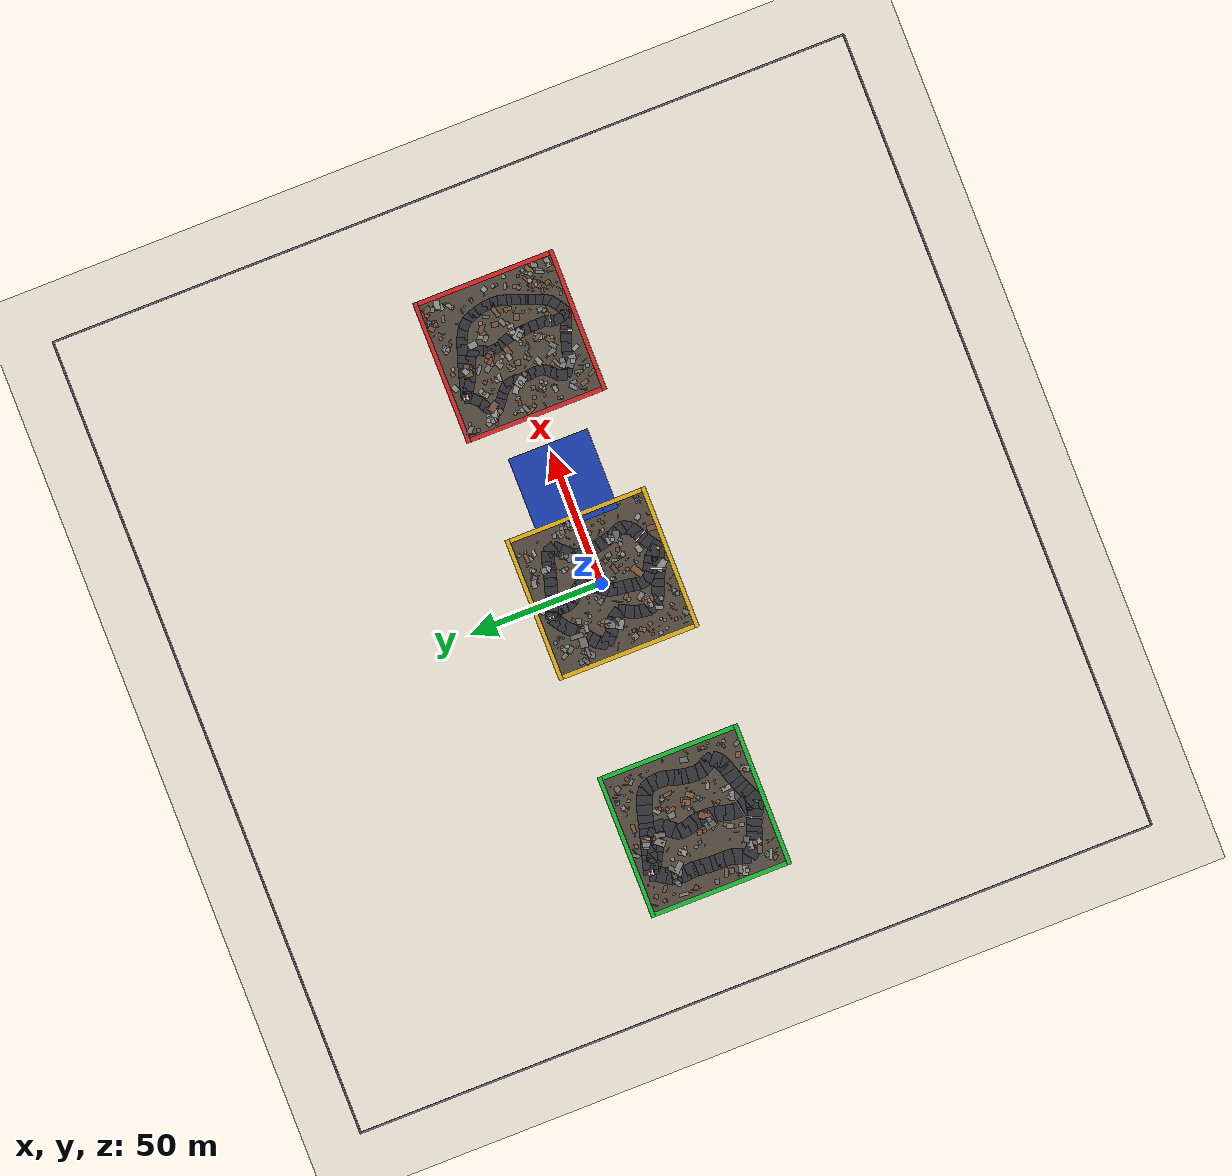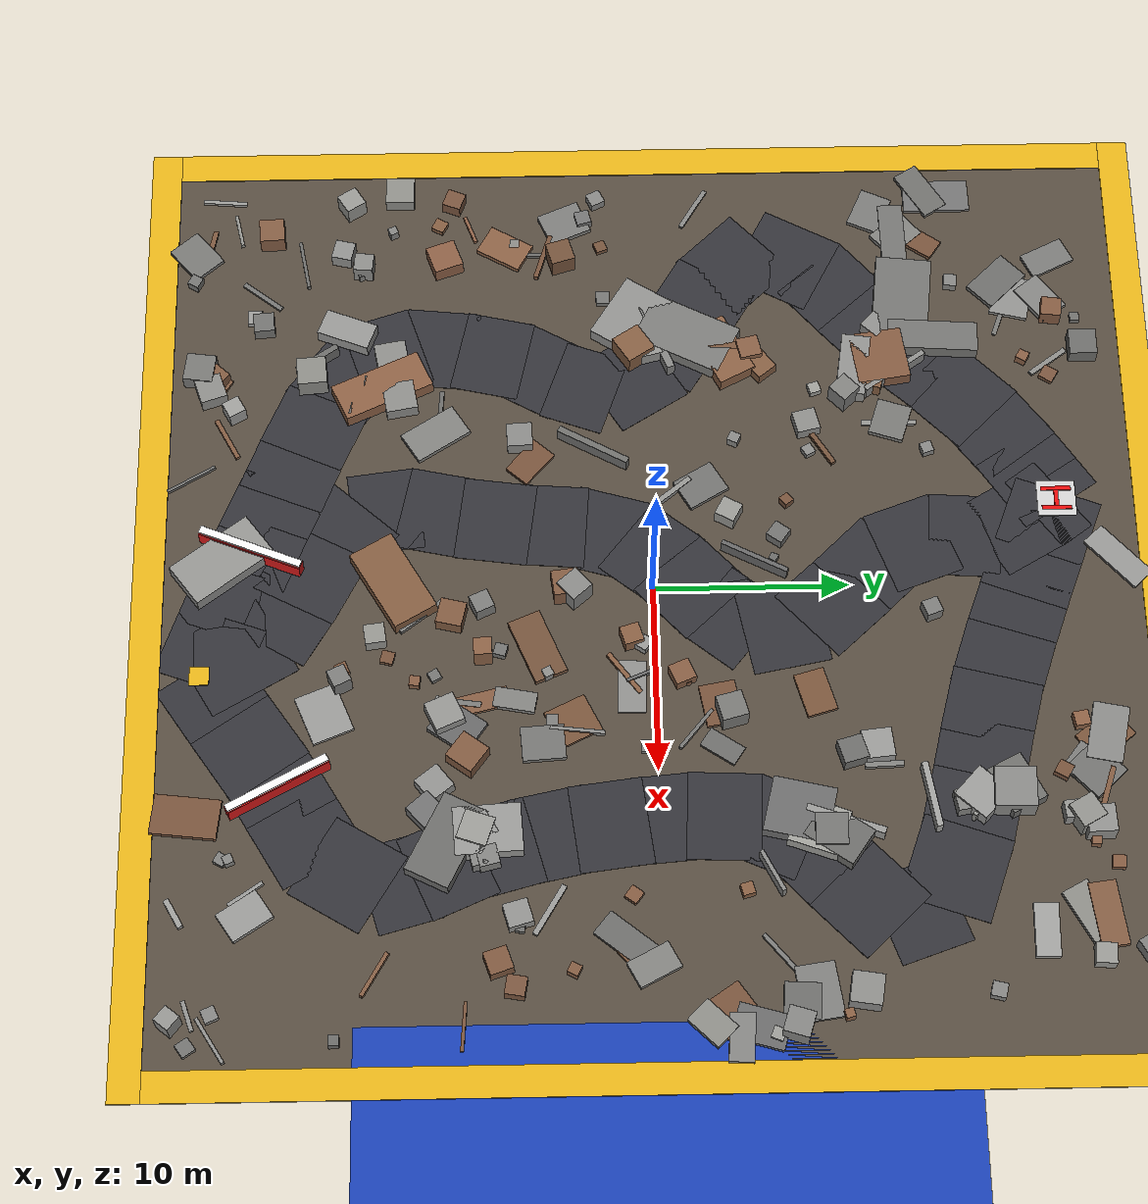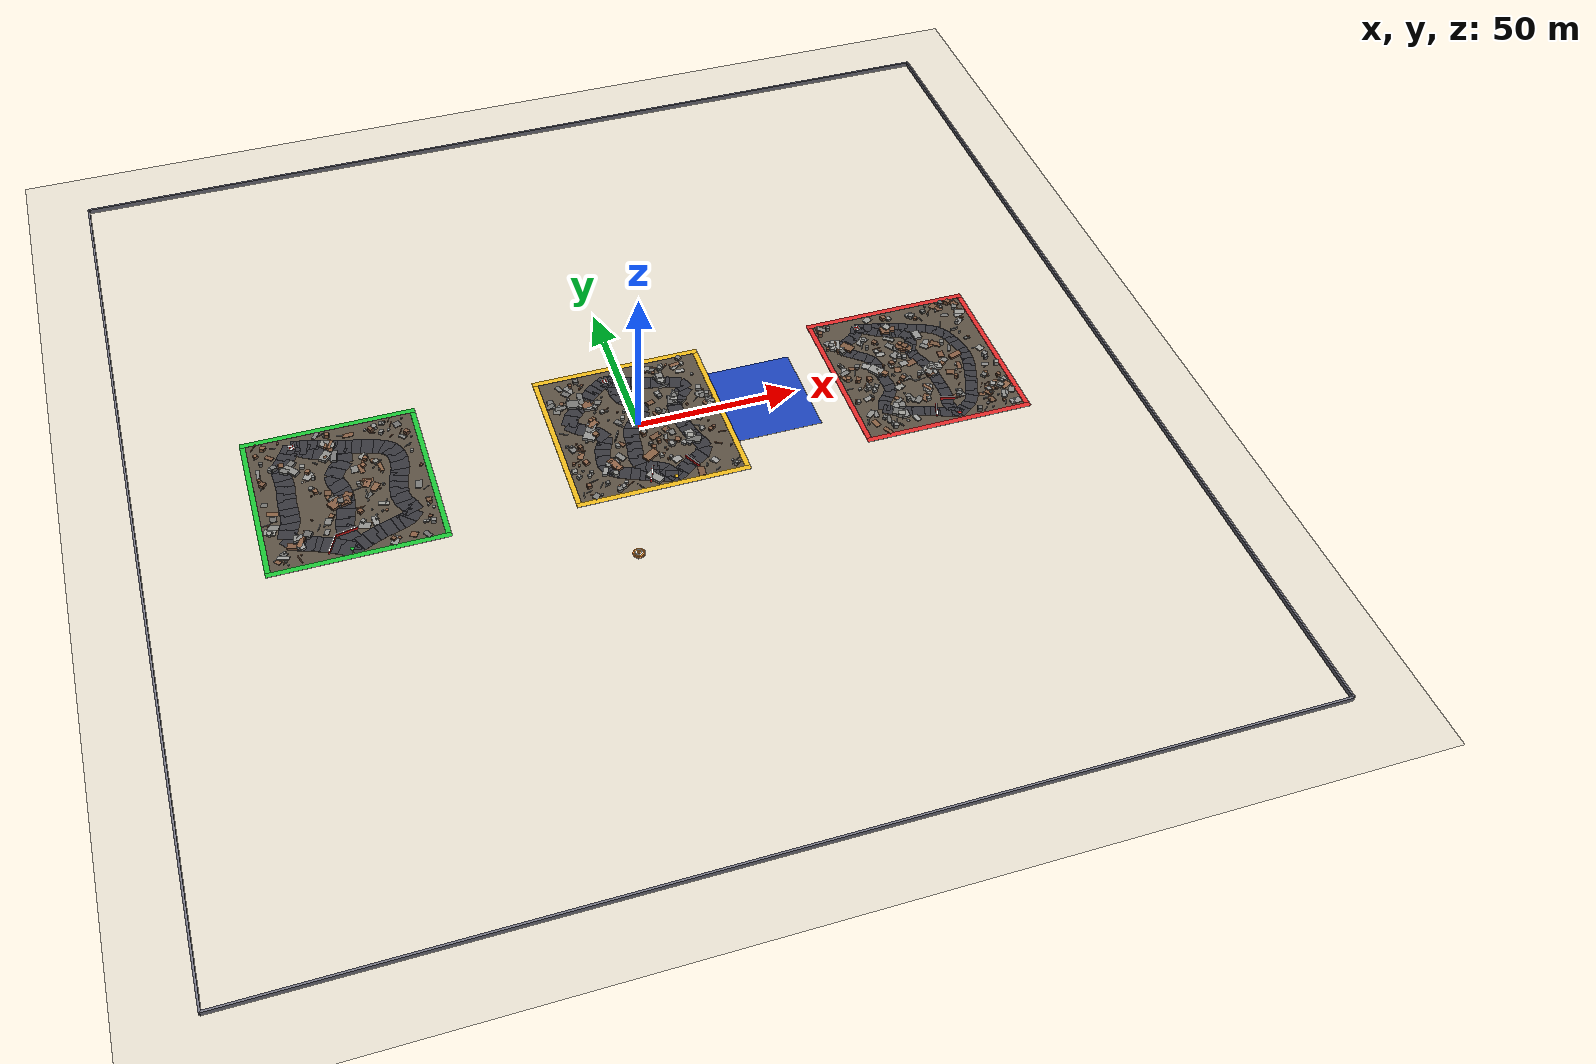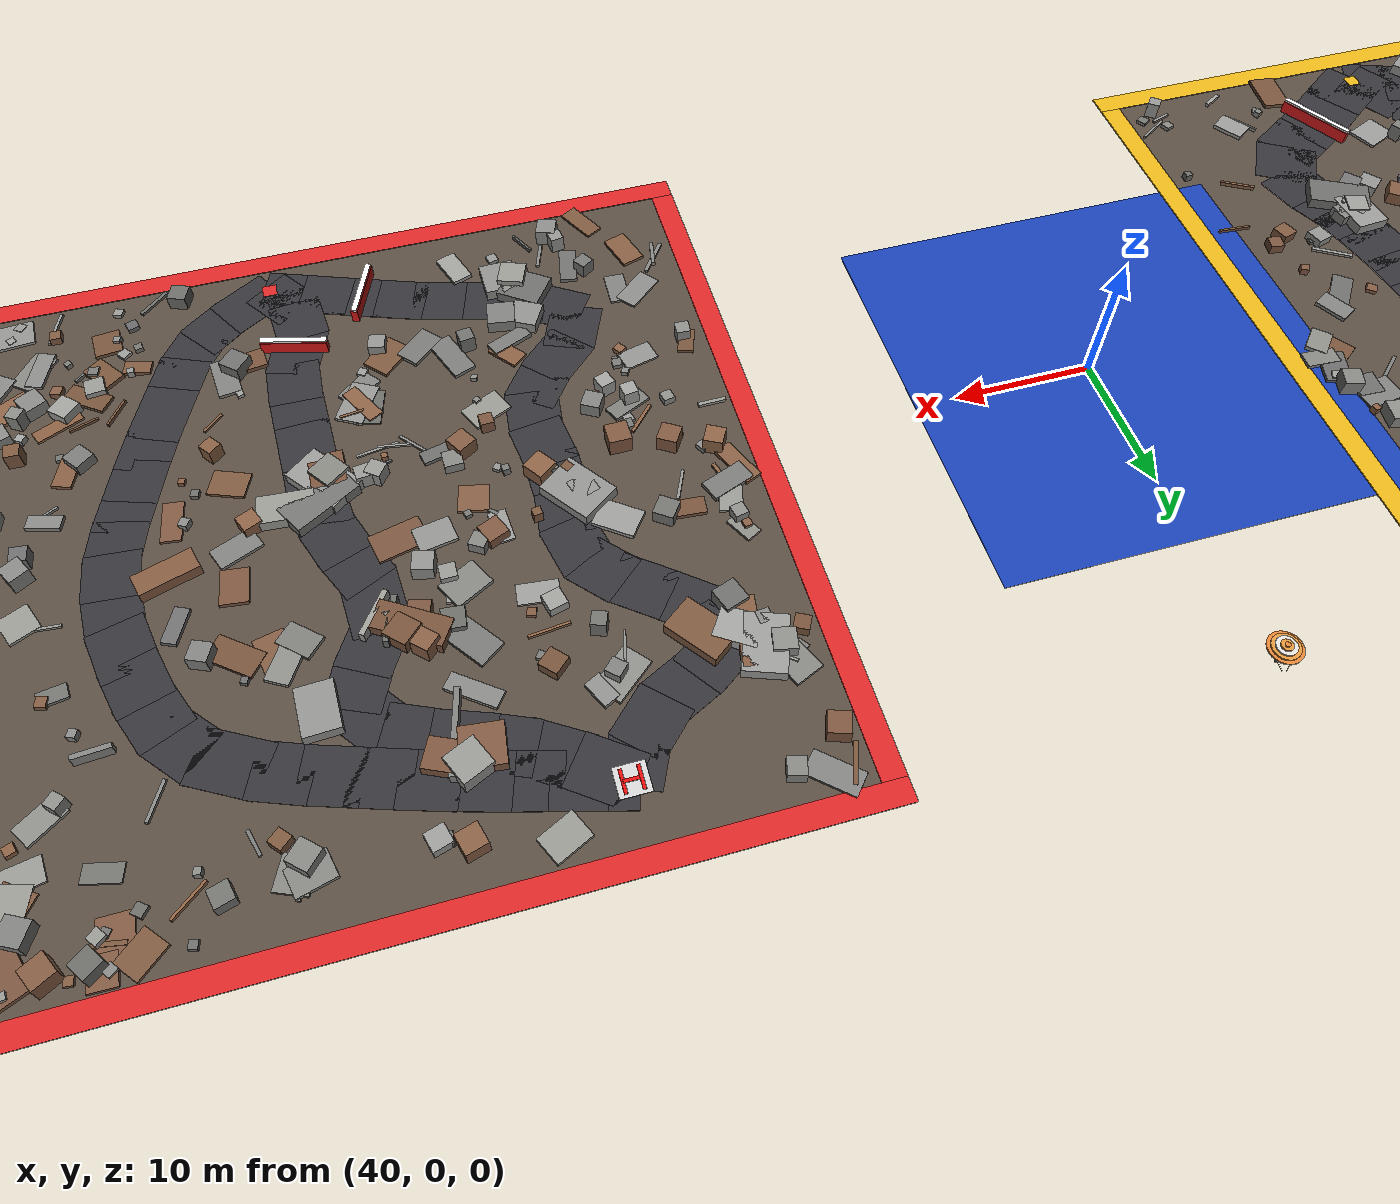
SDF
<sdf version="1.6">
 <world name="navitas_arena">
  <physics type="ode">
   <max_step_size>0.001</max_step_size>
   <real_time_factor>1</real_time_factor>
   <gravity>0 0 -9.8</gravity>
  </physics>
  <wind><linear_velocity>0.0000 0.0000 0.0000</linear_velocity></wind>
  <scene>
   <ambient>0.8200 0.8200 0.7800 1.0000</ambient>
   <background>0.9300 0.9500 1.0000 1.0000</background>
   <shadows>false</shadows>
  </scene>
  <light name="sun" type="directional">
   <cast_shadows>false</cast_shadows>
   <pose>0 0 120 0 0 0</pose>
   <diffuse>1.0000 0.9800 0.8800 1.0000</diffuse>
   <specular>0.1 0.1 0.1 1</specular>
   <attenuation>
    <range>1200</range>
    <constant>0.9</constant>
    <linear>0.01</linear>
    <quadratic>0.001</quadratic>
   </attenuation>
   <direction>-0.0800 0.0500 -1.0000</direction>
  </light>
  <model name="ground_plane">
   <static>true</static>
   <link name="link">
    <collision name="collision">
     <geometry><plane><normal>0 0 1</normal><size>400 400</size></plane></geometry>
     <surface><friction><ode><mu>0.720</mu><mu2>0.720</mu2></ode></friction></surface>
    </collision>
    <visual name="visual">
     <cast_shadows>false</cast_shadows>
     <geometry><plane><normal>0 0 1</normal><size>400 400</size></plane></geometry>
     <material><ambient>0.720 0.700 0.650 1</ambient><diffuse>0.720 0.700 0.650 1</diffuse></material>
    </visual>
   </link>
  </model>
  <model name="ub_N">
   <static>true</static>
   <pose>0.000 150.000 0.750 0 0 0.000</pose>
   <link name="link">
    <collision name="col"><geometry><box><size>300.000 0.600 1.500</size></box></geometry></collision>
    <visual name="vis">
     <geometry><box><size>300.000 0.600 1.500</size></box></geometry>
     <material><ambient>0.45 0.45 0.50 1</ambient><diffuse>0.45 0.45 0.50 1</diffuse></material>
    </visual>
   </link>
  </model>
  <model name="ub_S">
   <static>true</static>
   <pose>0.000 -150.000 0.750 0 0 0.000</pose>
   <link name="link">
    <collision name="col"><geometry><box><size>300.000 0.600 1.500</size></box></geometry></collision>
    <visual name="vis">
     <geometry><box><size>300.000 0.600 1.500</size></box></geometry>
     <material><ambient>0.45 0.45 0.50 1</ambient><diffuse>0.45 0.45 0.50 1</diffuse></material>
    </visual>
   </link>
  </model>
  <model name="ub_W">
   <static>true</static>
   <pose>-150.000 0.000 0.750 0 0 0.000</pose>
   <link name="link">
    <collision name="col"><geometry><box><size>0.600 300.000 1.500</size></box></geometry></collision>
    <visual name="vis">
     <geometry><box><size>0.600 300.000 1.500</size></box></geometry>
     <material><ambient>0.45 0.45 0.50 1</ambient><diffuse>0.45 0.45 0.50 1</diffuse></material>
    </visual>
   </link>
  </model>
  <model name="ub_E">
   <static>true</static>
   <pose>150.000 0.000 0.750 0 0 0.000</pose>
   <link name="link">
    <collision name="col"><geometry><box><size>0.600 300.000 1.500</size></box></geometry></collision>
    <visual name="vis">
     <geometry><box><size>0.600 300.000 1.500</size></box></geometry>
     <material><ambient>0.45 0.45 0.50 1</ambient><diffuse>0.45 0.45 0.50 1</diffuse></material>
    </visual>
   </link>
  </model>
  <model name="landing">
   <static>true</static>
   <pose>38.000 0.000 0.010 0 0 0.000</pose>
   <link name="link">
    <collision name="col"><geometry><box><size>30.000 30.000 0.020</size></box></geometry></collision>
    <visual name="vis">
     <geometry><box><size>30.000 30.000 0.020</size></box></geometry>
     <material><ambient>0.10 0.25 0.70 1</ambient><diffuse>0.10 0.25 0.70 1</diffuse></material>
    </visual>
   </link>
  </model>
  <model name="gd_kolay">
   <static>true</static>
   <pose>-90.000 0.000 0.010 0 0 0.000</pose>
   <link name="link">
    <collision name="col"><geometry><box><size>50.000 50.000 0.020</size></box></geometry></collision>
    <visual name="vis">
     <geometry><box><size>50.000 50.000 0.020</size></box></geometry>
     <material><ambient>0.34 0.30 0.25 1</ambient><diffuse>0.34 0.30 0.25 1</diffuse></material>
    </visual>
   </link>
  </model>
  <model name="brd_kolay_N">
   <static>true</static>
   <pose>-90.000 25.800 0.040 0 0 0.000</pose>
   <link name="link">
    <collision name="col"><geometry><box><size>53.200 1.600 0.080</size></box></geometry></collision>
    <visual name="vis">
     <geometry><box><size>53.200 1.600 0.080</size></box></geometry>
     <material><ambient>0.10 0.75 0.20 1</ambient><diffuse>0.10 0.75 0.20 1</diffuse></material>
    </visual>
   </link>
  </model>
  <model name="brd_kolay_S">
   <static>true</static>
   <pose>-90.000 -25.800 0.040 0 0 0.000</pose>
   <link name="link">
    <collision name="col"><geometry><box><size>53.200 1.600 0.080</size></box></geometry></collision>
    <visual name="vis">
     <geometry><box><size>53.200 1.600 0.080</size></box></geometry>
     <material><ambient>0.10 0.75 0.20 1</ambient><diffuse>0.10 0.75 0.20 1</diffuse></material>
    </visual>
   </link>
  </model>
  <model name="brd_kolay_W">
   <static>true</static>
   <pose>-115.800 0.000 0.040 0 0 0.000</pose>
   <link name="link">
    <collision name="col"><geometry><box><size>1.600 50.000 0.080</size></box></geometry></collision>
    <visual name="vis">
     <geometry><box><size>1.600 50.000 0.080</size></box></geometry>
     <material><ambient>0.10 0.75 0.20 1</ambient><diffuse>0.10 0.75 0.20 1</diffuse></material>
    </visual>
   </link>
  </model>
  <model name="brd_kolay_E">
   <static>true</static>
   <pose>-64.200 0.000 0.040 0 0 0.000</pose>
   <link name="link">
    <collision name="col"><geometry><box><size>1.600 50.000 0.080</size></box></geometry></collision>
    <visual name="vis">
     <geometry><box><size>1.600 50.000 0.080</size></box></geometry>
     <material><ambient>0.10 0.75 0.20 1</ambient><diffuse>0.10 0.75 0.20 1</diffuse></material>
    </visual>
   </link>
  </model>
  <model name="road_kolay_1_0">
   <static>true</static>
   <pose>-92.795 -22.266 0.040 0 0 2.633</pose>
   <link name="link">
    <collision name="col"><geometry><box><size>3.915 5.520 0.020</size></box></geometry></collision>
    <visual name="vis">
     <geometry><box><size>3.915 5.520 0.020</size></box></geometry>
     <material><ambient>0.20 0.20 0.22 1</ambient><diffuse>0.20 0.20 0.22 1</diffuse></material>
    </visual>
   </link>
  </model>
  <model name="road_kolay_1_1">
   <static>true</static>
   <pose>-95.375 -20.856 0.040 0 0 2.651</pose>
   <link name="link">
    <collision name="col"><geometry><box><size>3.766 5.520 0.020</size></box></geometry></collision>
    <visual name="vis">
     <geometry><box><size>3.766 5.520 0.020</size></box></geometry>
     <material><ambient>0.20 0.20 0.22 1</ambient><diffuse>0.20 0.20 0.22 1</diffuse></material>
    </visual>
   </link>
  </model>
  <model name="road_kolay_1_2">
   <static>true</static>
   <pose>-97.843 -19.620 0.040 0 0 2.705</pose>
   <link name="link">
    <collision name="col"><geometry><box><size>3.557 5.520 0.020</size></box></geometry></collision>
    <visual name="vis">
     <geometry><box><size>3.557 5.520 0.020</size></box></geometry>
     <material><ambient>0.20 0.20 0.22 1</ambient><diffuse>0.20 0.20 0.22 1</diffuse></material>
    </visual>
   </link>
  </model>
  <model name="road_kolay_1_3">
   <static>true</static>
   <pose>-100.305 -18.612 0.040 0 0 2.801</pose>
   <link name="link">
    <collision name="col"><geometry><box><size>3.570 5.520 0.020</size></box></geometry></collision>
    <visual name="vis">
     <geometry><box><size>3.570 5.520 0.020</size></box></geometry>
     <material><ambient>0.20 0.20 0.22 1</ambient><diffuse>0.20 0.20 0.22 1</diffuse></material>
    </visual>
   </link>
  </model>
  <model name="road_kolay_1_4">
   <static>true</static>
   <pose>-102.911 -17.697 0.040 0 0 2.806</pose>
   <link name="link">
    <collision name="col"><geometry><box><size>3.754 5.520 0.020</size></box></geometry></collision>
    <visual name="vis">
     <geometry><box><size>3.754 5.520 0.020</size></box></geometry>
     <material><ambient>0.20 0.20 0.22 1</ambient><diffuse>0.20 0.20 0.22 1</diffuse></material>
    </visual>
   </link>
  </model>
  <model name="road_kolay_1_5">
   <static>true</static>
   <pose>-105.442 -16.707 0.040 0 0 2.728</pose>
   <link name="link">
    <collision name="col"><geometry><box><size>3.486 5.520 0.020</size></box></geometry></collision>
    <visual name="vis">
     <geometry><box><size>3.486 5.520 0.020</size></box></geometry>
     <material><ambient>0.20 0.20 0.22 1</ambient><diffuse>0.20 0.20 0.22 1</diffuse></material>
    </visual>
   </link>
  </model>
  <model name="road_kolay_1_6">
   <static>true</static>
   <pose>-107.599 -14.974 0.040 0 0 2.246</pose>
   <link name="link">
    <collision name="col"><geometry><box><size>4.011 5.520 0.020</size></box></geometry></collision>
    <visual name="vis">
     <geometry><box><size>4.011 5.520 0.020</size></box></geometry>
     <material><ambient>0.20 0.20 0.22 1</ambient><diffuse>0.20 0.20 0.22 1</diffuse></material>
    </visual>
   </link>
  </model>
  <model name="road_kolay_1_7">
   <static>true</static>
   <pose>-108.118 -12.340 0.040 0 0 1.261</pose>
   <link name="link">
    <collision name="col"><geometry><box><size>3.881 5.520 0.020</size></box></geometry></collision>
    <visual name="vis">
     <geometry><box><size>3.881 5.520 0.020</size></box></geometry>
     <material><ambient>0.20 0.20 0.22 1</ambient><diffuse>0.20 0.20 0.22 1</diffuse></material>
    </visual>
   </link>
  </model>
  <model name="road_kolay_1_8">
   <static>true</static>
   <pose>-107.121 -9.460 0.040 0 0 1.214</pose>
   <link name="link">
    <collision name="col"><geometry><box><size>4.016 5.520 0.020</size></box></geometry></collision>
    <visual name="vis">
     <geometry><box><size>4.016 5.520 0.020</size></box></geometry>
     <material><ambient>0.20 0.20 0.22 1</ambient><diffuse>0.20 0.20 0.22 1</diffuse></material>
    </visual>
   </link>
  </model>
  <model name="road_kolay_1_9">
   <static>true</static>
   <pose>-106.523 -6.600 0.040 0 0 1.532</pose>
   <link name="link">
    <collision name="col"><geometry><box><size>3.702 5.520 0.020</size></box></geometry></collision>
    <visual name="vis">
     <geometry><box><size>3.702 5.520 0.020</size></box></geometry>
     <material><ambient>0.20 0.20 0.22 1</ambient><diffuse>0.20 0.20 0.22 1</diffuse></material>
    </visual>
   </link>
  </model>
  <model name="road_kolay_1_10">
   <static>true</static>
   <pose>-106.504 -3.800 0.040 0 0 1.596</pose>
   <link name="link">
    <collision name="col"><geometry><box><size>3.701 5.520 0.020</size></box></geometry></collision>
    <visual name="vis">
     <geometry><box><size>3.701 5.520 0.020</size></box></geometry>
     <material><ambient>0.20 0.20 0.22 1</ambient><diffuse>0.20 0.20 0.22 1</diffuse></material>
    </visual>
   </link>
  </model>
  <model name="road_kolay_1_11">
   <static>true</static>
   <pose>-106.485 -1.000 0.040 0 0 1.531</pose>
   <link name="link">
    <collision name="col"><geometry><box><size>3.702 5.520 0.020</size></box></geometry></collision>
    <visual name="vis">
     <geometry><box><size>3.702 5.520 0.020</size></box></geometry>
     <material><ambient>0.20 0.20 0.22 1</ambient><diffuse>0.20 0.20 0.22 1</diffuse></material>
    </visual>
   </link>
  </model>
  <model name="road_kolay_1_12">
   <static>true</static>
   <pose>-106.292 1.800 0.040 0 0 1.473</pose>
   <link name="link">
    <collision name="col"><geometry><box><size>3.714 5.520 0.020</size></box></geometry></collision>
    <visual name="vis">
     <geometry><box><size>3.714 5.520 0.020</size></box></geometry>
     <material><ambient>0.20 0.20 0.22 1</ambient><diffuse>0.20 0.20 0.22 1</diffuse></material>
    </visual>
   </link>
  </model>
  <model name="road_kolay_1_13">
   <static>true</static>
   <pose>-106.061 4.600 0.040 0 0 1.504</pose>
   <link name="link">
    <collision name="col"><geometry><box><size>3.706 5.520 0.020</size></box></geometry></collision>
    <visual name="vis">
     <geometry><box><size>3.706 5.520 0.020</size></box></geometry>
     <material><ambient>0.20 0.20 0.22 1</ambient><diffuse>0.20 0.20 0.22 1</diffuse></material>
    </visual>
   </link>
  </model>
  <model name="road_kolay_1_14">
   <static>true</static>
   <pose>-106.060 7.460 0.040 0 0 1.634</pose>
   <link name="link">
    <collision name="col"><geometry><box><size>3.826 5.520 0.020</size></box></geometry></collision>
    <visual name="vis">
     <geometry><box><size>3.826 5.520 0.020</size></box></geometry>
     <material><ambient>0.20 0.20 0.22 1</ambient><diffuse>0.20 0.20 0.22 1</diffuse></material>
    </visual>
   </link>
  </model>
  <model name="road_kolay_1_15">
   <static>true</static>
   <pose>-106.252 10.340 0.040 0 0 1.641</pose>
   <link name="link">
    <collision name="col"><geometry><box><size>3.747 5.520 0.020</size></box></geometry></collision>
    <visual name="vis">
     <geometry><box><size>3.747 5.520 0.020</size></box></geometry>
     <material><ambient>0.20 0.20 0.22 1</ambient><diffuse>0.20 0.20 0.22 1</diffuse></material>
    </visual>
   </link>
  </model>
  <model name="road_kolay_1_16">
   <static>true</static>
   <pose>-106.063 13.042 0.040 0 0 1.350</pose>
   <link name="link">
    <collision name="col"><geometry><box><size>3.528 5.520 0.020</size></box></geometry></collision>
    <visual name="vis">
     <geometry><box><size>3.528 5.520 0.020</size></box></geometry>
     <material><ambient>0.20 0.20 0.22 1</ambient><diffuse>0.20 0.20 0.22 1</diffuse></material>
    </visual>
   </link>
  </model>
  <model name="road_kolay_1_17">
   <static>true</static>
   <pose>-105.048 15.414 0.040 0 0 0.982</pose>
   <link name="link">
    <collision name="col"><geometry><box><size>3.521 5.520 0.020</size></box></geometry></collision>
    <visual name="vis">
     <geometry><box><size>3.521 5.520 0.020</size></box></geometry>
     <material><ambient>0.20 0.20 0.22 1</ambient><diffuse>0.20 0.20 0.22 1</diffuse></material>
    </visual>
   </link>
  </model>
  <model name="road_kolay_1_18">
   <static>true</static>
   <pose>-103.608 17.687 0.040 0 0 1.029</pose>
   <link name="link">
    <collision name="col"><geometry><box><size>3.662 5.520 0.020</size></box></geometry></collision>
    <visual name="vis">
     <geometry><box><size>3.662 5.520 0.020</size></box></geometry>
     <material><ambient>0.20 0.20 0.22 1</ambient><diffuse>0.20 0.20 0.22 1</diffuse></material>
    </visual>
   </link>
  </model>
  <model name="road_kolay_1_19">
   <static>true</static>
   <pose>-102.316 19.935 0.040 0 0 1.072</pose>
   <link name="link">
    <collision name="col"><geometry><box><size>3.324 5.520 0.020</size></box></geometry></collision>
    <visual name="vis">
     <geometry><box><size>3.324 5.520 0.020</size></box></geometry>
     <material><ambient>0.20 0.20 0.22 1</ambient><diffuse>0.20 0.20 0.22 1</diffuse></material>
    </visual>
   </link>
  </model>
  <model name="road_kolay_2_0">
   <static>true</static>
   <pose>-91.145 -21.250 0.040 0 0 1.383</pose>
   <link name="link">
    <collision name="col"><geometry><box><size>4.463 5.520 0.020</size></box></geometry></collision>
    <visual name="vis">
     <geometry><box><size>4.463 5.520 0.020</size></box></geometry>
     <material><ambient>0.20 0.20 0.22 1</ambient><diffuse>0.20 0.20 0.22 1</diffuse></material>
    </visual>
   </link>
  </model>
  <model name="road_kolay_2_1">
   <static>true</static>
   <pose>-91.347 -18.111 0.040 0 0 1.938</pose>
   <link name="link">
    <collision name="col"><geometry><box><size>3.876 5.520 0.020</size></box></geometry></collision>
    <visual name="vis">
     <geometry><box><size>3.876 5.520 0.020</size></box></geometry>
     <material><ambient>0.20 0.20 0.22 1</ambient><diffuse>0.20 0.20 0.22 1</diffuse></material>
    </visual>
   </link>
  </model>
  <model name="road_kolay_2_2">
   <static>true</static>
   <pose>-91.954 -15.241 0.040 0 0 1.620</pose>
   <link name="link">
    <collision name="col"><geometry><box><size>3.866 5.520 0.020</size></box></geometry></collision>
    <visual name="vis">
     <geometry><box><size>3.866 5.520 0.020</size></box></geometry>
     <material><ambient>0.20 0.20 0.22 1</ambient><diffuse>0.20 0.20 0.22 1</diffuse></material>
    </visual>
   </link>
  </model>
  <model name="road_kolay_2_3">
   <static>true</static>
   <pose>-91.626 -12.340 0.040 0 0 1.296</pose>
   <link name="link">
    <collision name="col"><geometry><box><size>3.850 5.520 0.020</size></box></geometry></collision>
    <visual name="vis">
     <geometry><box><size>3.850 5.520 0.020</size></box></geometry>
     <material><ambient>0.20 0.20 0.22 1</ambient><diffuse>0.20 0.20 0.22 1</diffuse></material>
    </visual>
   </link>
  </model>
  <model name="road_kolay_2_4">
   <static>true</static>
   <pose>-90.866 -9.460 0.040 0 0 1.329</pose>
   <link name="link">
    <collision name="col"><geometry><box><size>3.908 5.520 0.020</size></box></geometry></collision>
    <visual name="vis">
     <geometry><box><size>3.908 5.520 0.020</size></box></geometry>
     <material><ambient>0.20 0.20 0.22 1</ambient><diffuse>0.20 0.20 0.22 1</diffuse></material>
    </visual>
   </link>
  </model>
  <model name="road_kolay_2_5">
   <static>true</static>
   <pose>-90.349 -6.600 0.040 0 0 1.460</pose>
   <link name="link">
    <collision name="col"><geometry><box><size>3.717 5.520 0.020</size></box></geometry></collision>
    <visual name="vis">
     <geometry><box><size>3.717 5.520 0.020</size></box></geometry>
     <material><ambient>0.20 0.20 0.22 1</ambient><diffuse>0.20 0.20 0.22 1</diffuse></material>
    </visual>
   </link>
  </model>
  <model name="road_kolay_2_6">
   <static>true</static>
   <pose>-90.156 -3.800 0.040 0 0 1.544</pose>
   <link name="link">
    <collision name="col"><geometry><box><size>3.701 5.520 0.020</size></box></geometry></collision>
    <visual name="vis">
     <geometry><box><size>3.701 5.520 0.020</size></box></geometry>
     <material><ambient>0.20 0.20 0.22 1</ambient><diffuse>0.20 0.20 0.22 1</diffuse></material>
    </visual>
   </link>
  </model>
  <model name="road_kolay_2_7">
   <static>true</static>
   <pose>-90.309 -1.000 0.040 0 0 1.706</pose>
   <link name="link">
    <collision name="col"><geometry><box><size>3.726 5.520 0.020</size></box></geometry></collision>
    <visual name="vis">
     <geometry><box><size>3.726 5.520 0.020</size></box></geometry>
     <material><ambient>0.20 0.20 0.22 1</ambient><diffuse>0.20 0.20 0.22 1</diffuse></material>
    </visual>
   </link>
  </model>
  <model name="road_kolay_2_8">
   <static>true</static>
   <pose>-91.010 1.800 0.040 0 0 1.920</pose>
   <link name="link">
    <collision name="col"><geometry><box><size>3.880 5.520 0.020</size></box></geometry></collision>
    <visual name="vis">
     <geometry><box><size>3.880 5.520 0.020</size></box></geometry>
     <material><ambient>0.20 0.20 0.22 1</ambient><diffuse>0.20 0.20 0.22 1</diffuse></material>
    </visual>
   </link>
  </model>
  <model name="road_kolay_2_9">
   <static>true</static>
   <pose>-91.662 4.600 0.040 0 0 1.672</pose>
   <link name="link">
    <collision name="col"><geometry><box><size>3.714 5.520 0.020</size></box></geometry></collision>
    <visual name="vis">
     <geometry><box><size>3.714 5.520 0.020</size></box></geometry>
     <material><ambient>0.20 0.20 0.22 1</ambient><diffuse>0.20 0.20 0.22 1</diffuse></material>
    </visual>
   </link>
  </model>
  <model name="road_kolay_2_10">
   <static>true</static>
   <pose>-91.009 7.213 0.040 0 0 0.990</pose>
   <link name="link">
    <collision name="col"><geometry><box><size>3.802 5.520 0.020</size></box></geometry></collision>
    <visual name="vis">
     <geometry><box><size>3.802 5.520 0.020</size></box></geometry>
     <material><ambient>0.20 0.20 0.22 1</ambient><diffuse>0.20 0.20 0.22 1</diffuse></material>
    </visual>
   </link>
  </model>
  <model name="road_kolay_2_11">
   <static>true</static>
   <pose>-89.071 9.639 0.040 0 0 0.816</pose>
   <link name="link">
    <collision name="col"><geometry><box><size>4.232 5.520 0.020</size></box></geometry></collision>
    <visual name="vis">
     <geometry><box><size>4.232 5.520 0.020</size></box></geometry>
     <material><ambient>0.20 0.20 0.22 1</ambient><diffuse>0.20 0.20 0.22 1</diffuse></material>
    </visual>
   </link>
  </model>
  <model name="road_kolay_2_12">
   <static>true</static>
   <pose>-87.819 12.270 0.040 0 0 1.494</pose>
   <link name="link">
    <collision name="col"><geometry><box><size>3.746 5.520 0.020</size></box></geometry></collision>
    <visual name="vis">
     <geometry><box><size>3.746 5.520 0.020</size></box></geometry>
     <material><ambient>0.20 0.20 0.22 1</ambient><diffuse>0.20 0.20 0.22 1</diffuse></material>
    </visual>
   </link>
  </model>
  <model name="road_kolay_2_13">
   <static>true</static>
   <pose>-88.765 14.302 0.040 0 0 2.616</pose>
   <link name="link">
    <collision name="col"><geometry><box><size>3.342 5.520 0.020</size></box></geometry></collision>
    <visual name="vis">
     <geometry><box><size>3.342 5.520 0.020</size></box></geometry>
     <material><ambient>0.20 0.20 0.22 1</ambient><diffuse>0.20 0.20 0.22 1</diffuse></material>
    </visual>
   </link>
  </model>
  <model name="road_kolay_2_14">
   <static>true</static>
   <pose>-91.242 15.455 0.040 0 0 2.778</pose>
   <link name="link">
    <collision name="col"><geometry><box><size>3.939 5.520 0.020</size></box></geometry></collision>
    <visual name="vis">
     <geometry><box><size>3.939 5.520 0.020</size></box></geometry>
     <material><ambient>0.20 0.20 0.22 1</ambient><diffuse>0.20 0.20 0.22 1</diffuse></material>
    </visual>
   </link>
  </model>
  <model name="road_kolay_2_15">
   <static>true</static>
   <pose>-94.027 16.499 0.040 0 0 2.788</pose>
   <link name="link">
    <collision name="col"><geometry><box><size>3.811 5.520 0.020</size></box></geometry></collision>
    <visual name="vis">
     <geometry><box><size>3.811 5.520 0.020</size></box></geometry>
     <material><ambient>0.20 0.20 0.22 1</ambient><diffuse>0.20 0.20 0.22 1</diffuse></material>
    </visual>
   </link>
  </model>
  <model name="road_kolay_2_16">
   <static>true</static>
   <pose>-96.622 17.661 0.040 0 0 2.650</pose>
   <link name="link">
    <collision name="col"><geometry><box><size>3.689 5.520 0.020</size></box></geometry></collision>
    <visual name="vis">
     <geometry><box><size>3.689 5.520 0.020</size></box></geometry>
     <material><ambient>0.20 0.20 0.22 1</ambient><diffuse>0.20 0.20 0.22 1</diffuse></material>
    </visual>
   </link>
  </model>
  <model name="road_kolay_2_17">
   <static>true</static>
   <pose>-99.024 19.110 0.040 0 0 2.549</pose>
   <link name="link">
    <collision name="col"><geometry><box><size>3.727 5.520 0.020</size></box></geometry></collision>
    <visual name="vis">
     <geometry><box><size>3.727 5.520 0.020</size></box></geometry>
     <material><ambient>0.20 0.20 0.22 1</ambient><diffuse>0.20 0.20 0.22 1</diffuse></material>
    </visual>
   </link>
  </model>
  <model name="road_kolay_2_18">
   <static>true</static>
   <pose>-100.966 20.450 0.040 0 0 2.522</pose>
   <link name="link">
    <collision name="col"><geometry><box><size>2.793 5.520 0.020</size></box></geometry></collision>
    <visual name="vis">
     <geometry><box><size>2.793 5.520 0.020</size></box></geometry>
     <material><ambient>0.20 0.20 0.22 1</ambient><diffuse>0.20 0.20 0.22 1</diffuse></material>
    </visual>
   </link>
  </model>
  <model name="road_kolay_3_0">
   <static>true</static>
   <pose>-90.162 -22.399 0.040 0 0 0.428</pose>
   <link name="link">
    <collision name="col"><geometry><box><size>3.795 5.520 0.020</size></box></geometry></collision>
    <visual name="vis">
     <geometry><box><size>3.795 5.520 0.020</size></box></geometry>
     <material><ambient>0.20 0.20 0.22 1</ambient><diffuse>0.20 0.20 0.22 1</diffuse></material>
    </visual>
   </link>
  </model>
  <model name="road_kolay_3_1">
   <static>true</static>
   <pose>-87.597 -21.236 0.040 0 0 0.423</pose>
   <link name="link">
    <collision name="col"><geometry><box><size>3.636 5.520 0.020</size></box></geometry></collision>
    <visual name="vis">
     <geometry><box><size>3.636 5.520 0.020</size></box></geometry>
     <material><ambient>0.20 0.20 0.22 1</ambient><diffuse>0.20 0.20 0.22 1</diffuse></material>
    </visual>
   </link>
  </model>
  <model name="road_kolay_3_2">
   <static>true</static>
   <pose>-84.981 -20.087 0.040 0 0 0.406</pose>
   <link name="link">
    <collision name="col"><geometry><box><size>3.878 5.520 0.020</size></box></geometry></collision>
    <visual name="vis">
     <geometry><box><size>3.878 5.520 0.020</size></box></geometry>
     <material><ambient>0.20 0.20 0.22 1</ambient><diffuse>0.20 0.20 0.22 1</diffuse></material>
    </visual>
   </link>
  </model>
  <model name="road_kolay_3_3">
   <static>true</static>
   <pose>-82.474 -19.102 0.040 0 0 0.336</pose>
   <link name="link">
    <collision name="col"><geometry><box><size>3.314 5.520 0.020</size></box></geometry></collision>
    <visual name="vis">
     <geometry><box><size>3.314 5.520 0.020</size></box></geometry>
     <material><ambient>0.20 0.20 0.22 1</ambient><diffuse>0.20 0.20 0.22 1</diffuse></material>
    </visual>
   </link>
  </model>
  <model name="road_kolay_3_4">
   <static>true</static>
   <pose>-79.985 -18.298 0.040 0 0 0.292</pose>
   <link name="link">
    <collision name="col"><geometry><box><size>3.718 5.520 0.020</size></box></geometry></collision>
    <visual name="vis">
     <geometry><box><size>3.718 5.520 0.020</size></box></geometry>
     <material><ambient>0.20 0.20 0.22 1</ambient><diffuse>0.20 0.20 0.22 1</diffuse></material>
    </visual>
   </link>
  </model>
  <model name="road_kolay_3_5">
   <static>true</static>
   <pose>-77.285 -17.460 0.040 0 0 0.309</pose>
   <link name="link">
    <collision name="col"><geometry><box><size>3.737 5.520 0.020</size></box></geometry></collision>
    <visual name="vis">
     <geometry><box><size>3.737 5.520 0.020</size></box></geometry>
     <material><ambient>0.20 0.20 0.22 1</ambient><diffuse>0.20 0.20 0.22 1</diffuse></material>
    </visual>
   </link>
  </model>
  <model name="road_kolay_3_6">
   <static>true</static>
   <pose>-74.788 -16.552 0.040 0 0 0.394</pose>
   <link name="link">
    <collision name="col"><geometry><box><size>3.382 5.520 0.020</size></box></geometry></collision>
    <visual name="vis">
     <geometry><box><size>3.382 5.520 0.020</size></box></geometry>
     <material><ambient>0.20 0.20 0.22 1</ambient><diffuse>0.20 0.20 0.22 1</diffuse></material>
    </visual>
   </link>
  </model>
  <model name="road_kolay_3_7">
   <static>true</static>
   <pose>-72.720 -15.027 0.040 0 0 0.850</pose>
   <link name="link">
    <collision name="col"><geometry><box><size>3.693 5.520 0.020</size></box></geometry></collision>
    <visual name="vis">
     <geometry><box><size>3.693 5.520 0.020</size></box></geometry>
     <material><ambient>0.20 0.20 0.22 1</ambient><diffuse>0.20 0.20 0.22 1</diffuse></material>
    </visual>
   </link>
  </model>
  <model name="road_kolay_3_8">
   <static>true</static>
   <pose>-72.225 -12.817 0.040 0 0 1.923</pose>
   <link name="link">
    <collision name="col"><geometry><box><size>3.374 5.520 0.020</size></box></geometry></collision>
    <visual name="vis">
     <geometry><box><size>3.374 5.520 0.020</size></box></geometry>
     <material><ambient>0.20 0.20 0.22 1</ambient><diffuse>0.20 0.20 0.22 1</diffuse></material>
    </visual>
   </link>
  </model>
  <model name="road_kolay_3_9">
   <static>true</static>
   <pose>-73.377 -10.426 0.040 0 0 2.103</pose>
   <link name="link">
    <collision name="col"><geometry><box><size>3.756 5.520 0.020</size></box></geometry></collision>
    <visual name="vis">
     <geometry><box><size>3.756 5.520 0.020</size></box></geometry>
     <material><ambient>0.20 0.20 0.22 1</ambient><diffuse>0.20 0.20 0.22 1</diffuse></material>
    </visual>
   </link>
  </model>
  <model name="road_kolay_3_10">
   <static>true</static>
   <pose>-74.319 -7.898 0.040 0 0 1.736</pose>
   <link name="link">
    <collision name="col"><geometry><box><size>3.532 5.520 0.020</size></box></geometry></collision>
    <visual name="vis">
     <geometry><box><size>3.532 5.520 0.020</size></box></geometry>
     <material><ambient>0.20 0.20 0.22 1</ambient><diffuse>0.20 0.20 0.22 1</diffuse></material>
    </visual>
   </link>
  </model>
  <model name="road_kolay_3_11">
   <static>true</static>
   <pose>-74.399 -5.200 0.040 0 0 1.473</pose>
   <link name="link">
    <collision name="col"><geometry><box><size>3.713 5.520 0.020</size></box></geometry></collision>
    <visual name="vis">
     <geometry><box><size>3.713 5.520 0.020</size></box></geometry>
     <material><ambient>0.20 0.20 0.22 1</ambient><diffuse>0.20 0.20 0.22 1</diffuse></material>
    </visual>
   </link>
  </model>
  <model name="road_kolay_3_12">
   <static>true</static>
   <pose>-74.010 -2.400 0.040 0 0 1.393</pose>
   <link name="link">
    <collision name="col"><geometry><box><size>3.745 5.520 0.020</size></box></geometry></collision>
    <visual name="vis">
     <geometry><box><size>3.745 5.520 0.020</size></box></geometry>
     <material><ambient>0.20 0.20 0.22 1</ambient><diffuse>0.20 0.20 0.22 1</diffuse></material>
    </visual>
   </link>
  </model>
  <model name="road_kolay_3_13">
   <static>true</static>
   <pose>-73.425 0.167 0.040 0 0 1.292</pose>
   <link name="link">
    <collision name="col"><geometry><box><size>3.327 5.520 0.020</size></box></geometry></collision>
    <visual name="vis">
     <geometry><box><size>3.327 5.520 0.020</size></box></geometry>
     <material><ambient>0.20 0.20 0.22 1</ambient><diffuse>0.20 0.20 0.22 1</diffuse></material>
    </visual>
   </link>
  </model>
  <model name="road_kolay_3_14">
   <static>true</static>
   <pose>-72.700 2.500 0.040 0 0 1.247</pose>
   <link name="link">
    <collision name="col"><geometry><box><size>3.361 5.520 0.020</size></box></geometry></collision>
    <visual name="vis">
     <geometry><box><size>3.361 5.520 0.020</size></box></geometry>
     <material><ambient>0.20 0.20 0.22 1</ambient><diffuse>0.20 0.20 0.22 1</diffuse></material>
    </visual>
   </link>
  </model>
  <model name="road_kolay_3_15">
   <static>true</static>
   <pose>-72.196 5.431 0.040 0 0 1.507</pose>
   <link name="link">
    <collision name="col"><geometry><box><size>4.436 5.520 0.020</size></box></geometry></collision>
    <visual name="vis">
     <geometry><box><size>4.436 5.520 0.020</size></box></geometry>
     <material><ambient>0.20 0.20 0.22 1</ambient><diffuse>0.20 0.20 0.22 1</diffuse></material>
    </visual>
   </link>
  </model>
  <model name="road_kolay_3_16">
   <static>true</static>
   <pose>-72.229 8.426 0.040 0 0 1.689</pose>
   <link name="link">
    <collision name="col"><geometry><box><size>3.378 5.520 0.020</size></box></geometry></collision>
    <visual name="vis">
     <geometry><box><size>3.378 5.520 0.020</size></box></geometry>
     <material><ambient>0.20 0.20 0.22 1</ambient><diffuse>0.20 0.20 0.22 1</diffuse></material>
    </visual>
   </link>
  </model>
  <model name="road_kolay_3_17">
   <static>true</static>
   <pose>-72.971 10.817 0.040 0 0 2.045</pose>
   <link name="link">
    <collision name="col"><geometry><box><size>3.510 5.520 0.020</size></box></geometry></collision>
    <visual name="vis">
     <geometry><box><size>3.510 5.520 0.020</size></box></geometry>
     <material><ambient>0.20 0.20 0.22 1</ambient><diffuse>0.20 0.20 0.22 1</diffuse></material>
    </visual>
   </link>
  </model>
  <model name="road_kolay_3_18">
   <static>true</static>
   <pose>-74.563 12.722 0.040 0 0 2.500</pose>
   <link name="link">
    <collision name="col"><geometry><box><size>3.385 5.520 0.020</size></box></geometry></collision>
    <visual name="vis">
     <geometry><box><size>3.385 5.520 0.020</size></box></geometry>
     <material><ambient>0.20 0.20 0.22 1</ambient><diffuse>0.20 0.20 0.22 1</diffuse></material>
    </visual>
   </link>
  </model>
  <model name="road_kolay_3_19">
   <static>true</static>
   <pose>-77.175 14.094 0.040 0 0 2.771</pose>
   <link name="link">
    <collision name="col"><geometry><box><size>4.369 5.520 0.020</size></box></geometry></collision>
    <visual name="vis">
     <geometry><box><size>4.369 5.520 0.020</size></box></geometry>
     <material><ambient>0.20 0.20 0.22 1</ambient><diffuse>0.20 0.20 0.22 1</diffuse></material>
    </visual>
   </link>
  </model>
  <model name="road_kolay_3_20">
   <static>true</static>
   <pose>-80.094 15.095 0.040 0 0 2.862</pose>
   <link name="link">
    <collision name="col"><geometry><box><size>3.609 5.520 0.020</size></box></geometry></collision>
    <visual name="vis">
     <geometry><box><size>3.609 5.520 0.020</size></box></geometry>
     <material><ambient>0.20 0.20 0.22 1</ambient><diffuse>0.20 0.20 0.22 1</diffuse></material>
    </visual>
   </link>
  </model>
  <model name="road_kolay_3_21">
   <static>true</static>
   <pose>-82.766 15.818 0.040 0 0 2.892</pose>
   <link name="link">
    <collision name="col"><geometry><box><size>3.727 5.520 0.020</size></box></geometry></collision>
    <visual name="vis">
     <geometry><box><size>3.727 5.520 0.020</size></box></geometry>
     <material><ambient>0.20 0.20 0.22 1</ambient><diffuse>0.20 0.20 0.22 1</diffuse></material>
    </visual>
   </link>
  </model>
  <model name="road_kolay_3_22">
   <static>true</static>
   <pose>-85.478 16.502 0.040 0 0 2.897</pose>
   <link name="link">
    <collision name="col"><geometry><box><size>3.666 5.520 0.020</size></box></geometry></collision>
    <visual name="vis">
     <geometry><box><size>3.666 5.520 0.020</size></box></geometry>
     <material><ambient>0.20 0.20 0.22 1</ambient><diffuse>0.20 0.20 0.22 1</diffuse></material>
    </visual>
   </link>
  </model>
  <model name="road_kolay_3_23">
   <static>true</static>
   <pose>-88.037 17.168 0.040 0 0 2.876</pose>
   <link name="link">
    <collision name="col"><geometry><box><size>3.425 5.520 0.020</size></box></geometry></collision>
    <visual name="vis">
     <geometry><box><size>3.425 5.520 0.020</size></box></geometry>
     <material><ambient>0.20 0.20 0.22 1</ambient><diffuse>0.20 0.20 0.22 1</diffuse></material>
    </visual>
   </link>
  </model>
  <model name="road_kolay_3_24">
   <static>true</static>
   <pose>-90.668 17.910 0.040 0 0 2.859</pose>
   <link name="link">
    <collision name="col"><geometry><box><size>3.842 5.520 0.020</size></box></geometry></collision>
    <visual name="vis">
     <geometry><box><size>3.842 5.520 0.020</size></box></geometry>
     <material><ambient>0.20 0.20 0.22 1</ambient><diffuse>0.20 0.20 0.22 1</diffuse></material>
    </visual>
   </link>
  </model>
  <model name="road_kolay_3_25">
   <static>true</static>
   <pose>-93.536 18.730 0.040 0 0 2.867</pose>
   <link name="link">
    <collision name="col"><geometry><box><size>3.925 5.520 0.020</size></box></geometry></collision>
    <visual name="vis">
     <geometry><box><size>3.925 5.520 0.020</size></box></geometry>
     <material><ambient>0.20 0.20 0.22 1</ambient><diffuse>0.20 0.20 0.22 1</diffuse></material>
    </visual>
   </link>
  </model>
  <model name="road_kolay_3_26">
   <static>true</static>
   <pose>-96.366 19.520 0.040 0 0 2.872</pose>
   <link name="link">
    <collision name="col"><geometry><box><size>3.751 5.520 0.020</size></box></geometry></collision>
    <visual name="vis">
     <geometry><box><size>3.751 5.520 0.020</size></box></geometry>
     <material><ambient>0.20 0.20 0.22 1</ambient><diffuse>0.20 0.20 0.22 1</diffuse></material>
    </visual>
   </link>
  </model>
  <model name="road_kolay_3_27">
   <static>true</static>
   <pose>-98.906 20.220 0.040 0 0 2.874</pose>
   <link name="link">
    <collision name="col"><geometry><box><size>3.318 5.520 0.020</size></box></geometry></collision>
    <visual name="vis">
     <geometry><box><size>3.318 5.520 0.020</size></box></geometry>
     <material><ambient>0.20 0.20 0.22 1</ambient><diffuse>0.20 0.20 0.22 1</diffuse></material>
    </visual>
   </link>
  </model>
  <model name="road_kolay_3_28">
   <static>true</static>
   <pose>-100.904 20.770 0.040 0 0 2.872</pose>
   <link name="link">
    <collision name="col"><geometry><box><size>2.628 5.520 0.020</size></box></geometry></collision>
    <visual name="vis">
     <geometry><box><size>2.628 5.520 0.020</size></box></geometry>
     <material><ambient>0.20 0.20 0.22 1</ambient><diffuse>0.20 0.20 0.22 1</diffuse></material>
    </visual>
   </link>
  </model>
  <model name="bar_kolay_1">
   <static>true</static>
   <pose>-96.639 -20.182 0.500 0 0 4.252</pose>
   <link name="link">
    <collision name="col"><geometry><box><size>6.520 0.500 1.000</size></box></geometry></collision>
    <visual name="vis">
     <geometry><box><size>6.520 0.500 1.000</size></box></geometry>
     <material><ambient>0.85 0.10 0.10 1</ambient><diffuse>0.85 0.10 0.10 1</diffuse></material>
    </visual>
   </link>
  </model>
  <model name="bar_kolay_1b">
   <static>true</static>
   <pose>-96.639 -20.182 1.000 0 0 4.252</pose>
   <link name="link">
    <collision name="col"><geometry><box><size>6.520 0.400 0.300</size></box></geometry></collision>
    <visual name="vis">
     <geometry><box><size>6.520 0.400 0.300</size></box></geometry>
     <material><ambient>0.95 0.95 0.95 1</ambient><diffuse>0.95 0.95 0.95 1</diffuse></material>
    </visual>
   </link>
  </model>
  <model name="blk_kolay_1_0_0">
   <static>true</static>
   <pose>-104.691 -16.580 0.425 0 0 1.061</pose>
   <link name="link">
    <collision name="col"><geometry><box><size>4.914 1.427 0.850</size></box></geometry></collision>
    <visual name="vis">
     <geometry><box><size>4.914 1.427 0.850</size></box></geometry>
     <material><ambient>0.55 0.38 0.27 1</ambient><diffuse>0.55 0.38 0.27 1</diffuse></material>
    </visual>
   </link>
  </model>
  <model name="blk_kolay_1_0_1">
   <static>true</static>
   <pose>-106.058 -18.996 0.425 0 0 2.004</pose>
   <link name="link">
    <collision name="col"><geometry><box><size>0.760 0.760 0.850</size></box></geometry></collision>
    <visual name="vis">
     <geometry><box><size>0.760 0.760 0.850</size></box></geometry>
     <material><ambient>0.40 0.40 0.40 1</ambient><diffuse>0.40 0.40 0.40 1</diffuse></material>
    </visual>
   </link>
  </model>
  <model name="blk_kolay_1_0_2">
   <static>true</static>
   <pose>-107.492 -17.890 0.425 0 0 2.830</pose>
   <link name="link">
    <collision name="col"><geometry><box><size>3.201 1.736 0.850</size></box></geometry></collision>
    <visual name="vis">
     <geometry><box><size>3.201 1.736 0.850</size></box></geometry>
     <material><ambient>0.49 0.34 0.25 1</ambient><diffuse>0.49 0.34 0.25 1</diffuse></material>
    </visual>
   </link>
  </model>
  <model name="blk_kolay_1_0_3">
   <static>true</static>
   <pose>-102.702 -14.793 0.603 0 0 2.594</pose>
   <link name="link">
    <collision name="col"><geometry><box><size>2.161 2.161 1.206</size></box></geometry></collision>
    <visual name="vis">
     <geometry><box><size>2.161 2.161 1.206</size></box></geometry>
     <material><ambient>0.41 0.41 0.40 1</ambient><diffuse>0.41 0.41 0.40 1</diffuse></material>
    </visual>
   </link>
  </model>
  <model name="blk_kolay_1_0_4">
   <static>true</static>
   <pose>-106.156 -14.981 0.425 0 0 2.377</pose>
   <link name="link">
    <collision name="col"><geometry><box><size>1.024 1.024 0.850</size></box></geometry></collision>
    <visual name="vis">
     <geometry><box><size>1.024 1.024 0.850</size></box></geometry>
     <material><ambient>0.49 0.49 0.48 1</ambient><diffuse>0.49 0.49 0.48 1</diffuse></material>
    </visual>
   </link>
  </model>
  <model name="blk_kolay_1_0_5">
   <static>true</static>
   <pose>-104.947 -18.795 0.425 0 0 0.324</pose>
   <link name="link">
    <collision name="col"><geometry><box><size>1.732 1.732 0.850</size></box></geometry></collision>
    <visual name="vis">
     <geometry><box><size>1.732 1.732 0.850</size></box></geometry>
     <material><ambient>0.61 0.61 0.60 1</ambient><diffuse>0.61 0.61 0.60 1</diffuse></material>
    </visual>
   </link>
  </model>
  <model name="blk_kolay_1_0_6">
   <static>true</static>
   <pose>-105.312 -15.311 0.425 0 0 3.035</pose>
   <link name="link">
    <collision name="col"><geometry><box><size>3.187 2.034 0.850</size></box></geometry></collision>
    <visual name="vis">
     <geometry><box><size>3.187 2.034 0.850</size></box></geometry>
     <material><ambient>0.55 0.55 0.54 1</ambient><diffuse>0.55 0.55 0.54 1</diffuse></material>
    </visual>
   </link>
  </model>
  <model name="blk_kolay_1_0_7">
   <static>true</static>
   <pose>-103.644 -15.305 0.425 0 0 1.295</pose>
   <link name="link">
    <collision name="col"><geometry><box><size>2.846 0.356 0.850</size></box></geometry></collision>
    <visual name="vis">
     <geometry><box><size>2.846 0.356 0.850</size></box></geometry>
     <material><ambient>0.46 0.32 0.23 1</ambient><diffuse>0.46 0.32 0.23 1</diffuse></material>
    </visual>
   </link>
  </model>
  <model name="blk_kolay_1_1_0">
   <static>true</static>
   <pose>-103.043 13.564 0.425 0 0 0.758</pose>
   <link name="link">
    <collision name="col"><geometry><box><size>2.801 1.728 0.850</size></box></geometry></collision>
    <visual name="vis">
     <geometry><box><size>2.801 1.728 0.850</size></box></geometry>
     <material><ambient>0.45 0.45 0.44 1</ambient><diffuse>0.45 0.45 0.44 1</diffuse></material>
    </visual>
   </link>
  </model>
  <model name="blk_kolay_1_1_1">
   <static>true</static>
   <pose>-106.239 12.950 0.425 0 0 0.953</pose>
   <link name="link">
    <collision name="col"><geometry><box><size>0.945 0.945 0.850</size></box></geometry></collision>
    <visual name="vis">
     <geometry><box><size>0.945 0.945 0.850</size></box></geometry>
     <material><ambient>0.47 0.47 0.46 1</ambient><diffuse>0.47 0.47 0.46 1</diffuse></material>
    </visual>
   </link>
  </model>
  <model name="blk_kolay_1_1_2">
   <static>true</static>
   <pose>-109.075 13.067 0.622 0 0 1.023</pose>
   <link name="link">
    <collision name="col"><geometry><box><size>1.285 1.285 1.243</size></box></geometry></collision>
    <visual name="vis">
     <geometry><box><size>1.285 1.285 1.243</size></box></geometry>
     <material><ambient>0.53 0.53 0.52 1</ambient><diffuse>0.53 0.53 0.52 1</diffuse></material>
    </visual>
   </link>
  </model>
  <model name="blk_kolay_1_1_3">
   <static>true</static>
   <pose>-105.275 11.510 0.425 0 0 2.600</pose>
   <link name="link">
    <collision name="col"><geometry><box><size>2.690 1.712 0.850</size></box></geometry></collision>
    <visual name="vis">
     <geometry><box><size>2.690 1.712 0.850</size></box></geometry>
     <material><ambient>0.47 0.47 0.46 1</ambient><diffuse>0.47 0.47 0.46 1</diffuse></material>
    </visual>
   </link>
  </model>
  <model name="blk_kolay_1_1_4">
   <static>true</static>
   <pose>-103.430 11.310 0.425 0 0 2.315</pose>
   <link name="link">
    <collision name="col"><geometry><box><size>4.928 2.129 0.850</size></box></geometry></collision>
    <visual name="vis">
     <geometry><box><size>4.928 2.129 0.850</size></box></geometry>
     <material><ambient>0.53 0.53 0.52 1</ambient><diffuse>0.53 0.53 0.52 1</diffuse></material>
    </visual>
   </link>
  </model>
  <model name="blk_kolay_1_1_5">
   <static>true</static>
   <pose>-108.223 13.491 0.622 0 0 0.443</pose>
   <link name="link">
    <collision name="col"><geometry><box><size>1.565 1.565 1.244</size></box></geometry></collision>
    <visual name="vis">
     <geometry><box><size>1.565 1.565 1.244</size></box></geometry>
     <material><ambient>0.45 0.45 0.44 1</ambient><diffuse>0.45 0.45 0.44 1</diffuse></material>
    </visual>
   </link>
  </model>
  <model name="blk_kolay_1_1_6">
   <static>true</static>
   <pose>-105.601 12.809 0.425 0 0 1.890</pose>
   <link name="link">
    <collision name="col"><geometry><box><size>0.738 0.738 0.850</size></box></geometry></collision>
    <visual name="vis">
     <geometry><box><size>0.738 0.738 0.850</size></box></geometry>
     <material><ambient>0.51 0.36 0.26 1</ambient><diffuse>0.51 0.36 0.26 1</diffuse></material>
    </visual>
   </link>
  </model>
  <model name="blk_kolay_1_1_7">
   <static>true</static>
   <pose>-105.905 13.578 0.614 0 0 1.635</pose>
   <link name="link">
    <collision name="col"><geometry><box><size>1.599 1.599 1.229</size></box></geometry></collision>
    <visual name="vis">
     <geometry><box><size>1.599 1.599 1.229</size></box></geometry>
     <material><ambient>0.49 0.34 0.24 1</ambient><diffuse>0.49 0.34 0.24 1</diffuse></material>
    </visual>
   </link>
  </model>
  <model name="bar_kolay_2">
   <static>true</static>
   <pose>-91.881 -16.722 0.500 0 0 3.318</pose>
   <link name="link">
    <collision name="col"><geometry><box><size>6.520 0.500 1.000</size></box></geometry></collision>
    <visual name="vis">
     <geometry><box><size>6.520 0.500 1.000</size></box></geometry>
     <material><ambient>0.85 0.10 0.10 1</ambient><diffuse>0.85 0.10 0.10 1</diffuse></material>
    </visual>
   </link>
  </model>
  <model name="bar_kolay_2b">
   <static>true</static>
   <pose>-91.881 -16.722 1.000 0 0 3.318</pose>
   <link name="link">
    <collision name="col"><geometry><box><size>6.520 0.400 0.300</size></box></geometry></collision>
    <visual name="vis">
     <geometry><box><size>6.520 0.400 0.300</size></box></geometry>
     <material><ambient>0.95 0.95 0.95 1</ambient><diffuse>0.95 0.95 0.95 1</diffuse></material>
    </visual>
   </link>
  </model>
  <model name="blk_kolay_2_0_0">
   <static>true</static>
   <pose>-89.680 -4.037 0.425 0 0 0.979</pose>
   <link name="link">
    <collision name="col"><geometry><box><size>4.305 2.479 0.850</size></box></geometry></collision>
    <visual name="vis">
     <geometry><box><size>4.305 2.479 0.850</size></box></geometry>
     <material><ambient>0.49 0.34 0.24 1</ambient><diffuse>0.49 0.34 0.24 1</diffuse></material>
    </visual>
   </link>
  </model>
  <model name="blk_kolay_2_0_1">
   <static>true</static>
   <pose>-90.326 -5.068 0.425 0 0 0.192</pose>
   <link name="link">
    <collision name="col"><geometry><box><size>3.158 2.848 0.850</size></box></geometry></collision>
    <visual name="vis">
     <geometry><box><size>3.158 2.848 0.850</size></box></geometry>
     <material><ambient>0.47 0.33 0.24 1</ambient><diffuse>0.47 0.33 0.24 1</diffuse></material>
    </visual>
   </link>
  </model>
  <model name="blk_kolay_2_0_2">
   <static>true</static>
   <pose>-91.843 -4.600 0.425 0 0 0.201</pose>
   <link name="link">
    <collision name="col"><geometry><box><size>3.688 1.558 0.850</size></box></geometry></collision>
    <visual name="vis">
     <geometry><box><size>3.688 1.558 0.850</size></box></geometry>
     <material><ambient>0.55 0.55 0.54 1</ambient><diffuse>0.55 0.55 0.54 1</diffuse></material>
    </visual>
   </link>
  </model>
  <model name="blk_kolay_2_0_3">
   <static>true</static>
   <pose>-93.152 -4.712 0.425 0 0 1.744</pose>
   <link name="link">
    <collision name="col"><geometry><box><size>4.064 2.712 0.850</size></box></geometry></collision>
    <visual name="vis">
     <geometry><box><size>4.064 2.712 0.850</size></box></geometry>
     <material><ambient>0.42 0.42 0.41 1</ambient><diffuse>0.42 0.42 0.41 1</diffuse></material>
    </visual>
   </link>
  </model>
  <model name="blk_kolay_2_0_4">
   <static>true</static>
   <pose>-91.478 -4.968 0.592 0 0 0.040</pose>
   <link name="link">
    <collision name="col"><geometry><box><size>1.776 1.776 1.183</size></box></geometry></collision>
    <visual name="vis">
     <geometry><box><size>1.776 1.776 1.183</size></box></geometry>
     <material><ambient>0.43 0.43 0.42 1</ambient><diffuse>0.43 0.43 0.42 1</diffuse></material>
    </visual>
   </link>
  </model>
  <model name="blk_kolay_2_0_5">
   <static>true</static>
   <pose>-92.875 -4.794 0.425 0 0 2.326</pose>
   <link name="link">
    <collision name="col"><geometry><box><size>1.050 1.050 0.850</size></box></geometry></collision>
    <visual name="vis">
     <geometry><box><size>1.050 1.050 0.850</size></box></geometry>
     <material><ambient>0.50 0.50 0.49 1</ambient><diffuse>0.50 0.50 0.49 1</diffuse></material>
    </visual>
   </link>
  </model>
  <model name="blk_kolay_2_0_6">
   <static>true</static>
   <pose>-88.638 -4.481 0.425 0 0 2.369</pose>
   <link name="link">
    <collision name="col"><geometry><box><size>0.603 0.603 0.850</size></box></geometry></collision>
    <visual name="vis">
     <geometry><box><size>0.603 0.603 0.850</size></box></geometry>
     <material><ambient>0.62 0.62 0.61 1</ambient><diffuse>0.62 0.62 0.61 1</diffuse></material>
    </visual>
   </link>
  </model>
  <model name="blk_kolay_2_0_7">
   <static>true</static>
   <pose>-93.024 -5.268 0.425 0 0 0.526</pose>
   <link name="link">
    <collision name="col"><geometry><box><size>4.241 3.029 0.850</size></box></geometry></collision>
    <visual name="vis">
     <geometry><box><size>4.241 3.029 0.850</size></box></geometry>
     <material><ambient>0.50 0.35 0.25 1</ambient><diffuse>0.50 0.35 0.25 1</diffuse></material>
    </visual>
   </link>
  </model>
  <model name="blk_kolay_2_1_0">
   <static>true</static>
   <pose>-90.727 15.725 0.619 0 0 1.529</pose>
   <link name="link">
    <collision name="col"><geometry><box><size>1.282 1.282 1.238</size></box></geometry></collision>
    <visual name="vis">
     <geometry><box><size>1.282 1.282 1.238</size></box></geometry>
     <material><ambient>0.47 0.33 0.23 1</ambient><diffuse>0.47 0.33 0.23 1</diffuse></material>
    </visual>
   </link>
  </model>
  <model name="blk_kolay_2_1_1">
   <static>true</static>
   <pose>-91.306 18.652 0.425 0 0 2.698</pose>
   <link name="link">
    <collision name="col"><geometry><box><size>4.382 2.096 0.850</size></box></geometry></collision>
    <visual name="vis">
     <geometry><box><size>4.382 2.096 0.850</size></box></geometry>
     <material><ambient>0.57 0.57 0.56 1</ambient><diffuse>0.57 0.57 0.56 1</diffuse></material>
    </visual>
   </link>
  </model>
  <model name="blk_kolay_2_1_2">
   <static>true</static>
   <pose>-91.752 18.995 0.425 0 0 1.115</pose>
   <link name="link">
    <collision name="col"><geometry><box><size>2.670 1.789 0.850</size></box></geometry></collision>
    <visual name="vis">
     <geometry><box><size>2.670 1.789 0.850</size></box></geometry>
     <material><ambient>0.51 0.51 0.50 1</ambient><diffuse>0.51 0.51 0.50 1</diffuse></material>
    </visual>
   </link>
  </model>
  <model name="blk_kolay_2_1_3">
   <static>true</static>
   <pose>-92.786 13.579 0.425 0 0 1.564</pose>
   <link name="link">
    <collision name="col"><geometry><box><size>0.930 0.930 0.850</size></box></geometry></collision>
    <visual name="vis">
     <geometry><box><size>0.930 0.930 0.850</size></box></geometry>
     <material><ambient>0.45 0.32 0.23 1</ambient><diffuse>0.45 0.32 0.23 1</diffuse></material>
    </visual>
   </link>
  </model>
  <model name="blk_kolay_2_1_4">
   <static>true</static>
   <pose>-92.699 14.105 0.425 0 0 0.852</pose>
   <link name="link">
    <collision name="col"><geometry><box><size>3.923 2.502 0.850</size></box></geometry></collision>
    <visual name="vis">
     <geometry><box><size>3.923 2.502 0.850</size></box></geometry>
     <material><ambient>0.53 0.53 0.52 1</ambient><diffuse>0.53 0.53 0.52 1</diffuse></material>
    </visual>
   </link>
  </model>
  <model name="blk_kolay_2_1_5">
   <static>true</static>
   <pose>-90.291 13.326 0.425 0 0 1.360</pose>
   <link name="link">
    <collision name="col"><geometry><box><size>4.060 1.748 0.850</size></box></geometry></collision>
    <visual name="vis">
     <geometry><box><size>4.060 1.748 0.850</size></box></geometry>
     <material><ambient>0.45 0.45 0.45 1</ambient><diffuse>0.45 0.45 0.45 1</diffuse></material>
    </visual>
   </link>
  </model>
  <model name="blk_kolay_2_1_6">
   <static>true</static>
   <pose>-91.630 17.432 0.425 0 0 1.855</pose>
   <link name="link">
    <collision name="col"><geometry><box><size>0.997 0.997 0.850</size></box></geometry></collision>
    <visual name="vis">
     <geometry><box><size>0.997 0.997 0.850</size></box></geometry>
     <material><ambient>0.50 0.35 0.25 1</ambient><diffuse>0.50 0.35 0.25 1</diffuse></material>
    </visual>
   </link>
  </model>
  <model name="blk_kolay_2_1_7">
   <static>true</static>
   <pose>-90.949 18.653 0.425 0 0 1.044</pose>
   <link name="link">
    <collision name="col"><geometry><box><size>3.314 2.000 0.850</size></box></geometry></collision>
    <visual name="vis">
     <geometry><box><size>3.314 2.000 0.850</size></box></geometry>
     <material><ambient>0.53 0.37 0.26 1</ambient><diffuse>0.53 0.37 0.26 1</diffuse></material>
    </visual>
   </link>
  </model>
  <model name="deb_kolay_0">
   <static>true</static>
   <pose>-83.755 1.420 0.145 0 0 2.621</pose>
   <link name="link">
    <collision name="col"><geometry><box><size>2.419 0.249 0.290</size></box></geometry></collision>
    <visual name="vis">
     <geometry><box><size>2.419 0.249 0.290</size></box></geometry>
     <material><ambient>0.54 0.38 0.27 1</ambient><diffuse>0.54 0.38 0.27 1</diffuse></material>
    </visual>
   </link>
  </model>
  <model name="deb_kolay_1">
   <static>true</static>
   <pose>-73.501 23.755 0.221 0 0 0.921</pose>
   <link name="link">
    <collision name="col"><geometry><box><size>0.578 0.578 0.442</size></box></geometry></collision>
    <visual name="vis">
     <geometry><box><size>0.578 0.578 0.442</size></box></geometry>
     <material><ambient>0.54 0.38 0.27 1</ambient><diffuse>0.54 0.38 0.27 1</diffuse></material>
    </visual>
   </link>
  </model>
  <model name="deb_kolay_2">
   <static>true</static>
   <pose>-97.323 -15.088 0.167 0 0 1.186</pose>
   <link name="link">
    <collision name="col"><geometry><box><size>2.033 1.408 0.334</size></box></geometry></collision>
    <visual name="vis">
     <geometry><box><size>2.033 1.408 0.334</size></box></geometry>
     <material><ambient>0.51 0.51 0.50 1</ambient><diffuse>0.51 0.51 0.50 1</diffuse></material>
    </visual>
   </link>
  </model>
  <model name="deb_kolay_3">
   <static>true</static>
   <pose>-68.802 -18.934 0.191 0 0 1.292</pose>
   <link name="link">
    <collision name="col"><geometry><box><size>0.744 0.744 0.382</size></box></geometry></collision>
    <visual name="vis">
     <geometry><box><size>0.744 0.744 0.382</size></box></geometry>
     <material><ambient>0.52 0.36 0.26 1</ambient><diffuse>0.52 0.36 0.26 1</diffuse></material>
    </visual>
   </link>
  </model>
  <model name="deb_kolay_4">
   <static>true</static>
   <pose>-96.100 12.502 0.121 0 0 2.345</pose>
   <link name="link">
    <collision name="col"><geometry><box><size>1.824 0.286 0.242</size></box></geometry></collision>
    <visual name="vis">
     <geometry><box><size>1.824 0.286 0.242</size></box></geometry>
     <material><ambient>0.42 0.42 0.41 1</ambient><diffuse>0.42 0.42 0.41 1</diffuse></material>
    </visual>
   </link>
  </model>
  <model name="deb_kolay_5">
   <static>true</static>
   <pose>-112.941 7.632 0.127 0 0 1.543</pose>
   <link name="link">
    <collision name="col"><geometry><box><size>2.529 0.253 0.254</size></box></geometry></collision>
    <visual name="vis">
     <geometry><box><size>2.529 0.253 0.254</size></box></geometry>
     <material><ambient>0.49 0.49 0.48 1</ambient><diffuse>0.49 0.49 0.48 1</diffuse></material>
    </visual>
   </link>
  </model>
  <model name="deb_kolay_6">
   <static>true</static>
   <pose>-69.136 15.835 0.136 0 0 2.368</pose>
   <link name="link">
    <collision name="col"><geometry><box><size>2.322 1.134 0.272</size></box></geometry></collision>
    <visual name="vis">
     <geometry><box><size>2.322 1.134 0.272</size></box></geometry>
     <material><ambient>0.48 0.48 0.47 1</ambient><diffuse>0.48 0.48 0.47 1</diffuse></material>
    </visual>
   </link>
  </model>
  <model name="deb_kolay_7">
   <static>true</static>
   <pose>-77.842 -22.939 0.149 0 0 2.033</pose>
   <link name="link">
    <collision name="col"><geometry><box><size>0.762 0.762 0.298</size></box></geometry></collision>
    <visual name="vis">
     <geometry><box><size>0.762 0.762 0.298</size></box></geometry>
     <material><ambient>0.55 0.38 0.27 1</ambient><diffuse>0.55 0.38 0.27 1</diffuse></material>
    </visual>
   </link>
  </model>
  <model name="deb_kolay_8">
   <static>true</static>
   <pose>-78.372 4.756 0.212 0 0 2.169</pose>
   <link name="link">
    <collision name="col"><geometry><box><size>0.574 0.574 0.424</size></box></geometry></collision>
    <visual name="vis">
     <geometry><box><size>0.574 0.574 0.424</size></box></geometry>
     <material><ambient>0.49 0.49 0.48 1</ambient><diffuse>0.49 0.49 0.48 1</diffuse></material>
    </visual>
   </link>
  </model>
  <model name="deb_kolay_9">
   <static>true</static>
   <pose>-100.905 5.984 0.149 0 0 3.071</pose>
   <link name="link">
    <collision name="col"><geometry><box><size>0.536 0.536 0.299</size></box></geometry></collision>
    <visual name="vis">
     <geometry><box><size>0.536 0.536 0.299</size></box></geometry>
     <material><ambient>0.61 0.61 0.60 1</ambient><diffuse>0.61 0.61 0.60 1</diffuse></material>
    </visual>
   </link>
  </model>
  <model name="deb_kolay_10">
   <static>true</static>
   <pose>-67.849 11.840 0.128 0 0 1.731</pose>
   <link name="link">
    <collision name="col"><geometry><box><size>0.497 0.497 0.255</size></box></geometry></collision>
    <visual name="vis">
     <geometry><box><size>0.497 0.497 0.255</size></box></geometry>
     <material><ambient>0.43 0.43 0.42 1</ambient><diffuse>0.43 0.43 0.42 1</diffuse></material>
    </visual>
   </link>
  </model>
  <model name="deb_kolay_11">
   <static>true</static>
   <pose>-86.527 -15.537 0.107 0 0 2.840</pose>
   <link name="link">
    <collision name="col"><geometry><box><size>3.424 1.975 0.214</size></box></geometry></collision>
    <visual name="vis">
     <geometry><box><size>3.424 1.975 0.214</size></box></geometry>
     <material><ambient>0.54 0.54 0.53 1</ambient><diffuse>0.54 0.54 0.53 1</diffuse></material>
    </visual>
   </link>
  </model>
  <model name="deb_kolay_12">
   <static>true</static>
   <pose>-92.499 23.582 0.131 0 0 0.399</pose>
   <link name="link">
    <collision name="col"><geometry><box><size>2.577 0.216 0.262</size></box></geometry></collision>
    <visual name="vis">
     <geometry><box><size>2.577 0.216 0.262</size></box></geometry>
     <material><ambient>0.40 0.40 0.40 1</ambient><diffuse>0.40 0.40 0.40 1</diffuse></material>
    </visual>
   </link>
  </model>
  <model name="deb_kolay_13">
   <static>true</static>
   <pose>-97.872 0.941 0.520 0 0 0.194</pose>
   <link name="link">
    <collision name="col"><geometry><box><size>1.266 1.266 1.039</size></box></geometry></collision>
    <visual name="vis">
     <geometry><box><size>1.266 1.266 1.039</size></box></geometry>
     <material><ambient>0.54 0.38 0.27 1</ambient><diffuse>0.54 0.38 0.27 1</diffuse></material>
    </visual>
   </link>
  </model>
  <model name="deb_kolay_14">
   <static>true</static>
   <pose>-113.231 -21.533 0.202 0 0 1.796</pose>
   <link name="link">
    <collision name="col"><geometry><box><size>0.496 0.496 0.403</size></box></geometry></collision>
    <visual name="vis">
     <geometry><box><size>0.496 0.496 0.403</size></box></geometry>
     <material><ambient>0.56 0.56 0.55 1</ambient><diffuse>0.56 0.56 0.55 1</diffuse></material>
    </visual>
   </link>
  </model>
  <model name="deb_kolay_15">
   <static>true</static>
   <pose>-77.548 20.099 0.107 0 0 2.878</pose>
   <link name="link">
    <collision name="col"><geometry><box><size>1.553 0.290 0.213</size></box></geometry></collision>
    <visual name="vis">
     <geometry><box><size>1.553 0.290 0.213</size></box></geometry>
     <material><ambient>0.51 0.36 0.26 1</ambient><diffuse>0.51 0.36 0.26 1</diffuse></material>
    </visual>
   </link>
  </model>
  <model name="deb_kolay_16">
   <static>true</static>
   <pose>-98.803 9.090 0.621 0 0 2.458</pose>
   <link name="link">
    <collision name="col"><geometry><box><size>1.273 1.273 1.241</size></box></geometry></collision>
    <visual name="vis">
     <geometry><box><size>1.273 1.273 1.241</size></box></geometry>
     <material><ambient>0.53 0.37 0.26 1</ambient><diffuse>0.53 0.37 0.26 1</diffuse></material>
    </visual>
   </link>
  </model>
  <model name="deb_kolay_17">
   <static>true</static>
   <pose>-112.713 23.914 0.124 0 0 0.928</pose>
   <link name="link">
    <collision name="col"><geometry><box><size>2.994 0.285 0.247</size></box></geometry></collision>
    <visual name="vis">
     <geometry><box><size>2.994 0.285 0.247</size></box></geometry>
     <material><ambient>0.53 0.37 0.26 1</ambient><diffuse>0.53 0.37 0.26 1</diffuse></material>
    </visual>
   </link>
  </model>
  <model name="deb_kolay_18">
   <static>true</static>
   <pose>-94.986 -9.610 0.342 0 0 1.050</pose>
   <link name="link">
    <collision name="col"><geometry><box><size>1.395 1.395 0.683</size></box></geometry></collision>
    <visual name="vis">
     <geometry><box><size>1.395 1.395 0.683</size></box></geometry>
     <material><ambient>0.52 0.37 0.26 1</ambient><diffuse>0.52 0.37 0.26 1</diffuse></material>
    </visual>
   </link>
  </model>
  <model name="deb_kolay_19">
   <static>true</static>
   <pose>-111.286 -5.870 0.102 0 0 3.107</pose>
   <link name="link">
    <collision name="col"><geometry><box><size>1.971 1.954 0.205</size></box></geometry></collision>
    <visual name="vis">
     <geometry><box><size>1.971 1.954 0.205</size></box></geometry>
     <material><ambient>0.41 0.41 0.40 1</ambient><diffuse>0.41 0.41 0.40 1</diffuse></material>
    </visual>
   </link>
  </model>
  <model name="deb_kolay_20">
   <static>true</static>
   <pose>-112.910 12.828 0.147 0 0 1.467</pose>
   <link name="link">
    <collision name="col"><geometry><box><size>3.474 1.107 0.293</size></box></geometry></collision>
    <visual name="vis">
     <geometry><box><size>3.474 1.107 0.293</size></box></geometry>
     <material><ambient>0.51 0.51 0.50 1</ambient><diffuse>0.51 0.51 0.50 1</diffuse></material>
    </visual>
   </link>
  </model>
  <model name="deb_kolay_21">
   <static>true</static>
   <pose>-97.583 -12.586 0.177 0 0 0.686</pose>
   <link name="link">
    <collision name="col"><geometry><box><size>0.549 0.549 0.354</size></box></geometry></collision>
    <visual name="vis">
     <geometry><box><size>0.549 0.549 0.354</size></box></geometry>
     <material><ambient>0.61 0.61 0.60 1</ambient><diffuse>0.61 0.61 0.60 1</diffuse></material>
    </visual>
   </link>
  </model>
  <model name="deb_kolay_22">
   <static>true</static>
   <pose>-112.324 -22.068 0.108 0 0 2.294</pose>
   <link name="link">
    <collision name="col"><geometry><box><size>1.829 1.237 0.215</size></box></geometry></collision>
    <visual name="vis">
     <geometry><box><size>1.829 1.237 0.215</size></box></geometry>
     <material><ambient>0.50 0.35 0.25 1</ambient><diffuse>0.50 0.35 0.25 1</diffuse></material>
    </visual>
   </link>
  </model>
  <model name="deb_kolay_23">
   <static>true</static>
   <pose>-77.790 21.114 0.607 0 0 2.052</pose>
   <link name="link">
    <collision name="col"><geometry><box><size>1.466 1.466 1.214</size></box></geometry></collision>
    <visual name="vis">
     <geometry><box><size>1.466 1.466 1.214</size></box></geometry>
     <material><ambient>0.47 0.33 0.24 1</ambient><diffuse>0.47 0.33 0.24 1</diffuse></material>
    </visual>
   </link>
  </model>
  <model name="deb_kolay_24">
   <static>true</static>
   <pose>-82.535 9.127 0.143 0 0 1.430</pose>
   <link name="link">
    <collision name="col"><geometry><box><size>0.752 0.752 0.286</size></box></geometry></collision>
    <visual name="vis">
     <geometry><box><size>0.752 0.752 0.286</size></box></geometry>
     <material><ambient>0.50 0.35 0.25 1</ambient><diffuse>0.50 0.35 0.25 1</diffuse></material>
    </visual>
   </link>
  </model>
  <model name="deb_kolay_25">
   <static>true</static>
   <pose>-72.315 17.132 0.121 0 0 0.501</pose>
   <link name="link">
    <collision name="col"><geometry><box><size>1.537 0.264 0.242</size></box></geometry></collision>
    <visual name="vis">
     <geometry><box><size>1.537 0.264 0.242</size></box></geometry>
     <material><ambient>0.47 0.33 0.24 1</ambient><diffuse>0.47 0.33 0.24 1</diffuse></material>
    </visual>
   </link>
  </model>
  <model name="deb_kolay_26">
   <static>true</static>
   <pose>-86.643 -14.299 0.508 0 0 2.278</pose>
   <link name="link">
    <collision name="col"><geometry><box><size>1.182 1.182 1.017</size></box></geometry></collision>
    <visual name="vis">
     <geometry><box><size>1.182 1.182 1.017</size></box></geometry>
     <material><ambient>0.55 0.55 0.54 1</ambient><diffuse>0.55 0.55 0.54 1</diffuse></material>
    </visual>
   </link>
  </model>
  <model name="deb_kolay_27">
   <static>true</static>
   <pose>-105.496 23.506 0.271 0 0 1.008</pose>
   <link name="link">
    <collision name="col"><geometry><box><size>0.599 0.599 0.543</size></box></geometry></collision>
    <visual name="vis">
     <geometry><box><size>0.599 0.599 0.543</size></box></geometry>
     <material><ambient>0.46 0.32 0.23 1</ambient><diffuse>0.46 0.32 0.23 1</diffuse></material>
    </visual>
   </link>
  </model>
  <model name="deb_kolay_28">
   <static>true</static>
   <pose>-78.997 6.772 0.228 0 0 1.586</pose>
   <link name="link">
    <collision name="col"><geometry><box><size>0.506 0.506 0.455</size></box></geometry></collision>
    <visual name="vis">
     <geometry><box><size>0.506 0.506 0.455</size></box></geometry>
     <material><ambient>0.48 0.48 0.47 1</ambient><diffuse>0.48 0.48 0.47 1</diffuse></material>
    </visual>
   </link>
  </model>
  <model name="deb_kolay_29">
   <static>true</static>
   <pose>-68.894 -19.140 0.262 0 0 2.392</pose>
   <link name="link">
    <collision name="col"><geometry><box><size>0.759 0.759 0.524</size></box></geometry></collision>
    <visual name="vis">
     <geometry><box><size>0.759 0.759 0.524</size></box></geometry>
     <material><ambient>0.50 0.50 0.49 1</ambient><diffuse>0.50 0.50 0.49 1</diffuse></material>
    </visual>
   </link>
  </model>
  <model name="deb_kolay_30">
   <static>true</static>
   <pose>-67.667 16.906 0.642 0 0 0.488</pose>
   <link name="link">
    <collision name="col"><geometry><box><size>1.399 1.399 1.284</size></box></geometry></collision>
    <visual name="vis">
     <geometry><box><size>1.399 1.399 1.284</size></box></geometry>
     <material><ambient>0.47 0.33 0.24 1</ambient><diffuse>0.47 0.33 0.24 1</diffuse></material>
    </visual>
   </link>
  </model>
  <model name="deb_kolay_31">
   <static>true</static>
   <pose>-111.544 16.249 0.601 0 0 0.033</pose>
   <link name="link">
    <collision name="col"><geometry><box><size>0.986 0.986 1.201</size></box></geometry></collision>
    <visual name="vis">
     <geometry><box><size>0.986 0.986 1.201</size></box></geometry>
     <material><ambient>0.43 0.43 0.42 1</ambient><diffuse>0.43 0.43 0.42 1</diffuse></material>
    </visual>
   </link>
  </model>
  <model name="deb_kolay_32">
   <static>true</static>
   <pose>-79.690 -2.750 0.214 0 0 1.833</pose>
   <link name="link">
    <collision name="col"><geometry><box><size>0.569 0.569 0.427</size></box></geometry></collision>
    <visual name="vis">
     <geometry><box><size>0.569 0.569 0.427</size></box></geometry>
     <material><ambient>0.52 0.36 0.26 1</ambient><diffuse>0.52 0.36 0.26 1</diffuse></material>
    </visual>
   </link>
  </model>
  <model name="deb_kolay_33">
   <static>true</static>
   <pose>-83.762 -6.415 0.131 0 0 3.033</pose>
   <link name="link">
    <collision name="col"><geometry><box><size>0.479 0.479 0.262</size></box></geometry></collision>
    <visual name="vis">
     <geometry><box><size>0.479 0.479 0.262</size></box></geometry>
     <material><ambient>0.61 0.61 0.60 1</ambient><diffuse>0.61 0.61 0.60 1</diffuse></material>
    </visual>
   </link>
  </model>
  <model name="deb_kolay_34">
   <static>true</static>
   <pose>-67.031 -10.445 0.145 0 0 1.428</pose>
   <link name="link">
    <collision name="col"><geometry><box><size>0.779 0.779 0.290</size></box></geometry></collision>
    <visual name="vis">
     <geometry><box><size>0.779 0.779 0.290</size></box></geometry>
     <material><ambient>0.45 0.45 0.44 1</ambient><diffuse>0.45 0.45 0.44 1</diffuse></material>
    </visual>
   </link>
  </model>
  <model name="deb_kolay_35">
   <static>true</static>
   <pose>-85.274 0.388 0.579 0 0 3.106</pose>
   <link name="link">
    <collision name="col"><geometry><box><size>1.080 1.080 1.157</size></box></geometry></collision>
    <visual name="vis">
     <geometry><box><size>1.080 1.080 1.157</size></box></geometry>
     <material><ambient>0.59 0.59 0.58 1</ambient><diffuse>0.59 0.59 0.58 1</diffuse></material>
    </visual>
   </link>
  </model>
  <model name="deb_kolay_36">
   <static>true</static>
   <pose>-110.716 -20.962 0.168 0 0 2.791</pose>
   <link name="link">
    <collision name="col"><geometry><box><size>3.549 1.161 0.337</size></box></geometry></collision>
    <visual name="vis">
     <geometry><box><size>3.549 1.161 0.337</size></box></geometry>
     <material><ambient>0.60 0.60 0.59 1</ambient><diffuse>0.60 0.60 0.59 1</diffuse></material>
    </visual>
   </link>
  </model>
  <model name="deb_kolay_37">
   <static>true</static>
   <pose>-91.713 22.355 0.215 0 0 1.609</pose>
   <link name="link">
    <collision name="col"><geometry><box><size>0.636 0.636 0.430</size></box></geometry></collision>
    <visual name="vis">
     <geometry><box><size>0.636 0.636 0.430</size></box></geometry>
     <material><ambient>0.49 0.49 0.48 1</ambient><diffuse>0.49 0.49 0.48 1</diffuse></material>
    </visual>
   </link>
  </model>
  <model name="deb_kolay_38">
   <static>true</static>
   <pose>-69.767 21.332 0.135 0 0 0.280</pose>
   <link name="link">
    <collision name="col"><geometry><box><size>2.153 2.189 0.271</size></box></geometry></collision>
    <visual name="vis">
     <geometry><box><size>2.153 2.189 0.271</size></box></geometry>
     <material><ambient>0.42 0.42 0.41 1</ambient><diffuse>0.42 0.42 0.41 1</diffuse></material>
    </visual>
   </link>
  </model>
  <model name="deb_kolay_39">
   <static>true</static>
   <pose>-79.681 -8.795 0.161 0 0 2.831</pose>
   <link name="link">
    <collision name="col"><geometry><box><size>3.191 1.365 0.322</size></box></geometry></collision>
    <visual name="vis">
     <geometry><box><size>3.191 1.365 0.322</size></box></geometry>
     <material><ambient>0.58 0.58 0.56 1</ambient><diffuse>0.58 0.58 0.56 1</diffuse></material>
    </visual>
   </link>
  </model>
  <model name="deb_kolay_40">
   <static>true</static>
   <pose>-112.806 0.699 0.118 0 0 0.075</pose>
   <link name="link">
    <collision name="col"><geometry><box><size>1.922 0.285 0.236</size></box></geometry></collision>
    <visual name="vis">
     <geometry><box><size>1.922 0.285 0.236</size></box></geometry>
     <material><ambient>0.46 0.33 0.23 1</ambient><diffuse>0.46 0.33 0.23 1</diffuse></material>
    </visual>
   </link>
  </model>
  <model name="deb_kolay_41">
   <static>true</static>
   <pose>-112.239 7.899 0.568 0 0 2.390</pose>
   <link name="link">
    <collision name="col"><geometry><box><size>1.561 1.561 1.136</size></box></geometry></collision>
    <visual name="vis">
     <geometry><box><size>1.561 1.561 1.136</size></box></geometry>
     <material><ambient>0.46 0.32 0.23 1</ambient><diffuse>0.46 0.32 0.23 1</diffuse></material>
    </visual>
   </link>
  </model>
  <model name="deb_kolay_42">
   <static>true</static>
   <pose>-66.975 -11.992 0.659 0 0 0.030</pose>
   <link name="link">
    <collision name="col"><geometry><box><size>1.385 1.385 1.319</size></box></geometry></collision>
    <visual name="vis">
     <geometry><box><size>1.385 1.385 1.319</size></box></geometry>
     <material><ambient>0.48 0.34 0.24 1</ambient><diffuse>0.48 0.34 0.24 1</diffuse></material>
    </visual>
   </link>
  </model>
  <model name="deb_kolay_43">
   <static>true</static>
   <pose>-66.582 -6.181 0.075 0 0 0.546</pose>
   <link name="link">
    <collision name="col"><geometry><box><size>2.427 0.196 0.149</size></box></geometry></collision>
    <visual name="vis">
     <geometry><box><size>2.427 0.196 0.149</size></box></geometry>
     <material><ambient>0.51 0.51 0.50 1</ambient><diffuse>0.51 0.51 0.50 1</diffuse></material>
    </visual>
   </link>
  </model>
  <model name="deb_kolay_44">
   <static>true</static>
   <pose>-69.293 18.113 0.166 0 0 1.104</pose>
   <link name="link">
    <collision name="col"><geometry><box><size>1.934 0.247 0.331</size></box></geometry></collision>
    <visual name="vis">
     <geometry><box><size>1.934 0.247 0.331</size></box></geometry>
     <material><ambient>0.45 0.32 0.23 1</ambient><diffuse>0.45 0.32 0.23 1</diffuse></material>
    </visual>
   </link>
  </model>
  <model name="deb_kolay_45">
   <static>true</static>
   <pose>-99.209 -12.656 0.079 0 0 1.109</pose>
   <link name="link">
    <collision name="col"><geometry><box><size>2.443 0.245 0.159</size></box></geometry></collision>
    <visual name="vis">
     <geometry><box><size>2.443 0.245 0.159</size></box></geometry>
     <material><ambient>0.53 0.53 0.52 1</ambient><diffuse>0.53 0.53 0.52 1</diffuse></material>
    </visual>
   </link>
  </model>
  <model name="deb_kolay_46">
   <static>true</static>
   <pose>-94.616 -2.538 0.143 0 0 1.954</pose>
   <link name="link">
    <collision name="col"><geometry><box><size>2.390 1.179 0.285</size></box></geometry></collision>
    <visual name="vis">
     <geometry><box><size>2.390 1.179 0.285</size></box></geometry>
     <material><ambient>0.48 0.34 0.24 1</ambient><diffuse>0.48 0.34 0.24 1</diffuse></material>
    </visual>
   </link>
  </model>
  <model name="deb_kolay_47">
   <static>true</static>
   <pose>-81.516 9.792 0.570 0 0 0.941</pose>
   <link name="link">
    <collision name="col"><geometry><box><size>1.186 1.186 1.140</size></box></geometry></collision>
    <visual name="vis">
     <geometry><box><size>1.186 1.186 1.140</size></box></geometry>
     <material><ambient>0.53 0.37 0.26 1</ambient><diffuse>0.53 0.37 0.26 1</diffuse></material>
    </visual>
   </link>
  </model>
  <model name="deb_kolay_48">
   <static>true</static>
   <pose>-103.210 -12.782 0.174 0 0 1.789</pose>
   <link name="link">
    <collision name="col"><geometry><box><size>0.564 0.564 0.348</size></box></geometry></collision>
    <visual name="vis">
     <geometry><box><size>0.564 0.564 0.348</size></box></geometry>
     <material><ambient>0.53 0.37 0.26 1</ambient><diffuse>0.53 0.37 0.26 1</diffuse></material>
    </visual>
   </link>
  </model>
  <model name="deb_kolay_49">
   <static>true</static>
   <pose>-82.055 11.274 0.110 0 0 0.641</pose>
   <link name="link">
    <collision name="col"><geometry><box><size>2.513 1.729 0.219</size></box></geometry></collision>
    <visual name="vis">
     <geometry><box><size>2.513 1.729 0.219</size></box></geometry>
     <material><ambient>0.56 0.56 0.54 1</ambient><diffuse>0.56 0.56 0.54 1</diffuse></material>
    </visual>
   </link>
  </model>
  <model name="deb_kolay_50">
   <static>true</static>
   <pose>-110.934 -22.009 0.089 0 0 1.625</pose>
   <link name="link">
    <collision name="col"><geometry><box><size>2.899 0.167 0.178</size></box></geometry></collision>
    <visual name="vis">
     <geometry><box><size>2.899 0.167 0.178</size></box></geometry>
     <material><ambient>0.53 0.37 0.26 1</ambient><diffuse>0.53 0.37 0.26 1</diffuse></material>
    </visual>
   </link>
  </model>
  <model name="deb_kolay_51">
   <static>true</static>
   <pose>-96.647 0.253 0.148 0 0 2.717</pose>
   <link name="link">
    <collision name="col"><geometry><box><size>0.477 0.477 0.295</size></box></geometry></collision>
    <visual name="vis">
     <geometry><box><size>0.477 0.477 0.295</size></box></geometry>
     <material><ambient>0.53 0.53 0.52 1</ambient><diffuse>0.53 0.53 0.52 1</diffuse></material>
    </visual>
   </link>
  </model>
  <model name="deb_kolay_52">
   <static>true</static>
   <pose>-83.432 -10.201 0.172 0 0 0.364</pose>
   <link name="link">
    <collision name="col"><geometry><box><size>0.434 0.434 0.345</size></box></geometry></collision>
    <visual name="vis">
     <geometry><box><size>0.434 0.434 0.345</size></box></geometry>
     <material><ambient>0.41 0.41 0.40 1</ambient><diffuse>0.41 0.41 0.40 1</diffuse></material>
    </visual>
   </link>
  </model>
  <model name="deb_kolay_53">
   <static>true</static>
   <pose>-107.611 22.357 0.071 0 0 2.761</pose>
   <link name="link">
    <collision name="col"><geometry><box><size>2.834 0.153 0.143</size></box></geometry></collision>
    <visual name="vis">
     <geometry><box><size>2.834 0.153 0.143</size></box></geometry>
     <material><ambient>0.45 0.45 0.44 1</ambient><diffuse>0.45 0.45 0.44 1</diffuse></material>
    </visual>
   </link>
  </model>
  <model name="deb_kolay_54">
   <static>true</static>
   <pose>-86.716 -10.249 0.476 0 0 0.569</pose>
   <link name="link">
    <collision name="col"><geometry><box><size>1.357 1.357 0.952</size></box></geometry></collision>
    <visual name="vis">
     <geometry><box><size>1.357 1.357 0.952</size></box></geometry>
     <material><ambient>0.51 0.35 0.25 1</ambient><diffuse>0.51 0.35 0.25 1</diffuse></material>
    </visual>
   </link>
  </model>
  <model name="deb_kolay_55">
   <static>true</static>
   <pose>-66.086 -10.686 0.170 0 0 0.541</pose>
   <link name="link">
    <collision name="col"><geometry><box><size>0.444 0.444 0.341</size></box></geometry></collision>
    <visual name="vis">
     <geometry><box><size>0.444 0.444 0.341</size></box></geometry>
     <material><ambient>0.54 0.54 0.53 1</ambient><diffuse>0.54 0.54 0.53 1</diffuse></material>
    </visual>
   </link>
  </model>
  <model name="deb_kolay_56">
   <static>true</static>
   <pose>-83.619 -3.452 0.157 0 0 1.663</pose>
   <link name="link">
    <collision name="col"><geometry><box><size>2.580 0.268 0.314</size></box></geometry></collision>
    <visual name="vis">
     <geometry><box><size>2.580 0.268 0.314</size></box></geometry>
     <material><ambient>0.61 0.61 0.59 1</ambient><diffuse>0.61 0.61 0.59 1</diffuse></material>
    </visual>
   </link>
  </model>
  <model name="deb_kolay_57">
   <static>true</static>
   <pose>-66.126 -14.284 0.141 0 0 3.105</pose>
   <link name="link">
    <collision name="col"><geometry><box><size>0.763 0.763 0.282</size></box></geometry></collision>
    <visual name="vis">
     <geometry><box><size>0.763 0.763 0.282</size></box></geometry>
     <material><ambient>0.59 0.59 0.58 1</ambient><diffuse>0.59 0.59 0.58 1</diffuse></material>
    </visual>
   </link>
  </model>
  <model name="deb_kolay_58">
   <static>true</static>
   <pose>-74.144 23.049 0.167 0 0 2.814</pose>
   <link name="link">
    <collision name="col"><geometry><box><size>1.897 1.435 0.334</size></box></geometry></collision>
    <visual name="vis">
     <geometry><box><size>1.897 1.435 0.334</size></box></geometry>
     <material><ambient>0.45 0.45 0.44 1</ambient><diffuse>0.45 0.45 0.44 1</diffuse></material>
    </visual>
   </link>
  </model>
  <model name="deb_kolay_59">
   <static>true</static>
   <pose>-67.296 -19.721 0.538 0 0 1.303</pose>
   <link name="link">
    <collision name="col"><geometry><box><size>1.244 1.244 1.077</size></box></geometry></collision>
    <visual name="vis">
     <geometry><box><size>1.244 1.244 1.077</size></box></geometry>
     <material><ambient>0.54 0.54 0.53 1</ambient><diffuse>0.54 0.54 0.53 1</diffuse></material>
    </visual>
   </link>
  </model>
  <model name="deb_kolay_60">
   <static>true</static>
   <pose>-82.364 1.500 0.110 0 0 2.964</pose>
   <link name="link">
    <collision name="col"><geometry><box><size>3.247 1.315 0.219</size></box></geometry></collision>
    <visual name="vis">
     <geometry><box><size>3.247 1.315 0.219</size></box></geometry>
     <material><ambient>0.49 0.35 0.25 1</ambient><diffuse>0.49 0.35 0.25 1</diffuse></material>
    </visual>
   </link>
  </model>
  <model name="deb_kolay_61">
   <static>true</static>
   <pose>-79.109 -23.392 0.092 0 0 1.020</pose>
   <link name="link">
    <collision name="col"><geometry><box><size>3.402 2.186 0.183</size></box></geometry></collision>
    <visual name="vis">
     <geometry><box><size>3.402 2.186 0.183</size></box></geometry>
     <material><ambient>0.56 0.56 0.55 1</ambient><diffuse>0.56 0.56 0.55 1</diffuse></material>
    </visual>
   </link>
  </model>
  <model name="deb_kolay_62">
   <static>true</static>
   <pose>-71.701 21.834 0.125 0 0 1.149</pose>
   <link name="link">
    <collision name="col"><geometry><box><size>2.349 0.199 0.250</size></box></geometry></collision>
    <visual name="vis">
     <geometry><box><size>2.349 0.199 0.250</size></box></geometry>
     <material><ambient>0.51 0.36 0.26 1</ambient><diffuse>0.51 0.36 0.26 1</diffuse></material>
    </visual>
   </link>
  </model>
  <model name="deb_kolay_63">
   <static>true</static>
   <pose>-66.205 2.830 0.279 0 0 2.394</pose>
   <link name="link">
    <collision name="col"><geometry><box><size>0.781 0.781 0.558</size></box></geometry></collision>
    <visual name="vis">
     <geometry><box><size>0.781 0.781 0.558</size></box></geometry>
     <material><ambient>0.47 0.33 0.23 1</ambient><diffuse>0.47 0.33 0.23 1</diffuse></material>
    </visual>
   </link>
  </model>
  <model name="deb_kolay_64">
   <static>true</static>
   <pose>-96.258 -11.023 0.117 0 0 1.193</pose>
   <link name="link">
    <collision name="col"><geometry><box><size>2.199 1.966 0.233</size></box></geometry></collision>
    <visual name="vis">
     <geometry><box><size>2.199 1.966 0.233</size></box></geometry>
     <material><ambient>0.50 0.50 0.49 1</ambient><diffuse>0.50 0.50 0.49 1</diffuse></material>
    </visual>
   </link>
  </model>
  <model name="deb_kolay_65">
   <static>true</static>
   <pose>-83.431 6.509 0.114 0 0 1.714</pose>
   <link name="link">
    <collision name="col"><geometry><box><size>3.569 1.430 0.229</size></box></geometry></collision>
    <visual name="vis">
     <geometry><box><size>3.569 1.430 0.229</size></box></geometry>
     <material><ambient>0.50 0.35 0.25 1</ambient><diffuse>0.50 0.35 0.25 1</diffuse></material>
    </visual>
   </link>
  </model>
  <model name="deb_kolay_66">
   <static>true</static>
   <pose>-94.152 23.687 0.111 0 0 0.956</pose>
   <link name="link">
    <collision name="col"><geometry><box><size>2.703 1.263 0.223</size></box></geometry></collision>
    <visual name="vis">
     <geometry><box><size>2.703 1.263 0.223</size></box></geometry>
     <material><ambient>0.49 0.49 0.48 1</ambient><diffuse>0.49 0.49 0.48 1</diffuse></material>
    </visual>
   </link>
  </model>
  <model name="deb_kolay_67">
   <static>true</static>
   <pose>-80.807 -1.791 0.157 0 0 0.918</pose>
   <link name="link">
    <collision name="col"><geometry><box><size>3.169 1.939 0.315</size></box></geometry></collision>
    <visual name="vis">
     <geometry><box><size>3.169 1.939 0.315</size></box></geometry>
     <material><ambient>0.52 0.37 0.26 1</ambient><diffuse>0.52 0.37 0.26 1</diffuse></material>
    </visual>
   </link>
  </model>
  <model name="deb_kolay_68">
   <static>true</static>
   <pose>-86.159 -8.368 0.088 0 0 0.137</pose>
   <link name="link">
    <collision name="col"><geometry><box><size>2.543 0.297 0.176</size></box></geometry></collision>
    <visual name="vis">
     <geometry><box><size>2.543 0.297 0.176</size></box></geometry>
     <material><ambient>0.52 0.37 0.26 1</ambient><diffuse>0.52 0.37 0.26 1</diffuse></material>
    </visual>
   </link>
  </model>
  <model name="deb_kolay_69">
   <static>true</static>
   <pose>-110.115 -19.120 0.231 0 0 1.412</pose>
   <link name="link">
    <collision name="col"><geometry><box><size>0.798 0.798 0.463</size></box></geometry></collision>
    <visual name="vis">
     <geometry><box><size>0.798 0.798 0.463</size></box></geometry>
     <material><ambient>0.59 0.59 0.58 1</ambient><diffuse>0.59 0.59 0.58 1</diffuse></material>
    </visual>
   </link>
  </model>
  <model name="deb_kolay_70">
   <static>true</static>
   <pose>-112.578 19.971 0.436 0 0 1.926</pose>
   <link name="link">
    <collision name="col"><geometry><box><size>1.209 1.209 0.872</size></box></geometry></collision>
    <visual name="vis">
     <geometry><box><size>1.209 1.209 0.872</size></box></geometry>
     <material><ambient>0.54 0.38 0.27 1</ambient><diffuse>0.54 0.38 0.27 1</diffuse></material>
    </visual>
   </link>
  </model>
  <model name="deb_kolay_71">
   <static>true</static>
   <pose>-83.282 -14.656 0.147 0 0 1.665</pose>
   <link name="link">
    <collision name="col"><geometry><box><size>3.372 1.784 0.294</size></box></geometry></collision>
    <visual name="vis">
     <geometry><box><size>3.372 1.784 0.294</size></box></geometry>
     <material><ambient>0.58 0.58 0.57 1</ambient><diffuse>0.58 0.58 0.57 1</diffuse></material>
    </visual>
   </link>
  </model>
  <model name="deb_kolay_72">
   <static>true</static>
   <pose>-98.840 8.001 0.107 0 0 0.904</pose>
   <link name="link">
    <collision name="col"><geometry><box><size>3.129 2.164 0.213</size></box></geometry></collision>
    <visual name="vis">
     <geometry><box><size>3.129 2.164 0.213</size></box></geometry>
     <material><ambient>0.59 0.59 0.58 1</ambient><diffuse>0.59 0.59 0.58 1</diffuse></material>
    </visual>
   </link>
  </model>
  <model name="deb_kolay_73">
   <static>true</static>
   <pose>-67.407 -10.521 0.204 0 0 3.095</pose>
   <link name="link">
    <collision name="col"><geometry><box><size>0.555 0.555 0.408</size></box></geometry></collision>
    <visual name="vis">
     <geometry><box><size>0.555 0.555 0.408</size></box></geometry>
     <material><ambient>0.56 0.56 0.55 1</ambient><diffuse>0.56 0.56 0.55 1</diffuse></material>
    </visual>
   </link>
  </model>
  <model name="deb_kolay_74">
   <static>true</static>
   <pose>-66.696 15.129 0.184 0 0 0.663</pose>
   <link name="link">
    <collision name="col"><geometry><box><size>0.579 0.579 0.367</size></box></geometry></collision>
    <visual name="vis">
     <geometry><box><size>0.579 0.579 0.367</size></box></geometry>
     <material><ambient>0.49 0.49 0.48 1</ambient><diffuse>0.49 0.49 0.48 1</diffuse></material>
    </visual>
   </link>
  </model>
  <model name="deb_kolay_75">
   <static>true</static>
   <pose>-99.388 -0.185 0.244 0 0 0.933</pose>
   <link name="link">
    <collision name="col"><geometry><box><size>0.410 0.410 0.489</size></box></geometry></collision>
    <visual name="vis">
     <geometry><box><size>0.410 0.410 0.489</size></box></geometry>
     <material><ambient>0.47 0.33 0.23 1</ambient><diffuse>0.47 0.33 0.23 1</diffuse></material>
    </visual>
   </link>
  </model>
  <model name="deb_kolay_76">
   <static>true</static>
   <pose>-110.322 -19.655 0.127 0 0 0.490</pose>
   <link name="link">
    <collision name="col"><geometry><box><size>1.838 1.677 0.255</size></box></geometry></collision>
    <visual name="vis">
     <geometry><box><size>1.838 1.677 0.255</size></box></geometry>
     <material><ambient>0.42 0.42 0.41 1</ambient><diffuse>0.42 0.42 0.41 1</diffuse></material>
    </visual>
   </link>
  </model>
  <model name="deb_kolay_77">
   <static>true</static>
   <pose>-95.980 -11.418 0.111 0 0 0.936</pose>
   <link name="link">
    <collision name="col"><geometry><box><size>2.507 1.260 0.222</size></box></geometry></collision>
    <visual name="vis">
     <geometry><box><size>2.507 1.260 0.222</size></box></geometry>
     <material><ambient>0.62 0.62 0.60 1</ambient><diffuse>0.62 0.62 0.60 1</diffuse></material>
    </visual>
   </link>
  </model>
  <model name="deb_kolay_78">
   <static>true</static>
   <pose>-83.142 -4.449 0.090 0 0 0.604</pose>
   <link name="link">
    <collision name="col"><geometry><box><size>2.410 1.351 0.180</size></box></geometry></collision>
    <visual name="vis">
     <geometry><box><size>2.410 1.351 0.180</size></box></geometry>
     <material><ambient>0.41 0.41 0.40 1</ambient><diffuse>0.41 0.41 0.40 1</diffuse></material>
    </visual>
   </link>
  </model>
  <model name="deb_kolay_79">
   <static>true</static>
   <pose>-78.868 -8.147 0.169 0 0 1.158</pose>
   <link name="link">
    <collision name="col"><geometry><box><size>2.001 0.264 0.337</size></box></geometry></collision>
    <visual name="vis">
     <geometry><box><size>2.001 0.264 0.337</size></box></geometry>
     <material><ambient>0.56 0.56 0.54 1</ambient><diffuse>0.56 0.56 0.54 1</diffuse></material>
    </visual>
   </link>
  </model>
  <model name="deb_kolay_80">
   <static>true</static>
   <pose>-98.897 2.679 0.348 0 0 0.603</pose>
   <link name="link">
    <collision name="col"><geometry><box><size>1.211 1.211 0.696</size></box></geometry></collision>
    <visual name="vis">
     <geometry><box><size>1.211 1.211 0.696</size></box></geometry>
     <material><ambient>0.50 0.50 0.49 1</ambient><diffuse>0.50 0.50 0.49 1</diffuse></material>
    </visual>
   </link>
  </model>
  <model name="deb_kolay_81">
   <static>true</static>
   <pose>-73.889 23.004 0.246 0 0 0.023</pose>
   <link name="link">
    <collision name="col"><geometry><box><size>0.632 0.632 0.491</size></box></geometry></collision>
    <visual name="vis">
     <geometry><box><size>0.632 0.632 0.491</size></box></geometry>
     <material><ambient>0.50 0.50 0.49 1</ambient><diffuse>0.50 0.50 0.49 1</diffuse></material>
    </visual>
   </link>
  </model>
  <model name="deb_kolay_82">
   <static>true</static>
   <pose>-111.669 -9.019 0.140 0 0 2.887</pose>
   <link name="link">
    <collision name="col"><geometry><box><size>3.105 1.619 0.280</size></box></geometry></collision>
    <visual name="vis">
     <geometry><box><size>3.105 1.619 0.280</size></box></geometry>
     <material><ambient>0.50 0.50 0.49 1</ambient><diffuse>0.50 0.50 0.49 1</diffuse></material>
    </visual>
   </link>
  </model>
  <model name="deb_kolay_83">
   <static>true</static>
   <pose>-82.658 7.492 0.366 0 0 2.053</pose>
   <link name="link">
    <collision name="col"><geometry><box><size>1.280 1.280 0.732</size></box></geometry></collision>
    <visual name="vis">
     <geometry><box><size>1.280 1.280 0.732</size></box></geometry>
     <material><ambient>0.55 0.38 0.27 1</ambient><diffuse>0.55 0.38 0.27 1</diffuse></material>
    </visual>
   </link>
  </model>
  <model name="deb_kolay_84">
   <static>true</static>
   <pose>-100.014 12.130 0.350 0 0 2.949</pose>
   <link name="link">
    <collision name="col"><geometry><box><size>1.379 1.379 0.699</size></box></geometry></collision>
    <visual name="vis">
     <geometry><box><size>1.379 1.379 0.699</size></box></geometry>
     <material><ambient>0.57 0.57 0.56 1</ambient><diffuse>0.57 0.57 0.56 1</diffuse></material>
    </visual>
   </link>
  </model>
  <model name="deb_kolay_85">
   <static>true</static>
   <pose>-71.948 23.880 0.066 0 0 1.107</pose>
   <link name="link">
    <collision name="col"><geometry><box><size>2.840 0.157 0.132</size></box></geometry></collision>
    <visual name="vis">
     <geometry><box><size>2.840 0.157 0.132</size></box></geometry>
     <material><ambient>0.48 0.34 0.24 1</ambient><diffuse>0.48 0.34 0.24 1</diffuse></material>
    </visual>
   </link>
  </model>
  <model name="deb_kolay_86">
   <static>true</static>
   <pose>-112.929 0.404 0.141 0 0 2.844</pose>
   <link name="link">
    <collision name="col"><geometry><box><size>1.856 1.525 0.282</size></box></geometry></collision>
    <visual name="vis">
     <geometry><box><size>1.856 1.525 0.282</size></box></geometry>
     <material><ambient>0.43 0.43 0.42 1</ambient><diffuse>0.43 0.43 0.42 1</diffuse></material>
    </visual>
   </link>
  </model>
  <model name="deb_kolay_87">
   <static>true</static>
   <pose>-100.667 -9.318 0.221 0 0 1.965</pose>
   <link name="link">
    <collision name="col"><geometry><box><size>0.426 0.426 0.442</size></box></geometry></collision>
    <visual name="vis">
     <geometry><box><size>0.426 0.426 0.442</size></box></geometry>
     <material><ambient>0.51 0.36 0.25 1</ambient><diffuse>0.51 0.36 0.25 1</diffuse></material>
    </visual>
   </link>
  </model>
  <model name="deb_kolay_88">
   <static>true</static>
   <pose>-77.403 8.214 0.234 0 0 0.372</pose>
   <link name="link">
    <collision name="col"><geometry><box><size>0.455 0.455 0.469</size></box></geometry></collision>
    <visual name="vis">
     <geometry><box><size>0.455 0.455 0.469</size></box></geometry>
     <material><ambient>0.43 0.43 0.42 1</ambient><diffuse>0.43 0.43 0.42 1</diffuse></material>
    </visual>
   </link>
  </model>
  <model name="deb_kolay_89">
   <static>true</static>
   <pose>-79.863 5.837 0.136 0 0 1.638</pose>
   <link name="link">
    <collision name="col"><geometry><box><size>0.514 0.514 0.272</size></box></geometry></collision>
    <visual name="vis">
     <geometry><box><size>0.514 0.514 0.272</size></box></geometry>
     <material><ambient>0.42 0.42 0.41 1</ambient><diffuse>0.42 0.42 0.41 1</diffuse></material>
    </visual>
   </link>
  </model>
  <model name="deb_kolay_90">
   <static>true</static>
   <pose>-76.718 21.897 0.619 0 0 1.671</pose>
   <link name="link">
    <collision name="col"><geometry><box><size>1.560 1.560 1.237</size></box></geometry></collision>
    <visual name="vis">
     <geometry><box><size>1.560 1.560 1.237</size></box></geometry>
     <material><ambient>0.56 0.56 0.55 1</ambient><diffuse>0.56 0.56 0.55 1</diffuse></material>
    </visual>
   </link>
  </model>
  <model name="deb_kolay_91">
   <static>true</static>
   <pose>-97.639 6.500 0.652 0 0 1.300</pose>
   <link name="link">
    <collision name="col"><geometry><box><size>0.967 0.967 1.303</size></box></geometry></collision>
    <visual name="vis">
     <geometry><box><size>0.967 0.967 1.303</size></box></geometry>
     <material><ambient>0.57 0.57 0.56 1</ambient><diffuse>0.57 0.57 0.56 1</diffuse></material>
    </visual>
   </link>
  </model>
  <model name="deb_kolay_92">
   <static>true</static>
   <pose>-73.691 -22.834 0.111 0 0 2.586</pose>
   <link name="link">
    <collision name="col"><geometry><box><size>2.104 1.817 0.222</size></box></geometry></collision>
    <visual name="vis">
     <geometry><box><size>2.104 1.817 0.222</size></box></geometry>
     <material><ambient>0.51 0.35 0.25 1</ambient><diffuse>0.51 0.35 0.25 1</diffuse></material>
    </visual>
   </link>
  </model>
  <model name="deb_kolay_93">
   <static>true</static>
   <pose>-111.173 -3.795 0.141 0 0 2.832</pose>
   <link name="link">
    <collision name="col"><geometry><box><size>3.461 1.362 0.281</size></box></geometry></collision>
    <visual name="vis">
     <geometry><box><size>3.461 1.362 0.281</size></box></geometry>
     <material><ambient>0.51 0.36 0.25 1</ambient><diffuse>0.51 0.36 0.25 1</diffuse></material>
    </visual>
   </link>
  </model>
  <model name="deb_kolay_94">
   <static>true</static>
   <pose>-106.290 -22.670 0.113 0 0 1.896</pose>
   <link name="link">
    <collision name="col"><geometry><box><size>2.971 0.190 0.225</size></box></geometry></collision>
    <visual name="vis">
     <geometry><box><size>2.971 0.190 0.225</size></box></geometry>
     <material><ambient>0.54 0.38 0.27 1</ambient><diffuse>0.54 0.38 0.27 1</diffuse></material>
    </visual>
   </link>
  </model>
  <model name="deb_kolay_95">
   <static>true</static>
   <pose>-109.689 -23.834 0.159 0 0 1.985</pose>
   <link name="link">
    <collision name="col"><geometry><box><size>0.488 0.488 0.319</size></box></geometry></collision>
    <visual name="vis">
     <geometry><box><size>0.488 0.488 0.319</size></box></geometry>
     <material><ambient>0.62 0.62 0.61 1</ambient><diffuse>0.62 0.62 0.61 1</diffuse></material>
    </visual>
   </link>
  </model>
  <model name="deb_kolay_96">
   <static>true</static>
   <pose>-72.621 19.733 0.136 0 0 1.038</pose>
   <link name="link">
    <collision name="col"><geometry><box><size>0.774 0.774 0.272</size></box></geometry></collision>
    <visual name="vis">
     <geometry><box><size>0.774 0.774 0.272</size></box></geometry>
     <material><ambient>0.60 0.60 0.59 1</ambient><diffuse>0.60 0.60 0.59 1</diffuse></material>
    </visual>
   </link>
  </model>
  <model name="deb_kolay_97">
   <static>true</static>
   <pose>-105.598 -21.535 0.241 0 0 1.558</pose>
   <link name="link">
    <collision name="col"><geometry><box><size>0.474 0.474 0.481</size></box></geometry></collision>
    <visual name="vis">
     <geometry><box><size>0.474 0.474 0.481</size></box></geometry>
     <material><ambient>0.53 0.37 0.26 1</ambient><diffuse>0.53 0.37 0.26 1</diffuse></material>
    </visual>
   </link>
  </model>
  <model name="deb_kolay_98">
   <static>true</static>
   <pose>-79.575 8.403 0.349 0 0 0.301</pose>
   <link name="link">
    <collision name="col"><geometry><box><size>1.294 1.294 0.698</size></box></geometry></collision>
    <visual name="vis">
     <geometry><box><size>1.294 1.294 0.698</size></box></geometry>
     <material><ambient>0.48 0.34 0.24 1</ambient><diffuse>0.48 0.34 0.24 1</diffuse></material>
    </visual>
   </link>
  </model>
  <model name="deb_kolay_99">
   <static>true</static>
   <pose>-80.598 -11.710 0.265 0 0 0.477</pose>
   <link name="link">
    <collision name="col"><geometry><box><size>0.495 0.495 0.530</size></box></geometry></collision>
    <visual name="vis">
     <geometry><box><size>0.495 0.495 0.530</size></box></geometry>
     <material><ambient>0.51 0.51 0.50 1</ambient><diffuse>0.51 0.51 0.50 1</diffuse></material>
    </visual>
   </link>
  </model>
  <model name="deb_kolay_100">
   <static>true</static>
   <pose>-113.138 -11.139 0.421 0 0 2.555</pose>
   <link name="link">
    <collision name="col"><geometry><box><size>1.368 1.368 0.843</size></box></geometry></collision>
    <visual name="vis">
     <geometry><box><size>1.368 1.368 0.843</size></box></geometry>
     <material><ambient>0.60 0.60 0.58 1</ambient><diffuse>0.60 0.60 0.58 1</diffuse></material>
    </visual>
   </link>
  </model>
  <model name="deb_kolay_101">
   <static>true</static>
   <pose>-110.212 -22.567 0.181 0 0 1.858</pose>
   <link name="link">
    <collision name="col"><geometry><box><size>0.544 0.544 0.362</size></box></geometry></collision>
    <visual name="vis">
     <geometry><box><size>0.544 0.544 0.362</size></box></geometry>
     <material><ambient>0.56 0.56 0.54 1</ambient><diffuse>0.56 0.56 0.54 1</diffuse></material>
    </visual>
   </link>
  </model>
  <model name="deb_kolay_102">
   <static>true</static>
   <pose>-77.627 3.218 0.183 0 0 3.057</pose>
   <link name="link">
    <collision name="col"><geometry><box><size>0.411 0.411 0.366</size></box></geometry></collision>
    <visual name="vis">
     <geometry><box><size>0.411 0.411 0.366</size></box></geometry>
     <material><ambient>0.57 0.57 0.56 1</ambient><diffuse>0.57 0.57 0.56 1</diffuse></material>
    </visual>
   </link>
  </model>
  <model name="deb_kolay_103">
   <static>true</static>
   <pose>-74.991 19.077 0.535 0 0 1.034</pose>
   <link name="link">
    <collision name="col"><geometry><box><size>1.244 1.244 1.070</size></box></geometry></collision>
    <visual name="vis">
     <geometry><box><size>1.244 1.244 1.070</size></box></geometry>
     <material><ambient>0.52 0.52 0.51 1</ambient><diffuse>0.52 0.52 0.51 1</diffuse></material>
    </visual>
   </link>
  </model>
  <model name="deb_kolay_104">
   <static>true</static>
   <pose>-108.716 18.447 0.120 0 0 2.463</pose>
   <link name="link">
    <collision name="col"><geometry><box><size>2.603 1.294 0.240</size></box></geometry></collision>
    <visual name="vis">
     <geometry><box><size>2.603 1.294 0.240</size></box></geometry>
     <material><ambient>0.47 0.33 0.24 1</ambient><diffuse>0.47 0.33 0.24 1</diffuse></material>
    </visual>
   </link>
  </model>
  <model name="deb_kolay_105">
   <static>true</static>
   <pose>-94.516 -0.249 0.098 0 0 2.920</pose>
   <link name="link">
    <collision name="col"><geometry><box><size>1.853 1.977 0.196</size></box></geometry></collision>
    <visual name="vis">
     <geometry><box><size>1.853 1.977 0.196</size></box></geometry>
     <material><ambient>0.45 0.32 0.23 1</ambient><diffuse>0.45 0.32 0.23 1</diffuse></material>
    </visual>
   </link>
  </model>
  <model name="deb_kolay_106">
   <static>true</static>
   <pose>-67.795 -17.724 0.344 0 0 2.514</pose>
   <link name="link">
    <collision name="col"><geometry><box><size>0.981 0.981 0.688</size></box></geometry></collision>
    <visual name="vis">
     <geometry><box><size>0.981 0.981 0.688</size></box></geometry>
     <material><ambient>0.46 0.32 0.23 1</ambient><diffuse>0.46 0.32 0.23 1</diffuse></material>
    </visual>
   </link>
  </model>
  <model name="deb_kolay_107">
   <static>true</static>
   <pose>-84.755 21.145 0.098 0 0 0.007</pose>
   <link name="link">
    <collision name="col"><geometry><box><size>3.241 1.517 0.197</size></box></geometry></collision>
    <visual name="vis">
     <geometry><box><size>3.241 1.517 0.197</size></box></geometry>
     <material><ambient>0.50 0.35 0.25 1</ambient><diffuse>0.50 0.35 0.25 1</diffuse></material>
    </visual>
   </link>
  </model>
  <model name="deb_kolay_108">
   <static>true</static>
   <pose>-112.955 -10.437 0.106 0 0 2.800</pose>
   <link name="link">
    <collision name="col"><geometry><box><size>3.493 2.018 0.212</size></box></geometry></collision>
    <visual name="vis">
     <geometry><box><size>3.493 2.018 0.212</size></box></geometry>
     <material><ambient>0.58 0.58 0.56 1</ambient><diffuse>0.58 0.58 0.56 1</diffuse></material>
    </visual>
   </link>
  </model>
  <model name="deb_kolay_109">
   <static>true</static>
   <pose>-78.851 7.950 0.350 0 0 0.342</pose>
   <link name="link">
    <collision name="col"><geometry><box><size>1.467 1.467 0.699</size></box></geometry></collision>
    <visual name="vis">
     <geometry><box><size>1.467 1.467 0.699</size></box></geometry>
     <material><ambient>0.54 0.54 0.52 1</ambient><diffuse>0.54 0.54 0.52 1</diffuse></material>
    </visual>
   </link>
  </model>
  <model name="deb_kolay_110">
   <static>true</static>
   <pose>-113.021 -8.073 0.184 0 0 1.633</pose>
   <link name="link">
    <collision name="col"><geometry><box><size>0.511 0.511 0.368</size></box></geometry></collision>
    <visual name="vis">
     <geometry><box><size>0.511 0.511 0.368</size></box></geometry>
     <material><ambient>0.45 0.32 0.23 1</ambient><diffuse>0.45 0.32 0.23 1</diffuse></material>
    </visual>
   </link>
  </model>
  <model name="deb_kolay_111">
   <static>true</static>
   <pose>-72.807 -22.286 0.152 0 0 1.654</pose>
   <link name="link">
    <collision name="col"><geometry><box><size>0.513 0.513 0.304</size></box></geometry></collision>
    <visual name="vis">
     <geometry><box><size>0.513 0.513 0.304</size></box></geometry>
     <material><ambient>0.51 0.51 0.50 1</ambient><diffuse>0.51 0.51 0.50 1</diffuse></material>
    </visual>
   </link>
  </model>
  <model name="deb_kolay_112">
   <static>true</static>
   <pose>-67.977 23.276 0.255 0 0 0.723</pose>
   <link name="link">
    <collision name="col"><geometry><box><size>0.533 0.533 0.509</size></box></geometry></collision>
    <visual name="vis">
     <geometry><box><size>0.533 0.533 0.509</size></box></geometry>
     <material><ambient>0.44 0.44 0.43 1</ambient><diffuse>0.44 0.44 0.43 1</diffuse></material>
    </visual>
   </link>
  </model>
  <model name="deb_kolay_113">
   <static>true</static>
   <pose>-77.796 5.451 0.168 0 0 1.708</pose>
   <link name="link">
    <collision name="col"><geometry><box><size>3.327 1.206 0.337</size></box></geometry></collision>
    <visual name="vis">
     <geometry><box><size>3.327 1.206 0.337</size></box></geometry>
     <material><ambient>0.51 0.36 0.25 1</ambient><diffuse>0.51 0.36 0.25 1</diffuse></material>
    </visual>
   </link>
  </model>
  <model name="deb_kolay_114">
   <static>true</static>
   <pose>-83.905 -15.237 0.095 0 0 2.812</pose>
   <link name="link">
    <collision name="col"><geometry><box><size>2.942 0.202 0.190</size></box></geometry></collision>
    <visual name="vis">
     <geometry><box><size>2.942 0.202 0.190</size></box></geometry>
     <material><ambient>0.53 0.37 0.27 1</ambient><diffuse>0.53 0.37 0.27 1</diffuse></material>
    </visual>
   </link>
  </model>
  <model name="deb_kolay_115">
   <static>true</static>
   <pose>-80.599 -2.225 0.083 0 0 1.511</pose>
   <link name="link">
    <collision name="col"><geometry><box><size>2.700 0.162 0.165</size></box></geometry></collision>
    <visual name="vis">
     <geometry><box><size>2.700 0.162 0.165</size></box></geometry>
     <material><ambient>0.53 0.53 0.52 1</ambient><diffuse>0.53 0.53 0.52 1</diffuse></material>
    </visual>
   </link>
  </model>
  <model name="deb_kolay_116">
   <static>true</static>
   <pose>-68.241 -18.748 0.259 0 0 2.274</pose>
   <link name="link">
    <collision name="col"><geometry><box><size>0.561 0.561 0.518</size></box></geometry></collision>
    <visual name="vis">
     <geometry><box><size>0.561 0.561 0.518</size></box></geometry>
     <material><ambient>0.41 0.41 0.40 1</ambient><diffuse>0.41 0.41 0.40 1</diffuse></material>
    </visual>
   </link>
  </model>
  <model name="deb_kolay_117">
   <static>true</static>
   <pose>-81.540 -2.049 0.141 0 0 2.738</pose>
   <link name="link">
    <collision name="col"><geometry><box><size>0.757 0.757 0.282</size></box></geometry></collision>
    <visual name="vis">
     <geometry><box><size>0.757 0.757 0.282</size></box></geometry>
     <material><ambient>0.48 0.34 0.24 1</ambient><diffuse>0.48 0.34 0.24 1</diffuse></material>
    </visual>
   </link>
  </model>
  <model name="deb_kolay_118">
   <static>true</static>
   <pose>-86.075 -1.043 0.106 0 0 0.196</pose>
   <link name="link">
    <collision name="col"><geometry><box><size>2.507 0.256 0.211</size></box></geometry></collision>
    <visual name="vis">
     <geometry><box><size>2.507 0.256 0.211</size></box></geometry>
     <material><ambient>0.56 0.56 0.55 1</ambient><diffuse>0.56 0.56 0.55 1</diffuse></material>
    </visual>
   </link>
  </model>
  <model name="deb_kolay_119">
   <static>true</static>
   <pose>-112.263 -10.967 0.245 0 0 2.370</pose>
   <link name="link">
    <collision name="col"><geometry><box><size>0.528 0.528 0.490</size></box></geometry></collision>
    <visual name="vis">
     <geometry><box><size>0.528 0.528 0.490</size></box></geometry>
     <material><ambient>0.53 0.53 0.52 1</ambient><diffuse>0.53 0.53 0.52 1</diffuse></material>
    </visual>
   </link>
  </model>
  <model name="deb_kolay_120">
   <static>true</static>
   <pose>-79.550 21.545 0.290 0 0 2.013</pose>
   <link name="link">
    <collision name="col"><geometry><box><size>0.583 0.583 0.580</size></box></geometry></collision>
    <visual name="vis">
     <geometry><box><size>0.583 0.583 0.580</size></box></geometry>
     <material><ambient>0.55 0.55 0.54 1</ambient><diffuse>0.55 0.55 0.54 1</diffuse></material>
    </visual>
   </link>
  </model>
  <model name="deb_kolay_121">
   <static>true</static>
   <pose>-113.289 -7.405 0.071 0 0 0.121</pose>
   <link name="link">
    <collision name="col"><geometry><box><size>2.714 0.191 0.141</size></box></geometry></collision>
    <visual name="vis">
     <geometry><box><size>2.714 0.191 0.141</size></box></geometry>
     <material><ambient>0.53 0.53 0.52 1</ambient><diffuse>0.53 0.53 0.52 1</diffuse></material>
    </visual>
   </link>
  </model>
  <model name="deb_kolay_122">
   <static>true</static>
   <pose>-68.539 -4.283 0.119 0 0 1.338</pose>
   <link name="link">
    <collision name="col"><geometry><box><size>2.959 2.043 0.239</size></box></geometry></collision>
    <visual name="vis">
     <geometry><box><size>2.959 2.043 0.239</size></box></geometry>
     <material><ambient>0.45 0.45 0.44 1</ambient><diffuse>0.45 0.45 0.44 1</diffuse></material>
    </visual>
   </link>
  </model>
  <model name="deb_kolay_123">
   <static>true</static>
   <pose>-69.918 -23.902 0.114 0 0 2.121</pose>
   <link name="link">
    <collision name="col"><geometry><box><size>2.651 1.473 0.228</size></box></geometry></collision>
    <visual name="vis">
     <geometry><box><size>2.651 1.473 0.228</size></box></geometry>
     <material><ambient>0.42 0.42 0.41 1</ambient><diffuse>0.42 0.42 0.41 1</diffuse></material>
    </visual>
   </link>
  </model>
  <model name="deb_kolay_124">
   <static>true</static>
   <pose>-82.859 0.341 0.123 0 0 1.133</pose>
   <link name="link">
    <collision name="col"><geometry><box><size>3.051 2.058 0.246</size></box></geometry></collision>
    <visual name="vis">
     <geometry><box><size>3.051 2.058 0.246</size></box></geometry>
     <material><ambient>0.53 0.37 0.27 1</ambient><diffuse>0.53 0.37 0.27 1</diffuse></material>
    </visual>
   </link>
  </model>
  <model name="deb_kolay_125">
   <static>true</static>
   <pose>-79.564 -23.025 0.411 0 0 0.706</pose>
   <link name="link">
    <collision name="col"><geometry><box><size>1.265 1.265 0.821</size></box></geometry></collision>
    <visual name="vis">
     <geometry><box><size>1.265 1.265 0.821</size></box></geometry>
     <material><ambient>0.47 0.33 0.24 1</ambient><diffuse>0.47 0.33 0.24 1</diffuse></material>
    </visual>
   </link>
  </model>
  <model name="deb_kolay_126">
   <static>true</static>
   <pose>-69.725 -19.113 0.280 0 0 0.949</pose>
   <link name="link">
    <collision name="col"><geometry><box><size>0.736 0.736 0.561</size></box></geometry></collision>
    <visual name="vis">
     <geometry><box><size>0.736 0.736 0.561</size></box></geometry>
     <material><ambient>0.60 0.60 0.59 1</ambient><diffuse>0.60 0.60 0.59 1</diffuse></material>
    </visual>
   </link>
  </model>
  <model name="deb_kolay_127">
   <static>true</static>
   <pose>-87.139 21.466 0.130 0 0 2.875</pose>
   <link name="link">
    <collision name="col"><geometry><box><size>1.924 0.242 0.259</size></box></geometry></collision>
    <visual name="vis">
     <geometry><box><size>1.924 0.242 0.259</size></box></geometry>
     <material><ambient>0.51 0.51 0.50 1</ambient><diffuse>0.51 0.51 0.50 1</diffuse></material>
    </visual>
   </link>
  </model>
  <model name="deb_kolay_128">
   <static>true</static>
   <pose>-82.473 -12.679 0.208 0 0 0.566</pose>
   <link name="link">
    <collision name="col"><geometry><box><size>0.558 0.558 0.415</size></box></geometry></collision>
    <visual name="vis">
     <geometry><box><size>0.558 0.558 0.415</size></box></geometry>
     <material><ambient>0.57 0.57 0.56 1</ambient><diffuse>0.57 0.57 0.56 1</diffuse></material>
    </visual>
   </link>
  </model>
  <model name="deb_kolay_129">
   <static>true</static>
   <pose>-68.451 12.077 0.116 0 0 0.524</pose>
   <link name="link">
    <collision name="col"><geometry><box><size>2.525 0.271 0.232</size></box></geometry></collision>
    <visual name="vis">
     <geometry><box><size>2.525 0.271 0.232</size></box></geometry>
     <material><ambient>0.48 0.48 0.47 1</ambient><diffuse>0.48 0.48 0.47 1</diffuse></material>
    </visual>
   </link>
  </model>
  <model name="deb_kolay_130">
   <static>true</static>
   <pose>-112.741 19.275 0.086 0 0 0.321</pose>
   <link name="link">
    <collision name="col"><geometry><box><size>1.553 0.224 0.173</size></box></geometry></collision>
    <visual name="vis">
     <geometry><box><size>1.553 0.224 0.173</size></box></geometry>
     <material><ambient>0.44 0.44 0.43 1</ambient><diffuse>0.44 0.44 0.43 1</diffuse></material>
    </visual>
   </link>
  </model>
  <model name="deb_kolay_131">
   <static>true</static>
   <pose>-85.357 6.843 0.103 0 0 1.583</pose>
   <link name="link">
    <collision name="col"><geometry><box><size>2.613 2.144 0.206</size></box></geometry></collision>
    <visual name="vis">
     <geometry><box><size>2.613 2.144 0.206</size></box></geometry>
     <material><ambient>0.50 0.50 0.49 1</ambient><diffuse>0.50 0.50 0.49 1</diffuse></material>
    </visual>
   </link>
  </model>
  <model name="deb_kolay_132">
   <static>true</static>
   <pose>-100.071 6.935 0.066 0 0 1.742</pose>
   <link name="link">
    <collision name="col"><geometry><box><size>2.094 0.155 0.132</size></box></geometry></collision>
    <visual name="vis">
     <geometry><box><size>2.094 0.155 0.132</size></box></geometry>
     <material><ambient>0.55 0.55 0.54 1</ambient><diffuse>0.55 0.55 0.54 1</diffuse></material>
    </visual>
   </link>
  </model>
  <model name="deb_kolay_133">
   <static>true</static>
   <pose>-79.313 -11.731 0.200 0 0 0.115</pose>
   <link name="link">
    <collision name="col"><geometry><box><size>0.748 0.748 0.400</size></box></geometry></collision>
    <visual name="vis">
     <geometry><box><size>0.748 0.748 0.400</size></box></geometry>
     <material><ambient>0.52 0.36 0.26 1</ambient><diffuse>0.52 0.36 0.26 1</diffuse></material>
    </visual>
   </link>
  </model>
  <model name="deb_kolay_134">
   <static>true</static>
   <pose>-110.059 22.312 0.586 0 0 2.581</pose>
   <link name="link">
    <collision name="col"><geometry><box><size>1.487 1.487 1.173</size></box></geometry></collision>
    <visual name="vis">
     <geometry><box><size>1.487 1.487 1.173</size></box></geometry>
     <material><ambient>0.53 0.37 0.26 1</ambient><diffuse>0.53 0.37 0.26 1</diffuse></material>
    </visual>
   </link>
  </model>
  <model name="deb_kolay_135">
   <static>true</static>
   <pose>-112.939 9.922 0.464 0 0 1.809</pose>
   <link name="link">
    <collision name="col"><geometry><box><size>0.917 0.917 0.927</size></box></geometry></collision>
    <visual name="vis">
     <geometry><box><size>0.917 0.917 0.927</size></box></geometry>
     <material><ambient>0.54 0.38 0.27 1</ambient><diffuse>0.54 0.38 0.27 1</diffuse></material>
    </visual>
   </link>
  </model>
  <model name="chic_kolay_0">
   <static>true</static>
   <pose>-82.694 -14.228 0.425 0 0 2.100</pose>
   <link name="link">
    <collision name="col"><geometry><box><size>0.684 0.684 0.850</size></box></geometry></collision>
    <visual name="vis">
     <geometry><box><size>0.684 0.684 0.850</size></box></geometry>
     <material><ambient>0.53 0.53 0.52 1</ambient><diffuse>0.53 0.53 0.52 1</diffuse></material>
    </visual>
   </link>
  </model>
  <model name="chic_kolay_1">
   <static>true</static>
   <pose>-67.395 -13.054 0.425 0 0 0.204</pose>
   <link name="link">
    <collision name="col"><geometry><box><size>0.697 0.697 0.850</size></box></geometry></collision>
    <visual name="vis">
     <geometry><box><size>0.697 0.697 0.850</size></box></geometry>
     <material><ambient>0.53 0.53 0.52 1</ambient><diffuse>0.53 0.53 0.52 1</diffuse></material>
    </visual>
   </link>
  </model>
  <model name="chic_kolay_2">
   <static>true</static>
   <pose>-78.310 -1.615 0.425 0 0 1.802</pose>
   <link name="link">
    <collision name="col"><geometry><box><size>0.662 0.662 0.850</size></box></geometry></collision>
    <visual name="vis">
     <geometry><box><size>0.662 0.662 0.850</size></box></geometry>
     <material><ambient>0.52 0.52 0.51 1</ambient><diffuse>0.52 0.52 0.51 1</diffuse></material>
    </visual>
   </link>
  </model>
  <model name="chic_kolay_3">
   <static>true</static>
   <pose>-67.664 9.186 0.425 0 0 1.313</pose>
   <link name="link">
    <collision name="col"><geometry><box><size>0.883 0.883 0.850</size></box></geometry></collision>
    <visual name="vis">
     <geometry><box><size>0.883 0.883 0.850</size></box></geometry>
     <material><ambient>0.56 0.56 0.54 1</ambient><diffuse>0.56 0.56 0.54 1</diffuse></material>
    </visual>
   </link>
  </model>
  <model name="chic_kolay_4">
   <static>true</static>
   <pose>-81.221 10.898 0.425 0 0 2.317</pose>
   <link name="link">
    <collision name="col"><geometry><box><size>0.823 0.823 0.850</size></box></geometry></collision>
    <visual name="vis">
     <geometry><box><size>0.823 0.823 0.850</size></box></geometry>
     <material><ambient>0.41 0.41 0.40 1</ambient><diffuse>0.41 0.41 0.40 1</diffuse></material>
    </visual>
   </link>
  </model>
  <model name="chic_kolay_5">
   <static>true</static>
   <pose>-90.885 22.542 0.595 0 0 1.377</pose>
   <link name="link">
    <collision name="col"><geometry><box><size>1.362 1.362 1.190</size></box></geometry></collision>
    <visual name="vis">
     <geometry><box><size>1.362 1.362 1.190</size></box></geometry>
     <material><ambient>0.53 0.37 0.26 1</ambient><diffuse>0.53 0.37 0.26 1</diffuse></material>
    </visual>
   </link>
  </model>
  <model name="kb_kolay">
   <static>true</static>
   <pose>-91.478 -23.000 0.070 0 0 0.000</pose>
   <link name="link">
    <collision name="col"><geometry><box><size>1.000 1.000 0.040</size></box></geometry></collision>
    <visual name="vis">
     <geometry><box><size>1.000 1.000 0.040</size></box></geometry>
     <material><ambient>0.10 0.75 0.20 1</ambient><diffuse>0.10 0.75 0.20 1</diffuse></material>
    </visual>
   </link>
  </model>
  <model name="hbpad_kolay">
   <static>true</static>
   <pose>-101.737 21.000 0.070 0 0 0.000</pose>
   <link name="link">
    <collision name="col"><geometry><box><size>2.000 2.000 0.040</size></box></geometry></collision>
    <visual name="vis">
     <geometry><box><size>2.000 2.000 0.040</size></box></geometry>
     <material><ambient>0.82 0.82 0.82 1</ambient><diffuse>0.82 0.82 0.82 1</diffuse></material>
    </visual>
   </link>
  </model>
  <model name="H_kolay_l">
   <static>true</static>
   <pose>-102.287 21.000 0.100 0 0 0.000</pose>
   <link name="link">
    <collision name="col"><geometry><box><size>0.220 1.550 0.100</size></box></geometry></collision>
    <visual name="vis">
     <geometry><box><size>0.220 1.550 0.100</size></box></geometry>
     <material><ambient>0.90 0.05 0.05 1</ambient><diffuse>0.90 0.05 0.05 1</diffuse></material>
    </visual>
   </link>
  </model>
  <model name="H_kolay_r">
   <static>true</static>
   <pose>-101.187 21.000 0.100 0 0 0.000</pose>
   <link name="link">
    <collision name="col"><geometry><box><size>0.220 1.550 0.100</size></box></geometry></collision>
    <visual name="vis">
     <geometry><box><size>0.220 1.550 0.100</size></box></geometry>
     <material><ambient>0.90 0.05 0.05 1</ambient><diffuse>0.90 0.05 0.05 1</diffuse></material>
    </visual>
   </link>
  </model>
  <model name="H_kolay_b">
   <static>true</static>
   <pose>-101.737 21.000 0.100 0 0 0.000</pose>
   <link name="link">
    <collision name="col"><geometry><box><size>1.100 0.220 0.100</size></box></geometry></collision>
    <visual name="vis">
     <geometry><box><size>1.100 0.220 0.100</size></box></geometry>
     <material><ambient>0.90 0.05 0.05 1</ambient><diffuse>0.90 0.05 0.05 1</diffuse></material>
    </visual>
   </link>
  </model>
  <model name="gd_orta">
   <static>true</static>
   <pose>0.000 0.000 0.010 0 0 0.000</pose>
   <link name="link">
    <collision name="col"><geometry><box><size>50.000 50.000 0.020</size></box></geometry></collision>
    <visual name="vis">
     <geometry><box><size>50.000 50.000 0.020</size></box></geometry>
     <material><ambient>0.34 0.30 0.25 1</ambient><diffuse>0.34 0.30 0.25 1</diffuse></material>
    </visual>
   </link>
  </model>
  <model name="brd_orta_N">
   <static>true</static>
   <pose>0.000 25.800 0.040 0 0 0.000</pose>
   <link name="link">
    <collision name="col"><geometry><box><size>53.200 1.600 0.080</size></box></geometry></collision>
    <visual name="vis">
     <geometry><box><size>53.200 1.600 0.080</size></box></geometry>
     <material><ambient>0.90 0.70 0.10 1</ambient><diffuse>0.90 0.70 0.10 1</diffuse></material>
    </visual>
   </link>
  </model>
  <model name="brd_orta_S">
   <static>true</static>
   <pose>0.000 -25.800 0.040 0 0 0.000</pose>
   <link name="link">
    <collision name="col"><geometry><box><size>53.200 1.600 0.080</size></box></geometry></collision>
    <visual name="vis">
     <geometry><box><size>53.200 1.600 0.080</size></box></geometry>
     <material><ambient>0.90 0.70 0.10 1</ambient><diffuse>0.90 0.70 0.10 1</diffuse></material>
    </visual>
   </link>
  </model>
  <model name="brd_orta_W">
   <static>true</static>
   <pose>-25.800 0.000 0.040 0 0 0.000</pose>
   <link name="link">
    <collision name="col"><geometry><box><size>1.600 50.000 0.080</size></box></geometry></collision>
    <visual name="vis">
     <geometry><box><size>1.600 50.000 0.080</size></box></geometry>
     <material><ambient>0.90 0.70 0.10 1</ambient><diffuse>0.90 0.70 0.10 1</diffuse></material>
    </visual>
   </link>
  </model>
  <model name="brd_orta_E">
   <static>true</static>
   <pose>25.800 0.000 0.040 0 0 0.000</pose>
   <link name="link">
    <collision name="col"><geometry><box><size>1.600 50.000 0.080</size></box></geometry></collision>
    <visual name="vis">
     <geometry><box><size>1.600 50.000 0.080</size></box></geometry>
     <material><ambient>0.90 0.70 0.10 1</ambient><diffuse>0.90 0.70 0.10 1</diffuse></material>
    </visual>
   </link>
  </model>
  <model name="road_orta_1_0">
   <static>true</static>
   <pose>3.102 -22.494 0.040 0 0 2.795</pose>
   <link name="link">
    <collision name="col"><geometry><box><size>3.880 4.600 0.020</size></box></geometry></collision>
    <visual name="vis">
     <geometry><box><size>3.880 4.600 0.020</size></box></geometry>
     <material><ambient>0.20 0.20 0.22 1</ambient><diffuse>0.20 0.20 0.22 1</diffuse></material>
    </visual>
   </link>
  </model>
  <model name="road_orta_1_1">
   <static>true</static>
   <pose>0.406 -21.514 0.040 0 0 2.791</pose>
   <link name="link">
    <collision name="col"><geometry><box><size>3.658 4.600 0.020</size></box></geometry></collision>
    <visual name="vis">
     <geometry><box><size>3.658 4.600 0.020</size></box></geometry>
     <material><ambient>0.20 0.20 0.22 1</ambient><diffuse>0.20 0.20 0.22 1</diffuse></material>
    </visual>
   </link>
  </model>
  <model name="road_orta_1_2">
   <static>true</static>
   <pose>-2.208 -20.524 0.040 0 0 2.769</pose>
   <link name="link">
    <collision name="col"><geometry><box><size>3.732 4.600 0.020</size></box></geometry></collision>
    <visual name="vis">
     <geometry><box><size>3.732 4.600 0.020</size></box></geometry>
     <material><ambient>0.20 0.20 0.22 1</ambient><diffuse>0.20 0.20 0.22 1</diffuse></material>
    </visual>
   </link>
  </model>
  <model name="road_orta_1_3">
   <static>true</static>
   <pose>-4.714 -19.506 0.040 0 0 2.741</pose>
   <link name="link">
    <collision name="col"><geometry><box><size>3.479 4.600 0.020</size></box></geometry></collision>
    <visual name="vis">
     <geometry><box><size>3.479 4.600 0.020</size></box></geometry>
     <material><ambient>0.20 0.20 0.22 1</ambient><diffuse>0.20 0.20 0.22 1</diffuse></material>
    </visual>
   </link>
  </model>
  <model name="road_orta_1_4">
   <static>true</static>
   <pose>-7.164 -18.499 0.040 0 0 2.762</pose>
   <link name="link">
    <collision name="col"><geometry><box><size>3.618 4.600 0.020</size></box></geometry></collision>
    <visual name="vis">
     <geometry><box><size>3.618 4.600 0.020</size></box></geometry>
     <material><ambient>0.20 0.20 0.22 1</ambient><diffuse>0.20 0.20 0.22 1</diffuse></material>
    </visual>
   </link>
  </model>
  <model name="road_orta_1_5">
   <static>true</static>
   <pose>-9.644 -17.455 0.040 0 0 2.724</pose>
   <link name="link">
    <collision name="col"><geometry><box><size>3.565 4.600 0.020</size></box></geometry></collision>
    <visual name="vis">
     <geometry><box><size>3.565 4.600 0.020</size></box></geometry>
     <material><ambient>0.20 0.20 0.22 1</ambient><diffuse>0.20 0.20 0.22 1</diffuse></material>
    </visual>
   </link>
  </model>
  <model name="road_orta_1_6">
   <static>true</static>
   <pose>-12.191 -15.957 0.040 0 0 2.518</pose>
   <link name="link">
    <collision name="col"><geometry><box><size>4.177 4.600 0.020</size></box></geometry></collision>
    <visual name="vis">
     <geometry><box><size>4.177 4.600 0.020</size></box></geometry>
     <material><ambient>0.20 0.20 0.22 1</ambient><diffuse>0.20 0.20 0.22 1</diffuse></material>
    </visual>
   </link>
  </model>
  <model name="road_orta_1_7">
   <static>true</static>
   <pose>-13.953 -13.690 0.040 0 0 1.889</pose>
   <link name="link">
    <collision name="col"><geometry><box><size>3.658 4.600 0.020</size></box></geometry></collision>
    <visual name="vis">
     <geometry><box><size>3.658 4.600 0.020</size></box></geometry>
     <material><ambient>0.20 0.20 0.22 1</ambient><diffuse>0.20 0.20 0.22 1</diffuse></material>
    </visual>
   </link>
  </model>
  <model name="road_orta_1_8">
   <static>true</static>
   <pose>-14.231 -10.910 0.040 0 0 1.467</pose>
   <link name="link">
    <collision name="col"><geometry><box><size>3.856 4.600 0.020</size></box></geometry></collision>
    <visual name="vis">
     <geometry><box><size>3.856 4.600 0.020</size></box></geometry>
     <material><ambient>0.20 0.20 0.22 1</ambient><diffuse>0.20 0.20 0.22 1</diffuse></material>
    </visual>
   </link>
  </model>
  <model name="road_orta_1_9">
   <static>true</static>
   <pose>-13.781 -8.137 0.040 0 0 1.347</pose>
   <link name="link">
    <collision name="col"><geometry><box><size>3.574 4.600 0.020</size></box></geometry></collision>
    <visual name="vis">
     <geometry><box><size>3.574 4.600 0.020</size></box></geometry>
     <material><ambient>0.20 0.20 0.22 1</ambient><diffuse>0.20 0.20 0.22 1</diffuse></material>
    </visual>
   </link>
  </model>
  <model name="road_orta_1_10">
   <static>true</static>
   <pose>-12.831 -5.667 0.040 0 0 1.061</pose>
   <link name="link">
    <collision name="col"><geometry><box><size>3.574 4.600 0.020</size></box></geometry></collision>
    <visual name="vis">
     <geometry><box><size>3.574 4.600 0.020</size></box></geometry>
     <material><ambient>0.20 0.20 0.22 1</ambient><diffuse>0.20 0.20 0.22 1</diffuse></material>
    </visual>
   </link>
  </model>
  <model name="road_orta_1_11">
   <static>true</static>
   <pose>-11.758 -3.333 0.040 0 0 1.225</pose>
   <link name="link">
    <collision name="col"><geometry><box><size>3.381 4.600 0.020</size></box></geometry></collision>
    <visual name="vis">
     <geometry><box><size>3.381 4.600 0.020</size></box></geometry>
     <material><ambient>0.20 0.20 0.22 1</ambient><diffuse>0.20 0.20 0.22 1</diffuse></material>
    </visual>
   </link>
  </model>
  <model name="road_orta_1_12">
   <static>true</static>
   <pose>-12.185 -0.806 0.040 0 0 2.128</pose>
   <link name="link">
    <collision name="col"><geometry><box><size>4.108 4.600 0.020</size></box></geometry></collision>
    <visual name="vis">
     <geometry><box><size>4.108 4.600 0.020</size></box></geometry>
     <material><ambient>0.20 0.20 0.22 1</ambient><diffuse>0.20 0.20 0.22 1</diffuse></material>
    </visual>
   </link>
  </model>
  <model name="road_orta_1_13">
   <static>true</static>
   <pose>-14.252 1.333 0.040 0 0 2.574</pose>
   <link name="link">
    <collision name="col"><geometry><box><size>3.791 4.600 0.020</size></box></geometry></collision>
    <visual name="vis">
     <geometry><box><size>3.791 4.600 0.020</size></box></geometry>
     <material><ambient>0.20 0.20 0.22 1</ambient><diffuse>0.20 0.20 0.22 1</diffuse></material>
    </visual>
   </link>
  </model>
  <model name="road_orta_1_14">
   <static>true</static>
   <pose>-16.748 2.889 0.040 0 0 2.595</pose>
   <link name="link">
    <collision name="col"><geometry><box><size>3.891 4.600 0.020</size></box></geometry></collision>
    <visual name="vis">
     <geometry><box><size>3.891 4.600 0.020</size></box></geometry>
     <material><ambient>0.20 0.20 0.22 1</ambient><diffuse>0.20 0.20 0.22 1</diffuse></material>
    </visual>
   </link>
  </model>
  <model name="road_orta_1_15">
   <static>true</static>
   <pose>-19.128 4.833 0.040 0 0 2.328</pose>
   <link name="link">
    <collision name="col"><geometry><box><size>4.109 4.600 0.020</size></box></geometry></collision>
    <visual name="vis">
     <geometry><box><size>4.109 4.600 0.020</size></box></geometry>
     <material><ambient>0.20 0.20 0.22 1</ambient><diffuse>0.20 0.20 0.22 1</diffuse></material>
    </visual>
   </link>
  </model>
  <model name="road_orta_1_16">
   <static>true</static>
   <pose>-19.398 7.566 0.040 0 0 1.083</pose>
   <link name="link">
    <collision name="col"><geometry><box><size>4.445 4.600 0.020</size></box></geometry></collision>
    <visual name="vis">
     <geometry><box><size>4.445 4.600 0.020</size></box></geometry>
     <material><ambient>0.20 0.20 0.22 1</ambient><diffuse>0.20 0.20 0.22 1</diffuse></material>
    </visual>
   </link>
  </model>
  <model name="road_orta_1_17">
   <static>true</static>
   <pose>-17.380 10.157 0.040 0 0 0.713</pose>
   <link name="link">
    <collision name="col"><geometry><box><size>4.036 4.600 0.020</size></box></geometry></collision>
    <visual name="vis">
     <geometry><box><size>4.036 4.600 0.020</size></box></geometry>
     <material><ambient>0.20 0.20 0.22 1</ambient><diffuse>0.20 0.20 0.22 1</diffuse></material>
    </visual>
   </link>
  </model>
  <model name="road_orta_1_18">
   <static>true</static>
   <pose>-15.175 12.091 0.040 0 0 0.728</pose>
   <link name="link">
    <collision name="col"><geometry><box><size>3.631 4.600 0.020</size></box></geometry></collision>
    <visual name="vis">
     <geometry><box><size>3.631 4.600 0.020</size></box></geometry>
     <material><ambient>0.20 0.20 0.22 1</ambient><diffuse>0.20 0.20 0.22 1</diffuse></material>
    </visual>
   </link>
  </model>
  <model name="road_orta_1_19">
   <static>true</static>
   <pose>-13.245 14.014 0.040 0 0 0.839</pose>
   <link name="link">
    <collision name="col"><geometry><box><size>3.626 4.600 0.020</size></box></geometry></collision>
    <visual name="vis">
     <geometry><box><size>3.626 4.600 0.020</size></box></geometry>
     <material><ambient>0.20 0.20 0.22 1</ambient><diffuse>0.20 0.20 0.22 1</diffuse></material>
    </visual>
   </link>
  </model>
  <model name="road_orta_1_20">
   <static>true</static>
   <pose>-11.082 16.264 0.040 0 0 0.779</pose>
   <link name="link">
    <collision name="col"><geometry><box><size>4.419 4.600 0.020</size></box></geometry></collision>
    <visual name="vis">
     <geometry><box><size>4.419 4.600 0.020</size></box></geometry>
     <material><ambient>0.20 0.20 0.22 1</ambient><diffuse>0.20 0.20 0.22 1</diffuse></material>
    </visual>
   </link>
  </model>
  <model name="road_orta_1_21">
   <static>true</static>
   <pose>-8.724 18.320 0.040 0 0 0.638</pose>
   <link name="link">
    <collision name="col"><geometry><box><size>3.652 4.600 0.020</size></box></geometry></collision>
    <visual name="vis">
     <geometry><box><size>3.652 4.600 0.020</size></box></geometry>
     <material><ambient>0.20 0.20 0.22 1</ambient><diffuse>0.20 0.20 0.22 1</diffuse></material>
    </visual>
   </link>
  </model>
  <model name="road_orta_1_22">
   <static>true</static>
   <pose>-6.549 19.840 0.040 0 0 0.579</pose>
   <link name="link">
    <collision name="col"><geometry><box><size>3.458 4.600 0.020</size></box></geometry></collision>
    <visual name="vis">
     <geometry><box><size>3.458 4.600 0.020</size></box></geometry>
     <material><ambient>0.20 0.20 0.22 1</ambient><diffuse>0.20 0.20 0.22 1</diffuse></material>
    </visual>
   </link>
  </model>
  <model name="road_orta_1_23">
   <static>true</static>
   <pose>-5.129 20.770 0.040 0 0 0.583</pose>
   <link name="link">
    <collision name="col"><geometry><box><size>1.736 4.600 0.020</size></box></geometry></collision>
    <visual name="vis">
     <geometry><box><size>1.736 4.600 0.020</size></box></geometry>
     <material><ambient>0.20 0.20 0.22 1</ambient><diffuse>0.20 0.20 0.22 1</diffuse></material>
    </visual>
   </link>
  </model>
  <model name="road_orta_2_0">
   <static>true</static>
   <pose>3.491 -21.250 0.040 0 0 2.096</pose>
   <link name="link">
    <collision name="col"><geometry><box><size>4.944 4.600 0.020</size></box></geometry></collision>
    <visual name="vis">
     <geometry><box><size>4.944 4.600 0.020</size></box></geometry>
     <material><ambient>0.20 0.20 0.22 1</ambient><diffuse>0.20 0.20 0.22 1</diffuse></material>
    </visual>
   </link>
  </model>
  <model name="road_orta_2_1">
   <static>true</static>
   <pose>1.364 -18.833 0.040 0 0 2.602</pose>
   <link name="link">
    <collision name="col"><geometry><box><size>3.494 4.600 0.020</size></box></geometry></collision>
    <visual name="vis">
     <geometry><box><size>3.494 4.600 0.020</size></box></geometry>
     <material><ambient>0.20 0.20 0.22 1</ambient><diffuse>0.20 0.20 0.22 1</diffuse></material>
    </visual>
   </link>
  </model>
  <model name="road_orta_2_2">
   <static>true</static>
   <pose>-1.134 -17.444 0.040 0 0 2.661</pose>
   <link name="link">
    <collision name="col"><geometry><box><size>4.025 4.600 0.020</size></box></geometry></collision>
    <visual name="vis">
     <geometry><box><size>4.025 4.600 0.020</size></box></geometry>
     <material><ambient>0.20 0.20 0.22 1</ambient><diffuse>0.20 0.20 0.22 1</diffuse></material>
    </visual>
   </link>
  </model>
  <model name="road_orta_2_3">
   <static>true</static>
   <pose>-3.488 -15.861 0.040 0 0 2.415</pose>
   <link name="link">
    <collision name="col"><geometry><box><size>3.492 4.600 0.020</size></box></geometry></collision>
    <visual name="vis">
     <geometry><box><size>3.492 4.600 0.020</size></box></geometry>
     <material><ambient>0.20 0.20 0.22 1</ambient><diffuse>0.20 0.20 0.22 1</diffuse></material>
    </visual>
   </link>
  </model>
  <model name="road_orta_2_4">
   <static>true</static>
   <pose>-4.627 -13.690 0.040 0 0 1.700</pose>
   <link name="link">
    <collision name="col"><geometry><box><size>3.542 4.600 0.020</size></box></geometry></collision>
    <visual name="vis">
     <geometry><box><size>3.542 4.600 0.020</size></box></geometry>
     <material><ambient>0.20 0.20 0.22 1</ambient><diffuse>0.20 0.20 0.22 1</diffuse></material>
    </visual>
   </link>
  </model>
  <model name="road_orta_2_5">
   <static>true</static>
   <pose>-4.480 -10.910 0.040 0 0 1.358</pose>
   <link name="link">
    <collision name="col"><geometry><box><size>3.908 4.600 0.020</size></box></geometry></collision>
    <visual name="vis">
     <geometry><box><size>3.908 4.600 0.020</size></box></geometry>
     <material><ambient>0.20 0.20 0.22 1</ambient><diffuse>0.20 0.20 0.22 1</diffuse></material>
    </visual>
   </link>
  </model>
  <model name="road_orta_2_6">
   <static>true</static>
   <pose>-3.968 -8.020 0.040 0 0 1.435</pose>
   <link name="link">
    <collision name="col"><geometry><box><size>3.766 4.600 0.020</size></box></geometry></collision>
    <visual name="vis">
     <geometry><box><size>3.766 4.600 0.020</size></box></geometry>
     <material><ambient>0.20 0.20 0.22 1</ambient><diffuse>0.20 0.20 0.22 1</diffuse></material>
    </visual>
   </link>
  </model>
  <model name="road_orta_2_7">
   <static>true</static>
   <pose>-3.668 -5.200 0.040 0 0 1.495</pose>
   <link name="link">
    <collision name="col"><geometry><box><size>3.708 4.600 0.020</size></box></geometry></collision>
    <visual name="vis">
     <geometry><box><size>3.708 4.600 0.020</size></box></geometry>
     <material><ambient>0.20 0.20 0.22 1</ambient><diffuse>0.20 0.20 0.22 1</diffuse></material>
    </visual>
   </link>
  </model>
  <model name="road_orta_2_8">
   <static>true</static>
   <pose>-3.162 -2.400 0.040 0 0 1.292</pose>
   <link name="link">
    <collision name="col"><geometry><box><size>3.812 4.600 0.020</size></box></geometry></collision>
    <visual name="vis">
     <geometry><box><size>3.812 4.600 0.020</size></box></geometry>
     <material><ambient>0.20 0.20 0.22 1</ambient><diffuse>0.20 0.20 0.22 1</diffuse></material>
    </visual>
   </link>
  </model>
  <model name="road_orta_2_9">
   <static>true</static>
   <pose>-1.967 0.000 0.040 0 0 0.899</pose>
   <link name="link">
    <collision name="col"><geometry><box><size>3.455 4.600 0.020</size></box></geometry></collision>
    <visual name="vis">
     <geometry><box><size>3.455 4.600 0.020</size></box></geometry>
     <material><ambient>0.20 0.20 0.22 1</ambient><diffuse>0.20 0.20 0.22 1</diffuse></material>
    </visual>
   </link>
  </model>
  <model name="road_orta_2_10">
   <static>true</static>
   <pose>-0.106 2.000 0.040 0 0 0.753</pose>
   <link name="link">
    <collision name="col"><geometry><box><size>3.823 4.600 0.020</size></box></geometry></collision>
    <visual name="vis">
     <geometry><box><size>3.823 4.600 0.020</size></box></geometry>
     <material><ambient>0.20 0.20 0.22 1</ambient><diffuse>0.20 0.20 0.22 1</diffuse></material>
    </visual>
   </link>
  </model>
  <model name="road_orta_2_11">
   <static>true</static>
   <pose>1.761 4.000 0.040 0 0 0.895</pose>
   <link name="link">
    <collision name="col"><geometry><box><size>3.463 4.600 0.020</size></box></geometry></collision>
    <visual name="vis">
     <geometry><box><size>3.463 4.600 0.020</size></box></geometry>
     <material><ambient>0.20 0.20 0.22 1</ambient><diffuse>0.20 0.20 0.22 1</diffuse></material>
    </visual>
   </link>
  </model>
  <model name="road_orta_2_12">
   <static>true</static>
   <pose>2.263 6.536 0.040 0 0 1.763</pose>
   <link name="link">
    <collision name="col"><geometry><box><size>4.031 4.600 0.020</size></box></geometry></collision>
    <visual name="vis">
     <geometry><box><size>4.031 4.600 0.020</size></box></geometry>
     <material><ambient>0.20 0.20 0.22 1</ambient><diffuse>0.20 0.20 0.22 1</diffuse></material>
    </visual>
   </link>
  </model>
  <model name="road_orta_2_13">
   <static>true</static>
   <pose>0.994 9.124 0.040 0 0 2.316</pose>
   <link name="link">
    <collision name="col"><geometry><box><size>3.760 4.600 0.020</size></box></geometry></collision>
    <visual name="vis">
     <geometry><box><size>3.760 4.600 0.020</size></box></geometry>
     <material><ambient>0.20 0.20 0.22 1</ambient><diffuse>0.20 0.20 0.22 1</diffuse></material>
    </visual>
   </link>
  </model>
  <model name="road_orta_2_14">
   <static>true</static>
   <pose>-0.924 11.153 0.040 0 0 2.340</pose>
   <link name="link">
    <collision name="col"><geometry><box><size>3.624 4.600 0.020</size></box></geometry></collision>
    <visual name="vis">
     <geometry><box><size>3.624 4.600 0.020</size></box></geometry>
     <material><ambient>0.20 0.20 0.22 1</ambient><diffuse>0.20 0.20 0.22 1</diffuse></material>
    </visual>
   </link>
  </model>
  <model name="road_orta_2_15">
   <static>true</static>
   <pose>-2.344 13.427 0.040 0 0 1.921</pose>
   <link name="link">
    <collision name="col"><geometry><box><size>3.658 4.600 0.020</size></box></geometry></collision>
    <visual name="vis">
     <geometry><box><size>3.658 4.600 0.020</size></box></geometry>
     <material><ambient>0.20 0.20 0.22 1</ambient><diffuse>0.20 0.20 0.22 1</diffuse></material>
    </visual>
   </link>
  </model>
  <model name="road_orta_2_16">
   <static>true</static>
   <pose>-2.723 16.111 0.040 0 0 1.503</pose>
   <link name="link">
    <collision name="col"><geometry><box><size>3.684 4.600 0.020</size></box></geometry></collision>
    <visual name="vis">
     <geometry><box><size>3.684 4.600 0.020</size></box></geometry>
     <material><ambient>0.20 0.20 0.22 1</ambient><diffuse>0.20 0.20 0.22 1</diffuse></material>
    </visual>
   </link>
  </model>
  <model name="road_orta_2_17">
   <static>true</static>
   <pose>-3.389 18.815 0.040 0 0 2.095</pose>
   <link name="link">
    <collision name="col"><geometry><box><size>3.937 4.600 0.020</size></box></geometry></collision>
    <visual name="vis">
     <geometry><box><size>3.937 4.600 0.020</size></box></geometry>
     <material><ambient>0.20 0.20 0.22 1</ambient><diffuse>0.20 0.20 0.22 1</diffuse></material>
    </visual>
   </link>
  </model>
  <model name="road_orta_2_18">
   <static>true</static>
   <pose>-4.465 20.565 0.040 0 0 2.198</pose>
   <link name="link">
    <collision name="col"><geometry><box><size>1.975 4.600 0.020</size></box></geometry></collision>
    <visual name="vis">
     <geometry><box><size>1.975 4.600 0.020</size></box></geometry>
     <material><ambient>0.20 0.20 0.22 1</ambient><diffuse>0.20 0.20 0.22 1</diffuse></material>
    </visual>
   </link>
  </model>
  <model name="road_orta_3_0">
   <static>true</static>
   <pose>5.892 -22.070 0.040 0 0 0.590</pose>
   <link name="link">
    <collision name="col"><geometry><box><size>4.241 4.600 0.020</size></box></geometry></collision>
    <visual name="vis">
     <geometry><box><size>4.241 4.600 0.020</size></box></geometry>
     <material><ambient>0.20 0.20 0.22 1</ambient><diffuse>0.20 0.20 0.22 1</diffuse></material>
    </visual>
   </link>
  </model>
  <model name="road_orta_3_1">
   <static>true</static>
   <pose>8.478 -20.320 0.040 0 0 0.600</pose>
   <link name="link">
    <collision name="col"><geometry><box><size>3.805 4.600 0.020</size></box></geometry></collision>
    <visual name="vis">
     <geometry><box><size>3.805 4.600 0.020</size></box></geometry>
     <material><ambient>0.20 0.20 0.22 1</ambient><diffuse>0.20 0.20 0.22 1</diffuse></material>
    </visual>
   </link>
  </model>
  <model name="road_orta_3_2">
   <static>true</static>
   <pose>10.836 -18.833 0.040 0 0 0.522</pose>
   <link name="link">
    <collision name="col"><geometry><box><size>3.574 4.600 0.020</size></box></geometry></collision>
    <visual name="vis">
     <geometry><box><size>3.574 4.600 0.020</size></box></geometry>
     <material><ambient>0.20 0.20 0.22 1</ambient><diffuse>0.20 0.20 0.22 1</diffuse></material>
    </visual>
   </link>
  </model>
  <model name="road_orta_3_3">
   <static>true</static>
   <pose>13.216 -17.444 0.040 0 0 0.534</pose>
   <link name="link">
    <collision name="col"><geometry><box><size>3.737 4.600 0.020</size></box></geometry></collision>
    <visual name="vis">
     <geometry><box><size>3.737 4.600 0.020</size></box></geometry>
     <material><ambient>0.20 0.20 0.22 1</ambient><diffuse>0.20 0.20 0.22 1</diffuse></material>
    </visual>
   </link>
  </model>
  <model name="road_orta_3_4">
   <static>true</static>
   <pose>15.268 -15.350 0.040 0 0 1.026</pose>
   <link name="link">
    <collision name="col"><geometry><box><size>4.109 4.600 0.020</size></box></geometry></collision>
    <visual name="vis">
     <geometry><box><size>4.109 4.600 0.020</size></box></geometry>
     <material><ambient>0.20 0.20 0.22 1</ambient><diffuse>0.20 0.20 0.22 1</diffuse></material>
    </visual>
   </link>
  </model>
  <model name="road_orta_3_5">
   <static>true</static>
   <pose>15.771 -12.817 0.040 0 0 1.847</pose>
   <link name="link">
    <collision name="col"><geometry><box><size>3.313 4.600 0.020</size></box></geometry></collision>
    <visual name="vis">
     <geometry><box><size>3.313 4.600 0.020</size></box></geometry>
     <material><ambient>0.20 0.20 0.22 1</ambient><diffuse>0.20 0.20 0.22 1</diffuse></material>
    </visual>
   </link>
  </model>
  <model name="road_orta_3_6">
   <static>true</static>
   <pose>14.903 -10.426 0.040 0 0 1.984</pose>
   <link name="link">
    <collision name="col"><geometry><box><size>3.586 4.600 0.020</size></box></geometry></collision>
    <visual name="vis">
     <geometry><box><size>3.586 4.600 0.020</size></box></geometry>
     <material><ambient>0.20 0.20 0.22 1</ambient><diffuse>0.20 0.20 0.22 1</diffuse></material>
    </visual>
   </link>
  </model>
  <model name="road_orta_3_7">
   <static>true</static>
   <pose>14.009 -7.898 0.040 0 0 1.838</pose>
   <link name="link">
    <collision name="col"><geometry><box><size>3.591 4.600 0.020</size></box></geometry></collision>
    <visual name="vis">
     <geometry><box><size>3.591 4.600 0.020</size></box></geometry>
     <material><ambient>0.20 0.20 0.22 1</ambient><diffuse>0.20 0.20 0.22 1</diffuse></material>
    </visual>
   </link>
  </model>
  <model name="road_orta_3_8">
   <static>true</static>
   <pose>13.359 -5.200 0.040 0 0 1.778</pose>
   <link name="link">
    <collision name="col"><geometry><box><size>3.761 4.600 0.020</size></box></geometry></collision>
    <visual name="vis">
     <geometry><box><size>3.761 4.600 0.020</size></box></geometry>
     <material><ambient>0.20 0.20 0.22 1</ambient><diffuse>0.20 0.20 0.22 1</diffuse></material>
    </visual>
   </link>
  </model>
  <model name="road_orta_3_9">
   <static>true</static>
   <pose>12.883 -2.400 0.040 0 0 1.700</pose>
   <link name="link">
    <collision name="col"><geometry><box><size>3.724 4.600 0.020</size></box></geometry></collision>
    <visual name="vis">
     <geometry><box><size>3.724 4.600 0.020</size></box></geometry>
     <material><ambient>0.20 0.20 0.22 1</ambient><diffuse>0.20 0.20 0.22 1</diffuse></material>
    </visual>
   </link>
  </model>
  <model name="road_orta_3_10">
   <static>true</static>
   <pose>12.580 0.400 0.040 0 0 1.657</pose>
   <link name="link">
    <collision name="col"><geometry><box><size>3.710 4.600 0.020</size></box></geometry></collision>
    <visual name="vis">
     <geometry><box><size>3.710 4.600 0.020</size></box></geometry>
     <material><ambient>0.20 0.20 0.22 1</ambient><diffuse>0.20 0.20 0.22 1</diffuse></material>
    </visual>
   </link>
  </model>
  <model name="road_orta_3_11">
   <static>true</static>
   <pose>12.520 3.200 0.040 0 0 1.527</pose>
   <link name="link">
    <collision name="col"><geometry><box><size>3.703 4.600 0.020</size></box></geometry></collision>
    <visual name="vis">
     <geometry><box><size>3.703 4.600 0.020</size></box></geometry>
     <material><ambient>0.20 0.20 0.22 1</ambient><diffuse>0.20 0.20 0.22 1</diffuse></material>
    </visual>
   </link>
  </model>
  <model name="road_orta_3_12">
   <static>true</static>
   <pose>13.121 5.811 0.040 0 0 1.152</pose>
   <link name="link">
    <collision name="col"><geometry><box><size>3.551 4.600 0.020</size></box></geometry></collision>
    <visual name="vis">
     <geometry><box><size>3.551 4.600 0.020</size></box></geometry>
     <material><ambient>0.20 0.20 0.22 1</ambient><diffuse>0.20 0.20 0.22 1</diffuse></material>
    </visual>
   </link>
  </model>
  <model name="road_orta_3_13">
   <static>true</static>
   <pose>14.803 8.077 0.040 0 0 0.745</pose>
   <link name="link">
    <collision name="col"><geometry><box><size>4.011 4.600 0.020</size></box></geometry></collision>
    <visual name="vis">
     <geometry><box><size>4.011 4.600 0.020</size></box></geometry>
     <material><ambient>0.20 0.20 0.22 1</ambient><diffuse>0.20 0.20 0.22 1</diffuse></material>
    </visual>
   </link>
  </model>
  <model name="road_orta_3_14">
   <static>true</static>
   <pose>17.014 10.157 0.040 0 0 0.765</pose>
   <link name="link">
    <collision name="col"><geometry><box><size>3.861 4.600 0.020</size></box></geometry></collision>
    <visual name="vis">
     <geometry><box><size>3.861 4.600 0.020</size></box></geometry>
     <material><ambient>0.20 0.20 0.22 1</ambient><diffuse>0.20 0.20 0.22 1</diffuse></material>
    </visual>
   </link>
  </model>
  <model name="road_orta_3_15">
   <static>true</static>
   <pose>17.605 12.544 0.040 0 0 1.908</pose>
   <link name="link">
    <collision name="col"><geometry><box><size>3.786 4.600 0.020</size></box></geometry></collision>
    <visual name="vis">
     <geometry><box><size>3.786 4.600 0.020</size></box></geometry>
     <material><ambient>0.20 0.20 0.22 1</ambient><diffuse>0.20 0.20 0.22 1</diffuse></material>
    </visual>
   </link>
  </model>
  <model name="road_orta_3_16">
   <static>true</static>
   <pose>15.441 14.505 0.040 0 0 2.801</pose>
   <link name="link">
    <collision name="col"><geometry><box><size>4.480 4.600 0.020</size></box></geometry></collision>
    <visual name="vis">
     <geometry><box><size>4.480 4.600 0.020</size></box></geometry>
     <material><ambient>0.20 0.20 0.22 1</ambient><diffuse>0.20 0.20 0.22 1</diffuse></material>
    </visual>
   </link>
  </model>
  <model name="road_orta_3_17">
   <static>true</static>
   <pose>12.365 15.463 0.040 0 0 2.888</pose>
   <link name="link">
    <collision name="col"><geometry><box><size>3.770 4.600 0.020</size></box></geometry></collision>
    <visual name="vis">
     <geometry><box><size>3.770 4.600 0.020</size></box></geometry>
     <material><ambient>0.20 0.20 0.22 1</ambient><diffuse>0.20 0.20 0.22 1</diffuse></material>
    </visual>
   </link>
  </model>
  <model name="road_orta_3_18">
   <static>true</static>
   <pose>9.567 16.163 0.040 0 0 2.904</pose>
   <link name="link">
    <collision name="col"><geometry><box><size>3.800 4.600 0.020</size></box></geometry></collision>
    <visual name="vis">
     <geometry><box><size>3.800 4.600 0.020</size></box></geometry>
     <material><ambient>0.20 0.20 0.22 1</ambient><diffuse>0.20 0.20 0.22 1</diffuse></material>
    </visual>
   </link>
  </model>
  <model name="road_orta_3_19">
   <static>true</static>
   <pose>6.892 16.836 0.040 0 0 2.885</pose>
   <link name="link">
    <collision name="col"><geometry><box><size>3.517 4.600 0.020</size></box></geometry></collision>
    <visual name="vis">
     <geometry><box><size>3.517 4.600 0.020</size></box></geometry>
     <material><ambient>0.20 0.20 0.22 1</ambient><diffuse>0.20 0.20 0.22 1</diffuse></material>
    </visual>
   </link>
  </model>
  <model name="road_orta_3_20">
   <static>true</static>
   <pose>4.376 17.589 0.040 0 0 2.817</pose>
   <link name="link">
    <collision name="col"><geometry><box><size>3.539 4.600 0.020</size></box></geometry></collision>
    <visual name="vis">
     <geometry><box><size>3.539 4.600 0.020</size></box></geometry>
     <material><ambient>0.20 0.20 0.22 1</ambient><diffuse>0.20 0.20 0.22 1</diffuse></material>
    </visual>
   </link>
  </model>
  <model name="road_orta_3_21">
   <static>true</static>
   <pose>1.726 18.524 0.040 0 0 2.789</pose>
   <link name="link">
    <collision name="col"><geometry><box><size>3.881 4.600 0.020</size></box></geometry></collision>
    <visual name="vis">
     <geometry><box><size>3.881 4.600 0.020</size></box></geometry>
     <material><ambient>0.20 0.20 0.22 1</ambient><diffuse>0.20 0.20 0.22 1</diffuse></material>
    </visual>
   </link>
  </model>
  <model name="road_orta_3_22">
   <static>true</static>
   <pose>-0.913 19.514 0.040 0 0 2.777</pose>
   <link name="link">
    <collision name="col"><geometry><box><size>3.556 4.600 0.020</size></box></geometry></collision>
    <visual name="vis">
     <geometry><box><size>3.556 4.600 0.020</size></box></geometry>
     <material><ambient>0.20 0.20 0.22 1</ambient><diffuse>0.20 0.20 0.22 1</diffuse></material>
    </visual>
   </link>
  </model>
  <model name="road_orta_3_23">
   <static>true</static>
   <pose>-3.467 20.494 0.040 0 0 2.774</pose>
   <link name="link">
    <collision name="col"><geometry><box><size>3.715 4.600 0.020</size></box></geometry></collision>
    <visual name="vis">
     <geometry><box><size>3.715 4.600 0.020</size></box></geometry>
     <material><ambient>0.20 0.20 0.22 1</ambient><diffuse>0.20 0.20 0.22 1</diffuse></material>
    </visual>
   </link>
  </model>
  <model name="bar_orta_1">
   <static>true</static>
   <pose>-2.230 -20.527 0.500 0 0 4.332</pose>
   <link name="link">
    <collision name="col"><geometry><box><size>5.600 0.500 1.000</size></box></geometry></collision>
    <visual name="vis">
     <geometry><box><size>5.600 0.500 1.000</size></box></geometry>
     <material><ambient>0.85 0.10 0.10 1</ambient><diffuse>0.85 0.10 0.10 1</diffuse></material>
    </visual>
   </link>
  </model>
  <model name="bar_orta_1b">
   <static>true</static>
   <pose>-2.230 -20.527 1.000 0 0 4.332</pose>
   <link name="link">
    <collision name="col"><geometry><box><size>5.600 0.400 0.300</size></box></geometry></collision>
    <visual name="vis">
     <geometry><box><size>5.600 0.400 0.300</size></box></geometry>
     <material><ambient>0.95 0.95 0.95 1</ambient><diffuse>0.95 0.95 0.95 1</diffuse></material>
    </visual>
   </link>
  </model>
  <model name="blk_orta_1_0_0">
   <static>true</static>
   <pose>-12.397 -12.722 0.425 0 0 2.357</pose>
   <link name="link">
    <collision name="col"><geometry><box><size>0.888 0.888 0.850</size></box></geometry></collision>
    <visual name="vis">
     <geometry><box><size>0.888 0.888 0.850</size></box></geometry>
     <material><ambient>0.45 0.32 0.23 1</ambient><diffuse>0.45 0.32 0.23 1</diffuse></material>
    </visual>
   </link>
  </model>
  <model name="blk_orta_1_0_1">
   <static>true</static>
   <pose>-13.395 -17.343 0.425 0 0 2.158</pose>
   <link name="link">
    <collision name="col"><geometry><box><size>2.482 0.313 0.850</size></box></geometry></collision>
    <visual name="vis">
     <geometry><box><size>2.482 0.313 0.850</size></box></geometry>
     <material><ambient>0.42 0.42 0.41 1</ambient><diffuse>0.42 0.42 0.41 1</diffuse></material>
    </visual>
   </link>
  </model>
  <model name="blk_orta_1_0_2">
   <static>true</static>
   <pose>-12.221 -13.202 0.425 0 0 0.178</pose>
   <link name="link">
    <collision name="col"><geometry><box><size>4.098 1.655 0.850</size></box></geometry></collision>
    <visual name="vis">
     <geometry><box><size>4.098 1.655 0.850</size></box></geometry>
     <material><ambient>0.54 0.54 0.53 1</ambient><diffuse>0.54 0.54 0.53 1</diffuse></material>
    </visual>
   </link>
  </model>
  <model name="blk_orta_1_0_3">
   <static>true</static>
   <pose>-11.137 -15.172 0.425 0 0 2.913</pose>
   <link name="link">
    <collision name="col"><geometry><box><size>2.336 0.413 0.850</size></box></geometry></collision>
    <visual name="vis">
     <geometry><box><size>2.336 0.413 0.850</size></box></geometry>
     <material><ambient>0.42 0.42 0.41 1</ambient><diffuse>0.42 0.42 0.41 1</diffuse></material>
    </visual>
   </link>
  </model>
  <model name="blk_orta_1_0_4">
   <static>true</static>
   <pose>-15.115 -15.787 0.425 0 0 1.204</pose>
   <link name="link">
    <collision name="col"><geometry><box><size>2.830 1.462 0.850</size></box></geometry></collision>
    <visual name="vis">
     <geometry><box><size>2.830 1.462 0.850</size></box></geometry>
     <material><ambient>0.58 0.58 0.57 1</ambient><diffuse>0.58 0.58 0.57 1</diffuse></material>
    </visual>
   </link>
  </model>
  <model name="blk_orta_1_0_5">
   <static>true</static>
   <pose>-11.668 -13.915 0.425 0 0 1.998</pose>
   <link name="link">
    <collision name="col"><geometry><box><size>4.903 2.116 0.850</size></box></geometry></collision>
    <visual name="vis">
     <geometry><box><size>4.903 2.116 0.850</size></box></geometry>
     <material><ambient>0.55 0.38 0.27 1</ambient><diffuse>0.55 0.38 0.27 1</diffuse></material>
    </visual>
   </link>
  </model>
  <model name="blk_orta_1_0_6">
   <static>true</static>
   <pose>-12.423 -17.592 0.622 0 0 0.086</pose>
   <link name="link">
    <collision name="col"><geometry><box><size>1.535 1.535 1.244</size></box></geometry></collision>
    <visual name="vis">
     <geometry><box><size>1.535 1.535 1.244</size></box></geometry>
     <material><ambient>0.54 0.54 0.52 1</ambient><diffuse>0.54 0.54 0.52 1</diffuse></material>
    </visual>
   </link>
  </model>
  <model name="blk_orta_1_1_0">
   <static>true</static>
   <pose>-13.801 -0.693 0.594 0 0 2.148</pose>
   <link name="link">
    <collision name="col"><geometry><box><size>1.609 1.609 1.187</size></box></geometry></collision>
    <visual name="vis">
     <geometry><box><size>1.609 1.609 1.187</size></box></geometry>
     <material><ambient>0.52 0.37 0.26 1</ambient><diffuse>0.52 0.37 0.26 1</diffuse></material>
    </visual>
   </link>
  </model>
  <model name="blk_orta_1_1_1">
   <static>true</static>
   <pose>-14.133 0.273 0.425 0 0 0.244</pose>
   <link name="link">
    <collision name="col"><geometry><box><size>1.694 1.694 0.850</size></box></geometry></collision>
    <visual name="vis">
     <geometry><box><size>1.694 1.694 0.850</size></box></geometry>
     <material><ambient>0.57 0.57 0.56 1</ambient><diffuse>0.57 0.57 0.56 1</diffuse></material>
    </visual>
   </link>
  </model>
  <model name="blk_orta_1_1_2">
   <static>true</static>
   <pose>-14.385 0.534 0.425 0 0 0.371</pose>
   <link name="link">
    <collision name="col"><geometry><box><size>4.001 0.413 0.850</size></box></geometry></collision>
    <visual name="vis">
     <geometry><box><size>4.001 0.413 0.850</size></box></geometry>
     <material><ambient>0.51 0.51 0.50 1</ambient><diffuse>0.51 0.51 0.50 1</diffuse></material>
    </visual>
   </link>
  </model>
  <model name="blk_orta_1_1_3">
   <static>true</static>
   <pose>-13.539 3.961 0.425 0 0 0.473</pose>
   <link name="link">
    <collision name="col"><geometry><box><size>3.507 2.063 0.850</size></box></geometry></collision>
    <visual name="vis">
     <geometry><box><size>3.507 2.063 0.850</size></box></geometry>
     <material><ambient>0.54 0.38 0.27 1</ambient><diffuse>0.54 0.38 0.27 1</diffuse></material>
    </visual>
   </link>
  </model>
  <model name="blk_orta_1_1_4">
   <static>true</static>
   <pose>-15.623 -0.745 0.425 0 0 2.577</pose>
   <link name="link">
    <collision name="col"><geometry><box><size>3.778 2.833 0.850</size></box></geometry></collision>
    <visual name="vis">
     <geometry><box><size>3.778 2.833 0.850</size></box></geometry>
     <material><ambient>0.56 0.56 0.55 1</ambient><diffuse>0.56 0.56 0.55 1</diffuse></material>
    </visual>
   </link>
  </model>
  <model name="blk_orta_1_1_5">
   <static>true</static>
   <pose>-14.553 2.133 0.425 0 0 1.102</pose>
   <link name="link">
    <collision name="col"><geometry><box><size>4.900 2.899 0.850</size></box></geometry></collision>
    <visual name="vis">
     <geometry><box><size>4.900 2.899 0.850</size></box></geometry>
     <material><ambient>0.48 0.48 0.47 1</ambient><diffuse>0.48 0.48 0.47 1</diffuse></material>
    </visual>
   </link>
  </model>
  <model name="blk_orta_1_1_6">
   <static>true</static>
   <pose>-13.863 3.527 0.425 0 0 1.496</pose>
   <link name="link">
    <collision name="col"><geometry><box><size>3.150 0.413 0.850</size></box></geometry></collision>
    <visual name="vis">
     <geometry><box><size>3.150 0.413 0.850</size></box></geometry>
     <material><ambient>0.48 0.34 0.24 1</ambient><diffuse>0.48 0.34 0.24 1</diffuse></material>
    </visual>
   </link>
  </model>
  <model name="blk_orta_1_2_0">
   <static>true</static>
   <pose>-14.938 12.142 0.425 0 0 2.385</pose>
   <link name="link">
    <collision name="col"><geometry><box><size>1.097 1.097 0.850</size></box></geometry></collision>
    <visual name="vis">
     <geometry><box><size>1.097 1.097 0.850</size></box></geometry>
     <material><ambient>0.55 0.55 0.54 1</ambient><diffuse>0.55 0.55 0.54 1</diffuse></material>
    </visual>
   </link>
  </model>
  <model name="blk_orta_1_2_1">
   <static>true</static>
   <pose>-12.503 10.846 0.425 0 0 2.993</pose>
   <link name="link">
    <collision name="col"><geometry><box><size>3.487 1.512 0.850</size></box></geometry></collision>
    <visual name="vis">
     <geometry><box><size>3.487 1.512 0.850</size></box></geometry>
     <material><ambient>0.56 0.56 0.55 1</ambient><diffuse>0.56 0.56 0.55 1</diffuse></material>
    </visual>
   </link>
  </model>
  <model name="blk_orta_1_2_2">
   <static>true</static>
   <pose>-14.213 15.136 0.425 0 0 1.504</pose>
   <link name="link">
    <collision name="col"><geometry><box><size>4.719 1.686 0.850</size></box></geometry></collision>
    <visual name="vis">
     <geometry><box><size>4.719 1.686 0.850</size></box></geometry>
     <material><ambient>0.45 0.45 0.44 1</ambient><diffuse>0.45 0.45 0.44 1</diffuse></material>
    </visual>
   </link>
  </model>
  <model name="blk_orta_1_2_3">
   <static>true</static>
   <pose>-12.102 12.983 0.425 0 0 2.170</pose>
   <link name="link">
    <collision name="col"><geometry><box><size>3.854 0.268 0.850</size></box></geometry></collision>
    <visual name="vis">
     <geometry><box><size>3.854 0.268 0.850</size></box></geometry>
     <material><ambient>0.55 0.55 0.54 1</ambient><diffuse>0.55 0.55 0.54 1</diffuse></material>
    </visual>
   </link>
  </model>
  <model name="blk_orta_1_2_4">
   <static>true</static>
   <pose>-16.654 13.640 0.425 0 0 3.031</pose>
   <link name="link">
    <collision name="col"><geometry><box><size>4.530 2.935 0.850</size></box></geometry></collision>
    <visual name="vis">
     <geometry><box><size>4.530 2.935 0.850</size></box></geometry>
     <material><ambient>0.45 0.45 0.44 1</ambient><diffuse>0.45 0.45 0.44 1</diffuse></material>
    </visual>
   </link>
  </model>
  <model name="blk_orta_1_2_5">
   <static>true</static>
   <pose>-11.705 11.833 0.425 0 0 1.268</pose>
   <link name="link">
    <collision name="col"><geometry><box><size>1.063 1.063 0.850</size></box></geometry></collision>
    <visual name="vis">
     <geometry><box><size>1.063 1.063 0.850</size></box></geometry>
     <material><ambient>0.51 0.36 0.25 1</ambient><diffuse>0.51 0.36 0.25 1</diffuse></material>
    </visual>
   </link>
  </model>
  <model name="blk_orta_1_2_6">
   <static>true</static>
   <pose>-13.020 12.253 0.425 0 0 1.716</pose>
   <link name="link">
    <collision name="col"><geometry><box><size>2.776 2.898 0.850</size></box></geometry></collision>
    <visual name="vis">
     <geometry><box><size>2.776 2.898 0.850</size></box></geometry>
     <material><ambient>0.51 0.35 0.25 1</ambient><diffuse>0.51 0.35 0.25 1</diffuse></material>
    </visual>
   </link>
  </model>
  <model name="bar_orta_3">
   <static>true</static>
   <pose>10.756 -18.837 0.500 0 0 2.066</pose>
   <link name="link">
    <collision name="col"><geometry><box><size>5.600 0.500 1.000</size></box></geometry></collision>
    <visual name="vis">
     <geometry><box><size>5.600 0.500 1.000</size></box></geometry>
     <material><ambient>0.85 0.10 0.10 1</ambient><diffuse>0.85 0.10 0.10 1</diffuse></material>
    </visual>
   </link>
  </model>
  <model name="bar_orta_3b">
   <static>true</static>
   <pose>10.756 -18.837 1.000 0 0 2.066</pose>
   <link name="link">
    <collision name="col"><geometry><box><size>5.600 0.400 0.300</size></box></geometry></collision>
    <visual name="vis">
     <geometry><box><size>5.600 0.400 0.300</size></box></geometry>
     <material><ambient>0.95 0.95 0.95 1</ambient><diffuse>0.95 0.95 0.95 1</diffuse></material>
    </visual>
   </link>
  </model>
  <model name="blk_orta_3_0_0">
   <static>true</static>
   <pose>14.739 -8.925 0.425 0 0 0.232</pose>
   <link name="link">
    <collision name="col"><geometry><box><size>0.803 0.803 0.850</size></box></geometry></collision>
    <visual name="vis">
     <geometry><box><size>0.803 0.803 0.850</size></box></geometry>
     <material><ambient>0.51 0.51 0.50 1</ambient><diffuse>0.51 0.51 0.50 1</diffuse></material>
    </visual>
   </link>
  </model>
  <model name="blk_orta_3_0_1">
   <static>true</static>
   <pose>13.169 -8.827 0.425 0 0 2.100</pose>
   <link name="link">
    <collision name="col"><geometry><box><size>1.323 1.323 0.850</size></box></geometry></collision>
    <visual name="vis">
     <geometry><box><size>1.323 1.323 0.850</size></box></geometry>
     <material><ambient>0.58 0.58 0.57 1</ambient><diffuse>0.58 0.58 0.57 1</diffuse></material>
    </visual>
   </link>
  </model>
  <model name="blk_orta_3_0_2">
   <static>true</static>
   <pose>13.228 -9.056 0.481 0 0 2.811</pose>
   <link name="link">
    <collision name="col"><geometry><box><size>1.550 1.550 0.962</size></box></geometry></collision>
    <visual name="vis">
     <geometry><box><size>1.550 1.550 0.962</size></box></geometry>
     <material><ambient>0.60 0.60 0.58 1</ambient><diffuse>0.60 0.60 0.58 1</diffuse></material>
    </visual>
   </link>
  </model>
  <model name="blk_orta_3_0_3">
   <static>true</static>
   <pose>13.814 -10.502 0.425 0 0 2.675</pose>
   <link name="link">
    <collision name="col"><geometry><box><size>4.433 2.405 0.850</size></box></geometry></collision>
    <visual name="vis">
     <geometry><box><size>4.433 2.405 0.850</size></box></geometry>
     <material><ambient>0.42 0.42 0.41 1</ambient><diffuse>0.42 0.42 0.41 1</diffuse></material>
    </visual>
   </link>
  </model>
  <model name="blk_orta_3_0_4">
   <static>true</static>
   <pose>12.180 -11.518 0.425 0 0 0.722</pose>
   <link name="link">
    <collision name="col"><geometry><box><size>1.402 1.402 0.850</size></box></geometry></collision>
    <visual name="vis">
     <geometry><box><size>1.402 1.402 0.850</size></box></geometry>
     <material><ambient>0.44 0.44 0.44 1</ambient><diffuse>0.44 0.44 0.44 1</diffuse></material>
    </visual>
   </link>
  </model>
  <model name="blk_orta_3_0_5">
   <static>true</static>
   <pose>13.265 -8.466 0.425 0 0 1.635</pose>
   <link name="link">
    <collision name="col"><geometry><box><size>3.387 2.523 0.850</size></box></geometry></collision>
    <visual name="vis">
     <geometry><box><size>3.387 2.523 0.850</size></box></geometry>
     <material><ambient>0.59 0.59 0.58 1</ambient><diffuse>0.59 0.59 0.58 1</diffuse></material>
    </visual>
   </link>
  </model>
  <model name="blk_orta_3_0_6">
   <static>true</static>
   <pose>14.635 -8.473 0.425 0 0 1.817</pose>
   <link name="link">
    <collision name="col"><geometry><box><size>1.039 1.039 0.850</size></box></geometry></collision>
    <visual name="vis">
     <geometry><box><size>1.039 1.039 0.850</size></box></geometry>
     <material><ambient>0.51 0.51 0.50 1</ambient><diffuse>0.51 0.51 0.50 1</diffuse></material>
    </visual>
   </link>
  </model>
  <model name="blk_orta_3_1_0">
   <static>true</static>
   <pose>13.043 9.132 0.425 0 0 1.237</pose>
   <link name="link">
    <collision name="col"><geometry><box><size>4.063 0.356 0.850</size></box></geometry></collision>
    <visual name="vis">
     <geometry><box><size>4.063 0.356 0.850</size></box></geometry>
     <material><ambient>0.59 0.59 0.58 1</ambient><diffuse>0.59 0.59 0.58 1</diffuse></material>
    </visual>
   </link>
  </model>
  <model name="blk_orta_3_1_1">
   <static>true</static>
   <pose>13.751 8.754 0.425 0 0 0.961</pose>
   <link name="link">
    <collision name="col"><geometry><box><size>2.867 2.124 0.850</size></box></geometry></collision>
    <visual name="vis">
     <geometry><box><size>2.867 2.124 0.850</size></box></geometry>
     <material><ambient>0.42 0.42 0.41 1</ambient><diffuse>0.42 0.42 0.41 1</diffuse></material>
    </visual>
   </link>
  </model>
  <model name="blk_orta_3_1_2">
   <static>true</static>
   <pose>12.506 6.894 0.425 0 0 1.340</pose>
   <link name="link">
    <collision name="col"><geometry><box><size>3.217 2.908 0.850</size></box></geometry></collision>
    <visual name="vis">
     <geometry><box><size>3.217 2.908 0.850</size></box></geometry>
     <material><ambient>0.42 0.42 0.42 1</ambient><diffuse>0.42 0.42 0.42 1</diffuse></material>
    </visual>
   </link>
  </model>
  <model name="blk_orta_3_1_3">
   <static>true</static>
   <pose>13.083 6.121 0.425 0 0 0.471</pose>
   <link name="link">
    <collision name="col"><geometry><box><size>0.994 0.994 0.850</size></box></geometry></collision>
    <visual name="vis">
     <geometry><box><size>0.994 0.994 0.850</size></box></geometry>
     <material><ambient>0.43 0.43 0.42 1</ambient><diffuse>0.43 0.43 0.42 1</diffuse></material>
    </visual>
   </link>
  </model>
  <model name="blk_orta_3_1_4">
   <static>true</static>
   <pose>13.597 8.377 0.505 0 0 3.120</pose>
   <link name="link">
    <collision name="col"><geometry><box><size>1.605 1.605 1.010</size></box></geometry></collision>
    <visual name="vis">
     <geometry><box><size>1.605 1.605 1.010</size></box></geometry>
     <material><ambient>0.45 0.45 0.44 1</ambient><diffuse>0.45 0.45 0.44 1</diffuse></material>
    </visual>
   </link>
  </model>
  <model name="blk_orta_3_1_5">
   <static>true</static>
   <pose>15.682 5.416 0.425 0 0 0.465</pose>
   <link name="link">
    <collision name="col"><geometry><box><size>2.324 0.215 0.850</size></box></geometry></collision>
    <visual name="vis">
     <geometry><box><size>2.324 0.215 0.850</size></box></geometry>
     <material><ambient>0.53 0.53 0.52 1</ambient><diffuse>0.53 0.53 0.52 1</diffuse></material>
    </visual>
   </link>
  </model>
  <model name="blk_orta_3_1_6">
   <static>true</static>
   <pose>13.386 7.809 0.425 0 0 1.223</pose>
   <link name="link">
    <collision name="col"><geometry><box><size>2.590 2.421 0.850</size></box></geometry></collision>
    <visual name="vis">
     <geometry><box><size>2.590 2.421 0.850</size></box></geometry>
     <material><ambient>0.62 0.62 0.60 1</ambient><diffuse>0.62 0.62 0.60 1</diffuse></material>
    </visual>
   </link>
  </model>
  <model name="blk_orta_3_2_0">
   <static>true</static>
   <pose>12.155 16.168 0.425 0 0 2.406</pose>
   <link name="link">
    <collision name="col"><geometry><box><size>2.184 0.214 0.850</size></box></geometry></collision>
    <visual name="vis">
     <geometry><box><size>2.184 0.214 0.850</size></box></geometry>
     <material><ambient>0.59 0.59 0.57 1</ambient><diffuse>0.59 0.59 0.57 1</diffuse></material>
    </visual>
   </link>
  </model>
  <model name="blk_orta_3_2_1">
   <static>true</static>
   <pose>11.307 17.647 0.425 0 0 0.478</pose>
   <link name="link">
    <collision name="col"><geometry><box><size>2.611 1.941 0.850</size></box></geometry></collision>
    <visual name="vis">
     <geometry><box><size>2.611 1.941 0.850</size></box></geometry>
     <material><ambient>0.43 0.43 0.42 1</ambient><diffuse>0.43 0.43 0.42 1</diffuse></material>
    </visual>
   </link>
  </model>
  <model name="blk_orta_3_2_2">
   <static>true</static>
   <pose>11.817 13.437 0.425 0 0 0.164</pose>
   <link name="link">
    <collision name="col"><geometry><box><size>3.445 0.315 0.850</size></box></geometry></collision>
    <visual name="vis">
     <geometry><box><size>3.445 0.315 0.850</size></box></geometry>
     <material><ambient>0.62 0.62 0.61 1</ambient><diffuse>0.62 0.62 0.61 1</diffuse></material>
    </visual>
   </link>
  </model>
  <model name="blk_orta_3_2_3">
   <static>true</static>
   <pose>11.802 15.916 0.481 0 0 0.829</pose>
   <link name="link">
    <collision name="col"><geometry><box><size>1.987 1.987 0.962</size></box></geometry></collision>
    <visual name="vis">
     <geometry><box><size>1.987 1.987 0.962</size></box></geometry>
     <material><ambient>0.60 0.60 0.59 1</ambient><diffuse>0.60 0.60 0.59 1</diffuse></material>
    </visual>
   </link>
  </model>
  <model name="blk_orta_3_2_4">
   <static>true</static>
   <pose>11.668 17.508 0.655 0 0 3.108</pose>
   <link name="link">
    <collision name="col"><geometry><box><size>2.084 2.084 1.311</size></box></geometry></collision>
    <visual name="vis">
     <geometry><box><size>2.084 2.084 1.311</size></box></geometry>
     <material><ambient>0.53 0.53 0.52 1</ambient><diffuse>0.53 0.53 0.52 1</diffuse></material>
    </visual>
   </link>
  </model>
  <model name="blk_orta_3_2_5">
   <static>true</static>
   <pose>12.084 15.139 0.425 0 0 0.167</pose>
   <link name="link">
    <collision name="col"><geometry><box><size>1.114 1.114 0.850</size></box></geometry></collision>
    <visual name="vis">
     <geometry><box><size>1.114 1.114 0.850</size></box></geometry>
     <material><ambient>0.51 0.51 0.50 1</ambient><diffuse>0.51 0.51 0.50 1</diffuse></material>
    </visual>
   </link>
  </model>
  <model name="blk_orta_3_2_6">
   <static>true</static>
   <pose>11.300 15.963 0.425 0 0 1.289</pose>
   <link name="link">
    <collision name="col"><geometry><box><size>0.633 0.633 0.850</size></box></geometry></collision>
    <visual name="vis">
     <geometry><box><size>0.633 0.633 0.850</size></box></geometry>
     <material><ambient>0.59 0.59 0.57 1</ambient><diffuse>0.59 0.59 0.57 1</diffuse></material>
    </visual>
   </link>
  </model>
  <model name="deb_orta_0">
   <static>true</static>
   <pose>-13.070 19.846 0.271 0 0 1.060</pose>
   <link name="link">
    <collision name="col"><geometry><box><size>0.563 0.563 0.542</size></box></geometry></collision>
    <visual name="vis">
     <geometry><box><size>0.563 0.563 0.542</size></box></geometry>
     <material><ambient>0.53 0.37 0.27 1</ambient><diffuse>0.53 0.37 0.27 1</diffuse></material>
    </visual>
   </link>
  </model>
  <model name="deb_orta_1">
   <static>true</static>
   <pose>-12.883 -23.506 0.466 0 0 1.435</pose>
   <link name="link">
    <collision name="col"><geometry><box><size>1.551 1.551 0.933</size></box></geometry></collision>
    <visual name="vis">
     <geometry><box><size>1.551 1.551 0.933</size></box></geometry>
     <material><ambient>0.46 0.46 0.45 1</ambient><diffuse>0.46 0.46 0.45 1</diffuse></material>
    </visual>
   </link>
  </model>
  <model name="deb_orta_2">
   <static>true</static>
   <pose>7.858 -3.983 0.157 0 0 1.451</pose>
   <link name="link">
    <collision name="col"><geometry><box><size>2.770 0.180 0.315</size></box></geometry></collision>
    <visual name="vis">
     <geometry><box><size>2.770 0.180 0.315</size></box></geometry>
     <material><ambient>0.53 0.53 0.52 1</ambient><diffuse>0.53 0.53 0.52 1</diffuse></material>
    </visual>
   </link>
  </model>
  <model name="deb_orta_3">
   <static>true</static>
   <pose>-17.593 -20.363 0.071 0 0 0.911</pose>
   <link name="link">
    <collision name="col"><geometry><box><size>2.537 0.257 0.142</size></box></geometry></collision>
    <visual name="vis">
     <geometry><box><size>2.537 0.257 0.142</size></box></geometry>
     <material><ambient>0.45 0.45 0.44 1</ambient><diffuse>0.45 0.45 0.44 1</diffuse></material>
    </visual>
   </link>
  </model>
  <model name="deb_orta_4">
   <static>true</static>
   <pose>18.001 21.660 0.162 0 0 0.132</pose>
   <link name="link">
    <collision name="col"><geometry><box><size>3.339 1.401 0.324</size></box></geometry></collision>
    <visual name="vis">
     <geometry><box><size>3.339 1.401 0.324</size></box></geometry>
     <material><ambient>0.51 0.36 0.26 1</ambient><diffuse>0.51 0.36 0.26 1</diffuse></material>
    </visual>
   </link>
  </model>
  <model name="deb_orta_5">
   <static>true</static>
   <pose>-11.394 8.752 0.197 0 0 0.304</pose>
   <link name="link">
    <collision name="col"><geometry><box><size>0.598 0.598 0.395</size></box></geometry></collision>
    <visual name="vis">
     <geometry><box><size>0.598 0.598 0.395</size></box></geometry>
     <material><ambient>0.61 0.61 0.59 1</ambient><diffuse>0.61 0.61 0.59 1</diffuse></material>
    </visual>
   </link>
  </model>
  <model name="deb_orta_6">
   <static>true</static>
   <pose>18.170 -6.913 0.149 0 0 1.450</pose>
   <link name="link">
    <collision name="col"><geometry><box><size>0.472 0.472 0.297</size></box></geometry></collision>
    <visual name="vis">
     <geometry><box><size>0.472 0.472 0.297</size></box></geometry>
     <material><ambient>0.42 0.42 0.41 1</ambient><diffuse>0.42 0.42 0.41 1</diffuse></material>
    </visual>
   </link>
  </model>
  <model name="deb_orta_7">
   <static>true</static>
   <pose>-7.715 14.445 0.231 0 0 1.883</pose>
   <link name="link">
    <collision name="col"><geometry><box><size>0.602 0.602 0.461</size></box></geometry></collision>
    <visual name="vis">
     <geometry><box><size>0.602 0.602 0.461</size></box></geometry>
     <material><ambient>0.52 0.52 0.51 1</ambient><diffuse>0.52 0.52 0.51 1</diffuse></material>
    </visual>
   </link>
  </model>
  <model name="deb_orta_8">
   <static>true</static>
   <pose>5.498 -1.181 0.095 0 0 3.117</pose>
   <link name="link">
    <collision name="col"><geometry><box><size>2.810 1.433 0.190</size></box></geometry></collision>
    <visual name="vis">
     <geometry><box><size>2.810 1.433 0.190</size></box></geometry>
     <material><ambient>0.55 0.55 0.54 1</ambient><diffuse>0.55 0.55 0.54 1</diffuse></material>
    </visual>
   </link>
  </model>
  <model name="deb_orta_9">
   <static>true</static>
   <pose>13.305 21.657 0.226 0 0 1.503</pose>
   <link name="link">
    <collision name="col"><geometry><box><size>0.646 0.646 0.452</size></box></geometry></collision>
    <visual name="vis">
     <geometry><box><size>0.646 0.646 0.452</size></box></geometry>
     <material><ambient>0.50 0.35 0.25 1</ambient><diffuse>0.50 0.35 0.25 1</diffuse></material>
    </visual>
   </link>
  </model>
  <model name="deb_orta_10">
   <static>true</static>
   <pose>-20.331 -2.323 0.143 0 0 1.937</pose>
   <link name="link">
    <collision name="col"><geometry><box><size>0.614 0.614 0.286</size></box></geometry></collision>
    <visual name="vis">
     <geometry><box><size>0.614 0.614 0.286</size></box></geometry>
     <material><ambient>0.45 0.32 0.23 1</ambient><diffuse>0.45 0.32 0.23 1</diffuse></material>
    </visual>
   </link>
  </model>
  <model name="deb_orta_11">
   <static>true</static>
   <pose>-19.481 -10.660 0.456 0 0 0.343</pose>
   <link name="link">
    <collision name="col"><geometry><box><size>1.567 1.567 0.912</size></box></geometry></collision>
    <visual name="vis">
     <geometry><box><size>1.567 1.567 0.912</size></box></geometry>
     <material><ambient>0.54 0.37 0.27 1</ambient><diffuse>0.54 0.37 0.27 1</diffuse></material>
    </visual>
   </link>
  </model>
  <model name="deb_orta_12">
   <static>true</static>
   <pose>-19.218 21.654 0.106 0 0 2.022</pose>
   <link name="link">
    <collision name="col"><geometry><box><size>2.450 1.471 0.212</size></box></geometry></collision>
    <visual name="vis">
     <geometry><box><size>2.450 1.471 0.212</size></box></geometry>
     <material><ambient>0.47 0.47 0.46 1</ambient><diffuse>0.47 0.47 0.46 1</diffuse></material>
    </visual>
   </link>
  </model>
  <model name="deb_orta_13">
   <static>true</static>
   <pose>23.364 4.590 0.140 0 0 1.288</pose>
   <link name="link">
    <collision name="col"><geometry><box><size>2.653 1.808 0.281</size></box></geometry></collision>
    <visual name="vis">
     <geometry><box><size>2.653 1.808 0.281</size></box></geometry>
     <material><ambient>0.41 0.41 0.41 1</ambient><diffuse>0.41 0.41 0.41 1</diffuse></material>
    </visual>
   </link>
  </model>
  <model name="deb_orta_14">
   <static>true</static>
   <pose>-9.270 8.214 0.366 0 0 1.810</pose>
   <link name="link">
    <collision name="col"><geometry><box><size>1.223 1.223 0.732</size></box></geometry></collision>
    <visual name="vis">
     <geometry><box><size>1.223 1.223 0.732</size></box></geometry>
     <material><ambient>0.54 0.54 0.53 1</ambient><diffuse>0.54 0.54 0.53 1</diffuse></material>
    </visual>
   </link>
  </model>
  <model name="deb_orta_15">
   <static>true</static>
   <pose>-12.701 5.970 0.352 0 0 2.241</pose>
   <link name="link">
    <collision name="col"><geometry><box><size>1.195 1.195 0.705</size></box></geometry></collision>
    <visual name="vis">
     <geometry><box><size>1.195 1.195 0.705</size></box></geometry>
     <material><ambient>0.52 0.37 0.26 1</ambient><diffuse>0.52 0.37 0.26 1</diffuse></material>
    </visual>
   </link>
  </model>
  <model name="deb_orta_16">
   <static>true</static>
   <pose>18.930 -1.732 0.107 0 0 0.892</pose>
   <link name="link">
    <collision name="col"><geometry><box><size>3.130 1.441 0.213</size></box></geometry></collision>
    <visual name="vis">
     <geometry><box><size>3.130 1.441 0.213</size></box></geometry>
     <material><ambient>0.42 0.42 0.41 1</ambient><diffuse>0.42 0.42 0.41 1</diffuse></material>
    </visual>
   </link>
  </model>
  <model name="deb_orta_17">
   <static>true</static>
   <pose>-4.056 3.981 0.464 0 0 2.641</pose>
   <link name="link">
    <collision name="col"><geometry><box><size>1.080 1.080 0.927</size></box></geometry></collision>
    <visual name="vis">
     <geometry><box><size>1.080 1.080 0.927</size></box></geometry>
     <material><ambient>0.59 0.59 0.57 1</ambient><diffuse>0.59 0.59 0.57 1</diffuse></material>
    </visual>
   </link>
  </model>
  <model name="deb_orta_18">
   <static>true</static>
   <pose>-12.467 -22.833 0.384 0 0 2.405</pose>
   <link name="link">
    <collision name="col"><geometry><box><size>1.295 1.295 0.769</size></box></geometry></collision>
    <visual name="vis">
     <geometry><box><size>1.295 1.295 0.769</size></box></geometry>
     <material><ambient>0.50 0.35 0.25 1</ambient><diffuse>0.50 0.35 0.25 1</diffuse></material>
    </visual>
   </link>
  </model>
  <model name="deb_orta_19">
   <static>true</static>
   <pose>14.408 -21.557 0.141 0 0 1.055</pose>
   <link name="link">
    <collision name="col"><geometry><box><size>0.594 0.594 0.282</size></box></geometry></collision>
    <visual name="vis">
     <geometry><box><size>0.594 0.594 0.282</size></box></geometry>
     <material><ambient>0.49 0.49 0.48 1</ambient><diffuse>0.49 0.49 0.48 1</diffuse></material>
    </visual>
   </link>
  </model>
  <model name="deb_orta_20">
   <static>true</static>
   <pose>22.086 6.592 0.109 0 0 3.087</pose>
   <link name="link">
    <collision name="col"><geometry><box><size>1.828 1.788 0.217</size></box></geometry></collision>
    <visual name="vis">
     <geometry><box><size>1.828 1.788 0.217</size></box></geometry>
     <material><ambient>0.42 0.42 0.41 1</ambient><diffuse>0.42 0.42 0.41 1</diffuse></material>
    </visual>
   </link>
  </model>
  <model name="deb_orta_21">
   <static>true</static>
   <pose>12.150 -23.379 0.148 0 0 1.452</pose>
   <link name="link">
    <collision name="col"><geometry><box><size>3.351 2.076 0.296</size></box></geometry></collision>
    <visual name="vis">
     <geometry><box><size>3.351 2.076 0.296</size></box></geometry>
     <material><ambient>0.46 0.32 0.23 1</ambient><diffuse>0.46 0.32 0.23 1</diffuse></material>
    </visual>
   </link>
  </model>
  <model name="deb_orta_22">
   <static>true</static>
   <pose>-15.502 22.806 0.150 0 0 1.573</pose>
   <link name="link">
    <collision name="col"><geometry><box><size>0.483 0.483 0.301</size></box></geometry></collision>
    <visual name="vis">
     <geometry><box><size>0.483 0.483 0.301</size></box></geometry>
     <material><ambient>0.43 0.43 0.42 1</ambient><diffuse>0.43 0.43 0.42 1</diffuse></material>
    </visual>
   </link>
  </model>
  <model name="deb_orta_23">
   <static>true</static>
   <pose>0.960 -8.730 0.465 0 0 1.999</pose>
   <link name="link">
    <collision name="col"><geometry><box><size>1.009 1.009 0.929</size></box></geometry></collision>
    <visual name="vis">
     <geometry><box><size>1.009 1.009 0.929</size></box></geometry>
     <material><ambient>0.48 0.48 0.47 1</ambient><diffuse>0.48 0.48 0.47 1</diffuse></material>
    </visual>
   </link>
  </model>
  <model name="deb_orta_24">
   <static>true</static>
   <pose>2.624 -14.141 0.422 0 0 0.135</pose>
   <link name="link">
    <collision name="col"><geometry><box><size>1.059 1.059 0.844</size></box></geometry></collision>
    <visual name="vis">
     <geometry><box><size>1.059 1.059 0.844</size></box></geometry>
     <material><ambient>0.57 0.57 0.55 1</ambient><diffuse>0.57 0.57 0.55 1</diffuse></material>
    </visual>
   </link>
  </model>
  <model name="deb_orta_25">
   <static>true</static>
   <pose>-11.830 -22.248 0.098 0 0 2.588</pose>
   <link name="link">
    <collision name="col"><geometry><box><size>1.502 0.179 0.196</size></box></geometry></collision>
    <visual name="vis">
     <geometry><box><size>1.502 0.179 0.196</size></box></geometry>
     <material><ambient>0.48 0.34 0.24 1</ambient><diffuse>0.48 0.34 0.24 1</diffuse></material>
    </visual>
   </link>
  </model>
  <model name="deb_orta_26">
   <static>true</static>
   <pose>14.215 21.386 0.257 0 0 1.494</pose>
   <link name="link">
    <collision name="col"><geometry><box><size>0.478 0.478 0.514</size></box></geometry></collision>
    <visual name="vis">
     <geometry><box><size>0.478 0.478 0.514</size></box></geometry>
     <material><ambient>0.53 0.37 0.27 1</ambient><diffuse>0.53 0.37 0.27 1</diffuse></material>
    </visual>
   </link>
  </model>
  <model name="deb_orta_27">
   <static>true</static>
   <pose>-8.101 8.886 0.133 0 0 0.552</pose>
   <link name="link">
    <collision name="col"><geometry><box><size>2.617 0.277 0.266</size></box></geometry></collision>
    <visual name="vis">
     <geometry><box><size>2.617 0.277 0.266</size></box></geometry>
     <material><ambient>0.45 0.32 0.23 1</ambient><diffuse>0.45 0.32 0.23 1</diffuse></material>
    </visual>
   </link>
  </model>
  <model name="deb_orta_28">
   <static>true</static>
   <pose>-17.767 16.320 0.257 0 0 1.461</pose>
   <link name="link">
    <collision name="col"><geometry><box><size>0.693 0.693 0.514</size></box></geometry></collision>
    <visual name="vis">
     <geometry><box><size>0.693 0.693 0.514</size></box></geometry>
     <material><ambient>0.51 0.51 0.50 1</ambient><diffuse>0.51 0.51 0.50 1</diffuse></material>
    </visual>
   </link>
  </model>
  <model name="deb_orta_29">
   <static>true</static>
   <pose>19.844 5.804 0.084 0 0 0.687</pose>
   <link name="link">
    <collision name="col"><geometry><box><size>2.913 0.237 0.169</size></box></geometry></collision>
    <visual name="vis">
     <geometry><box><size>2.913 0.237 0.169</size></box></geometry>
     <material><ambient>0.47 0.47 0.46 1</ambient><diffuse>0.47 0.47 0.46 1</diffuse></material>
    </visual>
   </link>
  </model>
  <model name="deb_orta_30">
   <static>true</static>
   <pose>23.893 3.628 0.152 0 0 3.086</pose>
   <link name="link">
    <collision name="col"><geometry><box><size>2.454 1.243 0.304</size></box></geometry></collision>
    <visual name="vis">
     <geometry><box><size>2.454 1.243 0.304</size></box></geometry>
     <material><ambient>0.51 0.51 0.50 1</ambient><diffuse>0.51 0.51 0.50 1</diffuse></material>
    </visual>
   </link>
  </model>
  <model name="deb_orta_31">
   <static>true</static>
   <pose>-21.174 -19.909 0.544 0 0 1.629</pose>
   <link name="link">
    <collision name="col"><geometry><box><size>1.312 1.312 1.087</size></box></geometry></collision>
    <visual name="vis">
     <geometry><box><size>1.312 1.312 1.087</size></box></geometry>
     <material><ambient>0.51 0.36 0.26 1</ambient><diffuse>0.51 0.36 0.26 1</diffuse></material>
    </visual>
   </link>
  </model>
  <model name="deb_orta_32">
   <static>true</static>
   <pose>14.487 -21.201 0.239 0 0 0.445</pose>
   <link name="link">
    <collision name="col"><geometry><box><size>0.479 0.479 0.477</size></box></geometry></collision>
    <visual name="vis">
     <geometry><box><size>0.479 0.479 0.477</size></box></geometry>
     <material><ambient>0.51 0.51 0.50 1</ambient><diffuse>0.51 0.51 0.50 1</diffuse></material>
    </visual>
   </link>
  </model>
  <model name="deb_orta_33">
   <static>true</static>
   <pose>-21.779 -10.931 0.164 0 0 1.078</pose>
   <link name="link">
    <collision name="col"><geometry><box><size>0.685 0.685 0.329</size></box></geometry></collision>
    <visual name="vis">
     <geometry><box><size>0.685 0.685 0.329</size></box></geometry>
     <material><ambient>0.51 0.36 0.25 1</ambient><diffuse>0.51 0.36 0.25 1</diffuse></material>
    </visual>
   </link>
  </model>
  <model name="deb_orta_34">
   <static>true</static>
   <pose>-20.105 -23.976 0.130 0 0 0.701</pose>
   <link name="link">
    <collision name="col"><geometry><box><size>2.301 1.860 0.259</size></box></geometry></collision>
    <visual name="vis">
     <geometry><box><size>2.301 1.860 0.259</size></box></geometry>
     <material><ambient>0.46 0.46 0.45 1</ambient><diffuse>0.46 0.46 0.45 1</diffuse></material>
    </visual>
   </link>
  </model>
  <model name="deb_orta_35">
   <static>true</static>
   <pose>6.282 -9.060 0.113 0 0 1.809</pose>
   <link name="link">
    <collision name="col"><geometry><box><size>3.375 1.028 0.225</size></box></geometry></collision>
    <visual name="vis">
     <geometry><box><size>3.375 1.028 0.225</size></box></geometry>
     <material><ambient>0.52 0.36 0.26 1</ambient><diffuse>0.52 0.36 0.26 1</diffuse></material>
    </visual>
   </link>
  </model>
  <model name="deb_orta_36">
   <static>true</static>
   <pose>21.249 -7.147 0.359 0 0 2.966</pose>
   <link name="link">
    <collision name="col"><geometry><box><size>1.003 1.003 0.719</size></box></geometry></collision>
    <visual name="vis">
     <geometry><box><size>1.003 1.003 0.719</size></box></geometry>
     <material><ambient>0.47 0.33 0.24 1</ambient><diffuse>0.47 0.33 0.24 1</diffuse></material>
    </visual>
   </link>
  </model>
  <model name="deb_orta_37">
   <static>true</static>
   <pose>-9.041 -11.127 0.150 0 0 2.138</pose>
   <link name="link">
    <collision name="col"><geometry><box><size>3.166 1.806 0.301</size></box></geometry></collision>
    <visual name="vis">
     <geometry><box><size>3.166 1.806 0.301</size></box></geometry>
     <material><ambient>0.50 0.50 0.49 1</ambient><diffuse>0.50 0.50 0.49 1</diffuse></material>
    </visual>
   </link>
  </model>
  <model name="deb_orta_38">
   <static>true</static>
   <pose>17.371 -20.308 0.157 0 0 2.155</pose>
   <link name="link">
    <collision name="col"><geometry><box><size>2.314 1.672 0.314</size></box></geometry></collision>
    <visual name="vis">
     <geometry><box><size>2.314 1.672 0.314</size></box></geometry>
     <material><ambient>0.59 0.59 0.58 1</ambient><diffuse>0.59 0.59 0.58 1</diffuse></material>
    </visual>
   </link>
  </model>
  <model name="deb_orta_39">
   <static>true</static>
   <pose>11.553 22.176 0.144 0 0 2.817</pose>
   <link name="link">
    <collision name="col"><geometry><box><size>2.626 0.262 0.288</size></box></geometry></collision>
    <visual name="vis">
     <geometry><box><size>2.626 0.262 0.288</size></box></geometry>
     <material><ambient>0.50 0.35 0.25 1</ambient><diffuse>0.50 0.35 0.25 1</diffuse></material>
    </visual>
   </link>
  </model>
  <model name="deb_orta_40">
   <static>true</static>
   <pose>-5.513 1.232 0.169 0 0 2.245</pose>
   <link name="link">
    <collision name="col"><geometry><box><size>2.106 0.272 0.339</size></box></geometry></collision>
    <visual name="vis">
     <geometry><box><size>2.106 0.272 0.339</size></box></geometry>
     <material><ambient>0.57 0.57 0.56 1</ambient><diffuse>0.57 0.57 0.56 1</diffuse></material>
    </visual>
   </link>
  </model>
  <model name="deb_orta_41">
   <static>true</static>
   <pose>5.254 1.552 0.210 0 0 1.754</pose>
   <link name="link">
    <collision name="col"><geometry><box><size>0.404 0.404 0.420</size></box></geometry></collision>
    <visual name="vis">
     <geometry><box><size>0.404 0.404 0.420</size></box></geometry>
     <material><ambient>0.47 0.33 0.24 1</ambient><diffuse>0.47 0.33 0.24 1</diffuse></material>
    </visual>
   </link>
  </model>
  <model name="deb_orta_42">
   <static>true</static>
   <pose>-21.680 -21.727 0.143 0 0 0.214</pose>
   <link name="link">
    <collision name="col"><geometry><box><size>1.874 0.178 0.285</size></box></geometry></collision>
    <visual name="vis">
     <geometry><box><size>1.874 0.178 0.285</size></box></geometry>
     <material><ambient>0.56 0.56 0.54 1</ambient><diffuse>0.56 0.56 0.54 1</diffuse></material>
    </visual>
   </link>
  </model>
  <model name="deb_orta_43">
   <static>true</static>
   <pose>1.380 -11.741 0.130 0 0 2.217</pose>
   <link name="link">
    <collision name="col"><geometry><box><size>2.889 0.265 0.259</size></box></geometry></collision>
    <visual name="vis">
     <geometry><box><size>2.889 0.265 0.259</size></box></geometry>
     <material><ambient>0.47 0.47 0.46 1</ambient><diffuse>0.47 0.47 0.46 1</diffuse></material>
    </visual>
   </link>
  </model>
  <model name="deb_orta_44">
   <static>true</static>
   <pose>-9.446 12.657 0.153 0 0 1.256</pose>
   <link name="link">
    <collision name="col"><geometry><box><size>1.825 2.033 0.305</size></box></geometry></collision>
    <visual name="vis">
     <geometry><box><size>1.825 2.033 0.305</size></box></geometry>
     <material><ambient>0.46 0.46 0.45 1</ambient><diffuse>0.46 0.46 0.45 1</diffuse></material>
    </visual>
   </link>
  </model>
  <model name="deb_orta_45">
   <static>true</static>
   <pose>8.467 22.478 0.162 0 0 2.933</pose>
   <link name="link">
    <collision name="col"><geometry><box><size>3.067 1.820 0.324</size></box></geometry></collision>
    <visual name="vis">
     <geometry><box><size>3.067 1.820 0.324</size></box></geometry>
     <material><ambient>0.53 0.53 0.52 1</ambient><diffuse>0.53 0.53 0.52 1</diffuse></material>
    </visual>
   </link>
  </model>
  <model name="deb_orta_46">
   <static>true</static>
   <pose>-8.434 4.423 0.282 0 0 1.131</pose>
   <link name="link">
    <collision name="col"><geometry><box><size>0.568 0.568 0.565</size></box></geometry></collision>
    <visual name="vis">
     <geometry><box><size>0.568 0.568 0.565</size></box></geometry>
     <material><ambient>0.52 0.52 0.51 1</ambient><diffuse>0.52 0.52 0.51 1</diffuse></material>
    </visual>
   </link>
  </model>
  <model name="deb_orta_47">
   <static>true</static>
   <pose>23.936 -22.949 0.145 0 0 2.165</pose>
   <link name="link">
    <collision name="col"><geometry><box><size>0.748 0.748 0.291</size></box></geometry></collision>
    <visual name="vis">
     <geometry><box><size>0.748 0.748 0.291</size></box></geometry>
     <material><ambient>0.44 0.44 0.43 1</ambient><diffuse>0.44 0.44 0.43 1</diffuse></material>
    </visual>
   </link>
  </model>
  <model name="deb_orta_48">
   <static>true</static>
   <pose>4.946 1.329 0.361 0 0 1.979</pose>
   <link name="link">
    <collision name="col"><geometry><box><size>1.104 1.104 0.722</size></box></geometry></collision>
    <visual name="vis">
     <geometry><box><size>1.104 1.104 0.722</size></box></geometry>
     <material><ambient>0.52 0.36 0.26 1</ambient><diffuse>0.52 0.36 0.26 1</diffuse></material>
    </visual>
   </link>
  </model>
  <model name="deb_orta_49">
   <static>true</static>
   <pose>8.840 3.241 0.094 0 0 0.980</pose>
   <link name="link">
    <collision name="col"><geometry><box><size>2.019 1.084 0.188</size></box></geometry></collision>
    <visual name="vis">
     <geometry><box><size>2.019 1.084 0.188</size></box></geometry>
     <material><ambient>0.42 0.42 0.41 1</ambient><diffuse>0.42 0.42 0.41 1</diffuse></material>
    </visual>
   </link>
  </model>
  <model name="deb_orta_50">
   <static>true</static>
   <pose>16.597 -1.349 0.149 0 0 0.924</pose>
   <link name="link">
    <collision name="col"><geometry><box><size>0.710 0.710 0.298</size></box></geometry></collision>
    <visual name="vis">
     <geometry><box><size>0.710 0.710 0.298</size></box></geometry>
     <material><ambient>0.51 0.35 0.25 1</ambient><diffuse>0.51 0.35 0.25 1</diffuse></material>
    </visual>
   </link>
  </model>
  <model name="deb_orta_51">
   <static>true</static>
   <pose>22.348 -22.922 0.109 0 0 0.319</pose>
   <link name="link">
    <collision name="col"><geometry><box><size>1.583 0.222 0.218</size></box></geometry></collision>
    <visual name="vis">
     <geometry><box><size>1.583 0.222 0.218</size></box></geometry>
     <material><ambient>0.55 0.55 0.54 1</ambient><diffuse>0.55 0.55 0.54 1</diffuse></material>
    </visual>
   </link>
  </model>
  <model name="deb_orta_52">
   <static>true</static>
   <pose>-20.882 13.423 0.150 0 0 0.023</pose>
   <link name="link">
    <collision name="col"><geometry><box><size>3.496 1.318 0.299</size></box></geometry></collision>
    <visual name="vis">
     <geometry><box><size>3.496 1.318 0.299</size></box></geometry>
     <material><ambient>0.45 0.45 0.44 1</ambient><diffuse>0.45 0.45 0.44 1</diffuse></material>
    </visual>
   </link>
  </model>
  <model name="deb_orta_53">
   <static>true</static>
   <pose>-8.631 -6.745 0.422 0 0 0.054</pose>
   <link name="link">
    <collision name="col"><geometry><box><size>1.318 1.318 0.845</size></box></geometry></collision>
    <visual name="vis">
     <geometry><box><size>1.318 1.318 0.845</size></box></geometry>
     <material><ambient>0.53 0.53 0.52 1</ambient><diffuse>0.53 0.53 0.52 1</diffuse></material>
    </visual>
   </link>
  </model>
  <model name="deb_orta_54">
   <static>true</static>
   <pose>-11.652 -22.897 0.439 0 0 0.322</pose>
   <link name="link">
    <collision name="col"><geometry><box><size>1.401 1.401 0.878</size></box></geometry></collision>
    <visual name="vis">
     <geometry><box><size>1.401 1.401 0.878</size></box></geometry>
     <material><ambient>0.54 0.54 0.53 1</ambient><diffuse>0.54 0.54 0.53 1</diffuse></material>
    </visual>
   </link>
  </model>
  <model name="deb_orta_55">
   <static>true</static>
   <pose>-1.330 23.882 0.098 0 0 0.737</pose>
   <link name="link">
    <collision name="col"><geometry><box><size>3.578 1.342 0.195</size></box></geometry></collision>
    <visual name="vis">
     <geometry><box><size>3.578 1.342 0.195</size></box></geometry>
     <material><ambient>0.58 0.58 0.57 1</ambient><diffuse>0.58 0.58 0.57 1</diffuse></material>
    </visual>
   </link>
  </model>
  <model name="deb_orta_56">
   <static>true</static>
   <pose>13.337 21.620 0.580 0 0 0.038</pose>
   <link name="link">
    <collision name="col"><geometry><box><size>1.439 1.439 1.160</size></box></geometry></collision>
    <visual name="vis">
     <geometry><box><size>1.439 1.439 1.160</size></box></geometry>
     <material><ambient>0.56 0.56 0.55 1</ambient><diffuse>0.56 0.56 0.55 1</diffuse></material>
    </visual>
   </link>
  </model>
  <model name="deb_orta_57">
   <static>true</static>
   <pose>-21.356 -13.439 0.270 0 0 0.416</pose>
   <link name="link">
    <collision name="col"><geometry><box><size>0.443 0.443 0.540</size></box></geometry></collision>
    <visual name="vis">
     <geometry><box><size>0.443 0.443 0.540</size></box></geometry>
     <material><ambient>0.51 0.51 0.50 1</ambient><diffuse>0.51 0.51 0.50 1</diffuse></material>
    </visual>
   </link>
  </model>
  <model name="deb_orta_58">
   <static>true</static>
   <pose>-0.846 -13.448 0.231 0 0 0.881</pose>
   <link name="link">
    <collision name="col"><geometry><box><size>0.467 0.467 0.461</size></box></geometry></collision>
    <visual name="vis">
     <geometry><box><size>0.467 0.467 0.461</size></box></geometry>
     <material><ambient>0.59 0.59 0.58 1</ambient><diffuse>0.59 0.59 0.58 1</diffuse></material>
    </visual>
   </link>
  </model>
  <model name="deb_orta_59">
   <static>true</static>
   <pose>4.751 -11.135 0.138 0 0 2.075</pose>
   <link name="link">
    <collision name="col"><geometry><box><size>0.561 0.561 0.275</size></box></geometry></collision>
    <visual name="vis">
     <geometry><box><size>0.561 0.561 0.275</size></box></geometry>
     <material><ambient>0.45 0.45 0.44 1</ambient><diffuse>0.45 0.45 0.44 1</diffuse></material>
    </visual>
   </link>
  </model>
  <model name="deb_orta_60">
   <static>true</static>
   <pose>0.060 -4.451 0.594 0 0 0.127</pose>
   <link name="link">
    <collision name="col"><geometry><box><size>1.368 1.368 1.189</size></box></geometry></collision>
    <visual name="vis">
     <geometry><box><size>1.368 1.368 1.189</size></box></geometry>
     <material><ambient>0.50 0.35 0.25 1</ambient><diffuse>0.50 0.35 0.25 1</diffuse></material>
    </visual>
   </link>
  </model>
  <model name="deb_orta_61">
   <static>true</static>
   <pose>17.839 20.812 0.130 0 0 0.494</pose>
   <link name="link">
    <collision name="col"><geometry><box><size>2.974 1.461 0.259</size></box></geometry></collision>
    <visual name="vis">
     <geometry><box><size>2.974 1.461 0.259</size></box></geometry>
     <material><ambient>0.54 0.54 0.52 1</ambient><diffuse>0.54 0.54 0.52 1</diffuse></material>
    </visual>
   </link>
  </model>
  <model name="deb_orta_62">
   <static>true</static>
   <pose>-15.963 18.988 0.086 0 0 2.789</pose>
   <link name="link">
    <collision name="col"><geometry><box><size>2.971 0.243 0.171</size></box></geometry></collision>
    <visual name="vis">
     <geometry><box><size>2.971 0.243 0.171</size></box></geometry>
     <material><ambient>0.46 0.46 0.45 1</ambient><diffuse>0.46 0.46 0.45 1</diffuse></material>
    </visual>
   </link>
  </model>
  <model name="deb_orta_63">
   <static>true</static>
   <pose>0.267 -4.011 0.669 0 0 2.288</pose>
   <link name="link">
    <collision name="col"><geometry><box><size>1.285 1.285 1.339</size></box></geometry></collision>
    <visual name="vis">
     <geometry><box><size>1.285 1.285 1.339</size></box></geometry>
     <material><ambient>0.53 0.53 0.52 1</ambient><diffuse>0.53 0.53 0.52 1</diffuse></material>
    </visual>
   </link>
  </model>
  <model name="deb_orta_64">
   <static>true</static>
   <pose>23.598 -21.808 0.121 0 0 0.548</pose>
   <link name="link">
    <collision name="col"><geometry><box><size>2.623 0.178 0.242</size></box></geometry></collision>
    <visual name="vis">
     <geometry><box><size>2.623 0.178 0.242</size></box></geometry>
     <material><ambient>0.55 0.55 0.54 1</ambient><diffuse>0.55 0.55 0.54 1</diffuse></material>
    </visual>
   </link>
  </model>
  <model name="deb_orta_65">
   <static>true</static>
   <pose>-23.141 -10.155 0.385 0 0 2.775</pose>
   <link name="link">
    <collision name="col"><geometry><box><size>0.995 0.995 0.770</size></box></geometry></collision>
    <visual name="vis">
     <geometry><box><size>0.995 0.995 0.770</size></box></geometry>
     <material><ambient>0.47 0.33 0.24 1</ambient><diffuse>0.47 0.33 0.24 1</diffuse></material>
    </visual>
   </link>
  </model>
  <model name="deb_orta_66">
   <static>true</static>
   <pose>17.281 -5.474 0.104 0 0 2.602</pose>
   <link name="link">
    <collision name="col"><geometry><box><size>2.901 0.280 0.208</size></box></geometry></collision>
    <visual name="vis">
     <geometry><box><size>2.901 0.280 0.208</size></box></geometry>
     <material><ambient>0.59 0.59 0.58 1</ambient><diffuse>0.59 0.59 0.58 1</diffuse></material>
    </visual>
   </link>
  </model>
  <model name="deb_orta_67">
   <static>true</static>
   <pose>4.776 -1.562 0.118 0 0 0.638</pose>
   <link name="link">
    <collision name="col"><geometry><box><size>2.675 0.259 0.236</size></box></geometry></collision>
    <visual name="vis">
     <geometry><box><size>2.675 0.259 0.236</size></box></geometry>
     <material><ambient>0.53 0.37 0.26 1</ambient><diffuse>0.53 0.37 0.26 1</diffuse></material>
    </visual>
   </link>
  </model>
  <model name="deb_orta_68">
   <static>true</static>
   <pose>-23.574 15.105 0.121 0 0 0.552</pose>
   <link name="link">
    <collision name="col"><geometry><box><size>2.922 1.402 0.242</size></box></geometry></collision>
    <visual name="vis">
     <geometry><box><size>2.922 1.402 0.242</size></box></geometry>
     <material><ambient>0.43 0.43 0.42 1</ambient><diffuse>0.43 0.43 0.42 1</diffuse></material>
    </visual>
   </link>
  </model>
  <model name="deb_orta_69">
   <static>true</static>
   <pose>-23.239 -2.543 0.258 0 0 2.020</pose>
   <link name="link">
    <collision name="col"><geometry><box><size>0.786 0.786 0.516</size></box></geometry></collision>
    <visual name="vis">
     <geometry><box><size>0.786 0.786 0.516</size></box></geometry>
     <material><ambient>0.52 0.52 0.51 1</ambient><diffuse>0.52 0.52 0.51 1</diffuse></material>
    </visual>
   </link>
  </model>
  <model name="deb_orta_70">
   <static>true</static>
   <pose>18.744 18.613 0.143 0 0 3.117</pose>
   <link name="link">
    <collision name="col"><geometry><box><size>2.751 1.222 0.285</size></box></geometry></collision>
    <visual name="vis">
     <geometry><box><size>2.751 1.222 0.285</size></box></geometry>
     <material><ambient>0.62 0.62 0.61 1</ambient><diffuse>0.62 0.62 0.61 1</diffuse></material>
    </visual>
   </link>
  </model>
  <model name="deb_orta_71">
   <static>true</static>
   <pose>5.983 8.004 0.106 0 0 0.279</pose>
   <link name="link">
    <collision name="col"><geometry><box><size>2.349 1.573 0.212</size></box></geometry></collision>
    <visual name="vis">
     <geometry><box><size>2.349 1.573 0.212</size></box></geometry>
     <material><ambient>0.47 0.33 0.23 1</ambient><diffuse>0.47 0.33 0.23 1</diffuse></material>
    </visual>
   </link>
  </model>
  <model name="deb_orta_72">
   <static>true</static>
   <pose>8.525 -5.704 0.152 0 0 1.643</pose>
   <link name="link">
    <collision name="col"><geometry><box><size>2.190 1.821 0.304</size></box></geometry></collision>
    <visual name="vis">
     <geometry><box><size>2.190 1.821 0.304</size></box></geometry>
     <material><ambient>0.45 0.45 0.44 1</ambient><diffuse>0.45 0.45 0.44 1</diffuse></material>
    </visual>
   </link>
  </model>
  <model name="deb_orta_73">
   <static>true</static>
   <pose>10.458 20.111 0.238 0 0 1.028</pose>
   <link name="link">
    <collision name="col"><geometry><box><size>0.759 0.759 0.475</size></box></geometry></collision>
    <visual name="vis">
     <geometry><box><size>0.759 0.759 0.475</size></box></geometry>
     <material><ambient>0.46 0.32 0.23 1</ambient><diffuse>0.46 0.32 0.23 1</diffuse></material>
    </visual>
   </link>
  </model>
  <model name="deb_orta_74">
   <static>true</static>
   <pose>6.740 -16.652 0.108 0 0 0.386</pose>
   <link name="link">
    <collision name="col"><geometry><box><size>2.684 2.181 0.216</size></box></geometry></collision>
    <visual name="vis">
     <geometry><box><size>2.684 2.181 0.216</size></box></geometry>
     <material><ambient>0.59 0.59 0.58 1</ambient><diffuse>0.59 0.59 0.58 1</diffuse></material>
    </visual>
   </link>
  </model>
  <model name="deb_orta_75">
   <static>true</static>
   <pose>-10.904 10.262 0.641 0 0 2.332</pose>
   <link name="link">
    <collision name="col"><geometry><box><size>1.142 1.142 1.283</size></box></geometry></collision>
    <visual name="vis">
     <geometry><box><size>1.142 1.142 1.283</size></box></geometry>
     <material><ambient>0.50 0.50 0.49 1</ambient><diffuse>0.50 0.50 0.49 1</diffuse></material>
    </visual>
   </link>
  </model>
  <model name="deb_orta_76">
   <static>true</static>
   <pose>-22.690 2.734 0.084 0 0 2.590</pose>
   <link name="link">
    <collision name="col"><geometry><box><size>2.624 0.246 0.167</size></box></geometry></collision>
    <visual name="vis">
     <geometry><box><size>2.624 0.246 0.167</size></box></geometry>
     <material><ambient>0.52 0.52 0.51 1</ambient><diffuse>0.52 0.52 0.51 1</diffuse></material>
    </visual>
   </link>
  </model>
  <model name="deb_orta_77">
   <static>true</static>
   <pose>6.411 -10.844 0.247 0 0 2.704</pose>
   <link name="link">
    <collision name="col"><geometry><box><size>0.698 0.698 0.494</size></box></geometry></collision>
    <visual name="vis">
     <geometry><box><size>0.698 0.698 0.494</size></box></geometry>
     <material><ambient>0.55 0.55 0.54 1</ambient><diffuse>0.55 0.55 0.54 1</diffuse></material>
    </visual>
   </link>
  </model>
  <model name="deb_orta_78">
   <static>true</static>
   <pose>-19.506 -4.474 0.598 0 0 1.863</pose>
   <link name="link">
    <collision name="col"><geometry><box><size>1.279 1.279 1.195</size></box></geometry></collision>
    <visual name="vis">
     <geometry><box><size>1.279 1.279 1.195</size></box></geometry>
     <material><ambient>0.45 0.32 0.23 1</ambient><diffuse>0.45 0.32 0.23 1</diffuse></material>
    </visual>
   </link>
  </model>
  <model name="deb_orta_79">
   <static>true</static>
   <pose>-22.031 -3.240 0.266 0 0 1.817</pose>
   <link name="link">
    <collision name="col"><geometry><box><size>0.783 0.783 0.531</size></box></geometry></collision>
    <visual name="vis">
     <geometry><box><size>0.783 0.783 0.531</size></box></geometry>
     <material><ambient>0.45 0.45 0.45 1</ambient><diffuse>0.45 0.45 0.45 1</diffuse></material>
    </visual>
   </link>
  </model>
  <model name="deb_orta_80">
   <static>true</static>
   <pose>-12.088 21.158 0.131 0 0 2.580</pose>
   <link name="link">
    <collision name="col"><geometry><box><size>0.776 0.776 0.262</size></box></geometry></collision>
    <visual name="vis">
     <geometry><box><size>0.776 0.776 0.262</size></box></geometry>
     <material><ambient>0.47 0.33 0.24 1</ambient><diffuse>0.47 0.33 0.24 1</diffuse></material>
    </visual>
   </link>
  </model>
  <model name="deb_orta_81">
   <static>true</static>
   <pose>-4.792 7.000 0.249 0 0 2.221</pose>
   <link name="link">
    <collision name="col"><geometry><box><size>0.539 0.539 0.498</size></box></geometry></collision>
    <visual name="vis">
     <geometry><box><size>0.539 0.539 0.498</size></box></geometry>
     <material><ambient>0.46 0.32 0.23 1</ambient><diffuse>0.46 0.32 0.23 1</diffuse></material>
    </visual>
   </link>
  </model>
  <model name="deb_orta_82">
   <static>true</static>
   <pose>-15.645 -20.220 0.396 0 0 0.084</pose>
   <link name="link">
    <collision name="col"><geometry><box><size>1.077 1.077 0.793</size></box></geometry></collision>
    <visual name="vis">
     <geometry><box><size>1.077 1.077 0.793</size></box></geometry>
     <material><ambient>0.44 0.44 0.43 1</ambient><diffuse>0.44 0.44 0.43 1</diffuse></material>
    </visual>
   </link>
  </model>
  <model name="deb_orta_83">
   <static>true</static>
   <pose>1.538 -10.279 0.446 0 0 1.335</pose>
   <link name="link">
    <collision name="col"><geometry><box><size>1.345 1.345 0.891</size></box></geometry></collision>
    <visual name="vis">
     <geometry><box><size>1.345 1.345 0.891</size></box></geometry>
     <material><ambient>0.50 0.35 0.25 1</ambient><diffuse>0.50 0.35 0.25 1</diffuse></material>
    </visual>
   </link>
  </model>
  <model name="deb_orta_84">
   <static>true</static>
   <pose>-15.783 21.519 0.479 0 0 1.438</pose>
   <link name="link">
    <collision name="col"><geometry><box><size>1.059 1.059 0.958</size></box></geometry></collision>
    <visual name="vis">
     <geometry><box><size>1.059 1.059 0.958</size></box></geometry>
     <material><ambient>0.51 0.35 0.25 1</ambient><diffuse>0.51 0.35 0.25 1</diffuse></material>
    </visual>
   </link>
  </model>
  <model name="deb_orta_85">
   <static>true</static>
   <pose>7.008 -10.601 0.476 0 0 0.416</pose>
   <link name="link">
    <collision name="col"><geometry><box><size>1.577 1.577 0.951</size></box></geometry></collision>
    <visual name="vis">
     <geometry><box><size>1.577 1.577 0.951</size></box></geometry>
     <material><ambient>0.57 0.57 0.56 1</ambient><diffuse>0.57 0.57 0.56 1</diffuse></material>
    </visual>
   </link>
  </model>
  <model name="deb_orta_86">
   <static>true</static>
   <pose>-19.111 -14.963 0.532 0 0 3.046</pose>
   <link name="link">
    <collision name="col"><geometry><box><size>1.008 1.008 1.063</size></box></geometry></collision>
    <visual name="vis">
     <geometry><box><size>1.008 1.008 1.063</size></box></geometry>
     <material><ambient>0.54 0.54 0.53 1</ambient><diffuse>0.54 0.54 0.53 1</diffuse></material>
    </visual>
   </link>
  </model>
  <model name="deb_orta_87">
   <static>true</static>
   <pose>-19.756 -5.397 0.152 0 0 2.836</pose>
   <link name="link">
    <collision name="col"><geometry><box><size>2.681 0.250 0.303</size></box></geometry></collision>
    <visual name="vis">
     <geometry><box><size>2.681 0.250 0.303</size></box></geometry>
     <material><ambient>0.46 0.32 0.23 1</ambient><diffuse>0.46 0.32 0.23 1</diffuse></material>
    </visual>
   </link>
  </model>
  <model name="deb_orta_88">
   <static>true</static>
   <pose>-21.585 -9.293 0.094 0 0 0.359</pose>
   <link name="link">
    <collision name="col"><geometry><box><size>1.641 0.188 0.188</size></box></geometry></collision>
    <visual name="vis">
     <geometry><box><size>1.641 0.188 0.188</size></box></geometry>
     <material><ambient>0.54 0.37 0.27 1</ambient><diffuse>0.54 0.37 0.27 1</diffuse></material>
    </visual>
   </link>
  </model>
  <model name="deb_orta_89">
   <static>true</static>
   <pose>7.344 -4.188 0.095 0 0 2.026</pose>
   <link name="link">
    <collision name="col"><geometry><box><size>2.250 2.108 0.191</size></box></geometry></collision>
    <visual name="vis">
     <geometry><box><size>2.250 2.108 0.191</size></box></geometry>
     <material><ambient>0.47 0.33 0.23 1</ambient><diffuse>0.47 0.33 0.23 1</diffuse></material>
    </visual>
   </link>
  </model>
  <model name="deb_orta_90">
   <static>true</static>
   <pose>-20.277 -7.443 0.160 0 0 1.057</pose>
   <link name="link">
    <collision name="col"><geometry><box><size>2.516 1.667 0.320</size></box></geometry></collision>
    <visual name="vis">
     <geometry><box><size>2.516 1.667 0.320</size></box></geometry>
     <material><ambient>0.54 0.38 0.27 1</ambient><diffuse>0.54 0.38 0.27 1</diffuse></material>
    </visual>
   </link>
  </model>
  <model name="deb_orta_91">
   <static>true</static>
   <pose>-10.263 -10.887 0.149 0 0 3.059</pose>
   <link name="link">
    <collision name="col"><geometry><box><size>2.585 0.226 0.299</size></box></geometry></collision>
    <visual name="vis">
     <geometry><box><size>2.585 0.226 0.299</size></box></geometry>
     <material><ambient>0.41 0.41 0.40 1</ambient><diffuse>0.41 0.41 0.40 1</diffuse></material>
    </visual>
   </link>
  </model>
  <model name="deb_orta_92">
   <static>true</static>
   <pose>-6.631 -23.794 0.109 0 0 2.098</pose>
   <link name="link">
    <collision name="col"><geometry><box><size>2.770 0.151 0.218</size></box></geometry></collision>
    <visual name="vis">
     <geometry><box><size>2.770 0.151 0.218</size></box></geometry>
     <material><ambient>0.42 0.42 0.41 1</ambient><diffuse>0.42 0.42 0.41 1</diffuse></material>
    </visual>
   </link>
  </model>
  <model name="deb_orta_93">
   <static>true</static>
   <pose>19.133 -1.828 0.096 0 0 0.694</pose>
   <link name="link">
    <collision name="col"><geometry><box><size>2.951 1.087 0.192</size></box></geometry></collision>
    <visual name="vis">
     <geometry><box><size>2.951 1.087 0.192</size></box></geometry>
     <material><ambient>0.48 0.34 0.24 1</ambient><diffuse>0.48 0.34 0.24 1</diffuse></material>
    </visual>
   </link>
  </model>
  <model name="deb_orta_94">
   <static>true</static>
   <pose>21.652 7.446 0.098 0 0 0.147</pose>
   <link name="link">
    <collision name="col"><geometry><box><size>2.844 1.990 0.196</size></box></geometry></collision>
    <visual name="vis">
     <geometry><box><size>2.844 1.990 0.196</size></box></geometry>
     <material><ambient>0.49 0.49 0.48 1</ambient><diffuse>0.49 0.49 0.48 1</diffuse></material>
    </visual>
   </link>
  </model>
  <model name="deb_orta_95">
   <static>true</static>
   <pose>-19.434 -18.167 0.160 0 0 0.182</pose>
   <link name="link">
    <collision name="col"><geometry><box><size>2.811 0.173 0.321</size></box></geometry></collision>
    <visual name="vis">
     <geometry><box><size>2.811 0.173 0.321</size></box></geometry>
     <material><ambient>0.42 0.42 0.41 1</ambient><diffuse>0.42 0.42 0.41 1</diffuse></material>
    </visual>
   </link>
  </model>
  <model name="deb_orta_96">
   <static>true</static>
   <pose>-5.769 2.613 0.140 0 0 2.104</pose>
   <link name="link">
    <collision name="col"><geometry><box><size>2.286 1.787 0.279</size></box></geometry></collision>
    <visual name="vis">
     <geometry><box><size>2.286 1.787 0.279</size></box></geometry>
     <material><ambient>0.44 0.44 0.43 1</ambient><diffuse>0.44 0.44 0.43 1</diffuse></material>
    </visual>
   </link>
  </model>
  <model name="deb_orta_97">
   <static>true</static>
   <pose>23.778 -15.871 0.280 0 0 0.019</pose>
   <link name="link">
    <collision name="col"><geometry><box><size>0.522 0.522 0.561</size></box></geometry></collision>
    <visual name="vis">
     <geometry><box><size>0.522 0.522 0.561</size></box></geometry>
     <material><ambient>0.41 0.41 0.40 1</ambient><diffuse>0.41 0.41 0.40 1</diffuse></material>
    </visual>
   </link>
  </model>
  <model name="deb_orta_98">
   <static>true</static>
   <pose>8.999 10.937 0.347 0 0 1.678</pose>
   <link name="link">
    <collision name="col"><geometry><box><size>1.532 1.532 0.694</size></box></geometry></collision>
    <visual name="vis">
     <geometry><box><size>1.532 1.532 0.694</size></box></geometry>
     <material><ambient>0.59 0.59 0.58 1</ambient><diffuse>0.59 0.59 0.58 1</diffuse></material>
    </visual>
   </link>
  </model>
  <model name="deb_orta_99">
   <static>true</static>
   <pose>23.177 2.249 0.170 0 0 0.799</pose>
   <link name="link">
    <collision name="col"><geometry><box><size>2.031 1.452 0.340</size></box></geometry></collision>
    <visual name="vis">
     <geometry><box><size>2.031 1.452 0.340</size></box></geometry>
     <material><ambient>0.54 0.54 0.52 1</ambient><diffuse>0.54 0.54 0.52 1</diffuse></material>
    </visual>
   </link>
  </model>
  <model name="deb_orta_100">
   <static>true</static>
   <pose>-20.554 -6.936 0.172 0 0 1.523</pose>
   <link name="link">
    <collision name="col"><geometry><box><size>0.489 0.489 0.344</size></box></geometry></collision>
    <visual name="vis">
     <geometry><box><size>0.489 0.489 0.344</size></box></geometry>
     <material><ambient>0.53 0.53 0.51 1</ambient><diffuse>0.53 0.53 0.51 1</diffuse></material>
    </visual>
   </link>
  </model>
  <model name="deb_orta_101">
   <static>true</static>
   <pose>-20.410 14.794 0.131 0 0 0.967</pose>
   <link name="link">
    <collision name="col"><geometry><box><size>2.177 1.185 0.261</size></box></geometry></collision>
    <visual name="vis">
     <geometry><box><size>2.177 1.185 0.261</size></box></geometry>
     <material><ambient>0.46 0.32 0.23 1</ambient><diffuse>0.46 0.32 0.23 1</diffuse></material>
    </visual>
   </link>
  </model>
  <model name="deb_orta_102">
   <static>true</static>
   <pose>12.728 20.347 0.451 0 0 1.670</pose>
   <link name="link">
    <collision name="col"><geometry><box><size>0.914 0.914 0.902</size></box></geometry></collision>
    <visual name="vis">
     <geometry><box><size>0.914 0.914 0.902</size></box></geometry>
     <material><ambient>0.57 0.57 0.56 1</ambient><diffuse>0.57 0.57 0.56 1</diffuse></material>
    </visual>
   </link>
  </model>
  <model name="deb_orta_103">
   <static>true</static>
   <pose>6.516 3.231 0.116 0 0 0.178</pose>
   <link name="link">
    <collision name="col"><geometry><box><size>2.251 1.855 0.233</size></box></geometry></collision>
    <visual name="vis">
     <geometry><box><size>2.251 1.855 0.233</size></box></geometry>
     <material><ambient>0.46 0.32 0.23 1</ambient><diffuse>0.46 0.32 0.23 1</diffuse></material>
    </visual>
   </link>
  </model>
  <model name="deb_orta_104">
   <static>true</static>
   <pose>3.445 -7.801 0.219 0 0 2.857</pose>
   <link name="link">
    <collision name="col"><geometry><box><size>0.637 0.637 0.437</size></box></geometry></collision>
    <visual name="vis">
     <geometry><box><size>0.637 0.637 0.437</size></box></geometry>
     <material><ambient>0.44 0.44 0.43 1</ambient><diffuse>0.44 0.44 0.43 1</diffuse></material>
    </visual>
   </link>
  </model>
  <model name="deb_orta_105">
   <static>true</static>
   <pose>-7.324 -6.202 0.111 0 0 2.424</pose>
   <link name="link">
    <collision name="col"><geometry><box><size>2.246 1.418 0.222</size></box></geometry></collision>
    <visual name="vis">
     <geometry><box><size>2.246 1.418 0.222</size></box></geometry>
     <material><ambient>0.46 0.32 0.23 1</ambient><diffuse>0.46 0.32 0.23 1</diffuse></material>
    </visual>
   </link>
  </model>
  <model name="deb_orta_106">
   <static>true</static>
   <pose>23.428 6.343 0.606 0 0 1.266</pose>
   <link name="link">
    <collision name="col"><geometry><box><size>1.334 1.334 1.212</size></box></geometry></collision>
    <visual name="vis">
     <geometry><box><size>1.334 1.334 1.212</size></box></geometry>
     <material><ambient>0.51 0.51 0.50 1</ambient><diffuse>0.51 0.51 0.50 1</diffuse></material>
    </visual>
   </link>
  </model>
  <model name="deb_orta_107">
   <static>true</static>
   <pose>-16.202 -20.736 0.176 0 0 1.592</pose>
   <link name="link">
    <collision name="col"><geometry><box><size>0.766 0.766 0.352</size></box></geometry></collision>
    <visual name="vis">
     <geometry><box><size>0.766 0.766 0.352</size></box></geometry>
     <material><ambient>0.60 0.60 0.59 1</ambient><diffuse>0.60 0.60 0.59 1</diffuse></material>
    </visual>
   </link>
  </model>
  <model name="deb_orta_108">
   <static>true</static>
   <pose>7.554 -9.987 0.165 0 0 0.963</pose>
   <link name="link">
    <collision name="col"><geometry><box><size>2.388 1.952 0.330</size></box></geometry></collision>
    <visual name="vis">
     <geometry><box><size>2.388 1.952 0.330</size></box></geometry>
     <material><ambient>0.40 0.40 0.40 1</ambient><diffuse>0.40 0.40 0.40 1</diffuse></material>
    </visual>
   </link>
  </model>
  <model name="deb_orta_109">
   <static>true</static>
   <pose>12.921 20.967 0.616 0 0 0.510</pose>
   <link name="link">
    <collision name="col"><geometry><box><size>1.363 1.363 1.232</size></box></geometry></collision>
    <visual name="vis">
     <geometry><box><size>1.363 1.363 1.232</size></box></geometry>
     <material><ambient>0.56 0.56 0.54 1</ambient><diffuse>0.56 0.56 0.54 1</diffuse></material>
    </visual>
   </link>
  </model>
  <model name="deb_orta_110">
   <static>true</static>
   <pose>-1.506 6.203 0.220 0 0 1.060</pose>
   <link name="link">
    <collision name="col"><geometry><box><size>0.402 0.402 0.440</size></box></geometry></collision>
    <visual name="vis">
     <geometry><box><size>0.402 0.402 0.440</size></box></geometry>
     <material><ambient>0.41 0.41 0.40 1</ambient><diffuse>0.41 0.41 0.40 1</diffuse></material>
    </visual>
   </link>
  </model>
  <model name="deb_orta_111">
   <static>true</static>
   <pose>5.098 -15.870 0.618 0 0 2.017</pose>
   <link name="link">
    <collision name="col"><geometry><box><size>0.949 0.949 1.236</size></box></geometry></collision>
    <visual name="vis">
     <geometry><box><size>0.949 0.949 1.236</size></box></geometry>
     <material><ambient>0.48 0.48 0.47 1</ambient><diffuse>0.48 0.48 0.47 1</diffuse></material>
    </visual>
   </link>
  </model>
  <model name="deb_orta_112">
   <static>true</static>
   <pose>16.223 -20.304 0.131 0 0 2.180</pose>
   <link name="link">
    <collision name="col"><geometry><box><size>2.020 0.187 0.262</size></box></geometry></collision>
    <visual name="vis">
     <geometry><box><size>2.020 0.187 0.262</size></box></geometry>
     <material><ambient>0.58 0.58 0.57 1</ambient><diffuse>0.58 0.58 0.57 1</diffuse></material>
    </visual>
   </link>
  </model>
  <model name="deb_orta_113">
   <static>true</static>
   <pose>7.309 -5.225 0.188 0 0 3.120</pose>
   <link name="link">
    <collision name="col"><geometry><box><size>0.576 0.576 0.377</size></box></geometry></collision>
    <visual name="vis">
     <geometry><box><size>0.576 0.576 0.377</size></box></geometry>
     <material><ambient>0.48 0.48 0.47 1</ambient><diffuse>0.48 0.48 0.47 1</diffuse></material>
    </visual>
   </link>
  </model>
  <model name="deb_orta_114">
   <static>true</static>
   <pose>8.564 22.345 0.099 0 0 2.231</pose>
   <link name="link">
    <collision name="col"><geometry><box><size>2.463 1.807 0.199</size></box></geometry></collision>
    <visual name="vis">
     <geometry><box><size>2.463 1.807 0.199</size></box></geometry>
     <material><ambient>0.47 0.33 0.23 1</ambient><diffuse>0.47 0.33 0.23 1</diffuse></material>
    </visual>
   </link>
  </model>
  <model name="deb_orta_115">
   <static>true</static>
   <pose>-20.814 13.613 0.146 0 0 2.270</pose>
   <link name="link">
    <collision name="col"><geometry><box><size>2.228 1.707 0.292</size></box></geometry></collision>
    <visual name="vis">
     <geometry><box><size>2.228 1.707 0.292</size></box></geometry>
     <material><ambient>0.50 0.50 0.49 1</ambient><diffuse>0.50 0.50 0.49 1</diffuse></material>
    </visual>
   </link>
  </model>
  <model name="deb_orta_116">
   <static>true</static>
   <pose>17.179 -23.785 0.145 0 0 0.501</pose>
   <link name="link">
    <collision name="col"><geometry><box><size>1.595 0.294 0.290</size></box></geometry></collision>
    <visual name="vis">
     <geometry><box><size>1.595 0.294 0.290</size></box></geometry>
     <material><ambient>0.61 0.61 0.60 1</ambient><diffuse>0.61 0.61 0.60 1</diffuse></material>
    </visual>
   </link>
  </model>
  <model name="deb_orta_117">
   <static>true</static>
   <pose>4.371 -15.804 0.199 0 0 1.984</pose>
   <link name="link">
    <collision name="col"><geometry><box><size>0.634 0.634 0.398</size></box></geometry></collision>
    <visual name="vis">
     <geometry><box><size>0.634 0.634 0.398</size></box></geometry>
     <material><ambient>0.50 0.35 0.25 1</ambient><diffuse>0.50 0.35 0.25 1</diffuse></material>
    </visual>
   </link>
  </model>
  <model name="deb_orta_118">
   <static>true</static>
   <pose>7.881 1.956 0.130 0 0 2.454</pose>
   <link name="link">
    <collision name="col"><geometry><box><size>2.619 0.185 0.260</size></box></geometry></collision>
    <visual name="vis">
     <geometry><box><size>2.619 0.185 0.260</size></box></geometry>
     <material><ambient>0.45 0.45 0.44 1</ambient><diffuse>0.45 0.45 0.44 1</diffuse></material>
    </visual>
   </link>
  </model>
  <model name="deb_orta_119">
   <static>true</static>
   <pose>10.253 21.414 0.103 0 0 0.916</pose>
   <link name="link">
    <collision name="col"><geometry><box><size>2.192 1.849 0.207</size></box></geometry></collision>
    <visual name="vis">
     <geometry><box><size>2.192 1.849 0.207</size></box></geometry>
     <material><ambient>0.47 0.47 0.46 1</ambient><diffuse>0.47 0.47 0.46 1</diffuse></material>
    </visual>
   </link>
  </model>
  <model name="deb_orta_120">
   <static>true</static>
   <pose>-23.012 -15.669 0.555 0 0 0.561</pose>
   <link name="link">
    <collision name="col"><geometry><box><size>1.118 1.118 1.110</size></box></geometry></collision>
    <visual name="vis">
     <geometry><box><size>1.118 1.118 1.110</size></box></geometry>
     <material><ambient>0.59 0.59 0.57 1</ambient><diffuse>0.59 0.59 0.57 1</diffuse></material>
    </visual>
   </link>
  </model>
  <model name="deb_orta_121">
   <static>true</static>
   <pose>-23.517 -22.566 0.102 0 0 1.487</pose>
   <link name="link">
    <collision name="col"><geometry><box><size>2.366 0.205 0.204</size></box></geometry></collision>
    <visual name="vis">
     <geometry><box><size>2.366 0.205 0.204</size></box></geometry>
     <material><ambient>0.61 0.61 0.60 1</ambient><diffuse>0.61 0.61 0.60 1</diffuse></material>
    </visual>
   </link>
  </model>
  <model name="deb_orta_122">
   <static>true</static>
   <pose>-8.966 -21.992 0.097 0 0 0.488</pose>
   <link name="link">
    <collision name="col"><geometry><box><size>2.506 0.243 0.194</size></box></geometry></collision>
    <visual name="vis">
     <geometry><box><size>2.506 0.243 0.194</size></box></geometry>
     <material><ambient>0.50 0.35 0.25 1</ambient><diffuse>0.50 0.35 0.25 1</diffuse></material>
    </visual>
   </link>
  </model>
  <model name="deb_orta_123">
   <static>true</static>
   <pose>9.195 -9.461 0.482 0 0 0.933</pose>
   <link name="link">
    <collision name="col"><geometry><box><size>1.574 1.574 0.963</size></box></geometry></collision>
    <visual name="vis">
     <geometry><box><size>1.574 1.574 0.963</size></box></geometry>
     <material><ambient>0.50 0.35 0.25 1</ambient><diffuse>0.50 0.35 0.25 1</diffuse></material>
    </visual>
   </link>
  </model>
  <model name="deb_orta_124">
   <static>true</static>
   <pose>6.262 -9.767 0.125 0 0 1.434</pose>
   <link name="link">
    <collision name="col"><geometry><box><size>1.982 0.294 0.250</size></box></geometry></collision>
    <visual name="vis">
     <geometry><box><size>1.982 0.294 0.250</size></box></geometry>
     <material><ambient>0.47 0.47 0.46 1</ambient><diffuse>0.47 0.47 0.46 1</diffuse></material>
    </visual>
   </link>
  </model>
  <model name="deb_orta_125">
   <static>true</static>
   <pose>-16.846 19.566 0.116 0 0 2.902</pose>
   <link name="link">
    <collision name="col"><geometry><box><size>2.389 2.011 0.233</size></box></geometry></collision>
    <visual name="vis">
     <geometry><box><size>2.389 2.011 0.233</size></box></geometry>
     <material><ambient>0.56 0.56 0.55 1</ambient><diffuse>0.56 0.56 0.55 1</diffuse></material>
    </visual>
   </link>
  </model>
  <model name="deb_orta_126">
   <static>true</static>
   <pose>-13.632 23.009 0.469 0 0 1.573</pose>
   <link name="link">
    <collision name="col"><geometry><box><size>1.446 1.446 0.939</size></box></geometry></collision>
    <visual name="vis">
     <geometry><box><size>1.446 1.446 0.939</size></box></geometry>
     <material><ambient>0.42 0.42 0.41 1</ambient><diffuse>0.42 0.42 0.41 1</diffuse></material>
    </visual>
   </link>
  </model>
  <model name="deb_orta_127">
   <static>true</static>
   <pose>15.313 22.409 0.164 0 0 1.491</pose>
   <link name="link">
    <collision name="col"><geometry><box><size>0.655 0.655 0.328</size></box></geometry></collision>
    <visual name="vis">
     <geometry><box><size>0.655 0.655 0.328</size></box></geometry>
     <material><ambient>0.51 0.35 0.25 1</ambient><diffuse>0.51 0.35 0.25 1</diffuse></material>
    </visual>
   </link>
  </model>
  <model name="deb_orta_128">
   <static>true</static>
   <pose>10.406 21.718 0.143 0 0 0.752</pose>
   <link name="link">
    <collision name="col"><geometry><box><size>2.250 2.134 0.286</size></box></geometry></collision>
    <visual name="vis">
     <geometry><box><size>2.250 2.134 0.286</size></box></geometry>
     <material><ambient>0.44 0.44 0.43 1</ambient><diffuse>0.44 0.44 0.43 1</diffuse></material>
    </visual>
   </link>
  </model>
  <model name="deb_orta_129">
   <static>true</static>
   <pose>-21.816 -4.255 0.152 0 0 1.973</pose>
   <link name="link">
    <collision name="col"><geometry><box><size>2.304 1.890 0.303</size></box></geometry></collision>
    <visual name="vis">
     <geometry><box><size>2.304 1.890 0.303</size></box></geometry>
     <material><ambient>0.48 0.48 0.47 1</ambient><diffuse>0.48 0.48 0.47 1</diffuse></material>
    </visual>
   </link>
  </model>
  <model name="deb_orta_130">
   <static>true</static>
   <pose>-19.874 -5.502 0.141 0 0 1.566</pose>
   <link name="link">
    <collision name="col"><geometry><box><size>1.980 0.174 0.282</size></box></geometry></collision>
    <visual name="vis">
     <geometry><box><size>1.980 0.174 0.282</size></box></geometry>
     <material><ambient>0.42 0.42 0.41 1</ambient><diffuse>0.42 0.42 0.41 1</diffuse></material>
    </visual>
   </link>
  </model>
  <model name="deb_orta_131">
   <static>true</static>
   <pose>-19.995 -16.064 0.426 0 0 2.908</pose>
   <link name="link">
    <collision name="col"><geometry><box><size>1.072 1.072 0.851</size></box></geometry></collision>
    <visual name="vis">
     <geometry><box><size>1.072 1.072 0.851</size></box></geometry>
     <material><ambient>0.56 0.56 0.55 1</ambient><diffuse>0.56 0.56 0.55 1</diffuse></material>
    </visual>
   </link>
  </model>
  <model name="deb_orta_132">
   <static>true</static>
   <pose>-16.712 21.071 0.152 0 0 0.656</pose>
   <link name="link">
    <collision name="col"><geometry><box><size>2.350 1.613 0.304</size></box></geometry></collision>
    <visual name="vis">
     <geometry><box><size>2.350 1.613 0.304</size></box></geometry>
     <material><ambient>0.51 0.51 0.50 1</ambient><diffuse>0.51 0.51 0.50 1</diffuse></material>
    </visual>
   </link>
  </model>
  <model name="deb_orta_133">
   <static>true</static>
   <pose>-17.788 18.820 0.146 0 0 2.342</pose>
   <link name="link">
    <collision name="col"><geometry><box><size>2.744 1.763 0.292</size></box></geometry></collision>
    <visual name="vis">
     <geometry><box><size>2.744 1.763 0.292</size></box></geometry>
     <material><ambient>0.42 0.42 0.41 1</ambient><diffuse>0.42 0.42 0.41 1</diffuse></material>
    </visual>
   </link>
  </model>
  <model name="deb_orta_134">
   <static>true</static>
   <pose>21.766 9.676 0.505 0 0 2.981</pose>
   <link name="link">
    <collision name="col"><geometry><box><size>1.579 1.579 1.011</size></box></geometry></collision>
    <visual name="vis">
     <geometry><box><size>1.579 1.579 1.011</size></box></geometry>
     <material><ambient>0.54 0.54 0.53 1</ambient><diffuse>0.54 0.54 0.53 1</diffuse></material>
    </visual>
   </link>
  </model>
  <model name="deb_orta_135">
   <static>true</static>
   <pose>23.759 5.373 0.198 0 0 2.757</pose>
   <link name="link">
    <collision name="col"><geometry><box><size>0.621 0.621 0.395</size></box></geometry></collision>
    <visual name="vis">
     <geometry><box><size>0.621 0.621 0.395</size></box></geometry>
     <material><ambient>0.60 0.60 0.58 1</ambient><diffuse>0.60 0.60 0.58 1</diffuse></material>
    </visual>
   </link>
  </model>
  <model name="deb_orta_136">
   <static>true</static>
   <pose>20.415 -4.316 0.273 0 0 1.111</pose>
   <link name="link">
    <collision name="col"><geometry><box><size>0.568 0.568 0.547</size></box></geometry></collision>
    <visual name="vis">
     <geometry><box><size>0.568 0.568 0.547</size></box></geometry>
     <material><ambient>0.50 0.35 0.25 1</ambient><diffuse>0.50 0.35 0.25 1</diffuse></material>
    </visual>
   </link>
  </model>
  <model name="deb_orta_137">
   <static>true</static>
   <pose>-18.423 -23.967 0.255 0 0 1.064</pose>
   <link name="link">
    <collision name="col"><geometry><box><size>0.627 0.627 0.511</size></box></geometry></collision>
    <visual name="vis">
     <geometry><box><size>0.627 0.627 0.511</size></box></geometry>
     <material><ambient>0.45 0.45 0.44 1</ambient><diffuse>0.45 0.45 0.44 1</diffuse></material>
    </visual>
   </link>
  </model>
  <model name="deb_orta_138">
   <static>true</static>
   <pose>16.463 4.181 0.259 0 0 1.847</pose>
   <link name="link">
    <collision name="col"><geometry><box><size>0.620 0.620 0.519</size></box></geometry></collision>
    <visual name="vis">
     <geometry><box><size>0.620 0.620 0.519</size></box></geometry>
     <material><ambient>0.53 0.37 0.26 1</ambient><diffuse>0.53 0.37 0.26 1</diffuse></material>
    </visual>
   </link>
  </model>
  <model name="deb_orta_139">
   <static>true</static>
   <pose>5.108 -12.125 0.236 0 0 1.456</pose>
   <link name="link">
    <collision name="col"><geometry><box><size>0.534 0.534 0.473</size></box></geometry></collision>
    <visual name="vis">
     <geometry><box><size>0.534 0.534 0.473</size></box></geometry>
     <material><ambient>0.52 0.36 0.26 1</ambient><diffuse>0.52 0.36 0.26 1</diffuse></material>
    </visual>
   </link>
  </model>
  <model name="deb_orta_140">
   <static>true</static>
   <pose>-2.799 6.498 0.352 0 0 2.517</pose>
   <link name="link">
    <collision name="col"><geometry><box><size>0.908 0.908 0.704</size></box></geometry></collision>
    <visual name="vis">
     <geometry><box><size>0.908 0.908 0.704</size></box></geometry>
     <material><ambient>0.44 0.44 0.43 1</ambient><diffuse>0.44 0.44 0.43 1</diffuse></material>
    </visual>
   </link>
  </model>
  <model name="deb_orta_141">
   <static>true</static>
   <pose>-20.911 -23.160 0.095 0 0 2.933</pose>
   <link name="link">
    <collision name="col"><geometry><box><size>1.610 0.265 0.190</size></box></geometry></collision>
    <visual name="vis">
     <geometry><box><size>1.610 0.265 0.190</size></box></geometry>
     <material><ambient>0.48 0.34 0.24 1</ambient><diffuse>0.48 0.34 0.24 1</diffuse></material>
    </visual>
   </link>
  </model>
  <model name="deb_orta_142">
   <static>true</static>
   <pose>-9.368 12.593 0.072 0 0 1.563</pose>
   <link name="link">
    <collision name="col"><geometry><box><size>2.893 0.268 0.143</size></box></geometry></collision>
    <visual name="vis">
     <geometry><box><size>2.893 0.268 0.143</size></box></geometry>
     <material><ambient>0.57 0.57 0.56 1</ambient><diffuse>0.57 0.57 0.56 1</diffuse></material>
    </visual>
   </link>
  </model>
  <model name="deb_orta_143">
   <static>true</static>
   <pose>3.706 -13.511 0.133 0 0 1.309</pose>
   <link name="link">
    <collision name="col"><geometry><box><size>0.666 0.666 0.266</size></box></geometry></collision>
    <visual name="vis">
     <geometry><box><size>0.666 0.666 0.266</size></box></geometry>
     <material><ambient>0.46 0.32 0.23 1</ambient><diffuse>0.46 0.32 0.23 1</diffuse></material>
    </visual>
   </link>
  </model>
  <model name="deb_orta_144">
   <static>true</static>
   <pose>20.444 -13.974 0.154 0 0 2.618</pose>
   <link name="link">
    <collision name="col"><geometry><box><size>2.500 0.202 0.308</size></box></geometry></collision>
    <visual name="vis">
     <geometry><box><size>2.500 0.202 0.308</size></box></geometry>
     <material><ambient>0.51 0.36 0.26 1</ambient><diffuse>0.51 0.36 0.26 1</diffuse></material>
    </visual>
   </link>
  </model>
  <model name="deb_orta_145">
   <static>true</static>
   <pose>4.747 -5.423 0.242 0 0 0.465</pose>
   <link name="link">
    <collision name="col"><geometry><box><size>0.497 0.497 0.484</size></box></geometry></collision>
    <visual name="vis">
     <geometry><box><size>0.497 0.497 0.484</size></box></geometry>
     <material><ambient>0.54 0.54 0.53 1</ambient><diffuse>0.54 0.54 0.53 1</diffuse></material>
    </visual>
   </link>
  </model>
  <model name="deb_orta_146">
   <static>true</static>
   <pose>23.114 -9.659 0.129 0 0 3.073</pose>
   <link name="link">
    <collision name="col"><geometry><box><size>2.448 0.166 0.258</size></box></geometry></collision>
    <visual name="vis">
     <geometry><box><size>2.448 0.166 0.258</size></box></geometry>
     <material><ambient>0.46 0.32 0.23 1</ambient><diffuse>0.46 0.32 0.23 1</diffuse></material>
    </visual>
   </link>
  </model>
  <model name="deb_orta_147">
   <static>true</static>
   <pose>-23.258 15.919 0.104 0 0 1.588</pose>
   <link name="link">
    <collision name="col"><geometry><box><size>3.539 1.878 0.208</size></box></geometry></collision>
    <visual name="vis">
     <geometry><box><size>3.539 1.878 0.208</size></box></geometry>
     <material><ambient>0.45 0.45 0.45 1</ambient><diffuse>0.45 0.45 0.45 1</diffuse></material>
    </visual>
   </link>
  </model>
  <model name="deb_orta_148">
   <static>true</static>
   <pose>17.585 -7.020 0.345 0 0 0.278</pose>
   <link name="link">
    <collision name="col"><geometry><box><size>1.260 1.260 0.690</size></box></geometry></collision>
    <visual name="vis">
     <geometry><box><size>1.260 1.260 0.690</size></box></geometry>
     <material><ambient>0.56 0.56 0.55 1</ambient><diffuse>0.56 0.56 0.55 1</diffuse></material>
    </visual>
   </link>
  </model>
  <model name="deb_orta_149">
   <static>true</static>
   <pose>22.765 -23.758 0.643 0 0 0.891</pose>
   <link name="link">
    <collision name="col"><geometry><box><size>0.901 0.901 1.286</size></box></geometry></collision>
    <visual name="vis">
     <geometry><box><size>0.901 0.901 1.286</size></box></geometry>
     <material><ambient>0.57 0.57 0.56 1</ambient><diffuse>0.57 0.57 0.56 1</diffuse></material>
    </visual>
   </link>
  </model>
  <model name="deb_orta_150">
   <static>true</static>
   <pose>-10.446 -21.632 0.504 0 0 0.503</pose>
   <link name="link">
    <collision name="col"><geometry><box><size>0.936 0.936 1.007</size></box></geometry></collision>
    <visual name="vis">
     <geometry><box><size>0.936 0.936 1.007</size></box></geometry>
     <material><ambient>0.61 0.61 0.60 1</ambient><diffuse>0.61 0.61 0.60 1</diffuse></material>
    </visual>
   </link>
  </model>
  <model name="deb_orta_151">
   <static>true</static>
   <pose>8.765 -0.470 0.133 0 0 1.547</pose>
   <link name="link">
    <collision name="col"><geometry><box><size>0.656 0.656 0.266</size></box></geometry></collision>
    <visual name="vis">
     <geometry><box><size>0.656 0.656 0.266</size></box></geometry>
     <material><ambient>0.51 0.51 0.50 1</ambient><diffuse>0.51 0.51 0.50 1</diffuse></material>
    </visual>
   </link>
  </model>
  <model name="deb_orta_152">
   <static>true</static>
   <pose>22.323 -21.841 0.162 0 0 1.985</pose>
   <link name="link">
    <collision name="col"><geometry><box><size>0.707 0.707 0.323</size></box></geometry></collision>
    <visual name="vis">
     <geometry><box><size>0.707 0.707 0.323</size></box></geometry>
     <material><ambient>0.51 0.51 0.50 1</ambient><diffuse>0.51 0.51 0.50 1</diffuse></material>
    </visual>
   </link>
  </model>
  <model name="deb_orta_153">
   <static>true</static>
   <pose>10.774 -11.100 0.414 0 0 2.240</pose>
   <link name="link">
    <collision name="col"><geometry><box><size>1.427 1.427 0.827</size></box></geometry></collision>
    <visual name="vis">
     <geometry><box><size>1.427 1.427 0.827</size></box></geometry>
     <material><ambient>0.56 0.56 0.55 1</ambient><diffuse>0.56 0.56 0.55 1</diffuse></material>
    </visual>
   </link>
  </model>
  <model name="deb_orta_154">
   <static>true</static>
   <pose>20.133 21.304 0.377 0 0 3.084</pose>
   <link name="link">
    <collision name="col"><geometry><box><size>1.045 1.045 0.755</size></box></geometry></collision>
    <visual name="vis">
     <geometry><box><size>1.045 1.045 0.755</size></box></geometry>
     <material><ambient>0.59 0.59 0.57 1</ambient><diffuse>0.59 0.59 0.57 1</diffuse></material>
    </visual>
   </link>
  </model>
  <model name="deb_orta_155">
   <static>true</static>
   <pose>7.078 3.735 0.638 0 0 0.265</pose>
   <link name="link">
    <collision name="col"><geometry><box><size>1.355 1.355 1.275</size></box></geometry></collision>
    <visual name="vis">
     <geometry><box><size>1.355 1.355 1.275</size></box></geometry>
     <material><ambient>0.46 0.46 0.45 1</ambient><diffuse>0.46 0.46 0.45 1</diffuse></material>
    </visual>
   </link>
  </model>
  <model name="deb_orta_156">
   <static>true</static>
   <pose>9.956 11.238 0.133 0 0 1.610</pose>
   <link name="link">
    <collision name="col"><geometry><box><size>1.943 0.274 0.266</size></box></geometry></collision>
    <visual name="vis">
     <geometry><box><size>1.943 0.274 0.266</size></box></geometry>
     <material><ambient>0.50 0.50 0.49 1</ambient><diffuse>0.50 0.50 0.49 1</diffuse></material>
    </visual>
   </link>
  </model>
  <model name="deb_orta_157">
   <static>true</static>
   <pose>22.527 3.234 0.123 0 0 2.173</pose>
   <link name="link">
    <collision name="col"><geometry><box><size>2.132 2.116 0.247</size></box></geometry></collision>
    <visual name="vis">
     <geometry><box><size>2.132 2.116 0.247</size></box></geometry>
     <material><ambient>0.46 0.32 0.23 1</ambient><diffuse>0.46 0.32 0.23 1</diffuse></material>
    </visual>
   </link>
  </model>
  <model name="deb_orta_158">
   <static>true</static>
   <pose>-7.718 8.274 0.194 0 0 0.516</pose>
   <link name="link">
    <collision name="col"><geometry><box><size>0.562 0.562 0.388</size></box></geometry></collision>
    <visual name="vis">
     <geometry><box><size>0.562 0.562 0.388</size></box></geometry>
     <material><ambient>0.53 0.53 0.52 1</ambient><diffuse>0.53 0.53 0.52 1</diffuse></material>
    </visual>
   </link>
  </model>
  <model name="deb_orta_159">
   <static>true</static>
   <pose>20.011 -7.983 0.406 0 0 0.330</pose>
   <link name="link">
    <collision name="col"><geometry><box><size>1.208 1.208 0.812</size></box></geometry></collision>
    <visual name="vis">
     <geometry><box><size>1.208 1.208 0.812</size></box></geometry>
     <material><ambient>0.49 0.34 0.24 1</ambient><diffuse>0.49 0.34 0.24 1</diffuse></material>
    </visual>
   </link>
  </model>
  <model name="deb_orta_160">
   <static>true</static>
   <pose>-13.562 5.385 0.519 0 0 0.221</pose>
   <link name="link">
    <collision name="col"><geometry><box><size>1.158 1.158 1.038</size></box></geometry></collision>
    <visual name="vis">
     <geometry><box><size>1.158 1.158 1.038</size></box></geometry>
     <material><ambient>0.53 0.37 0.27 1</ambient><diffuse>0.53 0.37 0.27 1</diffuse></material>
    </visual>
   </link>
  </model>
  <model name="deb_orta_161">
   <static>true</static>
   <pose>-22.320 12.265 0.121 0 0 2.717</pose>
   <link name="link">
    <collision name="col"><geometry><box><size>2.226 1.701 0.242</size></box></geometry></collision>
    <visual name="vis">
     <geometry><box><size>2.226 1.701 0.242</size></box></geometry>
     <material><ambient>0.47 0.47 0.46 1</ambient><diffuse>0.47 0.47 0.46 1</diffuse></material>
    </visual>
   </link>
  </model>
  <model name="deb_orta_162">
   <static>true</static>
   <pose>9.049 11.074 0.276 0 0 1.219</pose>
   <link name="link">
    <collision name="col"><geometry><box><size>0.799 0.799 0.552</size></box></geometry></collision>
    <visual name="vis">
     <geometry><box><size>0.799 0.799 0.552</size></box></geometry>
     <material><ambient>0.49 0.49 0.48 1</ambient><diffuse>0.49 0.49 0.48 1</diffuse></material>
    </visual>
   </link>
  </model>
  <model name="deb_orta_163">
   <static>true</static>
   <pose>7.772 21.195 0.279 0 0 0.180</pose>
   <link name="link">
    <collision name="col"><geometry><box><size>0.770 0.770 0.558</size></box></geometry></collision>
    <visual name="vis">
     <geometry><box><size>0.770 0.770 0.558</size></box></geometry>
     <material><ambient>0.55 0.38 0.27 1</ambient><diffuse>0.55 0.38 0.27 1</diffuse></material>
    </visual>
   </link>
  </model>
  <model name="deb_orta_164">
   <static>true</static>
   <pose>19.872 23.854 0.454 0 0 0.517</pose>
   <link name="link">
    <collision name="col"><geometry><box><size>1.445 1.445 0.909</size></box></geometry></collision>
    <visual name="vis">
     <geometry><box><size>1.445 1.445 0.909</size></box></geometry>
     <material><ambient>0.49 0.49 0.48 1</ambient><diffuse>0.49 0.49 0.48 1</diffuse></material>
    </visual>
   </link>
  </model>
  <model name="deb_orta_165">
   <static>true</static>
   <pose>6.168 -7.088 0.166 0 0 1.385</pose>
   <link name="link">
    <collision name="col"><geometry><box><size>2.136 1.067 0.332</size></box></geometry></collision>
    <visual name="vis">
     <geometry><box><size>2.136 1.067 0.332</size></box></geometry>
     <material><ambient>0.50 0.50 0.49 1</ambient><diffuse>0.50 0.50 0.49 1</diffuse></material>
    </visual>
   </link>
  </model>
  <model name="deb_orta_166">
   <static>true</static>
   <pose>4.867 -0.623 0.153 0 0 1.965</pose>
   <link name="link">
    <collision name="col"><geometry><box><size>1.816 0.159 0.305</size></box></geometry></collision>
    <visual name="vis">
     <geometry><box><size>1.816 0.159 0.305</size></box></geometry>
     <material><ambient>0.40 0.40 0.40 1</ambient><diffuse>0.40 0.40 0.40 1</diffuse></material>
    </visual>
   </link>
  </model>
  <model name="deb_orta_167">
   <static>true</static>
   <pose>20.188 -0.466 0.149 0 0 2.057</pose>
   <link name="link">
    <collision name="col"><geometry><box><size>2.307 1.452 0.298</size></box></geometry></collision>
    <visual name="vis">
     <geometry><box><size>2.307 1.452 0.298</size></box></geometry>
     <material><ambient>0.50 0.50 0.49 1</ambient><diffuse>0.50 0.50 0.49 1</diffuse></material>
    </visual>
   </link>
  </model>
  <model name="deb_orta_168">
   <static>true</static>
   <pose>3.176 -0.590 0.257 0 0 0.977</pose>
   <link name="link">
    <collision name="col"><geometry><box><size>0.733 0.733 0.515</size></box></geometry></collision>
    <visual name="vis">
     <geometry><box><size>0.733 0.733 0.515</size></box></geometry>
     <material><ambient>0.59 0.59 0.58 1</ambient><diffuse>0.59 0.59 0.58 1</diffuse></material>
    </visual>
   </link>
  </model>
  <model name="deb_orta_169">
   <static>true</static>
   <pose>-17.108 -2.250 0.165 0 0 1.586</pose>
   <link name="link">
    <collision name="col"><geometry><box><size>0.709 0.709 0.330</size></box></geometry></collision>
    <visual name="vis">
     <geometry><box><size>0.709 0.709 0.330</size></box></geometry>
     <material><ambient>0.45 0.45 0.44 1</ambient><diffuse>0.45 0.45 0.44 1</diffuse></material>
    </visual>
   </link>
  </model>
  <model name="deb_orta_170">
   <static>true</static>
   <pose>22.862 8.807 0.282 0 0 0.262</pose>
   <link name="link">
    <collision name="col"><geometry><box><size>0.466 0.466 0.565</size></box></geometry></collision>
    <visual name="vis">
     <geometry><box><size>0.466 0.466 0.565</size></box></geometry>
     <material><ambient>0.53 0.37 0.26 1</ambient><diffuse>0.53 0.37 0.26 1</diffuse></material>
    </visual>
   </link>
  </model>
  <model name="deb_orta_171">
   <static>true</static>
   <pose>3.642 -8.685 0.675 0 0 1.619</pose>
   <link name="link">
    <collision name="col"><geometry><box><size>0.928 0.928 1.350</size></box></geometry></collision>
    <visual name="vis">
     <geometry><box><size>0.928 0.928 1.350</size></box></geometry>
     <material><ambient>0.54 0.38 0.27 1</ambient><diffuse>0.54 0.38 0.27 1</diffuse></material>
    </visual>
   </link>
  </model>
  <model name="deb_orta_172">
   <static>true</static>
   <pose>-18.922 -15.052 0.244 0 0 0.474</pose>
   <link name="link">
    <collision name="col"><geometry><box><size>0.651 0.651 0.488</size></box></geometry></collision>
    <visual name="vis">
     <geometry><box><size>0.651 0.651 0.488</size></box></geometry>
     <material><ambient>0.52 0.52 0.51 1</ambient><diffuse>0.52 0.52 0.51 1</diffuse></material>
    </visual>
   </link>
  </model>
  <model name="deb_orta_173">
   <static>true</static>
   <pose>21.805 16.052 0.254 0 0 1.327</pose>
   <link name="link">
    <collision name="col"><geometry><box><size>0.753 0.753 0.508</size></box></geometry></collision>
    <visual name="vis">
     <geometry><box><size>0.753 0.753 0.508</size></box></geometry>
     <material><ambient>0.51 0.51 0.50 1</ambient><diffuse>0.51 0.51 0.50 1</diffuse></material>
    </visual>
   </link>
  </model>
  <model name="deb_orta_174">
   <static>true</static>
   <pose>3.268 -5.934 0.164 0 0 0.398</pose>
   <link name="link">
    <collision name="col"><geometry><box><size>3.595 1.741 0.328</size></box></geometry></collision>
    <visual name="vis">
     <geometry><box><size>3.595 1.741 0.328</size></box></geometry>
     <material><ambient>0.45 0.32 0.23 1</ambient><diffuse>0.45 0.32 0.23 1</diffuse></material>
    </visual>
   </link>
  </model>
  <model name="deb_orta_175">
   <static>true</static>
   <pose>-12.865 21.195 0.086 0 0 2.200</pose>
   <link name="link">
    <collision name="col"><geometry><box><size>2.408 0.270 0.171</size></box></geometry></collision>
    <visual name="vis">
     <geometry><box><size>2.408 0.270 0.171</size></box></geometry>
     <material><ambient>0.54 0.54 0.53 1</ambient><diffuse>0.54 0.54 0.53 1</diffuse></material>
    </visual>
   </link>
  </model>
  <model name="deb_orta_176">
   <static>true</static>
   <pose>-23.765 -13.068 0.393 0 0 1.548</pose>
   <link name="link">
    <collision name="col"><geometry><box><size>1.513 1.513 0.786</size></box></geometry></collision>
    <visual name="vis">
     <geometry><box><size>1.513 1.513 0.786</size></box></geometry>
     <material><ambient>0.55 0.55 0.53 1</ambient><diffuse>0.55 0.55 0.53 1</diffuse></material>
    </visual>
   </link>
  </model>
  <model name="deb_orta_177">
   <static>true</static>
   <pose>9.366 9.656 0.456 0 0 0.286</pose>
   <link name="link">
    <collision name="col"><geometry><box><size>1.286 1.286 0.912</size></box></geometry></collision>
    <visual name="vis">
     <geometry><box><size>1.286 1.286 0.912</size></box></geometry>
     <material><ambient>0.42 0.42 0.41 1</ambient><diffuse>0.42 0.42 0.41 1</diffuse></material>
    </visual>
   </link>
  </model>
  <model name="chic_orta_0">
   <static>true</static>
   <pose>-1.644 -21.978 0.425 0 0 2.213</pose>
   <link name="link">
    <collision name="col"><geometry><box><size>4.784 2.522 0.850</size></box></geometry></collision>
    <visual name="vis">
     <geometry><box><size>4.784 2.522 0.850</size></box></geometry>
     <material><ambient>0.57 0.57 0.56 1</ambient><diffuse>0.57 0.57 0.56 1</diffuse></material>
    </visual>
   </link>
  </model>
  <model name="chic_orta_1">
   <static>true</static>
   <pose>-0.338 -13.232 0.425 0 0 0.529</pose>
   <link name="link">
    <collision name="col"><geometry><box><size>4.694 2.437 0.850</size></box></geometry></collision>
    <visual name="vis">
     <geometry><box><size>4.694 2.437 0.850</size></box></geometry>
     <material><ambient>0.51 0.36 0.25 1</ambient><diffuse>0.51 0.36 0.25 1</diffuse></material>
    </visual>
   </link>
  </model>
  <model name="chic_orta_2">
   <static>true</static>
   <pose>-7.968 -2.918 0.425 0 0 1.071</pose>
   <link name="link">
    <collision name="col"><geometry><box><size>4.037 0.344 0.850</size></box></geometry></collision>
    <visual name="vis">
     <geometry><box><size>4.037 0.344 0.850</size></box></geometry>
     <material><ambient>0.43 0.43 0.42 1</ambient><diffuse>0.43 0.43 0.42 1</diffuse></material>
    </visual>
   </link>
  </model>
  <model name="chic_orta_3">
   <static>true</static>
   <pose>2.863 -1.168 0.425 0 0 0.305</pose>
   <link name="link">
    <collision name="col"><geometry><box><size>1.005 1.005 0.850</size></box></geometry></collision>
    <visual name="vis">
     <geometry><box><size>1.005 1.005 0.850</size></box></geometry>
     <material><ambient>0.53 0.37 0.26 1</ambient><diffuse>0.53 0.37 0.26 1</diffuse></material>
    </visual>
   </link>
  </model>
  <model name="chic_orta_4">
   <static>true</static>
   <pose>-1.382 5.211 0.425 0 0 1.097</pose>
   <link name="link">
    <collision name="col"><geometry><box><size>3.689 0.244 0.850</size></box></geometry></collision>
    <visual name="vis">
     <geometry><box><size>3.689 0.244 0.850</size></box></geometry>
     <material><ambient>0.40 0.40 0.40 1</ambient><diffuse>0.40 0.40 0.40 1</diffuse></material>
    </visual>
   </link>
  </model>
  <model name="chic_orta_5">
   <static>true</static>
   <pose>1.616 14.097 0.425 0 0 0.357</pose>
   <link name="link">
    <collision name="col"><geometry><box><size>0.842 0.842 0.850</size></box></geometry></collision>
    <visual name="vis">
     <geometry><box><size>0.842 0.842 0.850</size></box></geometry>
     <material><ambient>0.48 0.48 0.47 1</ambient><diffuse>0.48 0.48 0.47 1</diffuse></material>
    </visual>
   </link>
  </model>
  <model name="kb_orta">
   <static>true</static>
   <pose>4.504 -23.000 0.070 0 0 0.000</pose>
   <link name="link">
    <collision name="col"><geometry><box><size>1.000 1.000 0.040</size></box></geometry></collision>
    <visual name="vis">
     <geometry><box><size>1.000 1.000 0.040</size></box></geometry>
     <material><ambient>0.90 0.70 0.10 1</ambient><diffuse>0.90 0.70 0.10 1</diffuse></material>
    </visual>
   </link>
  </model>
  <model name="hbpad_orta">
   <static>true</static>
   <pose>-4.780 21.000 0.070 0 0 0.000</pose>
   <link name="link">
    <collision name="col"><geometry><box><size>2.000 2.000 0.040</size></box></geometry></collision>
    <visual name="vis">
     <geometry><box><size>2.000 2.000 0.040</size></box></geometry>
     <material><ambient>0.82 0.82 0.82 1</ambient><diffuse>0.82 0.82 0.82 1</diffuse></material>
    </visual>
   </link>
  </model>
  <model name="H_orta_l">
   <static>true</static>
   <pose>-5.330 21.000 0.100 0 0 0.000</pose>
   <link name="link">
    <collision name="col"><geometry><box><size>0.220 1.550 0.100</size></box></geometry></collision>
    <visual name="vis">
     <geometry><box><size>0.220 1.550 0.100</size></box></geometry>
     <material><ambient>0.90 0.05 0.05 1</ambient><diffuse>0.90 0.05 0.05 1</diffuse></material>
    </visual>
   </link>
  </model>
  <model name="H_orta_r">
   <static>true</static>
   <pose>-4.230 21.000 0.100 0 0 0.000</pose>
   <link name="link">
    <collision name="col"><geometry><box><size>0.220 1.550 0.100</size></box></geometry></collision>
    <visual name="vis">
     <geometry><box><size>0.220 1.550 0.100</size></box></geometry>
     <material><ambient>0.90 0.05 0.05 1</ambient><diffuse>0.90 0.05 0.05 1</diffuse></material>
    </visual>
   </link>
  </model>
  <model name="H_orta_b">
   <static>true</static>
   <pose>-4.780 21.000 0.100 0 0 0.000</pose>
   <link name="link">
    <collision name="col"><geometry><box><size>1.100 0.220 0.100</size></box></geometry></collision>
    <visual name="vis">
     <geometry><box><size>1.100 0.220 0.100</size></box></geometry>
     <material><ambient>0.90 0.05 0.05 1</ambient><diffuse>0.90 0.05 0.05 1</diffuse></material>
    </visual>
   </link>
  </model>
  <model name="gd_zor">
   <static>true</static>
   <pose>90.000 0.000 0.010 0 0 0.000</pose>
   <link name="link">
    <collision name="col"><geometry><box><size>50.000 50.000 0.020</size></box></geometry></collision>
    <visual name="vis">
     <geometry><box><size>50.000 50.000 0.020</size></box></geometry>
     <material><ambient>0.34 0.30 0.25 1</ambient><diffuse>0.34 0.30 0.25 1</diffuse></material>
    </visual>
   </link>
  </model>
  <model name="brd_zor_N">
   <static>true</static>
   <pose>90.000 25.800 0.040 0 0 0.000</pose>
   <link name="link">
    <collision name="col"><geometry><box><size>53.200 1.600 0.080</size></box></geometry></collision>
    <visual name="vis">
     <geometry><box><size>53.200 1.600 0.080</size></box></geometry>
     <material><ambient>0.85 0.15 0.15 1</ambient><diffuse>0.85 0.15 0.15 1</diffuse></material>
    </visual>
   </link>
  </model>
  <model name="brd_zor_S">
   <static>true</static>
   <pose>90.000 -25.800 0.040 0 0 0.000</pose>
   <link name="link">
    <collision name="col"><geometry><box><size>53.200 1.600 0.080</size></box></geometry></collision>
    <visual name="vis">
     <geometry><box><size>53.200 1.600 0.080</size></box></geometry>
     <material><ambient>0.85 0.15 0.15 1</ambient><diffuse>0.85 0.15 0.15 1</diffuse></material>
    </visual>
   </link>
  </model>
  <model name="brd_zor_W">
   <static>true</static>
   <pose>64.200 0.000 0.040 0 0 0.000</pose>
   <link name="link">
    <collision name="col"><geometry><box><size>1.600 50.000 0.080</size></box></geometry></collision>
    <visual name="vis">
     <geometry><box><size>1.600 50.000 0.080</size></box></geometry>
     <material><ambient>0.85 0.15 0.15 1</ambient><diffuse>0.85 0.15 0.15 1</diffuse></material>
    </visual>
   </link>
  </model>
  <model name="brd_zor_E">
   <static>true</static>
   <pose>115.800 0.000 0.040 0 0 0.000</pose>
   <link name="link">
    <collision name="col"><geometry><box><size>1.600 50.000 0.080</size></box></geometry></collision>
    <visual name="vis">
     <geometry><box><size>1.600 50.000 0.080</size></box></geometry>
     <material><ambient>0.85 0.15 0.15 1</ambient><diffuse>0.85 0.15 0.15 1</diffuse></material>
    </visual>
   </link>
  </model>
  <model name="road_zor_1_0">
   <static>true</static>
   <pose>93.272 -22.494 0.040 0 0 2.781</pose>
   <link name="link">
    <collision name="col"><geometry><box><size>3.766 3.680 0.020</size></box></geometry></collision>
    <visual name="vis">
     <geometry><box><size>3.766 3.680 0.020</size></box></geometry>
     <material><ambient>0.20 0.20 0.22 1</ambient><diffuse>0.20 0.20 0.22 1</diffuse></material>
    </visual>
   </link>
  </model>
  <model name="road_zor_1_1">
   <static>true</static>
   <pose>90.676 -21.514 0.040 0 0 2.781</pose>
   <link name="link">
    <collision name="col"><geometry><box><size>3.585 3.680 0.020</size></box></geometry></collision>
    <visual name="vis">
     <geometry><box><size>3.585 3.680 0.020</size></box></geometry>
     <material><ambient>0.20 0.20 0.22 1</ambient><diffuse>0.20 0.20 0.22 1</diffuse></material>
    </visual>
   </link>
  </model>
  <model name="road_zor_1_2">
   <static>true</static>
   <pose>88.054 -20.524 0.040 0 0 2.781</pose>
   <link name="link">
    <collision name="col"><geometry><box><size>3.819 3.680 0.020</size></box></geometry></collision>
    <visual name="vis">
     <geometry><box><size>3.819 3.680 0.020</size></box></geometry>
     <material><ambient>0.20 0.20 0.22 1</ambient><diffuse>0.20 0.20 0.22 1</diffuse></material>
    </visual>
   </link>
  </model>
  <model name="road_zor_1_3">
   <static>true</static>
   <pose>85.431 -19.556 0.040 0 0 2.795</pose>
   <link name="link">
    <collision name="col"><geometry><box><size>3.573 3.680 0.020</size></box></geometry></collision>
    <visual name="vis">
     <geometry><box><size>3.573 3.680 0.020</size></box></geometry>
     <material><ambient>0.20 0.20 0.22 1</ambient><diffuse>0.20 0.20 0.22 1</diffuse></material>
    </visual>
   </link>
  </model>
  <model name="road_zor_1_4">
   <static>true</static>
   <pose>82.796 -18.702 0.040 0 0 2.859</pose>
   <link name="link">
    <collision name="col"><geometry><box><size>3.771 3.680 0.020</size></box></geometry></collision>
    <visual name="vis">
     <geometry><box><size>3.771 3.680 0.020</size></box></geometry>
     <material><ambient>0.20 0.20 0.22 1</ambient><diffuse>0.20 0.20 0.22 1</diffuse></material>
    </visual>
   </link>
  </model>
  <model name="road_zor_1_5">
   <static>true</static>
   <pose>79.946 -17.886 0.040 0 0 2.866</pose>
   <link name="link">
    <collision name="col"><geometry><box><size>3.958 3.680 0.020</size></box></geometry></collision>
    <visual name="vis">
     <geometry><box><size>3.958 3.680 0.020</size></box></geometry>
     <material><ambient>0.20 0.20 0.22 1</ambient><diffuse>0.20 0.20 0.22 1</diffuse></material>
    </visual>
   </link>
  </model>
  <model name="road_zor_1_6">
   <static>true</static>
   <pose>77.145 -17.017 0.040 0 0 2.814</pose>
   <link name="link">
    <collision name="col"><geometry><box><size>3.709 3.680 0.020</size></box></geometry></collision>
    <visual name="vis">
     <geometry><box><size>3.709 3.680 0.020</size></box></geometry>
     <material><ambient>0.20 0.20 0.22 1</ambient><diffuse>0.20 0.20 0.22 1</diffuse></material>
    </visual>
   </link>
  </model>
  <model name="road_zor_1_7">
   <static>true</static>
   <pose>74.595 -15.783 0.040 0 0 2.571</pose>
   <link name="link">
    <collision name="col"><geometry><box><size>3.798 3.680 0.020</size></box></geometry></collision>
    <visual name="vis">
     <geometry><box><size>3.798 3.680 0.020</size></box></geometry>
     <material><ambient>0.20 0.20 0.22 1</ambient><diffuse>0.20 0.20 0.22 1</diffuse></material>
    </visual>
   </link>
  </model>
  <model name="road_zor_1_8">
   <static>true</static>
   <pose>73.957 -13.587 0.040 0 0 1.180</pose>
   <link name="link">
    <collision name="col"><geometry><box><size>3.955 3.680 0.020</size></box></geometry></collision>
    <visual name="vis">
     <geometry><box><size>3.955 3.680 0.020</size></box></geometry>
     <material><ambient>0.20 0.20 0.22 1</ambient><diffuse>0.20 0.20 0.22 1</diffuse></material>
    </visual>
   </link>
  </model>
  <model name="road_zor_1_9">
   <static>true</static>
   <pose>75.623 -11.124 0.040 0 0 0.770</pose>
   <link name="link">
    <collision name="col"><geometry><box><size>3.921 3.680 0.020</size></box></geometry></collision>
    <visual name="vis">
     <geometry><box><size>3.921 3.680 0.020</size></box></geometry>
     <material><ambient>0.20 0.20 0.22 1</ambient><diffuse>0.20 0.20 0.22 1</diffuse></material>
    </visual>
   </link>
  </model>
  <model name="road_zor_1_10">
   <static>true</static>
   <pose>77.456 -9.036 0.040 0 0 0.946</pose>
   <link name="link">
    <collision name="col"><geometry><box><size>3.456 3.680 0.020</size></box></geometry></collision>
    <visual name="vis">
     <geometry><box><size>3.456 3.680 0.020</size></box></geometry>
     <material><ambient>0.20 0.20 0.22 1</ambient><diffuse>0.20 0.20 0.22 1</diffuse></material>
    </visual>
   </link>
  </model>
  <model name="road_zor_1_11">
   <static>true</static>
   <pose>78.331 -6.600 0.040 0 0 1.480</pose>
   <link name="link">
    <collision name="col"><geometry><box><size>3.712 3.680 0.020</size></box></geometry></collision>
    <visual name="vis">
     <geometry><box><size>3.712 3.680 0.020</size></box></geometry>
     <material><ambient>0.20 0.20 0.22 1</ambient><diffuse>0.20 0.20 0.22 1</diffuse></material>
    </visual>
   </link>
  </model>
  <model name="road_zor_1_12">
   <static>true</static>
   <pose>78.257 -3.800 0.040 0 0 1.713</pose>
   <link name="link">
    <collision name="col"><geometry><box><size>3.729 3.680 0.020</size></box></geometry></collision>
    <visual name="vis">
     <geometry><box><size>3.729 3.680 0.020</size></box></geometry>
     <material><ambient>0.20 0.20 0.22 1</ambient><diffuse>0.20 0.20 0.22 1</diffuse></material>
    </visual>
   </link>
  </model>
  <model name="road_zor_1_13">
   <static>true</static>
   <pose>78.010 -1.000 0.040 0 0 1.604</pose>
   <link name="link">
    <collision name="col"><geometry><box><size>3.702 3.680 0.020</size></box></geometry></collision>
    <visual name="vis">
     <geometry><box><size>3.702 3.680 0.020</size></box></geometry>
     <material><ambient>0.20 0.20 0.22 1</ambient><diffuse>0.20 0.20 0.22 1</diffuse></material>
    </visual>
   </link>
  </model>
  <model name="road_zor_1_14">
   <static>true</static>
   <pose>78.092 1.800 0.040 0 0 1.479</pose>
   <link name="link">
    <collision name="col"><geometry><box><size>3.712 3.680 0.020</size></box></geometry></collision>
    <visual name="vis">
     <geometry><box><size>3.712 3.680 0.020</size></box></geometry>
     <material><ambient>0.20 0.20 0.22 1</ambient><diffuse>0.20 0.20 0.22 1</diffuse></material>
    </visual>
   </link>
  </model>
  <model name="road_zor_1_15">
   <static>true</static>
   <pose>77.906 4.600 0.040 0 0 1.792</pose>
   <link name="link">
    <collision name="col"><geometry><box><size>3.770 3.680 0.020</size></box></geometry></collision>
    <visual name="vis">
     <geometry><box><size>3.770 3.680 0.020</size></box></geometry>
     <material><ambient>0.20 0.20 0.22 1</ambient><diffuse>0.20 0.20 0.22 1</diffuse></material>
    </visual>
   </link>
  </model>
  <model name="road_zor_1_16">
   <static>true</static>
   <pose>76.774 6.904 0.040 0 0 2.306</pose>
   <link name="link">
    <collision name="col"><geometry><box><size>3.339 3.680 0.020</size></box></geometry></collision>
    <visual name="vis">
     <geometry><box><size>3.339 3.680 0.020</size></box></geometry>
     <material><ambient>0.20 0.20 0.22 1</ambient><diffuse>0.20 0.20 0.22 1</diffuse></material>
    </visual>
   </link>
  </model>
  <model name="road_zor_1_17">
   <static>true</static>
   <pose>74.762 8.732 0.040 0 0 2.483</pose>
   <link name="link">
    <collision name="col"><geometry><box><size>3.918 3.680 0.020</size></box></geometry></collision>
    <visual name="vis">
     <geometry><box><size>3.918 3.680 0.020</size></box></geometry>
     <material><ambient>0.20 0.20 0.22 1</ambient><diffuse>0.20 0.20 0.22 1</diffuse></material>
    </visual>
   </link>
  </model>
  <model name="road_zor_1_18">
   <static>true</static>
   <pose>72.478 10.541 0.040 0 0 2.461</pose>
   <link name="link">
    <collision name="col"><geometry><box><size>3.711 3.680 0.020</size></box></geometry></collision>
    <visual name="vis">
     <geometry><box><size>3.711 3.680 0.020</size></box></geometry>
     <material><ambient>0.20 0.20 0.22 1</ambient><diffuse>0.20 0.20 0.22 1</diffuse></material>
    </visual>
   </link>
  </model>
  <model name="road_zor_1_19">
   <static>true</static>
   <pose>71.020 12.666 0.040 0 0 1.858</pose>
   <link name="link">
    <collision name="col"><geometry><box><size>3.486 3.680 0.020</size></box></geometry></collision>
    <visual name="vis">
     <geometry><box><size>3.486 3.680 0.020</size></box></geometry>
     <material><ambient>0.20 0.20 0.22 1</ambient><diffuse>0.20 0.20 0.22 1</diffuse></material>
    </visual>
   </link>
  </model>
  <model name="road_zor_1_20">
   <static>true</static>
   <pose>71.752 14.688 0.040 0 0 0.618</pose>
   <link name="link">
    <collision name="col"><geometry><box><size>3.596 3.680 0.020</size></box></geometry></collision>
    <visual name="vis">
     <geometry><box><size>3.596 3.680 0.020</size></box></geometry>
     <material><ambient>0.20 0.20 0.22 1</ambient><diffuse>0.20 0.20 0.22 1</diffuse></material>
    </visual>
   </link>
  </model>
  <model name="road_zor_1_21">
   <static>true</static>
   <pose>74.207 16.153 0.040 0 0 0.467</pose>
   <link name="link">
    <collision name="col"><geometry><box><size>3.938 3.680 0.020</size></box></geometry></collision>
    <visual name="vis">
     <geometry><box><size>3.938 3.680 0.020</size></box></geometry>
     <material><ambient>0.20 0.20 0.22 1</ambient><diffuse>0.20 0.20 0.22 1</diffuse></material>
    </visual>
   </link>
  </model>
  <model name="road_zor_1_22">
   <static>true</static>
   <pose>76.566 17.854 0.040 0 0 0.792</pose>
   <link name="link">
    <collision name="col"><geometry><box><size>3.756 3.680 0.020</size></box></geometry></collision>
    <visual name="vis">
     <geometry><box><size>3.756 3.680 0.020</size></box></geometry>
     <material><ambient>0.20 0.20 0.22 1</ambient><diffuse>0.20 0.20 0.22 1</diffuse></material>
    </visual>
   </link>
  </model>
  <model name="road_zor_1_23">
   <static>true</static>
   <pose>78.063 19.935 0.040 0 0 1.137</pose>
   <link name="link">
    <collision name="col"><geometry><box><size>3.247 3.680 0.020</size></box></geometry></collision>
    <visual name="vis">
     <geometry><box><size>3.247 3.680 0.020</size></box></geometry>
     <material><ambient>0.20 0.20 0.22 1</ambient><diffuse>0.20 0.20 0.22 1</diffuse></material>
    </visual>
   </link>
  </model>
  <model name="road_zor_2_0">
   <static>true</static>
   <pose>93.835 -21.935 0.040 0 0 2.202</pose>
   <link name="link">
    <collision name="col"><geometry><box><size>3.537 3.680 0.020</size></box></geometry></collision>
    <visual name="vis">
     <geometry><box><size>3.537 3.680 0.020</size></box></geometry>
     <material><ambient>0.20 0.20 0.22 1</ambient><diffuse>0.20 0.20 0.22 1</diffuse></material>
    </visual>
   </link>
  </model>
  <model name="road_zor_2_1">
   <static>true</static>
   <pose>92.912 -19.519 0.040 0 0 1.678</pose>
   <link name="link">
    <collision name="col"><geometry><box><size>3.619 3.680 0.020</size></box></geometry></collision>
    <visual name="vis">
     <geometry><box><size>3.619 3.680 0.020</size></box></geometry>
     <material><ambient>0.20 0.20 0.22 1</ambient><diffuse>0.20 0.20 0.22 1</diffuse></material>
    </visual>
   </link>
  </model>
  <model name="road_zor_2_2">
   <static>true</static>
   <pose>93.289 -16.583 0.040 0 0 1.252</pose>
   <link name="link">
    <collision name="col"><geometry><box><size>4.235 3.680 0.020</size></box></geometry></collision>
    <visual name="vis">
     <geometry><box><size>4.235 3.680 0.020</size></box></geometry>
     <material><ambient>0.20 0.20 0.22 1</ambient><diffuse>0.20 0.20 0.22 1</diffuse></material>
    </visual>
   </link>
  </model>
  <model name="road_zor_2_3">
   <static>true</static>
   <pose>93.841 -13.690 0.040 0 0 1.548</pose>
   <link name="link">
    <collision name="col"><geometry><box><size>3.521 3.680 0.020</size></box></geometry></collision>
    <visual name="vis">
     <geometry><box><size>3.521 3.680 0.020</size></box></geometry>
     <material><ambient>0.20 0.20 0.22 1</ambient><diffuse>0.20 0.20 0.22 1</diffuse></material>
    </visual>
   </link>
  </model>
  <model name="road_zor_2_4">
   <static>true</static>
   <pose>93.805 -10.910 0.040 0 0 1.616</pose>
   <link name="link">
    <collision name="col"><geometry><box><size>3.843 3.680 0.020</size></box></geometry></collision>
    <visual name="vis">
     <geometry><box><size>3.843 3.680 0.020</size></box></geometry>
     <material><ambient>0.20 0.20 0.22 1</ambient><diffuse>0.20 0.20 0.22 1</diffuse></material>
    </visual>
   </link>
  </model>
  <model name="road_zor_2_5">
   <static>true</static>
   <pose>93.675 -8.020 0.040 0 0 1.615</pose>
   <link name="link">
    <collision name="col"><geometry><box><size>3.743 3.680 0.020</size></box></geometry></collision>
    <visual name="vis">
     <geometry><box><size>3.743 3.680 0.020</size></box></geometry>
     <material><ambient>0.20 0.20 0.22 1</ambient><diffuse>0.20 0.20 0.22 1</diffuse></material>
    </visual>
   </link>
  </model>
  <model name="road_zor_2_6">
   <static>true</static>
   <pose>93.560 -5.200 0.040 0 0 1.608</pose>
   <link name="link">
    <collision name="col"><geometry><box><size>3.702 3.680 0.020</size></box></geometry></collision>
    <visual name="vis">
     <geometry><box><size>3.702 3.680 0.020</size></box></geometry>
     <material><ambient>0.20 0.20 0.22 1</ambient><diffuse>0.20 0.20 0.22 1</diffuse></material>
    </visual>
   </link>
  </model>
  <model name="road_zor_2_7">
   <static>true</static>
   <pose>93.319 -2.400 0.040 0 0 1.705</pose>
   <link name="link">
    <collision name="col"><geometry><box><size>3.725 3.680 0.020</size></box></geometry></collision>
    <visual name="vis">
     <geometry><box><size>3.725 3.680 0.020</size></box></geometry>
     <material><ambient>0.20 0.20 0.22 1</ambient><diffuse>0.20 0.20 0.22 1</diffuse></material>
    </visual>
   </link>
  </model>
  <model name="road_zor_2_8">
   <static>true</static>
   <pose>92.687 0.167 0.040 0 0 1.935</pose>
   <link name="link">
    <collision name="col"><geometry><box><size>3.397 3.680 0.020</size></box></geometry></collision>
    <visual name="vis">
     <geometry><box><size>3.397 3.680 0.020</size></box></geometry>
     <material><ambient>0.20 0.20 0.22 1</ambient><diffuse>0.20 0.20 0.22 1</diffuse></material>
    </visual>
   </link>
  </model>
  <model name="road_zor_2_9">
   <static>true</static>
   <pose>91.686 2.500 0.040 0 0 2.016</pose>
   <link name="link">
    <collision name="col"><geometry><box><size>3.486 3.680 0.020</size></box></geometry></collision>
    <visual name="vis">
     <geometry><box><size>3.486 3.680 0.020</size></box></geometry>
     <material><ambient>0.20 0.20 0.22 1</ambient><diffuse>0.20 0.20 0.22 1</diffuse></material>
    </visual>
   </link>
  </model>
  <model name="road_zor_2_10">
   <static>true</static>
   <pose>90.973 5.431 0.040 0 0 1.658</pose>
   <link name="link">
    <collision name="col"><geometry><box><size>4.443 3.680 0.020</size></box></geometry></collision>
    <visual name="vis">
     <geometry><box><size>4.443 3.680 0.020</size></box></geometry>
     <material><ambient>0.20 0.20 0.22 1</ambient><diffuse>0.20 0.20 0.22 1</diffuse></material>
    </visual>
   </link>
  </model>
  <model name="road_zor_2_11">
   <static>true</static>
   <pose>91.508 8.426 0.040 0 0 1.060</pose>
   <link name="link">
    <collision name="col"><geometry><box><size>3.721 3.680 0.020</size></box></geometry></collision>
    <visual name="vis">
     <geometry><box><size>3.721 3.680 0.020</size></box></geometry>
     <material><ambient>0.20 0.20 0.22 1</ambient><diffuse>0.20 0.20 0.22 1</diffuse></material>
    </visual>
   </link>
  </model>
  <model name="road_zor_2_12">
   <static>true</static>
   <pose>92.701 10.817 0.040 0 0 1.162</pose>
   <link name="link">
    <collision name="col"><geometry><box><size>3.430 3.680 0.020</size></box></geometry></collision>
    <visual name="vis">
     <geometry><box><size>3.430 3.680 0.020</size></box></geometry>
     <material><ambient>0.20 0.20 0.22 1</ambient><diffuse>0.20 0.20 0.22 1</diffuse></material>
    </visual>
   </link>
  </model>
  <model name="road_zor_2_13">
   <static>true</static>
   <pose>92.299 13.151 0.040 0 0 2.228</pose>
   <link name="link">
    <collision name="col"><geometry><box><size>3.864 3.680 0.020</size></box></geometry></collision>
    <visual name="vis">
     <geometry><box><size>3.864 3.680 0.020</size></box></geometry>
     <material><ambient>0.20 0.20 0.22 1</ambient><diffuse>0.20 0.20 0.22 1</diffuse></material>
    </visual>
   </link>
  </model>
  <model name="road_zor_2_14">
   <static>true</static>
   <pose>90.107 14.896 0.040 0 0 2.723</pose>
   <link name="link">
    <collision name="col"><geometry><box><size>3.716 3.680 0.020</size></box></geometry></collision>
    <visual name="vis">
     <geometry><box><size>3.716 3.680 0.020</size></box></geometry>
     <material><ambient>0.20 0.20 0.22 1</ambient><diffuse>0.20 0.20 0.22 1</diffuse></material>
    </visual>
   </link>
  </model>
  <model name="road_zor_2_15">
   <static>true</static>
   <pose>87.415 15.986 0.040 0 0 2.789</pose>
   <link name="link">
    <collision name="col"><geometry><box><size>3.894 3.680 0.020</size></box></geometry></collision>
    <visual name="vis">
     <geometry><box><size>3.894 3.680 0.020</size></box></geometry>
     <material><ambient>0.20 0.20 0.22 1</ambient><diffuse>0.20 0.20 0.22 1</diffuse></material>
    </visual>
   </link>
  </model>
  <model name="road_zor_2_16">
   <static>true</static>
   <pose>84.858 17.002 0.040 0 0 2.734</pose>
   <link name="link">
    <collision name="col"><geometry><box><size>3.410 3.680 0.020</size></box></geometry></collision>
    <visual name="vis">
     <geometry><box><size>3.410 3.680 0.020</size></box></geometry>
     <material><ambient>0.20 0.20 0.22 1</ambient><diffuse>0.20 0.20 0.22 1</diffuse></material>
    </visual>
   </link>
  </model>
  <model name="road_zor_2_17">
   <static>true</static>
   <pose>82.404 18.320 0.040 0 0 2.580</pose>
   <link name="link">
    <collision name="col"><geometry><box><size>3.978 3.680 0.020</size></box></geometry></collision>
    <visual name="vis">
     <geometry><box><size>3.978 3.680 0.020</size></box></geometry>
     <material><ambient>0.20 0.20 0.22 1</ambient><diffuse>0.20 0.20 0.22 1</diffuse></material>
    </visual>
   </link>
  </model>
  <model name="road_zor_2_18">
   <static>true</static>
   <pose>79.829 20.070 0.040 0 0 2.510</pose>
   <link name="link">
    <collision name="col"><geometry><box><size>4.052 3.680 0.020</size></box></geometry></collision>
    <visual name="vis">
     <geometry><box><size>4.052 3.680 0.020</size></box></geometry>
     <material><ambient>0.20 0.20 0.22 1</ambient><diffuse>0.20 0.20 0.22 1</diffuse></material>
    </visual>
   </link>
  </model>
  <model name="road_zor_3_0">
   <static>true</static>
   <pose>96.126 -22.070 0.040 0 0 0.551</pose>
   <link name="link">
    <collision name="col"><geometry><box><size>4.452 3.680 0.020</size></box></geometry></collision>
    <visual name="vis">
     <geometry><box><size>4.452 3.680 0.020</size></box></geometry>
     <material><ambient>0.20 0.20 0.22 1</ambient><diffuse>0.20 0.20 0.22 1</diffuse></material>
    </visual>
   </link>
  </model>
  <model name="road_zor_3_1">
   <static>true</static>
   <pose>98.688 -20.320 0.040 0 0 0.663</pose>
   <link name="link">
    <collision name="col"><geometry><box><size>3.563 3.680 0.020</size></box></geometry></collision>
    <visual name="vis">
     <geometry><box><size>3.563 3.680 0.020</size></box></geometry>
     <material><ambient>0.20 0.20 0.22 1</ambient><diffuse>0.20 0.20 0.22 1</diffuse></material>
    </visual>
   </link>
  </model>
  <model name="road_zor_3_2">
   <static>true</static>
   <pose>100.410 -18.484 0.040 0 0 0.986</pose>
   <link name="link">
    <collision name="col"><geometry><box><size>3.336 3.680 0.020</size></box></geometry></collision>
    <visual name="vis">
     <geometry><box><size>3.336 3.680 0.020</size></box></geometry>
     <material><ambient>0.20 0.20 0.22 1</ambient><diffuse>0.20 0.20 0.22 1</diffuse></material>
    </visual>
   </link>
  </model>
  <model name="road_zor_3_3">
   <static>true</static>
   <pose>101.600 -16.234 0.040 0 0 1.174</pose>
   <link name="link">
    <collision name="col"><geometry><box><size>3.577 3.680 0.020</size></box></geometry></collision>
    <visual name="vis">
     <geometry><box><size>3.577 3.680 0.020</size></box></geometry>
     <material><ambient>0.20 0.20 0.22 1</ambient><diffuse>0.20 0.20 0.22 1</diffuse></material>
    </visual>
   </link>
  </model>
  <model name="road_zor_3_4">
   <static>true</static>
   <pose>102.794 -13.328 0.040 0 0 1.186</pose>
   <link name="link">
    <collision name="col"><geometry><box><size>4.507 3.680 0.020</size></box></geometry></collision>
    <visual name="vis">
     <geometry><box><size>4.507 3.680 0.020</size></box></geometry>
     <material><ambient>0.20 0.20 0.22 1</ambient><diffuse>0.20 0.20 0.22 1</diffuse></material>
    </visual>
   </link>
  </model>
  <model name="road_zor_3_5">
   <static>true</static>
   <pose>103.917 -10.426 0.040 0 0 1.223</pose>
   <link name="link">
    <collision name="col"><geometry><box><size>3.517 3.680 0.020</size></box></geometry></collision>
    <visual name="vis">
     <geometry><box><size>3.517 3.680 0.020</size></box></geometry>
     <material><ambient>0.20 0.20 0.22 1</ambient><diffuse>0.20 0.20 0.22 1</diffuse></material>
    </visual>
   </link>
  </model>
  <model name="road_zor_3_6">
   <static>true</static>
   <pose>104.760 -8.014 0.040 0 0 1.247</pose>
   <link name="link">
    <collision name="col"><geometry><box><size>3.392 3.680 0.020</size></box></geometry></collision>
    <visual name="vis">
     <geometry><box><size>3.392 3.680 0.020</size></box></geometry>
     <material><ambient>0.20 0.20 0.22 1</ambient><diffuse>0.20 0.20 0.22 1</diffuse></material>
    </visual>
   </link>
  </model>
  <model name="road_zor_3_7">
   <static>true</static>
   <pose>105.546 -5.667 0.040 0 0 1.249</pose>
   <link name="link">
    <collision name="col"><geometry><box><size>3.360 3.680 0.020</size></box></geometry></collision>
    <visual name="vis">
     <geometry><box><size>3.360 3.680 0.020</size></box></geometry>
     <material><ambient>0.20 0.20 0.22 1</ambient><diffuse>0.20 0.20 0.22 1</diffuse></material>
    </visual>
   </link>
  </model>
  <model name="road_zor_3_8">
   <static>true</static>
   <pose>106.227 -3.333 0.040 0 0 1.326</pose>
   <link name="link">
    <collision name="col"><geometry><box><size>3.305 3.680 0.020</size></box></geometry></collision>
    <visual name="vis">
     <geometry><box><size>3.305 3.680 0.020</size></box></geometry>
     <material><ambient>0.20 0.20 0.22 1</ambient><diffuse>0.20 0.20 0.22 1</diffuse></material>
    </visual>
   </link>
  </model>
  <model name="road_zor_3_9">
   <static>true</static>
   <pose>106.615 -0.883 0.040 0 0 1.495</pose>
   <link name="link">
    <collision name="col"><geometry><box><size>3.474 3.680 0.020</size></box></geometry></collision>
    <visual name="vis">
     <geometry><box><size>3.474 3.680 0.020</size></box></geometry>
     <material><ambient>0.20 0.20 0.22 1</ambient><diffuse>0.20 0.20 0.22 1</diffuse></material>
    </visual>
   </link>
  </model>
  <model name="road_zor_3_10">
   <static>true</static>
   <pose>106.594 1.800 0.040 0 0 1.655</pose>
   <link name="link">
    <collision name="col"><geometry><box><size>3.710 3.680 0.020</size></box></geometry></collision>
    <visual name="vis">
     <geometry><box><size>3.710 3.680 0.020</size></box></geometry>
     <material><ambient>0.20 0.20 0.22 1</ambient><diffuse>0.20 0.20 0.22 1</diffuse></material>
    </visual>
   </link>
  </model>
  <model name="road_zor_3_11">
   <static>true</static>
   <pose>106.128 4.600 0.040 0 0 1.814</pose>
   <link name="link">
    <collision name="col"><geometry><box><size>3.785 3.680 0.020</size></box></geometry></collision>
    <visual name="vis">
     <geometry><box><size>3.785 3.680 0.020</size></box></geometry>
     <material><ambient>0.20 0.20 0.22 1</ambient><diffuse>0.20 0.20 0.22 1</diffuse></material>
    </visual>
   </link>
  </model>
  <model name="road_zor_3_12">
   <static>true</static>
   <pose>105.398 7.213 0.040 0 0 1.877</pose>
   <link name="link">
    <collision name="col"><geometry><box><size>3.444 3.680 0.020</size></box></geometry></collision>
    <visual name="vis">
     <geometry><box><size>3.444 3.680 0.020</size></box></geometry>
     <material><ambient>0.20 0.20 0.22 1</ambient><diffuse>0.20 0.20 0.22 1</diffuse></material>
    </visual>
   </link>
  </model>
  <model name="road_zor_3_13">
   <static>true</static>
   <pose>104.473 9.639 0.040 0 0 1.991</pose>
   <link name="link">
    <collision name="col"><geometry><box><size>3.558 3.680 0.020</size></box></geometry></collision>
    <visual name="vis">
     <geometry><box><size>3.558 3.680 0.020</size></box></geometry>
     <material><ambient>0.20 0.20 0.22 1</ambient><diffuse>0.20 0.20 0.22 1</diffuse></material>
    </visual>
   </link>
  </model>
  <model name="road_zor_3_14">
   <static>true</static>
   <pose>102.978 11.926 0.040 0 0 2.296</pose>
   <link name="link">
    <collision name="col"><geometry><box><size>3.770 3.680 0.020</size></box></geometry></collision>
    <visual name="vis">
     <geometry><box><size>3.770 3.680 0.020</size></box></geometry>
     <material><ambient>0.20 0.20 0.22 1</ambient><diffuse>0.20 0.20 0.22 1</diffuse></material>
    </visual>
   </link>
  </model>
  <model name="road_zor_3_15">
   <static>true</static>
   <pose>100.469 13.861 0.040 0 0 2.637</pose>
   <link name="link">
    <collision name="col"><geometry><box><size>4.460 3.680 0.020</size></box></geometry></collision>
    <visual name="vis">
     <geometry><box><size>4.460 3.680 0.020</size></box></geometry>
     <material><ambient>0.20 0.20 0.22 1</ambient><diffuse>0.20 0.20 0.22 1</diffuse></material>
    </visual>
   </link>
  </model>
  <model name="road_zor_3_16">
   <static>true</static>
   <pose>97.624 15.214 0.040 0 0 2.777</pose>
   <link name="link">
    <collision name="col"><geometry><box><size>3.655 3.680 0.020</size></box></geometry></collision>
    <visual name="vis">
     <geometry><box><size>3.655 3.680 0.020</size></box></geometry>
     <material><ambient>0.20 0.20 0.22 1</ambient><diffuse>0.20 0.20 0.22 1</diffuse></material>
    </visual>
   </link>
  </model>
  <model name="road_zor_3_17">
   <static>true</static>
   <pose>94.969 16.160 0.040 0 0 2.821</pose>
   <link name="link">
    <collision name="col"><geometry><box><size>3.783 3.680 0.020</size></box></geometry></collision>
    <visual name="vis">
     <geometry><box><size>3.783 3.680 0.020</size></box></geometry>
     <material><ambient>0.20 0.20 0.22 1</ambient><diffuse>0.20 0.20 0.22 1</diffuse></material>
    </visual>
   </link>
  </model>
  <model name="road_zor_3_18">
   <static>true</static>
   <pose>92.254 17.058 0.040 0 0 2.824</pose>
   <link name="link">
    <collision name="col"><geometry><box><size>3.737 3.680 0.020</size></box></geometry></collision>
    <visual name="vis">
     <geometry><box><size>3.737 3.680 0.020</size></box></geometry>
     <material><ambient>0.20 0.20 0.22 1</ambient><diffuse>0.20 0.20 0.22 1</diffuse></material>
    </visual>
   </link>
  </model>
  <model name="road_zor_3_19">
   <static>true</static>
   <pose>89.612 17.910 0.040 0 0 2.835</pose>
   <link name="link">
    <collision name="col"><geometry><box><size>3.616 3.680 0.020</size></box></geometry></collision>
    <visual name="vis">
     <geometry><box><size>3.616 3.680 0.020</size></box></geometry>
     <material><ambient>0.20 0.20 0.22 1</ambient><diffuse>0.20 0.20 0.22 1</diffuse></material>
    </visual>
   </link>
  </model>
  <model name="road_zor_3_20">
   <static>true</static>
   <pose>86.890 18.730 0.040 0 0 2.862</pose>
   <link name="link">
    <collision name="col"><geometry><box><size>3.871 3.680 0.020</size></box></geometry></collision>
    <visual name="vis">
     <geometry><box><size>3.871 3.680 0.020</size></box></geometry>
     <material><ambient>0.20 0.20 0.22 1</ambient><diffuse>0.20 0.20 0.22 1</diffuse></material>
    </visual>
   </link>
  </model>
  <model name="road_zor_3_21">
   <static>true</static>
   <pose>84.064 19.520 0.040 0 0 2.876</pose>
   <link name="link">
    <collision name="col"><geometry><box><size>3.797 3.680 0.020</size></box></geometry></collision>
    <visual name="vis">
     <geometry><box><size>3.797 3.680 0.020</size></box></geometry>
     <material><ambient>0.20 0.20 0.22 1</ambient><diffuse>0.20 0.20 0.22 1</diffuse></material>
    </visual>
   </link>
  </model>
  <model name="road_zor_3_22">
   <static>true</static>
   <pose>81.461 20.220 0.040 0 0 2.882</pose>
   <link name="link">
    <collision name="col"><geometry><box><size>3.394 3.680 0.020</size></box></geometry></collision>
    <visual name="vis">
     <geometry><box><size>3.394 3.680 0.020</size></box></geometry>
     <material><ambient>0.20 0.20 0.22 1</ambient><diffuse>0.20 0.20 0.22 1</diffuse></material>
    </visual>
   </link>
  </model>
  <model name="road_zor_3_23">
   <static>true</static>
   <pose>79.406 20.770 0.040 0 0 2.877</pose>
   <link name="link">
    <collision name="col"><geometry><box><size>2.660 3.680 0.020</size></box></geometry></collision>
    <visual name="vis">
     <geometry><box><size>2.660 3.680 0.020</size></box></geometry>
     <material><ambient>0.20 0.20 0.22 1</ambient><diffuse>0.20 0.20 0.22 1</diffuse></material>
    </visual>
   </link>
  </model>
  <model name="bar_zor_1">
   <static>true</static>
   <pose>88.062 -20.527 0.500 0 0 4.352</pose>
   <link name="link">
    <collision name="col"><geometry><box><size>4.680 0.500 1.000</size></box></geometry></collision>
    <visual name="vis">
     <geometry><box><size>4.680 0.500 1.000</size></box></geometry>
     <material><ambient>0.85 0.10 0.10 1</ambient><diffuse>0.85 0.10 0.10 1</diffuse></material>
    </visual>
   </link>
  </model>
  <model name="bar_zor_1b">
   <static>true</static>
   <pose>88.062 -20.527 1.000 0 0 4.352</pose>
   <link name="link">
    <collision name="col"><geometry><box><size>4.680 0.400 0.300</size></box></geometry></collision>
    <visual name="vis">
     <geometry><box><size>4.680 0.400 0.300</size></box></geometry>
     <material><ambient>0.95 0.95 0.95 1</ambient><diffuse>0.95 0.95 0.95 1</diffuse></material>
    </visual>
   </link>
  </model>
  <model name="blk_zor_1_0_0">
   <static>true</static>
   <pose>78.774 -15.504 0.483 0 0 1.415</pose>
   <link name="link">
    <collision name="col"><geometry><box><size>1.960 1.960 0.967</size></box></geometry></collision>
    <visual name="vis">
     <geometry><box><size>1.960 1.960 0.967</size></box></geometry>
     <material><ambient>0.49 0.49 0.48 1</ambient><diffuse>0.49 0.49 0.48 1</diffuse></material>
    </visual>
   </link>
  </model>
  <model name="blk_zor_1_0_1">
   <static>true</static>
   <pose>77.067 -15.131 0.425 0 0 2.649</pose>
   <link name="link">
    <collision name="col"><geometry><box><size>2.092 2.092 0.850</size></box></geometry></collision>
    <visual name="vis">
     <geometry><box><size>2.092 2.092 0.850</size></box></geometry>
     <material><ambient>0.55 0.55 0.54 1</ambient><diffuse>0.55 0.55 0.54 1</diffuse></material>
    </visual>
   </link>
  </model>
  <model name="blk_zor_1_0_2">
   <static>true</static>
   <pose>77.236 -18.930 0.635 0 0 2.794</pose>
   <link name="link">
    <collision name="col"><geometry><box><size>1.890 1.890 1.269</size></box></geometry></collision>
    <visual name="vis">
     <geometry><box><size>1.890 1.890 1.269</size></box></geometry>
     <material><ambient>0.59 0.59 0.57 1</ambient><diffuse>0.59 0.59 0.57 1</diffuse></material>
    </visual>
   </link>
  </model>
  <model name="blk_zor_1_0_3">
   <static>true</static>
   <pose>77.941 -17.951 0.425 0 0 0.520</pose>
   <link name="link">
    <collision name="col"><geometry><box><size>0.665 0.665 0.850</size></box></geometry></collision>
    <visual name="vis">
     <geometry><box><size>0.665 0.665 0.850</size></box></geometry>
     <material><ambient>0.54 0.54 0.53 1</ambient><diffuse>0.54 0.54 0.53 1</diffuse></material>
    </visual>
   </link>
  </model>
  <model name="blk_zor_1_0_4">
   <static>true</static>
   <pose>76.594 -17.784 0.425 0 0 2.526</pose>
   <link name="link">
    <collision name="col"><geometry><box><size>3.158 2.726 0.850</size></box></geometry></collision>
    <visual name="vis">
     <geometry><box><size>3.158 2.726 0.850</size></box></geometry>
     <material><ambient>0.42 0.42 0.41 1</ambient><diffuse>0.42 0.42 0.41 1</diffuse></material>
    </visual>
   </link>
  </model>
  <model name="blk_zor_1_0_5">
   <static>true</static>
   <pose>78.183 -19.174 0.425 0 0 1.598</pose>
   <link name="link">
    <collision name="col"><geometry><box><size>2.716 2.442 0.850</size></box></geometry></collision>
    <visual name="vis">
     <geometry><box><size>2.716 2.442 0.850</size></box></geometry>
     <material><ambient>0.55 0.55 0.54 1</ambient><diffuse>0.55 0.55 0.54 1</diffuse></material>
    </visual>
   </link>
  </model>
  <model name="blk_zor_1_1_0">
   <static>true</static>
   <pose>78.967 -1.388 0.595 0 0 2.194</pose>
   <link name="link">
    <collision name="col"><geometry><box><size>1.579 1.579 1.189</size></box></geometry></collision>
    <visual name="vis">
     <geometry><box><size>1.579 1.579 1.189</size></box></geometry>
     <material><ambient>0.54 0.38 0.27 1</ambient><diffuse>0.54 0.38 0.27 1</diffuse></material>
    </visual>
   </link>
  </model>
  <model name="blk_zor_1_1_1">
   <static>true</static>
   <pose>78.172 -1.259 0.425 0 0 1.804</pose>
   <link name="link">
    <collision name="col"><geometry><box><size>0.635 0.635 0.850</size></box></geometry></collision>
    <visual name="vis">
     <geometry><box><size>0.635 0.635 0.850</size></box></geometry>
     <material><ambient>0.49 0.49 0.48 1</ambient><diffuse>0.49 0.49 0.48 1</diffuse></material>
    </visual>
   </link>
  </model>
  <model name="blk_zor_1_1_2">
   <static>true</static>
   <pose>76.584 0.849 0.425 0 0 0.307</pose>
   <link name="link">
    <collision name="col"><geometry><box><size>1.628 1.628 0.850</size></box></geometry></collision>
    <visual name="vis">
     <geometry><box><size>1.628 1.628 0.850</size></box></geometry>
     <material><ambient>0.57 0.57 0.56 1</ambient><diffuse>0.57 0.57 0.56 1</diffuse></material>
    </visual>
   </link>
  </model>
  <model name="blk_zor_1_1_3">
   <static>true</static>
   <pose>79.907 1.988 0.425 0 0 0.113</pose>
   <link name="link">
    <collision name="col"><geometry><box><size>0.612 0.612 0.850</size></box></geometry></collision>
    <visual name="vis">
     <geometry><box><size>0.612 0.612 0.850</size></box></geometry>
     <material><ambient>0.48 0.34 0.24 1</ambient><diffuse>0.48 0.34 0.24 1</diffuse></material>
    </visual>
   </link>
  </model>
  <model name="blk_zor_1_1_4">
   <static>true</static>
   <pose>76.951 0.885 0.425 0 0 2.212</pose>
   <link name="link">
    <collision name="col"><geometry><box><size>4.012 3.063 0.850</size></box></geometry></collision>
    <visual name="vis">
     <geometry><box><size>4.012 3.063 0.850</size></box></geometry>
     <material><ambient>0.56 0.56 0.55 1</ambient><diffuse>0.56 0.56 0.55 1</diffuse></material>
    </visual>
   </link>
  </model>
  <model name="blk_zor_1_1_5">
   <static>true</static>
   <pose>77.220 -0.998 0.425 0 0 2.189</pose>
   <link name="link">
    <collision name="col"><geometry><box><size>0.665 0.665 0.850</size></box></geometry></collision>
    <visual name="vis">
     <geometry><box><size>0.665 0.665 0.850</size></box></geometry>
     <material><ambient>0.47 0.33 0.23 1</ambient><diffuse>0.47 0.33 0.23 1</diffuse></material>
    </visual>
   </link>
  </model>
  <model name="blk_zor_1_2_0">
   <static>true</static>
   <pose>69.819 11.407 0.571 0 0 1.912</pose>
   <link name="link">
    <collision name="col"><geometry><box><size>1.672 1.672 1.143</size></box></geometry></collision>
    <visual name="vis">
     <geometry><box><size>1.672 1.672 1.143</size></box></geometry>
     <material><ambient>0.42 0.42 0.41 1</ambient><diffuse>0.42 0.42 0.41 1</diffuse></material>
    </visual>
   </link>
  </model>
  <model name="blk_zor_1_2_1">
   <static>true</static>
   <pose>68.231 13.249 0.425 0 0 0.123</pose>
   <link name="link">
    <collision name="col"><geometry><box><size>0.911 0.911 0.850</size></box></geometry></collision>
    <visual name="vis">
     <geometry><box><size>0.911 0.911 0.850</size></box></geometry>
     <material><ambient>0.52 0.52 0.51 1</ambient><diffuse>0.52 0.52 0.51 1</diffuse></material>
    </visual>
   </link>
  </model>
  <model name="blk_zor_1_2_2">
   <static>true</static>
   <pose>72.143 13.064 0.425 0 0 2.221</pose>
   <link name="link">
    <collision name="col"><geometry><box><size>3.963 2.526 0.850</size></box></geometry></collision>
    <visual name="vis">
     <geometry><box><size>3.963 2.526 0.850</size></box></geometry>
     <material><ambient>0.48 0.34 0.24 1</ambient><diffuse>0.48 0.34 0.24 1</diffuse></material>
    </visual>
   </link>
  </model>
  <model name="blk_zor_1_2_3">
   <static>true</static>
   <pose>69.434 13.946 0.425 0 0 1.426</pose>
   <link name="link">
    <collision name="col"><geometry><box><size>4.871 1.417 0.850</size></box></geometry></collision>
    <visual name="vis">
     <geometry><box><size>4.871 1.417 0.850</size></box></geometry>
     <material><ambient>0.51 0.36 0.25 1</ambient><diffuse>0.51 0.36 0.25 1</diffuse></material>
    </visual>
   </link>
  </model>
  <model name="blk_zor_1_2_4">
   <static>true</static>
   <pose>68.702 15.017 0.425 0 0 1.225</pose>
   <link name="link">
    <collision name="col"><geometry><box><size>4.062 2.818 0.850</size></box></geometry></collision>
    <visual name="vis">
     <geometry><box><size>4.062 2.818 0.850</size></box></geometry>
     <material><ambient>0.60 0.60 0.59 1</ambient><diffuse>0.60 0.60 0.59 1</diffuse></material>
    </visual>
   </link>
  </model>
  <model name="blk_zor_1_2_5">
   <static>true</static>
   <pose>69.912 13.529 0.425 0 0 2.563</pose>
   <link name="link">
    <collision name="col"><geometry><box><size>2.841 2.267 0.850</size></box></geometry></collision>
    <visual name="vis">
     <geometry><box><size>2.841 2.267 0.850</size></box></geometry>
     <material><ambient>0.62 0.62 0.61 1</ambient><diffuse>0.62 0.62 0.61 1</diffuse></material>
    </visual>
   </link>
  </model>
  <model name="bar_zor_2">
   <static>true</static>
   <pose>93.368 -16.722 0.500 0 0 2.890</pose>
   <link name="link">
    <collision name="col"><geometry><box><size>4.680 0.500 1.000</size></box></geometry></collision>
    <visual name="vis">
     <geometry><box><size>4.680 0.500 1.000</size></box></geometry>
     <material><ambient>0.85 0.10 0.10 1</ambient><diffuse>0.85 0.10 0.10 1</diffuse></material>
    </visual>
   </link>
  </model>
  <model name="bar_zor_2b">
   <static>true</static>
   <pose>93.368 -16.722 1.000 0 0 2.890</pose>
   <link name="link">
    <collision name="col"><geometry><box><size>4.680 0.400 0.300</size></box></geometry></collision>
    <visual name="vis">
     <geometry><box><size>4.680 0.400 0.300</size></box></geometry>
     <material><ambient>0.95 0.95 0.95 1</ambient><diffuse>0.95 0.95 0.95 1</diffuse></material>
    </visual>
   </link>
  </model>
  <model name="blk_zor_2_0_0">
   <static>true</static>
   <pose>93.342 -2.911 0.425 0 0 0.534</pose>
   <link name="link">
    <collision name="col"><geometry><box><size>4.907 2.531 0.850</size></box></geometry></collision>
    <visual name="vis">
     <geometry><box><size>4.907 2.531 0.850</size></box></geometry>
     <material><ambient>0.45 0.45 0.44 1</ambient><diffuse>0.45 0.45 0.44 1</diffuse></material>
    </visual>
   </link>
  </model>
  <model name="blk_zor_2_0_1">
   <static>true</static>
   <pose>93.168 -2.960 0.425 0 0 1.769</pose>
   <link name="link">
    <collision name="col"><geometry><box><size>1.447 1.447 0.850</size></box></geometry></collision>
    <visual name="vis">
     <geometry><box><size>1.447 1.447 0.850</size></box></geometry>
     <material><ambient>0.55 0.55 0.54 1</ambient><diffuse>0.55 0.55 0.54 1</diffuse></material>
    </visual>
   </link>
  </model>
  <model name="blk_zor_2_0_2">
   <static>true</static>
   <pose>92.376 -4.774 0.548 0 0 0.642</pose>
   <link name="link">
    <collision name="col"><geometry><box><size>1.933 1.933 1.097</size></box></geometry></collision>
    <visual name="vis">
     <geometry><box><size>1.933 1.933 1.097</size></box></geometry>
     <material><ambient>0.52 0.52 0.50 1</ambient><diffuse>0.52 0.52 0.50 1</diffuse></material>
    </visual>
   </link>
  </model>
  <model name="blk_zor_2_0_3">
   <static>true</static>
   <pose>92.771 -4.354 0.425 0 0 2.244</pose>
   <link name="link">
    <collision name="col"><geometry><box><size>4.404 2.693 0.850</size></box></geometry></collision>
    <visual name="vis">
     <geometry><box><size>4.404 2.693 0.850</size></box></geometry>
     <material><ambient>0.59 0.59 0.58 1</ambient><diffuse>0.59 0.59 0.58 1</diffuse></material>
    </visual>
   </link>
  </model>
  <model name="blk_zor_2_0_4">
   <static>true</static>
   <pose>95.427 -2.738 0.425 0 0 3.073</pose>
   <link name="link">
    <collision name="col"><geometry><box><size>3.726 2.166 0.850</size></box></geometry></collision>
    <visual name="vis">
     <geometry><box><size>3.726 2.166 0.850</size></box></geometry>
     <material><ambient>0.59 0.59 0.57 1</ambient><diffuse>0.59 0.59 0.57 1</diffuse></material>
    </visual>
   </link>
  </model>
  <model name="blk_zor_2_0_5">
   <static>true</static>
   <pose>92.480 -4.967 0.425 0 0 1.572</pose>
   <link name="link">
    <collision name="col"><geometry><box><size>2.658 2.348 0.850</size></box></geometry></collision>
    <visual name="vis">
     <geometry><box><size>2.658 2.348 0.850</size></box></geometry>
     <material><ambient>0.48 0.33 0.24 1</ambient><diffuse>0.48 0.33 0.24 1</diffuse></material>
    </visual>
   </link>
  </model>
  <model name="blk_zor_2_1_0">
   <static>true</static>
   <pose>90.329 6.580 0.425 0 0 2.241</pose>
   <link name="link">
    <collision name="col"><geometry><box><size>0.719 0.719 0.850</size></box></geometry></collision>
    <visual name="vis">
     <geometry><box><size>0.719 0.719 0.850</size></box></geometry>
     <material><ambient>0.52 0.52 0.51 1</ambient><diffuse>0.52 0.52 0.51 1</diffuse></material>
    </visual>
   </link>
  </model>
  <model name="blk_zor_2_1_1">
   <static>true</static>
   <pose>91.082 6.608 0.425 0 0 0.973</pose>
   <link name="link">
    <collision name="col"><geometry><box><size>3.349 0.373 0.850</size></box></geometry></collision>
    <visual name="vis">
     <geometry><box><size>3.349 0.373 0.850</size></box></geometry>
     <material><ambient>0.61 0.61 0.59 1</ambient><diffuse>0.61 0.61 0.59 1</diffuse></material>
    </visual>
   </link>
  </model>
  <model name="blk_zor_2_1_2">
   <static>true</static>
   <pose>88.413 7.192 0.425 0 0 1.262</pose>
   <link name="link">
    <collision name="col"><geometry><box><size>1.447 1.447 0.850</size></box></geometry></collision>
    <visual name="vis">
     <geometry><box><size>1.447 1.447 0.850</size></box></geometry>
     <material><ambient>0.47 0.33 0.24 1</ambient><diffuse>0.47 0.33 0.24 1</diffuse></material>
    </visual>
   </link>
  </model>
  <model name="blk_zor_2_1_3">
   <static>true</static>
   <pose>89.584 8.318 0.546 0 0 0.796</pose>
   <link name="link">
    <collision name="col"><geometry><box><size>1.741 1.741 1.092</size></box></geometry></collision>
    <visual name="vis">
     <geometry><box><size>1.741 1.741 1.092</size></box></geometry>
     <material><ambient>0.46 0.32 0.23 1</ambient><diffuse>0.46 0.32 0.23 1</diffuse></material>
    </visual>
   </link>
  </model>
  <model name="blk_zor_2_1_4">
   <static>true</static>
   <pose>89.007 7.936 0.425 0 0 2.586</pose>
   <link name="link">
    <collision name="col"><geometry><box><size>4.900 2.011 0.850</size></box></geometry></collision>
    <visual name="vis">
     <geometry><box><size>4.900 2.011 0.850</size></box></geometry>
     <material><ambient>0.46 0.32 0.23 1</ambient><diffuse>0.46 0.32 0.23 1</diffuse></material>
    </visual>
   </link>
  </model>
  <model name="blk_zor_2_1_5">
   <static>true</static>
   <pose>90.174 7.260 0.425 0 0 1.253</pose>
   <link name="link">
    <collision name="col"><geometry><box><size>3.280 0.372 0.850</size></box></geometry></collision>
    <visual name="vis">
     <geometry><box><size>3.280 0.372 0.850</size></box></geometry>
     <material><ambient>0.41 0.41 0.40 1</ambient><diffuse>0.41 0.41 0.40 1</diffuse></material>
    </visual>
   </link>
  </model>
  <model name="blk_zor_2_2_0">
   <static>true</static>
   <pose>87.245 17.816 0.592 0 0 2.009</pose>
   <link name="link">
    <collision name="col"><geometry><box><size>2.154 2.154 1.184</size></box></geometry></collision>
    <visual name="vis">
     <geometry><box><size>2.154 2.154 1.184</size></box></geometry>
     <material><ambient>0.58 0.58 0.57 1</ambient><diffuse>0.58 0.58 0.57 1</diffuse></material>
    </visual>
   </link>
  </model>
  <model name="blk_zor_2_2_1">
   <static>true</static>
   <pose>86.333 16.980 0.425 0 0 3.032</pose>
   <link name="link">
    <collision name="col"><geometry><box><size>2.758 2.736 0.850</size></box></geometry></collision>
    <visual name="vis">
     <geometry><box><size>2.758 2.736 0.850</size></box></geometry>
     <material><ambient>0.49 0.34 0.25 1</ambient><diffuse>0.49 0.34 0.25 1</diffuse></material>
    </visual>
   </link>
  </model>
  <model name="blk_zor_2_2_2">
   <static>true</static>
   <pose>88.077 18.053 0.425 0 0 1.459</pose>
   <link name="link">
    <collision name="col"><geometry><box><size>0.801 0.801 0.850</size></box></geometry></collision>
    <visual name="vis">
     <geometry><box><size>0.801 0.801 0.850</size></box></geometry>
     <material><ambient>0.53 0.53 0.52 1</ambient><diffuse>0.53 0.53 0.52 1</diffuse></material>
    </visual>
   </link>
  </model>
  <model name="blk_zor_2_2_3">
   <static>true</static>
   <pose>87.490 14.698 0.425 0 0 1.337</pose>
   <link name="link">
    <collision name="col"><geometry><box><size>3.565 0.366 0.850</size></box></geometry></collision>
    <visual name="vis">
     <geometry><box><size>3.565 0.366 0.850</size></box></geometry>
     <material><ambient>0.49 0.49 0.48 1</ambient><diffuse>0.49 0.49 0.48 1</diffuse></material>
    </visual>
   </link>
  </model>
  <model name="blk_zor_2_2_4">
   <static>true</static>
   <pose>88.673 16.926 0.425 0 0 2.717</pose>
   <link name="link">
    <collision name="col"><geometry><box><size>2.039 2.039 0.850</size></box></geometry></collision>
    <visual name="vis">
     <geometry><box><size>2.039 2.039 0.850</size></box></geometry>
     <material><ambient>0.48 0.33 0.24 1</ambient><diffuse>0.48 0.33 0.24 1</diffuse></material>
    </visual>
   </link>
  </model>
  <model name="blk_zor_2_2_5">
   <static>true</static>
   <pose>87.001 18.083 0.425 0 0 0.249</pose>
   <link name="link">
    <collision name="col"><geometry><box><size>0.842 0.842 0.850</size></box></geometry></collision>
    <visual name="vis">
     <geometry><box><size>0.842 0.842 0.850</size></box></geometry>
     <material><ambient>0.52 0.36 0.26 1</ambient><diffuse>0.52 0.36 0.26 1</diffuse></material>
    </visual>
   </link>
  </model>
  <model name="deb_zor_0">
   <static>true</static>
   <pose>70.090 -1.588 0.612 0 0 2.579</pose>
   <link name="link">
    <collision name="col"><geometry><box><size>1.412 1.412 1.225</size></box></geometry></collision>
    <visual name="vis">
     <geometry><box><size>1.412 1.412 1.225</size></box></geometry>
     <material><ambient>0.49 0.34 0.24 1</ambient><diffuse>0.49 0.34 0.24 1</diffuse></material>
    </visual>
   </link>
  </model>
  <model name="deb_zor_1">
   <static>true</static>
   <pose>81.084 7.515 0.086 0 0 3.040</pose>
   <link name="link">
    <collision name="col"><geometry><box><size>2.737 1.511 0.172</size></box></geometry></collision>
    <visual name="vis">
     <geometry><box><size>2.737 1.511 0.172</size></box></geometry>
     <material><ambient>0.60 0.60 0.59 1</ambient><diffuse>0.60 0.60 0.59 1</diffuse></material>
    </visual>
   </link>
  </model>
  <model name="deb_zor_2">
   <static>true</static>
   <pose>87.950 -6.293 0.089 0 0 2.979</pose>
   <link name="link">
    <collision name="col"><geometry><box><size>2.303 0.170 0.178</size></box></geometry></collision>
    <visual name="vis">
     <geometry><box><size>2.303 0.170 0.178</size></box></geometry>
     <material><ambient>0.62 0.62 0.61 1</ambient><diffuse>0.62 0.62 0.61 1</diffuse></material>
    </visual>
   </link>
  </model>
  <model name="deb_zor_3">
   <static>true</static>
   <pose>109.087 -15.047 0.446 0 0 0.826</pose>
   <link name="link">
    <collision name="col"><geometry><box><size>1.534 1.534 0.892</size></box></geometry></collision>
    <visual name="vis">
     <geometry><box><size>1.534 1.534 0.892</size></box></geometry>
     <material><ambient>0.61 0.61 0.60 1</ambient><diffuse>0.61 0.61 0.60 1</diffuse></material>
    </visual>
   </link>
  </model>
  <model name="deb_zor_4">
   <static>true</static>
   <pose>86.557 -14.688 0.132 0 0 0.207</pose>
   <link name="link">
    <collision name="col"><geometry><box><size>0.465 0.465 0.263</size></box></geometry></collision>
    <visual name="vis">
     <geometry><box><size>0.465 0.465 0.263</size></box></geometry>
     <material><ambient>0.59 0.59 0.58 1</ambient><diffuse>0.59 0.59 0.58 1</diffuse></material>
    </visual>
   </link>
  </model>
  <model name="deb_zor_5">
   <static>true</static>
   <pose>107.618 18.501 0.091 0 0 2.913</pose>
   <link name="link">
    <collision name="col"><geometry><box><size>2.337 1.175 0.182</size></box></geometry></collision>
    <visual name="vis">
     <geometry><box><size>2.337 1.175 0.182</size></box></geometry>
     <material><ambient>0.44 0.44 0.43 1</ambient><diffuse>0.44 0.44 0.43 1</diffuse></material>
    </visual>
   </link>
  </model>
  <model name="deb_zor_6">
   <static>true</static>
   <pose>107.642 -15.954 0.140 0 0 2.536</pose>
   <link name="link">
    <collision name="col"><geometry><box><size>3.183 1.400 0.281</size></box></geometry></collision>
    <visual name="vis">
     <geometry><box><size>3.183 1.400 0.281</size></box></geometry>
     <material><ambient>0.45 0.32 0.23 1</ambient><diffuse>0.45 0.32 0.23 1</diffuse></material>
    </visual>
   </link>
  </model>
  <model name="deb_zor_7">
   <static>true</static>
   <pose>66.193 1.331 0.130 0 0 1.977</pose>
   <link name="link">
    <collision name="col"><geometry><box><size>3.306 1.268 0.261</size></box></geometry></collision>
    <visual name="vis">
     <geometry><box><size>3.306 1.268 0.261</size></box></geometry>
     <material><ambient>0.52 0.37 0.26 1</ambient><diffuse>0.52 0.37 0.26 1</diffuse></material>
    </visual>
   </link>
  </model>
  <model name="deb_zor_8">
   <static>true</static>
   <pose>71.898 -18.899 0.541 0 0 2.152</pose>
   <link name="link">
    <collision name="col"><geometry><box><size>1.048 1.048 1.081</size></box></geometry></collision>
    <visual name="vis">
     <geometry><box><size>1.048 1.048 1.081</size></box></geometry>
     <material><ambient>0.45 0.45 0.44 1</ambient><diffuse>0.45 0.45 0.44 1</diffuse></material>
    </visual>
   </link>
  </model>
  <model name="deb_zor_9">
   <static>true</static>
   <pose>81.420 -7.658 0.113 0 0 0.439</pose>
   <link name="link">
    <collision name="col"><geometry><box><size>2.843 1.939 0.226</size></box></geometry></collision>
    <visual name="vis">
     <geometry><box><size>2.843 1.939 0.226</size></box></geometry>
     <material><ambient>0.58 0.58 0.56 1</ambient><diffuse>0.58 0.58 0.56 1</diffuse></material>
    </visual>
   </link>
  </model>
  <model name="deb_zor_10">
   <static>true</static>
   <pose>69.233 -5.249 0.279 0 0 0.207</pose>
   <link name="link">
    <collision name="col"><geometry><box><size>0.795 0.795 0.557</size></box></geometry></collision>
    <visual name="vis">
     <geometry><box><size>0.795 0.795 0.557</size></box></geometry>
     <material><ambient>0.54 0.54 0.53 1</ambient><diffuse>0.54 0.54 0.53 1</diffuse></material>
    </visual>
   </link>
  </model>
  <model name="deb_zor_11">
   <static>true</static>
   <pose>97.790 -2.210 0.492 0 0 2.002</pose>
   <link name="link">
    <collision name="col"><geometry><box><size>1.284 1.284 0.984</size></box></geometry></collision>
    <visual name="vis">
     <geometry><box><size>1.284 1.284 0.984</size></box></geometry>
     <material><ambient>0.54 0.38 0.27 1</ambient><diffuse>0.54 0.38 0.27 1</diffuse></material>
    </visual>
   </link>
  </model>
  <model name="deb_zor_12">
   <static>true</static>
   <pose>112.054 -13.413 0.242 0 0 2.588</pose>
   <link name="link">
    <collision name="col"><geometry><box><size>0.590 0.590 0.483</size></box></geometry></collision>
    <visual name="vis">
     <geometry><box><size>0.590 0.590 0.483</size></box></geometry>
     <material><ambient>0.62 0.62 0.61 1</ambient><diffuse>0.62 0.62 0.61 1</diffuse></material>
    </visual>
   </link>
  </model>
  <model name="deb_zor_13">
   <static>true</static>
   <pose>88.370 9.541 0.661 0 0 0.802</pose>
   <link name="link">
    <collision name="col"><geometry><box><size>1.293 1.293 1.321</size></box></geometry></collision>
    <visual name="vis">
     <geometry><box><size>1.293 1.293 1.321</size></box></geometry>
     <material><ambient>0.53 0.37 0.27 1</ambient><diffuse>0.53 0.37 0.27 1</diffuse></material>
    </visual>
   </link>
  </model>
  <model name="deb_zor_14">
   <static>true</static>
   <pose>89.237 -4.852 0.086 0 0 0.269</pose>
   <link name="link">
    <collision name="col"><geometry><box><size>1.953 0.155 0.172</size></box></geometry></collision>
    <visual name="vis">
     <geometry><box><size>1.953 0.155 0.172</size></box></geometry>
     <material><ambient>0.41 0.41 0.41 1</ambient><diffuse>0.41 0.41 0.41 1</diffuse></material>
    </visual>
   </link>
  </model>
  <model name="deb_zor_15">
   <static>true</static>
   <pose>110.764 7.126 0.200 0 0 2.892</pose>
   <link name="link">
    <collision name="col"><geometry><box><size>0.710 0.710 0.401</size></box></geometry></collision>
    <visual name="vis">
     <geometry><box><size>0.710 0.710 0.401</size></box></geometry>
     <material><ambient>0.50 0.35 0.25 1</ambient><diffuse>0.50 0.35 0.25 1</diffuse></material>
    </visual>
   </link>
  </model>
  <model name="deb_zor_16">
   <static>true</static>
   <pose>101.426 6.684 0.590 0 0 2.733</pose>
   <link name="link">
    <collision name="col"><geometry><box><size>1.346 1.346 1.181</size></box></geometry></collision>
    <visual name="vis">
     <geometry><box><size>1.346 1.346 1.181</size></box></geometry>
     <material><ambient>0.50 0.50 0.49 1</ambient><diffuse>0.50 0.50 0.49 1</diffuse></material>
    </visual>
   </link>
  </model>
  <model name="deb_zor_17">
   <static>true</static>
   <pose>105.083 -19.454 0.132 0 0 2.271</pose>
   <link name="link">
    <collision name="col"><geometry><box><size>0.728 0.728 0.265</size></box></geometry></collision>
    <visual name="vis">
     <geometry><box><size>0.728 0.728 0.265</size></box></geometry>
     <material><ambient>0.59 0.59 0.58 1</ambient><diffuse>0.59 0.59 0.58 1</diffuse></material>
    </visual>
   </link>
  </model>
  <model name="deb_zor_18">
   <static>true</static>
   <pose>99.693 -8.753 0.606 0 0 2.246</pose>
   <link name="link">
    <collision name="col"><geometry><box><size>1.031 1.031 1.211</size></box></geometry></collision>
    <visual name="vis">
     <geometry><box><size>1.031 1.031 1.211</size></box></geometry>
     <material><ambient>0.52 0.37 0.26 1</ambient><diffuse>0.52 0.37 0.26 1</diffuse></material>
    </visual>
   </link>
  </model>
  <model name="deb_zor_19">
   <static>true</static>
   <pose>67.425 2.301 0.106 0 0 1.841</pose>
   <link name="link">
    <collision name="col"><geometry><box><size>2.777 0.279 0.212</size></box></geometry></collision>
    <visual name="vis">
     <geometry><box><size>2.777 0.279 0.212</size></box></geometry>
     <material><ambient>0.54 0.38 0.27 1</ambient><diffuse>0.54 0.38 0.27 1</diffuse></material>
    </visual>
   </link>
  </model>
  <model name="deb_zor_20">
   <static>true</static>
   <pose>75.794 -22.729 0.147 0 0 2.068</pose>
   <link name="link">
    <collision name="col"><geometry><box><size>2.023 0.174 0.295</size></box></geometry></collision>
    <visual name="vis">
     <geometry><box><size>2.023 0.174 0.295</size></box></geometry>
     <material><ambient>0.44 0.44 0.43 1</ambient><diffuse>0.44 0.44 0.43 1</diffuse></material>
    </visual>
   </link>
  </model>
  <model name="deb_zor_21">
   <static>true</static>
   <pose>89.538 -11.849 0.099 0 0 0.695</pose>
   <link name="link">
    <collision name="col"><geometry><box><size>2.713 1.478 0.199</size></box></geometry></collision>
    <visual name="vis">
     <geometry><box><size>2.713 1.478 0.199</size></box></geometry>
     <material><ambient>0.50 0.50 0.49 1</ambient><diffuse>0.50 0.50 0.49 1</diffuse></material>
    </visual>
   </link>
  </model>
  <model name="deb_zor_22">
   <static>true</static>
   <pose>70.772 3.896 0.156 0 0 3.061</pose>
   <link name="link">
    <collision name="col"><geometry><box><size>3.136 1.262 0.311</size></box></geometry></collision>
    <visual name="vis">
     <geometry><box><size>3.136 1.262 0.311</size></box></geometry>
     <material><ambient>0.46 0.32 0.23 1</ambient><diffuse>0.46 0.32 0.23 1</diffuse></material>
    </visual>
   </link>
  </model>
  <model name="deb_zor_23">
   <static>true</static>
   <pose>102.654 -3.940 0.114 0 0 1.456</pose>
   <link name="link">
    <collision name="col"><geometry><box><size>3.038 1.373 0.227</size></box></geometry></collision>
    <visual name="vis">
     <geometry><box><size>3.038 1.373 0.227</size></box></geometry>
     <material><ambient>0.49 0.34 0.25 1</ambient><diffuse>0.49 0.34 0.25 1</diffuse></material>
    </visual>
   </link>
  </model>
  <model name="deb_zor_24">
   <static>true</static>
   <pose>67.263 2.566 0.166 0 0 0.368</pose>
   <link name="link">
    <collision name="col"><geometry><box><size>3.110 1.545 0.331</size></box></geometry></collision>
    <visual name="vis">
     <geometry><box><size>3.110 1.545 0.331</size></box></geometry>
     <material><ambient>0.47 0.47 0.46 1</ambient><diffuse>0.47 0.47 0.46 1</diffuse></material>
    </visual>
   </link>
  </model>
  <model name="deb_zor_25">
   <static>true</static>
   <pose>109.678 -22.218 0.292 0 0 1.556</pose>
   <link name="link">
    <collision name="col"><geometry><box><size>0.782 0.782 0.583</size></box></geometry></collision>
    <visual name="vis">
     <geometry><box><size>0.782 0.782 0.583</size></box></geometry>
     <material><ambient>0.49 0.35 0.25 1</ambient><diffuse>0.49 0.35 0.25 1</diffuse></material>
    </visual>
   </link>
  </model>
  <model name="deb_zor_26">
   <static>true</static>
   <pose>111.911 -3.409 0.530 0 0 1.480</pose>
   <link name="link">
    <collision name="col"><geometry><box><size>1.130 1.130 1.060</size></box></geometry></collision>
    <visual name="vis">
     <geometry><box><size>1.130 1.130 1.060</size></box></geometry>
     <material><ambient>0.42 0.42 0.42 1</ambient><diffuse>0.42 0.42 0.42 1</diffuse></material>
    </visual>
   </link>
  </model>
  <model name="deb_zor_27">
   <static>true</static>
   <pose>67.227 16.283 0.121 0 0 1.984</pose>
   <link name="link">
    <collision name="col"><geometry><box><size>2.744 2.025 0.242</size></box></geometry></collision>
    <visual name="vis">
     <geometry><box><size>2.744 2.025 0.242</size></box></geometry>
     <material><ambient>0.51 0.51 0.50 1</ambient><diffuse>0.51 0.51 0.50 1</diffuse></material>
    </visual>
   </link>
  </model>
  <model name="deb_zor_28">
   <static>true</static>
   <pose>66.589 -19.036 0.166 0 0 1.388</pose>
   <link name="link">
    <collision name="col"><geometry><box><size>2.183 0.261 0.332</size></box></geometry></collision>
    <visual name="vis">
     <geometry><box><size>2.183 0.261 0.332</size></box></geometry>
     <material><ambient>0.51 0.51 0.50 1</ambient><diffuse>0.51 0.51 0.50 1</diffuse></material>
    </visual>
   </link>
  </model>
  <model name="deb_zor_29">
   <static>true</static>
   <pose>86.547 1.609 0.144 0 0 0.178</pose>
   <link name="link">
    <collision name="col"><geometry><box><size>2.540 1.890 0.289</size></box></geometry></collision>
    <visual name="vis">
     <geometry><box><size>2.540 1.890 0.289</size></box></geometry>
     <material><ambient>0.56 0.56 0.55 1</ambient><diffuse>0.56 0.56 0.55 1</diffuse></material>
    </visual>
   </link>
  </model>
  <model name="deb_zor_30">
   <static>true</static>
   <pose>66.612 -18.684 0.107 0 0 0.951</pose>
   <link name="link">
    <collision name="col"><geometry><box><size>2.997 0.297 0.214</size></box></geometry></collision>
    <visual name="vis">
     <geometry><box><size>2.997 0.297 0.214</size></box></geometry>
     <material><ambient>0.51 0.51 0.50 1</ambient><diffuse>0.51 0.51 0.50 1</diffuse></material>
    </visual>
   </link>
  </model>
  <model name="deb_zor_31">
   <static>true</static>
   <pose>70.939 -23.809 0.095 0 0 2.064</pose>
   <link name="link">
    <collision name="col"><geometry><box><size>3.073 1.287 0.190</size></box></geometry></collision>
    <visual name="vis">
     <geometry><box><size>3.073 1.287 0.190</size></box></geometry>
     <material><ambient>0.48 0.34 0.24 1</ambient><diffuse>0.48 0.34 0.24 1</diffuse></material>
    </visual>
   </link>
  </model>
  <model name="deb_zor_32">
   <static>true</static>
   <pose>69.988 -16.361 0.085 0 0 1.541</pose>
   <link name="link">
    <collision name="col"><geometry><box><size>2.606 1.451 0.170</size></box></geometry></collision>
    <visual name="vis">
     <geometry><box><size>2.606 1.451 0.170</size></box></geometry>
     <material><ambient>0.49 0.49 0.48 1</ambient><diffuse>0.49 0.49 0.48 1</diffuse></material>
    </visual>
   </link>
  </model>
  <model name="deb_zor_33">
   <static>true</static>
   <pose>84.394 -3.743 0.382 0 0 1.597</pose>
   <link name="link">
    <collision name="col"><geometry><box><size>1.285 1.285 0.764</size></box></geometry></collision>
    <visual name="vis">
     <geometry><box><size>1.285 1.285 0.764</size></box></geometry>
     <material><ambient>0.51 0.51 0.50 1</ambient><diffuse>0.51 0.51 0.50 1</diffuse></material>
    </visual>
   </link>
  </model>
  <model name="deb_zor_34">
   <static>true</static>
   <pose>89.075 -6.284 0.067 0 0 0.155</pose>
   <link name="link">
    <collision name="col"><geometry><box><size>2.924 0.206 0.134</size></box></geometry></collision>
    <visual name="vis">
     <geometry><box><size>2.924 0.206 0.134</size></box></geometry>
     <material><ambient>0.55 0.55 0.54 1</ambient><diffuse>0.55 0.55 0.54 1</diffuse></material>
    </visual>
   </link>
  </model>
  <model name="deb_zor_35">
   <static>true</static>
   <pose>101.361 21.708 0.464 0 0 0.294</pose>
   <link name="link">
    <collision name="col"><geometry><box><size>1.260 1.260 0.928</size></box></geometry></collision>
    <visual name="vis">
     <geometry><box><size>1.260 1.260 0.928</size></box></geometry>
     <material><ambient>0.44 0.44 0.43 1</ambient><diffuse>0.44 0.44 0.43 1</diffuse></material>
    </visual>
   </link>
  </model>
  <model name="deb_zor_36">
   <static>true</static>
   <pose>104.230 -17.892 0.136 0 0 2.912</pose>
   <link name="link">
    <collision name="col"><geometry><box><size>1.916 1.050 0.271</size></box></geometry></collision>
    <visual name="vis">
     <geometry><box><size>1.916 1.050 0.271</size></box></geometry>
     <material><ambient>0.49 0.34 0.24 1</ambient><diffuse>0.49 0.34 0.24 1</diffuse></material>
    </visual>
   </link>
  </model>
  <model name="deb_zor_37">
   <static>true</static>
   <pose>73.549 -6.933 0.138 0 0 0.109</pose>
   <link name="link">
    <collision name="col"><geometry><box><size>0.498 0.498 0.275</size></box></geometry></collision>
    <visual name="vis">
     <geometry><box><size>0.498 0.498 0.275</size></box></geometry>
     <material><ambient>0.53 0.37 0.27 1</ambient><diffuse>0.53 0.37 0.27 1</diffuse></material>
    </visual>
   </link>
  </model>
  <model name="deb_zor_38">
   <static>true</static>
   <pose>97.505 21.399 0.108 0 0 1.174</pose>
   <link name="link">
    <collision name="col"><geometry><box><size>2.243 2.114 0.215</size></box></geometry></collision>
    <visual name="vis">
     <geometry><box><size>2.243 2.114 0.215</size></box></geometry>
     <material><ambient>0.51 0.51 0.50 1</ambient><diffuse>0.51 0.51 0.50 1</diffuse></material>
    </visual>
   </link>
  </model>
  <model name="deb_zor_39">
   <static>true</static>
   <pose>112.141 1.254 0.112 0 0 0.432</pose>
   <link name="link">
    <collision name="col"><geometry><box><size>2.065 2.081 0.225</size></box></geometry></collision>
    <visual name="vis">
     <geometry><box><size>2.065 2.081 0.225</size></box></geometry>
     <material><ambient>0.59 0.59 0.57 1</ambient><diffuse>0.59 0.59 0.57 1</diffuse></material>
    </visual>
   </link>
  </model>
  <model name="deb_zor_40">
   <static>true</static>
   <pose>81.230 12.785 0.423 0 0 2.325</pose>
   <link name="link">
    <collision name="col"><geometry><box><size>1.369 1.369 0.845</size></box></geometry></collision>
    <visual name="vis">
     <geometry><box><size>1.369 1.369 0.845</size></box></geometry>
     <material><ambient>0.45 0.32 0.23 1</ambient><diffuse>0.45 0.32 0.23 1</diffuse></material>
    </visual>
   </link>
  </model>
  <model name="deb_zor_41">
   <static>true</static>
   <pose>83.623 -0.532 0.137 0 0 1.371</pose>
   <link name="link">
    <collision name="col"><geometry><box><size>2.038 2.040 0.275</size></box></geometry></collision>
    <visual name="vis">
     <geometry><box><size>2.038 2.040 0.275</size></box></geometry>
     <material><ambient>0.51 0.36 0.26 1</ambient><diffuse>0.51 0.36 0.26 1</diffuse></material>
    </visual>
   </link>
  </model>
  <model name="deb_zor_42">
   <static>true</static>
   <pose>111.994 20.835 0.537 0 0 1.105</pose>
   <link name="link">
    <collision name="col"><geometry><box><size>1.590 1.590 1.074</size></box></geometry></collision>
    <visual name="vis">
     <geometry><box><size>1.590 1.590 1.074</size></box></geometry>
     <material><ambient>0.49 0.49 0.48 1</ambient><diffuse>0.49 0.49 0.48 1</diffuse></material>
    </visual>
   </link>
  </model>
  <model name="deb_zor_43">
   <static>true</static>
   <pose>86.467 8.218 0.361 0 0 3.056</pose>
   <link name="link">
    <collision name="col"><geometry><box><size>1.517 1.517 0.723</size></box></geometry></collision>
    <visual name="vis">
     <geometry><box><size>1.517 1.517 0.723</size></box></geometry>
     <material><ambient>0.41 0.41 0.40 1</ambient><diffuse>0.41 0.41 0.40 1</diffuse></material>
    </visual>
   </link>
  </model>
  <model name="deb_zor_44">
   <static>true</static>
   <pose>113.901 -6.779 0.645 0 0 1.357</pose>
   <link name="link">
    <collision name="col"><geometry><box><size>1.323 1.323 1.289</size></box></geometry></collision>
    <visual name="vis">
     <geometry><box><size>1.323 1.323 1.289</size></box></geometry>
     <material><ambient>0.60 0.60 0.58 1</ambient><diffuse>0.60 0.60 0.58 1</diffuse></material>
    </visual>
   </link>
  </model>
  <model name="deb_zor_45">
   <static>true</static>
   <pose>89.290 21.738 0.287 0 0 3.044</pose>
   <link name="link">
    <collision name="col"><geometry><box><size>0.782 0.782 0.574</size></box></geometry></collision>
    <visual name="vis">
     <geometry><box><size>0.782 0.782 0.574</size></box></geometry>
     <material><ambient>0.43 0.43 0.42 1</ambient><diffuse>0.43 0.43 0.42 1</diffuse></material>
    </visual>
   </link>
  </model>
  <model name="deb_zor_46">
   <static>true</static>
   <pose>81.619 -2.575 0.148 0 0 0.882</pose>
   <link name="link">
    <collision name="col"><geometry><box><size>0.512 0.512 0.296</size></box></geometry></collision>
    <visual name="vis">
     <geometry><box><size>0.512 0.512 0.296</size></box></geometry>
     <material><ambient>0.56 0.56 0.55 1</ambient><diffuse>0.56 0.56 0.55 1</diffuse></material>
    </visual>
   </link>
  </model>
  <model name="deb_zor_47">
   <static>true</static>
   <pose>112.637 22.798 0.161 0 0 1.979</pose>
   <link name="link">
    <collision name="col"><geometry><box><size>3.000 2.014 0.322</size></box></geometry></collision>
    <visual name="vis">
     <geometry><box><size>3.000 2.014 0.322</size></box></geometry>
     <material><ambient>0.47 0.33 0.24 1</ambient><diffuse>0.47 0.33 0.24 1</diffuse></material>
    </visual>
   </link>
  </model>
  <model name="deb_zor_48">
   <static>true</static>
   <pose>107.924 22.082 0.296 0 0 2.261</pose>
   <link name="link">
    <collision name="col"><geometry><box><size>0.780 0.780 0.592</size></box></geometry></collision>
    <visual name="vis">
     <geometry><box><size>0.780 0.780 0.592</size></box></geometry>
     <material><ambient>0.58 0.58 0.57 1</ambient><diffuse>0.58 0.58 0.57 1</diffuse></material>
    </visual>
   </link>
  </model>
  <model name="deb_zor_49">
   <static>true</static>
   <pose>104.416 -21.979 0.178 0 0 1.883</pose>
   <link name="link">
    <collision name="col"><geometry><box><size>0.799 0.799 0.356</size></box></geometry></collision>
    <visual name="vis">
     <geometry><box><size>0.799 0.799 0.356</size></box></geometry>
     <material><ambient>0.40 0.40 0.40 1</ambient><diffuse>0.40 0.40 0.40 1</diffuse></material>
    </visual>
   </link>
  </model>
  <model name="deb_zor_50">
   <static>true</static>
   <pose>112.981 -23.245 0.120 0 0 0.074</pose>
   <link name="link">
    <collision name="col"><geometry><box><size>3.489 2.123 0.239</size></box></geometry></collision>
    <visual name="vis">
     <geometry><box><size>3.489 2.123 0.239</size></box></geometry>
     <material><ambient>0.56 0.56 0.55 1</ambient><diffuse>0.56 0.56 0.55 1</diffuse></material>
    </visual>
   </link>
  </model>
  <model name="deb_zor_51">
   <static>true</static>
   <pose>107.544 21.882 0.153 0 0 2.569</pose>
   <link name="link">
    <collision name="col"><geometry><box><size>0.552 0.552 0.307</size></box></geometry></collision>
    <visual name="vis">
     <geometry><box><size>0.552 0.552 0.307</size></box></geometry>
     <material><ambient>0.43 0.43 0.42 1</ambient><diffuse>0.43 0.43 0.42 1</diffuse></material>
    </visual>
   </link>
  </model>
  <model name="deb_zor_52">
   <static>true</static>
   <pose>84.978 -4.894 0.151 0 0 0.233</pose>
   <link name="link">
    <collision name="col"><geometry><box><size>2.813 1.012 0.302</size></box></geometry></collision>
    <visual name="vis">
     <geometry><box><size>2.813 1.012 0.302</size></box></geometry>
     <material><ambient>0.42 0.42 0.41 1</ambient><diffuse>0.42 0.42 0.41 1</diffuse></material>
    </visual>
   </link>
  </model>
  <model name="deb_zor_53">
   <static>true</static>
   <pose>77.451 14.432 0.133 0 0 0.713</pose>
   <link name="link">
    <collision name="col"><geometry><box><size>3.276 2.029 0.267</size></box></geometry></collision>
    <visual name="vis">
     <geometry><box><size>3.276 2.029 0.267</size></box></geometry>
     <material><ambient>0.54 0.54 0.53 1</ambient><diffuse>0.54 0.54 0.53 1</diffuse></material>
    </visual>
   </link>
  </model>
  <model name="deb_zor_54">
   <static>true</static>
   <pose>72.963 -19.519 0.141 0 0 1.392</pose>
   <link name="link">
    <collision name="col"><geometry><box><size>3.014 1.232 0.283</size></box></geometry></collision>
    <visual name="vis">
     <geometry><box><size>3.014 1.232 0.283</size></box></geometry>
     <material><ambient>0.43 0.43 0.42 1</ambient><diffuse>0.43 0.43 0.42 1</diffuse></material>
    </visual>
   </link>
  </model>
  <model name="deb_zor_55">
   <static>true</static>
   <pose>109.567 -11.165 0.134 0 0 3.113</pose>
   <link name="link">
    <collision name="col"><geometry><box><size>0.479 0.479 0.268</size></box></geometry></collision>
    <visual name="vis">
     <geometry><box><size>0.479 0.479 0.268</size></box></geometry>
     <material><ambient>0.44 0.44 0.43 1</ambient><diffuse>0.44 0.44 0.43 1</diffuse></material>
    </visual>
   </link>
  </model>
  <model name="deb_zor_56">
   <static>true</static>
   <pose>99.535 -11.531 0.071 0 0 0.751</pose>
   <link name="link">
    <collision name="col"><geometry><box><size>1.729 0.213 0.143</size></box></geometry></collision>
    <visual name="vis">
     <geometry><box><size>1.729 0.213 0.143</size></box></geometry>
     <material><ambient>0.50 0.35 0.25 1</ambient><diffuse>0.50 0.35 0.25 1</diffuse></material>
    </visual>
   </link>
  </model>
  <model name="deb_zor_57">
   <static>true</static>
   <pose>67.066 6.199 0.231 0 0 0.179</pose>
   <link name="link">
    <collision name="col"><geometry><box><size>0.556 0.556 0.463</size></box></geometry></collision>
    <visual name="vis">
     <geometry><box><size>0.556 0.556 0.463</size></box></geometry>
     <material><ambient>0.52 0.37 0.26 1</ambient><diffuse>0.52 0.37 0.26 1</diffuse></material>
    </visual>
   </link>
  </model>
  <model name="deb_zor_58">
   <static>true</static>
   <pose>89.682 21.678 0.378 0 0 0.297</pose>
   <link name="link">
    <collision name="col"><geometry><box><size>1.298 1.298 0.756</size></box></geometry></collision>
    <visual name="vis">
     <geometry><box><size>1.298 1.298 0.756</size></box></geometry>
     <material><ambient>0.60 0.60 0.59 1</ambient><diffuse>0.60 0.60 0.59 1</diffuse></material>
    </visual>
   </link>
  </model>
  <model name="deb_zor_59">
   <static>true</static>
   <pose>87.191 -14.225 0.132 0 0 0.752</pose>
   <link name="link">
    <collision name="col"><geometry><box><size>2.876 2.021 0.265</size></box></geometry></collision>
    <visual name="vis">
     <geometry><box><size>2.876 2.021 0.265</size></box></geometry>
     <material><ambient>0.48 0.34 0.24 1</ambient><diffuse>0.48 0.34 0.24 1</diffuse></material>
    </visual>
   </link>
  </model>
  <model name="deb_zor_60">
   <static>true</static>
   <pose>110.882 1.898 0.099 0 0 3.064</pose>
   <link name="link">
    <collision name="col"><geometry><box><size>2.588 0.193 0.199</size></box></geometry></collision>
    <visual name="vis">
     <geometry><box><size>2.588 0.193 0.199</size></box></geometry>
     <material><ambient>0.57 0.57 0.56 1</ambient><diffuse>0.57 0.57 0.56 1</diffuse></material>
    </visual>
   </link>
  </model>
  <model name="deb_zor_61">
   <static>true</static>
   <pose>102.879 3.977 0.164 0 0 1.159</pose>
   <link name="link">
    <collision name="col"><geometry><box><size>2.530 1.012 0.329</size></box></geometry></collision>
    <visual name="vis">
     <geometry><box><size>2.530 1.012 0.329</size></box></geometry>
     <material><ambient>0.43 0.43 0.43 1</ambient><diffuse>0.43 0.43 0.43 1</diffuse></material>
    </visual>
   </link>
  </model>
  <model name="deb_zor_62">
   <static>true</static>
   <pose>67.353 23.755 0.096 0 0 2.418</pose>
   <link name="link">
    <collision name="col"><geometry><box><size>3.358 1.678 0.192</size></box></geometry></collision>
    <visual name="vis">
     <geometry><box><size>3.358 1.678 0.192</size></box></geometry>
     <material><ambient>0.50 0.50 0.49 1</ambient><diffuse>0.50 0.50 0.49 1</diffuse></material>
    </visual>
   </link>
  </model>
  <model name="deb_zor_63">
   <static>true</static>
   <pose>72.426 -3.723 0.203 0 0 1.621</pose>
   <link name="link">
    <collision name="col"><geometry><box><size>0.744 0.744 0.406</size></box></geometry></collision>
    <visual name="vis">
     <geometry><box><size>0.744 0.744 0.406</size></box></geometry>
     <material><ambient>0.44 0.44 0.43 1</ambient><diffuse>0.44 0.44 0.43 1</diffuse></material>
    </visual>
   </link>
  </model>
  <model name="deb_zor_64">
   <static>true</static>
   <pose>67.232 -0.585 0.651 0 0 2.646</pose>
   <link name="link">
    <collision name="col"><geometry><box><size>1.340 1.340 1.302</size></box></geometry></collision>
    <visual name="vis">
     <geometry><box><size>1.340 1.340 1.302</size></box></geometry>
     <material><ambient>0.54 0.38 0.27 1</ambient><diffuse>0.54 0.38 0.27 1</diffuse></material>
    </visual>
   </link>
  </model>
  <model name="deb_zor_65">
   <static>true</static>
   <pose>99.554 19.001 0.076 0 0 1.895</pose>
   <link name="link">
    <collision name="col"><geometry><box><size>1.765 0.217 0.153</size></box></geometry></collision>
    <visual name="vis">
     <geometry><box><size>1.765 0.217 0.153</size></box></geometry>
     <material><ambient>0.46 0.46 0.45 1</ambient><diffuse>0.46 0.46 0.45 1</diffuse></material>
    </visual>
   </link>
  </model>
  <model name="deb_zor_66">
   <static>true</static>
   <pose>110.800 -19.423 0.137 0 0 1.247</pose>
   <link name="link">
    <collision name="col"><geometry><box><size>3.031 1.227 0.273</size></box></geometry></collision>
    <visual name="vis">
     <geometry><box><size>3.031 1.227 0.273</size></box></geometry>
     <material><ambient>0.53 0.53 0.52 1</ambient><diffuse>0.53 0.53 0.52 1</diffuse></material>
    </visual>
   </link>
  </model>
  <model name="deb_zor_67">
   <static>true</static>
   <pose>96.834 20.786 0.567 0 0 2.405</pose>
   <link name="link">
    <collision name="col"><geometry><box><size>1.533 1.533 1.134</size></box></geometry></collision>
    <visual name="vis">
     <geometry><box><size>1.533 1.533 1.134</size></box></geometry>
     <material><ambient>0.51 0.51 0.50 1</ambient><diffuse>0.51 0.51 0.50 1</diffuse></material>
    </visual>
   </link>
  </model>
  <model name="deb_zor_68">
   <static>true</static>
   <pose>103.180 21.293 0.151 0 0 0.696</pose>
   <link name="link">
    <collision name="col"><geometry><box><size>2.623 0.175 0.302</size></box></geometry></collision>
    <visual name="vis">
     <geometry><box><size>2.623 0.175 0.302</size></box></geometry>
     <material><ambient>0.55 0.38 0.27 1</ambient><diffuse>0.55 0.38 0.27 1</diffuse></material>
    </visual>
   </link>
  </model>
  <model name="deb_zor_69">
   <static>true</static>
   <pose>83.584 -4.758 0.586 0 0 2.122</pose>
   <link name="link">
    <collision name="col"><geometry><box><size>1.417 1.417 1.172</size></box></geometry></collision>
    <visual name="vis">
     <geometry><box><size>1.417 1.417 1.172</size></box></geometry>
     <material><ambient>0.50 0.35 0.25 1</ambient><diffuse>0.50 0.35 0.25 1</diffuse></material>
    </visual>
   </link>
  </model>
  <model name="deb_zor_70">
   <static>true</static>
   <pose>73.782 -22.995 0.620 0 0 2.789</pose>
   <link name="link">
    <collision name="col"><geometry><box><size>1.417 1.417 1.241</size></box></geometry></collision>
    <visual name="vis">
     <geometry><box><size>1.417 1.417 1.241</size></box></geometry>
     <material><ambient>0.53 0.53 0.52 1</ambient><diffuse>0.53 0.53 0.52 1</diffuse></material>
    </visual>
   </link>
  </model>
  <model name="deb_zor_71">
   <static>true</static>
   <pose>112.560 19.182 0.092 0 0 0.978</pose>
   <link name="link">
    <collision name="col"><geometry><box><size>2.505 2.188 0.185</size></box></geometry></collision>
    <visual name="vis">
     <geometry><box><size>2.505 2.188 0.185</size></box></geometry>
     <material><ambient>0.49 0.34 0.24 1</ambient><diffuse>0.49 0.34 0.24 1</diffuse></material>
    </visual>
   </link>
  </model>
  <model name="deb_zor_72">
   <static>true</static>
   <pose>113.462 -13.847 0.382 0 0 1.968</pose>
   <link name="link">
    <collision name="col"><geometry><box><size>1.364 1.364 0.764</size></box></geometry></collision>
    <visual name="vis">
     <geometry><box><size>1.364 1.364 0.764</size></box></geometry>
     <material><ambient>0.53 0.53 0.52 1</ambient><diffuse>0.53 0.53 0.52 1</diffuse></material>
    </visual>
   </link>
  </model>
  <model name="deb_zor_73">
   <static>true</static>
   <pose>102.803 -23.918 0.110 0 0 0.737</pose>
   <link name="link">
    <collision name="col"><geometry><box><size>2.554 0.261 0.219</size></box></geometry></collision>
    <visual name="vis">
     <geometry><box><size>2.554 0.261 0.219</size></box></geometry>
     <material><ambient>0.41 0.41 0.40 1</ambient><diffuse>0.41 0.41 0.40 1</diffuse></material>
    </visual>
   </link>
  </model>
  <model name="deb_zor_74">
   <static>true</static>
   <pose>71.745 -5.937 0.678 0 0 0.126</pose>
   <link name="link">
    <collision name="col"><geometry><box><size>1.037 1.037 1.357</size></box></geometry></collision>
    <visual name="vis">
     <geometry><box><size>1.037 1.037 1.357</size></box></geometry>
     <material><ambient>0.62 0.62 0.61 1</ambient><diffuse>0.62 0.62 0.61 1</diffuse></material>
    </visual>
   </link>
  </model>
  <model name="deb_zor_75">
   <static>true</static>
   <pose>71.839 4.008 0.507 0 0 2.521</pose>
   <link name="link">
    <collision name="col"><geometry><box><size>1.438 1.438 1.014</size></box></geometry></collision>
    <visual name="vis">
     <geometry><box><size>1.438 1.438 1.014</size></box></geometry>
     <material><ambient>0.44 0.44 0.43 1</ambient><diffuse>0.44 0.44 0.43 1</diffuse></material>
    </visual>
   </link>
  </model>
  <model name="deb_zor_76">
   <static>true</static>
   <pose>82.828 -13.009 0.141 0 0 1.947</pose>
   <link name="link">
    <collision name="col"><geometry><box><size>3.573 1.640 0.281</size></box></geometry></collision>
    <visual name="vis">
     <geometry><box><size>3.573 1.640 0.281</size></box></geometry>
     <material><ambient>0.47 0.47 0.46 1</ambient><diffuse>0.47 0.47 0.46 1</diffuse></material>
    </visual>
   </link>
  </model>
  <model name="deb_zor_77">
   <static>true</static>
   <pose>73.340 -21.875 0.609 0 0 1.735</pose>
   <link name="link">
    <collision name="col"><geometry><box><size>0.960 0.960 1.218</size></box></geometry></collision>
    <visual name="vis">
     <geometry><box><size>0.960 0.960 1.218</size></box></geometry>
     <material><ambient>0.57 0.57 0.56 1</ambient><diffuse>0.57 0.57 0.56 1</diffuse></material>
    </visual>
   </link>
  </model>
  <model name="deb_zor_78">
   <static>true</static>
   <pose>101.855 -6.981 0.166 0 0 2.798</pose>
   <link name="link">
    <collision name="col"><geometry><box><size>0.433 0.433 0.332</size></box></geometry></collision>
    <visual name="vis">
     <geometry><box><size>0.433 0.433 0.332</size></box></geometry>
     <material><ambient>0.52 0.36 0.26 1</ambient><diffuse>0.52 0.36 0.26 1</diffuse></material>
    </visual>
   </link>
  </model>
  <model name="deb_zor_79">
   <static>true</static>
   <pose>108.258 23.588 0.640 0 0 2.216</pose>
   <link name="link">
    <collision name="col"><geometry><box><size>1.355 1.355 1.280</size></box></geometry></collision>
    <visual name="vis">
     <geometry><box><size>1.355 1.355 1.280</size></box></geometry>
     <material><ambient>0.41 0.41 0.40 1</ambient><diffuse>0.41 0.41 0.40 1</diffuse></material>
    </visual>
   </link>
  </model>
  <model name="deb_zor_80">
   <static>true</static>
   <pose>97.000 -16.468 0.179 0 0 0.879</pose>
   <link name="link">
    <collision name="col"><geometry><box><size>0.631 0.631 0.359</size></box></geometry></collision>
    <visual name="vis">
     <geometry><box><size>0.631 0.631 0.359</size></box></geometry>
     <material><ambient>0.43 0.43 0.42 1</ambient><diffuse>0.43 0.43 0.42 1</diffuse></material>
    </visual>
   </link>
  </model>
  <model name="deb_zor_81">
   <static>true</static>
   <pose>86.280 5.485 0.109 0 0 1.369</pose>
   <link name="link">
    <collision name="col"><geometry><box><size>2.724 0.295 0.217</size></box></geometry></collision>
    <visual name="vis">
     <geometry><box><size>2.724 0.295 0.217</size></box></geometry>
     <material><ambient>0.60 0.60 0.59 1</ambient><diffuse>0.60 0.60 0.59 1</diffuse></material>
    </visual>
   </link>
  </model>
  <model name="deb_zor_82">
   <static>true</static>
   <pose>111.208 -16.080 0.508 0 0 2.076</pose>
   <link name="link">
    <collision name="col"><geometry><box><size>1.582 1.582 1.016</size></box></geometry></collision>
    <visual name="vis">
     <geometry><box><size>1.582 1.582 1.016</size></box></geometry>
     <material><ambient>0.52 0.52 0.51 1</ambient><diffuse>0.52 0.52 0.51 1</diffuse></material>
    </visual>
   </link>
  </model>
  <model name="deb_zor_83">
   <static>true</static>
   <pose>74.792 -21.158 0.116 0 0 1.247</pose>
   <link name="link">
    <collision name="col"><geometry><box><size>2.111 0.251 0.232</size></box></geometry></collision>
    <visual name="vis">
     <geometry><box><size>2.111 0.251 0.232</size></box></geometry>
     <material><ambient>0.52 0.52 0.51 1</ambient><diffuse>0.52 0.52 0.51 1</diffuse></material>
    </visual>
   </link>
  </model>
  <model name="deb_zor_84">
   <static>true</static>
   <pose>66.280 21.254 0.579 0 0 2.815</pose>
   <link name="link">
    <collision name="col"><geometry><box><size>1.446 1.446 1.158</size></box></geometry></collision>
    <visual name="vis">
     <geometry><box><size>1.446 1.446 1.158</size></box></geometry>
     <material><ambient>0.48 0.33 0.24 1</ambient><diffuse>0.48 0.33 0.24 1</diffuse></material>
    </visual>
   </link>
  </model>
  <model name="deb_zor_85">
   <static>true</static>
   <pose>79.010 -12.294 0.115 0 0 2.260</pose>
   <link name="link">
    <collision name="col"><geometry><box><size>2.357 1.338 0.230</size></box></geometry></collision>
    <visual name="vis">
     <geometry><box><size>2.357 1.338 0.230</size></box></geometry>
     <material><ambient>0.53 0.37 0.26 1</ambient><diffuse>0.53 0.37 0.26 1</diffuse></material>
    </visual>
   </link>
  </model>
  <model name="deb_zor_86">
   <static>true</static>
   <pose>98.053 19.406 0.375 0 0 2.309</pose>
   <link name="link">
    <collision name="col"><geometry><box><size>0.999 0.999 0.750</size></box></geometry></collision>
    <visual name="vis">
     <geometry><box><size>0.999 0.999 0.750</size></box></geometry>
     <material><ambient>0.48 0.34 0.24 1</ambient><diffuse>0.48 0.34 0.24 1</diffuse></material>
    </visual>
   </link>
  </model>
  <model name="deb_zor_87">
   <static>true</static>
   <pose>85.623 9.749 0.146 0 0 2.215</pose>
   <link name="link">
    <collision name="col"><geometry><box><size>3.417 1.993 0.292</size></box></geometry></collision>
    <visual name="vis">
     <geometry><box><size>3.417 1.993 0.292</size></box></geometry>
     <material><ambient>0.46 0.46 0.45 1</ambient><diffuse>0.46 0.46 0.45 1</diffuse></material>
    </visual>
   </link>
  </model>
  <model name="deb_zor_88">
   <static>true</static>
   <pose>90.241 -4.001 0.551 0 0 1.703</pose>
   <link name="link">
    <collision name="col"><geometry><box><size>1.078 1.078 1.101</size></box></geometry></collision>
    <visual name="vis">
     <geometry><box><size>1.078 1.078 1.101</size></box></geometry>
     <material><ambient>0.58 0.58 0.57 1</ambient><diffuse>0.58 0.58 0.57 1</diffuse></material>
    </visual>
   </link>
  </model>
  <model name="deb_zor_89">
   <static>true</static>
   <pose>71.975 -5.512 0.119 0 0 0.440</pose>
   <link name="link">
    <collision name="col"><geometry><box><size>2.900 1.195 0.239</size></box></geometry></collision>
    <visual name="vis">
     <geometry><box><size>2.900 1.195 0.239</size></box></geometry>
     <material><ambient>0.48 0.48 0.47 1</ambient><diffuse>0.48 0.48 0.47 1</diffuse></material>
    </visual>
   </link>
  </model>
  <model name="deb_zor_90">
   <static>true</static>
   <pose>113.008 18.756 0.097 0 0 2.863</pose>
   <link name="link">
    <collision name="col"><geometry><box><size>3.199 2.133 0.195</size></box></geometry></collision>
    <visual name="vis">
     <geometry><box><size>3.199 2.133 0.195</size></box></geometry>
     <material><ambient>0.59 0.59 0.57 1</ambient><diffuse>0.59 0.59 0.57 1</diffuse></material>
    </visual>
   </link>
  </model>
  <model name="deb_zor_91">
   <static>true</static>
   <pose>109.820 14.020 0.573 0 0 2.413</pose>
   <link name="link">
    <collision name="col"><geometry><box><size>0.901 0.901 1.146</size></box></geometry></collision>
    <visual name="vis">
     <geometry><box><size>0.901 0.901 1.146</size></box></geometry>
     <material><ambient>0.54 0.54 0.53 1</ambient><diffuse>0.54 0.54 0.53 1</diffuse></material>
    </visual>
   </link>
  </model>
  <model name="deb_zor_92">
   <static>true</static>
   <pose>81.633 -6.268 0.461 0 0 0.060</pose>
   <link name="link">
    <collision name="col"><geometry><box><size>0.929 0.929 0.922</size></box></geometry></collision>
    <visual name="vis">
     <geometry><box><size>0.929 0.929 0.922</size></box></geometry>
     <material><ambient>0.47 0.33 0.24 1</ambient><diffuse>0.47 0.33 0.24 1</diffuse></material>
    </visual>
   </link>
  </model>
  <model name="deb_zor_93">
   <static>true</static>
   <pose>86.730 -6.104 0.095 0 0 2.286</pose>
   <link name="link">
    <collision name="col"><geometry><box><size>2.266 0.199 0.191</size></box></geometry></collision>
    <visual name="vis">
     <geometry><box><size>2.266 0.199 0.191</size></box></geometry>
     <material><ambient>0.55 0.55 0.54 1</ambient><diffuse>0.55 0.55 0.54 1</diffuse></material>
    </visual>
   </link>
  </model>
  <model name="deb_zor_94">
   <static>true</static>
   <pose>68.554 -15.846 0.091 0 0 0.714</pose>
   <link name="link">
    <collision name="col"><geometry><box><size>3.128 1.610 0.182</size></box></geometry></collision>
    <visual name="vis">
     <geometry><box><size>3.128 1.610 0.182</size></box></geometry>
     <material><ambient>0.53 0.53 0.52 1</ambient><diffuse>0.53 0.53 0.52 1</diffuse></material>
    </visual>
   </link>
  </model>
  <model name="deb_zor_95">
   <static>true</static>
   <pose>69.458 23.059 0.482 0 0 2.870</pose>
   <link name="link">
    <collision name="col"><geometry><box><size>1.182 1.182 0.964</size></box></geometry></collision>
    <visual name="vis">
     <geometry><box><size>1.182 1.182 0.964</size></box></geometry>
     <material><ambient>0.51 0.51 0.50 1</ambient><diffuse>0.51 0.51 0.50 1</diffuse></material>
    </visual>
   </link>
  </model>
  <model name="deb_zor_96">
   <static>true</static>
   <pose>110.172 6.772 0.122 0 0 0.158</pose>
   <link name="link">
    <collision name="col"><geometry><box><size>1.843 1.041 0.244</size></box></geometry></collision>
    <visual name="vis">
     <geometry><box><size>1.843 1.041 0.244</size></box></geometry>
     <material><ambient>0.44 0.44 0.43 1</ambient><diffuse>0.44 0.44 0.43 1</diffuse></material>
    </visual>
   </link>
  </model>
  <model name="deb_zor_97">
   <static>true</static>
   <pose>81.770 8.839 0.154 0 0 1.259</pose>
   <link name="link">
    <collision name="col"><geometry><box><size>0.587 0.587 0.308</size></box></geometry></collision>
    <visual name="vis">
     <geometry><box><size>0.587 0.587 0.308</size></box></geometry>
     <material><ambient>0.49 0.34 0.24 1</ambient><diffuse>0.49 0.34 0.24 1</diffuse></material>
    </visual>
   </link>
  </model>
  <model name="deb_zor_98">
   <static>true</static>
   <pose>81.823 11.977 0.180 0 0 0.991</pose>
   <link name="link">
    <collision name="col"><geometry><box><size>0.562 0.562 0.360</size></box></geometry></collision>
    <visual name="vis">
     <geometry><box><size>0.562 0.562 0.360</size></box></geometry>
     <material><ambient>0.46 0.46 0.45 1</ambient><diffuse>0.46 0.46 0.45 1</diffuse></material>
    </visual>
   </link>
  </model>
  <model name="deb_zor_99">
   <static>true</static>
   <pose>102.563 19.936 0.294 0 0 2.924</pose>
   <link name="link">
    <collision name="col"><geometry><box><size>0.451 0.451 0.588</size></box></geometry></collision>
    <visual name="vis">
     <geometry><box><size>0.451 0.451 0.588</size></box></geometry>
     <material><ambient>0.53 0.53 0.51 1</ambient><diffuse>0.53 0.53 0.51 1</diffuse></material>
    </visual>
   </link>
  </model>
  <model name="deb_zor_100">
   <static>true</static>
   <pose>74.342 -5.893 0.535 0 0 2.620</pose>
   <link name="link">
    <collision name="col"><geometry><box><size>1.323 1.323 1.070</size></box></geometry></collision>
    <visual name="vis">
     <geometry><box><size>1.323 1.323 1.070</size></box></geometry>
     <material><ambient>0.50 0.50 0.49 1</ambient><diffuse>0.50 0.50 0.49 1</diffuse></material>
    </visual>
   </link>
  </model>
  <model name="deb_zor_101">
   <static>true</static>
   <pose>67.365 5.378 0.436 0 0 0.215</pose>
   <link name="link">
    <collision name="col"><geometry><box><size>0.923 0.923 0.872</size></box></geometry></collision>
    <visual name="vis">
     <geometry><box><size>0.923 0.923 0.872</size></box></geometry>
     <material><ambient>0.54 0.54 0.53 1</ambient><diffuse>0.54 0.54 0.53 1</diffuse></material>
    </visual>
   </link>
  </model>
  <model name="deb_zor_102">
   <static>true</static>
   <pose>107.969 -13.676 0.114 0 0 0.326</pose>
   <link name="link">
    <collision name="col"><geometry><box><size>2.011 0.163 0.228</size></box></geometry></collision>
    <visual name="vis">
     <geometry><box><size>2.011 0.163 0.228</size></box></geometry>
     <material><ambient>0.45 0.32 0.23 1</ambient><diffuse>0.45 0.32 0.23 1</diffuse></material>
    </visual>
   </link>
  </model>
  <model name="deb_zor_103">
   <static>true</static>
   <pose>66.515 -10.013 0.141 0 0 1.257</pose>
   <link name="link">
    <collision name="col"><geometry><box><size>2.028 1.115 0.282</size></box></geometry></collision>
    <visual name="vis">
     <geometry><box><size>2.028 1.115 0.282</size></box></geometry>
     <material><ambient>0.45 0.32 0.23 1</ambient><diffuse>0.45 0.32 0.23 1</diffuse></material>
    </visual>
   </link>
  </model>
  <model name="deb_zor_104">
   <static>true</static>
   <pose>110.855 14.540 0.124 0 0 0.618</pose>
   <link name="link">
    <collision name="col"><geometry><box><size>2.784 1.560 0.248</size></box></geometry></collision>
    <visual name="vis">
     <geometry><box><size>2.784 1.560 0.248</size></box></geometry>
     <material><ambient>0.54 0.54 0.53 1</ambient><diffuse>0.54 0.54 0.53 1</diffuse></material>
    </visual>
   </link>
  </model>
  <model name="deb_zor_105">
   <static>true</static>
   <pose>86.152 13.134 0.157 0 0 2.500</pose>
   <link name="link">
    <collision name="col"><geometry><box><size>3.554 1.194 0.314</size></box></geometry></collision>
    <visual name="vis">
     <geometry><box><size>3.554 1.194 0.314</size></box></geometry>
     <material><ambient>0.52 0.52 0.51 1</ambient><diffuse>0.52 0.52 0.51 1</diffuse></material>
    </visual>
   </link>
  </model>
  <model name="deb_zor_106">
   <static>true</static>
   <pose>85.318 5.766 0.158 0 0 0.506</pose>
   <link name="link">
    <collision name="col"><geometry><box><size>2.763 2.112 0.316</size></box></geometry></collision>
    <visual name="vis">
     <geometry><box><size>2.763 2.112 0.316</size></box></geometry>
     <material><ambient>0.51 0.51 0.50 1</ambient><diffuse>0.51 0.51 0.50 1</diffuse></material>
    </visual>
   </link>
  </model>
  <model name="deb_zor_107">
   <static>true</static>
   <pose>81.695 -10.683 0.147 0 0 1.283</pose>
   <link name="link">
    <collision name="col"><geometry><box><size>0.427 0.427 0.295</size></box></geometry></collision>
    <visual name="vis">
     <geometry><box><size>0.427 0.427 0.295</size></box></geometry>
     <material><ambient>0.54 0.54 0.52 1</ambient><diffuse>0.54 0.54 0.52 1</diffuse></material>
    </visual>
   </link>
  </model>
  <model name="deb_zor_108">
   <static>true</static>
   <pose>87.574 3.894 0.568 0 0 2.895</pose>
   <link name="link">
    <collision name="col"><geometry><box><size>1.415 1.415 1.137</size></box></geometry></collision>
    <visual name="vis">
     <geometry><box><size>1.415 1.415 1.137</size></box></geometry>
     <material><ambient>0.56 0.56 0.55 1</ambient><diffuse>0.56 0.56 0.55 1</diffuse></material>
    </visual>
   </link>
  </model>
  <model name="deb_zor_109">
   <static>true</static>
   <pose>96.701 21.596 0.149 0 0 0.267</pose>
   <link name="link">
    <collision name="col"><geometry><box><size>2.544 1.880 0.299</size></box></geometry></collision>
    <visual name="vis">
     <geometry><box><size>2.544 1.880 0.299</size></box></geometry>
     <material><ambient>0.51 0.51 0.50 1</ambient><diffuse>0.51 0.51 0.50 1</diffuse></material>
    </visual>
   </link>
  </model>
  <model name="deb_zor_110">
   <static>true</static>
   <pose>105.332 -23.570 0.155 0 0 1.189</pose>
   <link name="link">
    <collision name="col"><geometry><box><size>0.625 0.625 0.311</size></box></geometry></collision>
    <visual name="vis">
     <geometry><box><size>0.625 0.625 0.311</size></box></geometry>
     <material><ambient>0.58 0.58 0.57 1</ambient><diffuse>0.58 0.58 0.57 1</diffuse></material>
    </visual>
   </link>
  </model>
  <model name="deb_zor_111">
   <static>true</static>
   <pose>98.835 -0.753 0.125 0 0 0.413</pose>
   <link name="link">
    <collision name="col"><geometry><box><size>2.997 1.679 0.251</size></box></geometry></collision>
    <visual name="vis">
     <geometry><box><size>2.997 1.679 0.251</size></box></geometry>
     <material><ambient>0.49 0.49 0.48 1</ambient><diffuse>0.49 0.49 0.48 1</diffuse></material>
    </visual>
   </link>
  </model>
  <model name="deb_zor_112">
   <static>true</static>
   <pose>82.320 2.056 0.086 0 0 1.658</pose>
   <link name="link">
    <collision name="col"><geometry><box><size>2.423 1.207 0.172</size></box></geometry></collision>
    <visual name="vis">
     <geometry><box><size>2.423 1.207 0.172</size></box></geometry>
     <material><ambient>0.59 0.59 0.58 1</ambient><diffuse>0.59 0.59 0.58 1</diffuse></material>
    </visual>
   </link>
  </model>
  <model name="deb_zor_113">
   <static>true</static>
   <pose>66.098 14.219 0.388 0 0 2.660</pose>
   <link name="link">
    <collision name="col"><geometry><box><size>1.034 1.034 0.777</size></box></geometry></collision>
    <visual name="vis">
     <geometry><box><size>1.034 1.034 0.777</size></box></geometry>
     <material><ambient>0.46 0.32 0.23 1</ambient><diffuse>0.46 0.32 0.23 1</diffuse></material>
    </visual>
   </link>
  </model>
  <model name="deb_zor_114">
   <static>true</static>
   <pose>109.674 -14.038 0.100 0 0 0.437</pose>
   <link name="link">
    <collision name="col"><geometry><box><size>3.331 1.007 0.201</size></box></geometry></collision>
    <visual name="vis">
     <geometry><box><size>3.331 1.007 0.201</size></box></geometry>
     <material><ambient>0.53 0.37 0.26 1</ambient><diffuse>0.53 0.37 0.26 1</diffuse></material>
    </visual>
   </link>
  </model>
  <model name="deb_zor_115">
   <static>true</static>
   <pose>81.897 -8.519 0.200 0 0 0.577</pose>
   <link name="link">
    <collision name="col"><geometry><box><size>0.420 0.420 0.400</size></box></geometry></collision>
    <visual name="vis">
     <geometry><box><size>0.420 0.420 0.400</size></box></geometry>
     <material><ambient>0.51 0.51 0.50 1</ambient><diffuse>0.51 0.51 0.50 1</diffuse></material>
    </visual>
   </link>
  </model>
  <model name="deb_zor_116">
   <static>true</static>
   <pose>81.620 -13.806 0.645 0 0 0.140</pose>
   <link name="link">
    <collision name="col"><geometry><box><size>1.062 1.062 1.290</size></box></geometry></collision>
    <visual name="vis">
     <geometry><box><size>1.062 1.062 1.290</size></box></geometry>
     <material><ambient>0.43 0.43 0.42 1</ambient><diffuse>0.43 0.43 0.42 1</diffuse></material>
    </visual>
   </link>
  </model>
  <model name="deb_zor_117">
   <static>true</static>
   <pose>66.640 -10.557 0.542 0 0 3.097</pose>
   <link name="link">
    <collision name="col"><geometry><box><size>0.991 0.991 1.084</size></box></geometry></collision>
    <visual name="vis">
     <geometry><box><size>0.991 0.991 1.084</size></box></geometry>
     <material><ambient>0.54 0.54 0.53 1</ambient><diffuse>0.54 0.54 0.53 1</diffuse></material>
    </visual>
   </link>
  </model>
  <model name="deb_zor_118">
   <static>true</static>
   <pose>112.711 23.898 0.276 0 0 1.736</pose>
   <link name="link">
    <collision name="col"><geometry><box><size>0.468 0.468 0.552</size></box></geometry></collision>
    <visual name="vis">
     <geometry><box><size>0.468 0.468 0.552</size></box></geometry>
     <material><ambient>0.58 0.58 0.57 1</ambient><diffuse>0.58 0.58 0.57 1</diffuse></material>
    </visual>
   </link>
  </model>
  <model name="deb_zor_119">
   <static>true</static>
   <pose>73.152 -7.280 0.567 0 0 1.922</pose>
   <link name="link">
    <collision name="col"><geometry><box><size>1.075 1.075 1.135</size></box></geometry></collision>
    <visual name="vis">
     <geometry><box><size>1.075 1.075 1.135</size></box></geometry>
     <material><ambient>0.62 0.62 0.61 1</ambient><diffuse>0.62 0.62 0.61 1</diffuse></material>
    </visual>
   </link>
  </model>
  <model name="deb_zor_120">
   <static>true</static>
   <pose>98.877 -6.004 0.115 0 0 2.766</pose>
   <link name="link">
    <collision name="col"><geometry><box><size>2.551 1.905 0.229</size></box></geometry></collision>
    <visual name="vis">
     <geometry><box><size>2.551 1.905 0.229</size></box></geometry>
     <material><ambient>0.48 0.34 0.24 1</ambient><diffuse>0.48 0.34 0.24 1</diffuse></material>
    </visual>
   </link>
  </model>
  <model name="deb_zor_121">
   <static>true</static>
   <pose>109.445 23.907 0.130 0 0 3.037</pose>
   <link name="link">
    <collision name="col"><geometry><box><size>0.547 0.547 0.259</size></box></geometry></collision>
    <visual name="vis">
     <geometry><box><size>0.547 0.547 0.259</size></box></geometry>
     <material><ambient>0.50 0.35 0.25 1</ambient><diffuse>0.50 0.35 0.25 1</diffuse></material>
    </visual>
   </link>
  </model>
  <model name="deb_zor_122">
   <static>true</static>
   <pose>83.046 0.386 0.107 0 0 2.359</pose>
   <link name="link">
    <collision name="col"><geometry><box><size>1.930 0.238 0.213</size></box></geometry></collision>
    <visual name="vis">
     <geometry><box><size>1.930 0.238 0.213</size></box></geometry>
     <material><ambient>0.47 0.47 0.46 1</ambient><diffuse>0.47 0.47 0.46 1</diffuse></material>
    </visual>
   </link>
  </model>
  <model name="deb_zor_123">
   <static>true</static>
   <pose>103.094 23.760 0.154 0 0 1.330</pose>
   <link name="link">
    <collision name="col"><geometry><box><size>0.540 0.540 0.307</size></box></geometry></collision>
    <visual name="vis">
     <geometry><box><size>0.540 0.540 0.307</size></box></geometry>
     <material><ambient>0.42 0.42 0.41 1</ambient><diffuse>0.42 0.42 0.41 1</diffuse></material>
    </visual>
   </link>
  </model>
  <model name="deb_zor_124">
   <static>true</static>
   <pose>78.878 15.187 0.164 0 0 2.035</pose>
   <link name="link">
    <collision name="col"><geometry><box><size>1.949 1.154 0.328</size></box></geometry></collision>
    <visual name="vis">
     <geometry><box><size>1.949 1.154 0.328</size></box></geometry>
     <material><ambient>0.55 0.55 0.54 1</ambient><diffuse>0.55 0.55 0.54 1</diffuse></material>
    </visual>
   </link>
  </model>
  <model name="deb_zor_125">
   <static>true</static>
   <pose>99.185 2.095 0.155 0 0 1.462</pose>
   <link name="link">
    <collision name="col"><geometry><box><size>2.550 1.836 0.311</size></box></geometry></collision>
    <visual name="vis">
     <geometry><box><size>2.550 1.836 0.311</size></box></geometry>
     <material><ambient>0.48 0.33 0.24 1</ambient><diffuse>0.48 0.33 0.24 1</diffuse></material>
    </visual>
   </link>
  </model>
  <model name="deb_zor_126">
   <static>true</static>
   <pose>69.506 -1.879 0.238 0 0 0.812</pose>
   <link name="link">
    <collision name="col"><geometry><box><size>0.640 0.640 0.477</size></box></geometry></collision>
    <visual name="vis">
     <geometry><box><size>0.640 0.640 0.477</size></box></geometry>
     <material><ambient>0.48 0.33 0.24 1</ambient><diffuse>0.48 0.33 0.24 1</diffuse></material>
    </visual>
   </link>
  </model>
  <model name="deb_zor_127">
   <static>true</static>
   <pose>101.854 -3.462 0.278 0 0 2.591</pose>
   <link name="link">
    <collision name="col"><geometry><box><size>0.632 0.632 0.556</size></box></geometry></collision>
    <visual name="vis">
     <geometry><box><size>0.632 0.632 0.556</size></box></geometry>
     <material><ambient>0.53 0.53 0.52 1</ambient><diffuse>0.53 0.53 0.52 1</diffuse></material>
    </visual>
   </link>
  </model>
  <model name="deb_zor_128">
   <static>true</static>
   <pose>80.242 8.623 0.378 0 0 1.838</pose>
   <link name="link">
    <collision name="col"><geometry><box><size>1.281 1.281 0.757</size></box></geometry></collision>
    <visual name="vis">
     <geometry><box><size>1.281 1.281 0.757</size></box></geometry>
     <material><ambient>0.61 0.61 0.60 1</ambient><diffuse>0.61 0.61 0.60 1</diffuse></material>
    </visual>
   </link>
  </model>
  <model name="deb_zor_129">
   <static>true</static>
   <pose>111.882 20.259 0.196 0 0 1.257</pose>
   <link name="link">
    <collision name="col"><geometry><box><size>0.706 0.706 0.392</size></box></geometry></collision>
    <visual name="vis">
     <geometry><box><size>0.706 0.706 0.392</size></box></geometry>
     <material><ambient>0.51 0.51 0.50 1</ambient><diffuse>0.51 0.51 0.50 1</diffuse></material>
    </visual>
   </link>
  </model>
  <model name="deb_zor_130">
   <static>true</static>
   <pose>71.798 -9.250 0.174 0 0 3.122</pose>
   <link name="link">
    <collision name="col"><geometry><box><size>0.660 0.660 0.349</size></box></geometry></collision>
    <visual name="vis">
     <geometry><box><size>0.660 0.660 0.349</size></box></geometry>
     <material><ambient>0.46 0.46 0.45 1</ambient><diffuse>0.46 0.46 0.45 1</diffuse></material>
    </visual>
   </link>
  </model>
  <model name="deb_zor_131">
   <static>true</static>
   <pose>113.829 -18.428 0.149 0 0 0.974</pose>
   <link name="link">
    <collision name="col"><geometry><box><size>2.416 1.810 0.298</size></box></geometry></collision>
    <visual name="vis">
     <geometry><box><size>2.416 1.810 0.298</size></box></geometry>
     <material><ambient>0.52 0.52 0.51 1</ambient><diffuse>0.52 0.52 0.51 1</diffuse></material>
    </visual>
   </link>
  </model>
  <model name="deb_zor_132">
   <static>true</static>
   <pose>105.472 -20.787 0.249 0 0 2.778</pose>
   <link name="link">
    <collision name="col"><geometry><box><size>0.477 0.477 0.499</size></box></geometry></collision>
    <visual name="vis">
     <geometry><box><size>0.477 0.477 0.499</size></box></geometry>
     <material><ambient>0.54 0.54 0.53 1</ambient><diffuse>0.54 0.54 0.53 1</diffuse></material>
    </visual>
   </link>
  </model>
  <model name="deb_zor_133">
   <static>true</static>
   <pose>89.835 -10.581 0.124 0 0 1.068</pose>
   <link name="link">
    <collision name="col"><geometry><box><size>3.331 1.983 0.247</size></box></geometry></collision>
    <visual name="vis">
     <geometry><box><size>3.331 1.983 0.247</size></box></geometry>
     <material><ambient>0.57 0.57 0.56 1</ambient><diffuse>0.57 0.57 0.56 1</diffuse></material>
    </visual>
   </link>
  </model>
  <model name="deb_zor_134">
   <static>true</static>
   <pose>107.779 -18.316 0.133 0 0 0.706</pose>
   <link name="link">
    <collision name="col"><geometry><box><size>1.747 0.153 0.265</size></box></geometry></collision>
    <visual name="vis">
     <geometry><box><size>1.747 0.153 0.265</size></box></geometry>
     <material><ambient>0.46 0.46 0.45 1</ambient><diffuse>0.46 0.46 0.45 1</diffuse></material>
    </visual>
   </link>
  </model>
  <model name="deb_zor_135">
   <static>true</static>
   <pose>112.318 -11.782 0.632 0 0 1.551</pose>
   <link name="link">
    <collision name="col"><geometry><box><size>1.029 1.029 1.264</size></box></geometry></collision>
    <visual name="vis">
     <geometry><box><size>1.029 1.029 1.264</size></box></geometry>
     <material><ambient>0.48 0.34 0.24 1</ambient><diffuse>0.48 0.34 0.24 1</diffuse></material>
    </visual>
   </link>
  </model>
  <model name="deb_zor_136">
   <static>true</static>
   <pose>88.717 -5.451 0.208 0 0 0.027</pose>
   <link name="link">
    <collision name="col"><geometry><box><size>0.413 0.413 0.416</size></box></geometry></collision>
    <visual name="vis">
     <geometry><box><size>0.413 0.413 0.416</size></box></geometry>
     <material><ambient>0.54 0.38 0.27 1</ambient><diffuse>0.54 0.38 0.27 1</diffuse></material>
    </visual>
   </link>
  </model>
  <model name="deb_zor_137">
   <static>true</static>
   <pose>67.560 15.179 0.540 0 0 1.369</pose>
   <link name="link">
    <collision name="col"><geometry><box><size>1.516 1.516 1.080</size></box></geometry></collision>
    <visual name="vis">
     <geometry><box><size>1.516 1.516 1.080</size></box></geometry>
     <material><ambient>0.54 0.54 0.53 1</ambient><diffuse>0.54 0.54 0.53 1</diffuse></material>
    </visual>
   </link>
  </model>
  <model name="deb_zor_138">
   <static>true</static>
   <pose>88.801 1.316 0.114 0 0 0.236</pose>
   <link name="link">
    <collision name="col"><geometry><box><size>3.478 2.172 0.227</size></box></geometry></collision>
    <visual name="vis">
     <geometry><box><size>3.478 2.172 0.227</size></box></geometry>
     <material><ambient>0.47 0.33 0.24 1</ambient><diffuse>0.47 0.33 0.24 1</diffuse></material>
    </visual>
   </link>
  </model>
  <model name="deb_zor_139">
   <static>true</static>
   <pose>90.339 -9.648 0.166 0 0 0.132</pose>
   <link name="link">
    <collision name="col"><geometry><box><size>1.652 0.177 0.332</size></box></geometry></collision>
    <visual name="vis">
     <geometry><box><size>1.652 0.177 0.332</size></box></geometry>
     <material><ambient>0.52 0.37 0.26 1</ambient><diffuse>0.52 0.37 0.26 1</diffuse></material>
    </visual>
   </link>
  </model>
  <model name="deb_zor_140">
   <static>true</static>
   <pose>98.365 -15.336 0.128 0 0 1.707</pose>
   <link name="link">
    <collision name="col"><geometry><box><size>3.240 1.600 0.255</size></box></geometry></collision>
    <visual name="vis">
     <geometry><box><size>3.240 1.600 0.255</size></box></geometry>
     <material><ambient>0.49 0.49 0.48 1</ambient><diffuse>0.49 0.49 0.48 1</diffuse></material>
    </visual>
   </link>
  </model>
  <model name="deb_zor_141">
   <static>true</static>
   <pose>105.733 21.133 0.164 0 0 2.501</pose>
   <link name="link">
    <collision name="col"><geometry><box><size>0.730 0.730 0.329</size></box></geometry></collision>
    <visual name="vis">
     <geometry><box><size>0.730 0.730 0.329</size></box></geometry>
     <material><ambient>0.41 0.41 0.40 1</ambient><diffuse>0.41 0.41 0.40 1</diffuse></material>
    </visual>
   </link>
  </model>
  <model name="deb_zor_142">
   <static>true</static>
   <pose>71.298 -10.432 0.205 0 0 2.189</pose>
   <link name="link">
    <collision name="col"><geometry><box><size>0.665 0.665 0.410</size></box></geometry></collision>
    <visual name="vis">
     <geometry><box><size>0.665 0.665 0.410</size></box></geometry>
     <material><ambient>0.54 0.38 0.27 1</ambient><diffuse>0.54 0.38 0.27 1</diffuse></material>
    </visual>
   </link>
  </model>
  <model name="deb_zor_143">
   <static>true</static>
   <pose>112.967 18.311 0.086 0 0 0.545</pose>
   <link name="link">
    <collision name="col"><geometry><box><size>1.814 0.226 0.172</size></box></geometry></collision>
    <visual name="vis">
     <geometry><box><size>1.814 0.226 0.172</size></box></geometry>
     <material><ambient>0.41 0.41 0.40 1</ambient><diffuse>0.41 0.41 0.40 1</diffuse></material>
    </visual>
   </link>
  </model>
  <model name="deb_zor_144">
   <static>true</static>
   <pose>108.980 9.775 0.296 0 0 2.733</pose>
   <link name="link">
    <collision name="col"><geometry><box><size>0.558 0.558 0.591</size></box></geometry></collision>
    <visual name="vis">
     <geometry><box><size>0.558 0.558 0.591</size></box></geometry>
     <material><ambient>0.53 0.53 0.52 1</ambient><diffuse>0.53 0.53 0.52 1</diffuse></material>
    </visual>
   </link>
  </model>
  <model name="deb_zor_145">
   <static>true</static>
   <pose>66.347 -4.146 0.124 0 0 0.012</pose>
   <link name="link">
    <collision name="col"><geometry><box><size>1.936 0.279 0.247</size></box></geometry></collision>
    <visual name="vis">
     <geometry><box><size>1.936 0.279 0.247</size></box></geometry>
     <material><ambient>0.59 0.59 0.57 1</ambient><diffuse>0.59 0.59 0.57 1</diffuse></material>
    </visual>
   </link>
  </model>
  <model name="deb_zor_146">
   <static>true</static>
   <pose>70.343 2.005 0.115 0 0 1.155</pose>
   <link name="link">
    <collision name="col"><geometry><box><size>2.312 0.212 0.230</size></box></geometry></collision>
    <visual name="vis">
     <geometry><box><size>2.312 0.212 0.230</size></box></geometry>
     <material><ambient>0.57 0.57 0.56 1</ambient><diffuse>0.57 0.57 0.56 1</diffuse></material>
    </visual>
   </link>
  </model>
  <model name="deb_zor_147">
   <static>true</static>
   <pose>71.839 -9.612 0.171 0 0 0.183</pose>
   <link name="link">
    <collision name="col"><geometry><box><size>0.401 0.401 0.342</size></box></geometry></collision>
    <visual name="vis">
     <geometry><box><size>0.401 0.401 0.342</size></box></geometry>
     <material><ambient>0.42 0.42 0.41 1</ambient><diffuse>0.42 0.42 0.41 1</diffuse></material>
    </visual>
   </link>
  </model>
  <model name="deb_zor_148">
   <static>true</static>
   <pose>66.033 23.484 0.124 0 0 1.224</pose>
   <link name="link">
    <collision name="col"><geometry><box><size>2.686 0.267 0.247</size></box></geometry></collision>
    <visual name="vis">
     <geometry><box><size>2.686 0.267 0.247</size></box></geometry>
     <material><ambient>0.47 0.33 0.23 1</ambient><diffuse>0.47 0.33 0.23 1</diffuse></material>
    </visual>
   </link>
  </model>
  <model name="deb_zor_149">
   <static>true</static>
   <pose>72.234 -4.225 0.147 0 0 1.848</pose>
   <link name="link">
    <collision name="col"><geometry><box><size>0.659 0.659 0.294</size></box></geometry></collision>
    <visual name="vis">
     <geometry><box><size>0.659 0.659 0.294</size></box></geometry>
     <material><ambient>0.59 0.59 0.58 1</ambient><diffuse>0.59 0.59 0.58 1</diffuse></material>
    </visual>
   </link>
  </model>
  <model name="deb_zor_150">
   <static>true</static>
   <pose>77.755 14.286 0.505 0 0 2.385</pose>
   <link name="link">
    <collision name="col"><geometry><box><size>1.054 1.054 1.010</size></box></geometry></collision>
    <visual name="vis">
     <geometry><box><size>1.054 1.054 1.010</size></box></geometry>
     <material><ambient>0.49 0.49 0.48 1</ambient><diffuse>0.49 0.49 0.48 1</diffuse></material>
    </visual>
   </link>
  </model>
  <model name="deb_zor_151">
   <static>true</static>
   <pose>81.190 -21.477 0.159 0 0 1.912</pose>
   <link name="link">
    <collision name="col"><geometry><box><size>2.733 1.477 0.318</size></box></geometry></collision>
    <visual name="vis">
     <geometry><box><size>2.733 1.477 0.318</size></box></geometry>
     <material><ambient>0.61 0.61 0.60 1</ambient><diffuse>0.61 0.61 0.60 1</diffuse></material>
    </visual>
   </link>
  </model>
  <model name="deb_zor_152">
   <static>true</static>
   <pose>67.300 6.253 0.102 0 0 2.063</pose>
   <link name="link">
    <collision name="col"><geometry><box><size>1.996 1.123 0.204</size></box></geometry></collision>
    <visual name="vis">
     <geometry><box><size>1.996 1.123 0.204</size></box></geometry>
     <material><ambient>0.54 0.54 0.52 1</ambient><diffuse>0.54 0.54 0.52 1</diffuse></material>
    </visual>
   </link>
  </model>
  <model name="deb_zor_153">
   <static>true</static>
   <pose>67.373 3.535 0.121 0 0 1.329</pose>
   <link name="link">
    <collision name="col"><geometry><box><size>2.792 1.560 0.242</size></box></geometry></collision>
    <visual name="vis">
     <geometry><box><size>2.792 1.560 0.242</size></box></geometry>
     <material><ambient>0.58 0.58 0.57 1</ambient><diffuse>0.58 0.58 0.57 1</diffuse></material>
    </visual>
   </link>
  </model>
  <model name="deb_zor_154">
   <static>true</static>
   <pose>74.932 3.518 0.170 0 0 2.506</pose>
   <link name="link">
    <collision name="col"><geometry><box><size>2.930 2.075 0.339</size></box></geometry></collision>
    <visual name="vis">
     <geometry><box><size>2.930 2.075 0.339</size></box></geometry>
     <material><ambient>0.60 0.60 0.59 1</ambient><diffuse>0.60 0.60 0.59 1</diffuse></material>
    </visual>
   </link>
  </model>
  <model name="deb_zor_155">
   <static>true</static>
   <pose>107.144 -18.108 0.273 0 0 2.908</pose>
   <link name="link">
    <collision name="col"><geometry><box><size>0.705 0.705 0.546</size></box></geometry></collision>
    <visual name="vis">
     <geometry><box><size>0.705 0.705 0.546</size></box></geometry>
     <material><ambient>0.46 0.46 0.45 1</ambient><diffuse>0.46 0.46 0.45 1</diffuse></material>
    </visual>
   </link>
  </model>
  <model name="deb_zor_156">
   <static>true</static>
   <pose>112.463 15.897 0.204 0 0 0.377</pose>
   <link name="link">
    <collision name="col"><geometry><box><size>0.656 0.656 0.408</size></box></geometry></collision>
    <visual name="vis">
     <geometry><box><size>0.656 0.656 0.408</size></box></geometry>
     <material><ambient>0.53 0.37 0.26 1</ambient><diffuse>0.53 0.37 0.26 1</diffuse></material>
    </visual>
   </link>
  </model>
  <model name="deb_zor_157">
   <static>true</static>
   <pose>106.209 -20.733 0.139 0 0 1.678</pose>
   <link name="link">
    <collision name="col"><geometry><box><size>2.061 1.895 0.278</size></box></geometry></collision>
    <visual name="vis">
     <geometry><box><size>2.061 1.895 0.278</size></box></geometry>
     <material><ambient>0.45 0.32 0.23 1</ambient><diffuse>0.45 0.32 0.23 1</diffuse></material>
    </visual>
   </link>
  </model>
  <model name="deb_zor_158">
   <static>true</static>
   <pose>113.382 -14.212 0.090 0 0 1.955</pose>
   <link name="link">
    <collision name="col"><geometry><box><size>2.837 0.220 0.181</size></box></geometry></collision>
    <visual name="vis">
     <geometry><box><size>2.837 0.220 0.181</size></box></geometry>
     <material><ambient>0.53 0.53 0.52 1</ambient><diffuse>0.53 0.53 0.52 1</diffuse></material>
    </visual>
   </link>
  </model>
  <model name="deb_zor_159">
   <static>true</static>
   <pose>112.143 -23.938 0.145 0 0 0.980</pose>
   <link name="link">
    <collision name="col"><geometry><box><size>0.675 0.675 0.290</size></box></geometry></collision>
    <visual name="vis">
     <geometry><box><size>0.675 0.675 0.290</size></box></geometry>
     <material><ambient>0.57 0.57 0.56 1</ambient><diffuse>0.57 0.57 0.56 1</diffuse></material>
    </visual>
   </link>
  </model>
  <model name="deb_zor_160">
   <static>true</static>
   <pose>95.698 6.991 0.158 0 0 2.410</pose>
   <link name="link">
    <collision name="col"><geometry><box><size>2.459 1.670 0.317</size></box></geometry></collision>
    <visual name="vis">
     <geometry><box><size>2.459 1.670 0.317</size></box></geometry>
     <material><ambient>0.48 0.48 0.47 1</ambient><diffuse>0.48 0.48 0.47 1</diffuse></material>
    </visual>
   </link>
  </model>
  <model name="deb_zor_161">
   <static>true</static>
   <pose>111.839 17.549 0.091 0 0 0.185</pose>
   <link name="link">
    <collision name="col"><geometry><box><size>2.391 1.674 0.181</size></box></geometry></collision>
    <visual name="vis">
     <geometry><box><size>2.391 1.674 0.181</size></box></geometry>
     <material><ambient>0.58 0.58 0.57 1</ambient><diffuse>0.58 0.58 0.57 1</diffuse></material>
    </visual>
   </link>
  </model>
  <model name="deb_zor_162">
   <static>true</static>
   <pose>108.895 -19.424 0.196 0 0 0.533</pose>
   <link name="link">
    <collision name="col"><geometry><box><size>0.424 0.424 0.392</size></box></geometry></collision>
    <visual name="vis">
     <geometry><box><size>0.424 0.424 0.392</size></box></geometry>
     <material><ambient>0.48 0.48 0.47 1</ambient><diffuse>0.48 0.48 0.47 1</diffuse></material>
    </visual>
   </link>
  </model>
  <model name="deb_zor_163">
   <static>true</static>
   <pose>105.768 23.502 0.124 0 0 0.730</pose>
   <link name="link">
    <collision name="col"><geometry><box><size>2.340 1.839 0.249</size></box></geometry></collision>
    <visual name="vis">
     <geometry><box><size>2.340 1.839 0.249</size></box></geometry>
     <material><ambient>0.48 0.34 0.24 1</ambient><diffuse>0.48 0.34 0.24 1</diffuse></material>
    </visual>
   </link>
  </model>
  <model name="deb_zor_164">
   <static>true</static>
   <pose>110.568 -6.066 0.157 0 0 2.859</pose>
   <link name="link">
    <collision name="col"><geometry><box><size>2.297 1.037 0.315</size></box></geometry></collision>
    <visual name="vis">
     <geometry><box><size>2.297 1.037 0.315</size></box></geometry>
     <material><ambient>0.52 0.52 0.51 1</ambient><diffuse>0.52 0.52 0.51 1</diffuse></material>
    </visual>
   </link>
  </model>
  <model name="deb_zor_165">
   <static>true</static>
   <pose>89.393 -4.038 0.569 0 0 0.946</pose>
   <link name="link">
    <collision name="col"><geometry><box><size>1.165 1.165 1.137</size></box></geometry></collision>
    <visual name="vis">
     <geometry><box><size>1.165 1.165 1.137</size></box></geometry>
     <material><ambient>0.58 0.58 0.57 1</ambient><diffuse>0.58 0.58 0.57 1</diffuse></material>
    </visual>
   </link>
  </model>
  <model name="deb_zor_166">
   <static>true</static>
   <pose>106.535 -17.871 0.168 0 0 2.225</pose>
   <link name="link">
    <collision name="col"><geometry><box><size>2.476 1.582 0.336</size></box></geometry></collision>
    <visual name="vis">
     <geometry><box><size>2.476 1.582 0.336</size></box></geometry>
     <material><ambient>0.47 0.33 0.23 1</ambient><diffuse>0.47 0.33 0.23 1</diffuse></material>
    </visual>
   </link>
  </model>
  <model name="deb_zor_167">
   <static>true</static>
   <pose>112.783 -22.794 0.138 0 0 2.074</pose>
   <link name="link">
    <collision name="col"><geometry><box><size>0.574 0.574 0.275</size></box></geometry></collision>
    <visual name="vis">
     <geometry><box><size>0.574 0.574 0.275</size></box></geometry>
     <material><ambient>0.60 0.60 0.59 1</ambient><diffuse>0.60 0.60 0.59 1</diffuse></material>
    </visual>
   </link>
  </model>
  <model name="deb_zor_168">
   <static>true</static>
   <pose>107.319 23.955 0.219 0 0 2.238</pose>
   <link name="link">
    <collision name="col"><geometry><box><size>0.645 0.645 0.439</size></box></geometry></collision>
    <visual name="vis">
     <geometry><box><size>0.645 0.645 0.439</size></box></geometry>
     <material><ambient>0.52 0.52 0.51 1</ambient><diffuse>0.52 0.52 0.51 1</diffuse></material>
    </visual>
   </link>
  </model>
  <model name="deb_zor_169">
   <static>true</static>
   <pose>97.522 -13.556 0.136 0 0 0.293</pose>
   <link name="link">
    <collision name="col"><geometry><box><size>0.462 0.462 0.272</size></box></geometry></collision>
    <visual name="vis">
     <geometry><box><size>0.462 0.462 0.272</size></box></geometry>
     <material><ambient>0.61 0.61 0.60 1</ambient><diffuse>0.61 0.61 0.60 1</diffuse></material>
    </visual>
   </link>
  </model>
  <model name="deb_zor_170">
   <static>true</static>
   <pose>82.978 23.326 0.132 0 0 0.453</pose>
   <link name="link">
    <collision name="col"><geometry><box><size>2.565 1.949 0.263</size></box></geometry></collision>
    <visual name="vis">
     <geometry><box><size>2.565 1.949 0.263</size></box></geometry>
     <material><ambient>0.58 0.58 0.56 1</ambient><diffuse>0.58 0.58 0.56 1</diffuse></material>
    </visual>
   </link>
  </model>
  <model name="deb_zor_171">
   <static>true</static>
   <pose>101.073 -5.746 0.183 0 0 1.301</pose>
   <link name="link">
    <collision name="col"><geometry><box><size>0.525 0.525 0.366</size></box></geometry></collision>
    <visual name="vis">
     <geometry><box><size>0.525 0.525 0.366</size></box></geometry>
     <material><ambient>0.42 0.42 0.41 1</ambient><diffuse>0.42 0.42 0.41 1</diffuse></material>
    </visual>
   </link>
  </model>
  <model name="deb_zor_172">
   <static>true</static>
   <pose>96.581 8.121 0.152 0 0 1.052</pose>
   <link name="link">
    <collision name="col"><geometry><box><size>3.230 1.609 0.304</size></box></geometry></collision>
    <visual name="vis">
     <geometry><box><size>3.230 1.609 0.304</size></box></geometry>
     <material><ambient>0.54 0.54 0.53 1</ambient><diffuse>0.54 0.54 0.53 1</diffuse></material>
    </visual>
   </link>
  </model>
  <model name="deb_zor_173">
   <static>true</static>
   <pose>68.528 -20.061 0.125 0 0 1.870</pose>
   <link name="link">
    <collision name="col"><geometry><box><size>2.859 1.688 0.250</size></box></geometry></collision>
    <visual name="vis">
     <geometry><box><size>2.859 1.688 0.250</size></box></geometry>
     <material><ambient>0.51 0.36 0.25 1</ambient><diffuse>0.51 0.36 0.25 1</diffuse></material>
    </visual>
   </link>
  </model>
  <model name="deb_zor_174">
   <static>true</static>
   <pose>107.386 22.502 0.111 0 0 2.968</pose>
   <link name="link">
    <collision name="col"><geometry><box><size>1.942 0.278 0.223</size></box></geometry></collision>
    <visual name="vis">
     <geometry><box><size>1.942 0.278 0.223</size></box></geometry>
     <material><ambient>0.48 0.34 0.24 1</ambient><diffuse>0.48 0.34 0.24 1</diffuse></material>
    </visual>
   </link>
  </model>
  <model name="deb_zor_175">
   <static>true</static>
   <pose>107.752 23.886 0.116 0 0 1.550</pose>
   <link name="link">
    <collision name="col"><geometry><box><size>1.952 1.670 0.232</size></box></geometry></collision>
    <visual name="vis">
     <geometry><box><size>1.952 1.670 0.232</size></box></geometry>
     <material><ambient>0.49 0.34 0.25 1</ambient><diffuse>0.49 0.34 0.25 1</diffuse></material>
    </visual>
   </link>
  </model>
  <model name="deb_zor_176">
   <static>true</static>
   <pose>78.261 -21.743 0.138 0 0 1.819</pose>
   <link name="link">
    <collision name="col"><geometry><box><size>0.750 0.750 0.276</size></box></geometry></collision>
    <visual name="vis">
     <geometry><box><size>0.750 0.750 0.276</size></box></geometry>
     <material><ambient>0.57 0.57 0.56 1</ambient><diffuse>0.57 0.57 0.56 1</diffuse></material>
    </visual>
   </link>
  </model>
  <model name="deb_zor_177">
   <static>true</static>
   <pose>104.618 15.087 0.127 0 0 1.122</pose>
   <link name="link">
    <collision name="col"><geometry><box><size>2.610 0.219 0.254</size></box></geometry></collision>
    <visual name="vis">
     <geometry><box><size>2.610 0.219 0.254</size></box></geometry>
     <material><ambient>0.52 0.52 0.51 1</ambient><diffuse>0.52 0.52 0.51 1</diffuse></material>
    </visual>
   </link>
  </model>
  <model name="deb_zor_178">
   <static>true</static>
   <pose>73.401 -2.474 0.668 0 0 0.007</pose>
   <link name="link">
    <collision name="col"><geometry><box><size>1.572 1.572 1.335</size></box></geometry></collision>
    <visual name="vis">
     <geometry><box><size>1.572 1.572 1.335</size></box></geometry>
     <material><ambient>0.49 0.34 0.24 1</ambient><diffuse>0.49 0.34 0.24 1</diffuse></material>
    </visual>
   </link>
  </model>
  <model name="deb_zor_179">
   <static>true</static>
   <pose>105.793 -14.124 0.149 0 0 0.996</pose>
   <link name="link">
    <collision name="col"><geometry><box><size>2.230 0.161 0.298</size></box></geometry></collision>
    <visual name="vis">
     <geometry><box><size>2.230 0.161 0.298</size></box></geometry>
     <material><ambient>0.48 0.34 0.24 1</ambient><diffuse>0.48 0.34 0.24 1</diffuse></material>
    </visual>
   </link>
  </model>
  <model name="deb_zor_180">
   <static>true</static>
   <pose>84.887 -14.466 0.163 0 0 0.729</pose>
   <link name="link">
    <collision name="col"><geometry><box><size>2.886 1.708 0.326</size></box></geometry></collision>
    <visual name="vis">
     <geometry><box><size>2.886 1.708 0.326</size></box></geometry>
     <material><ambient>0.46 0.46 0.45 1</ambient><diffuse>0.46 0.46 0.45 1</diffuse></material>
    </visual>
   </link>
  </model>
  <model name="deb_zor_181">
   <static>true</static>
   <pose>107.036 22.161 0.092 0 0 1.577</pose>
   <link name="link">
    <collision name="col"><geometry><box><size>2.442 2.080 0.184</size></box></geometry></collision>
    <visual name="vis">
     <geometry><box><size>2.442 2.080 0.184</size></box></geometry>
     <material><ambient>0.49 0.34 0.25 1</ambient><diffuse>0.49 0.34 0.25 1</diffuse></material>
    </visual>
   </link>
  </model>
  <model name="deb_zor_182">
   <static>true</static>
   <pose>96.720 -16.306 0.167 0 0 0.150</pose>
   <link name="link">
    <collision name="col"><geometry><box><size>2.430 1.622 0.333</size></box></geometry></collision>
    <visual name="vis">
     <geometry><box><size>2.430 1.622 0.333</size></box></geometry>
     <material><ambient>0.46 0.32 0.23 1</ambient><diffuse>0.46 0.32 0.23 1</diffuse></material>
    </visual>
   </link>
  </model>
  <model name="deb_zor_183">
   <static>true</static>
   <pose>112.933 -16.169 0.132 0 0 0.489</pose>
   <link name="link">
    <collision name="col"><geometry><box><size>3.372 1.821 0.264</size></box></geometry></collision>
    <visual name="vis">
     <geometry><box><size>3.372 1.821 0.264</size></box></geometry>
     <material><ambient>0.54 0.38 0.27 1</ambient><diffuse>0.54 0.38 0.27 1</diffuse></material>
    </visual>
   </link>
  </model>
  <model name="deb_zor_184">
   <static>true</static>
   <pose>78.642 -13.377 0.170 0 0 0.413</pose>
   <link name="link">
    <collision name="col"><geometry><box><size>3.007 1.101 0.339</size></box></geometry></collision>
    <visual name="vis">
     <geometry><box><size>3.007 1.101 0.339</size></box></geometry>
     <material><ambient>0.47 0.47 0.46 1</ambient><diffuse>0.47 0.47 0.46 1</diffuse></material>
    </visual>
   </link>
  </model>
  <model name="deb_zor_185">
   <static>true</static>
   <pose>82.878 2.584 0.427 0 0 1.989</pose>
   <link name="link">
    <collision name="col"><geometry><box><size>1.494 1.494 0.853</size></box></geometry></collision>
    <visual name="vis">
     <geometry><box><size>1.494 1.494 0.853</size></box></geometry>
     <material><ambient>0.49 0.34 0.25 1</ambient><diffuse>0.49 0.34 0.25 1</diffuse></material>
    </visual>
   </link>
  </model>
  <model name="deb_zor_186">
   <static>true</static>
   <pose>112.124 -14.937 0.676 0 0 2.598</pose>
   <link name="link">
    <collision name="col"><geometry><box><size>0.952 0.952 1.353</size></box></geometry></collision>
    <visual name="vis">
     <geometry><box><size>0.952 0.952 1.353</size></box></geometry>
     <material><ambient>0.53 0.53 0.51 1</ambient><diffuse>0.53 0.53 0.51 1</diffuse></material>
    </visual>
   </link>
  </model>
  <model name="deb_zor_187">
   <static>true</static>
   <pose>76.841 12.641 0.151 0 0 1.349</pose>
   <link name="link">
    <collision name="col"><geometry><box><size>2.154 0.168 0.301</size></box></geometry></collision>
    <visual name="vis">
     <geometry><box><size>2.154 0.168 0.301</size></box></geometry>
     <material><ambient>0.55 0.55 0.54 1</ambient><diffuse>0.55 0.55 0.54 1</diffuse></material>
    </visual>
   </link>
  </model>
  <model name="deb_zor_188">
   <static>true</static>
   <pose>84.208 0.570 0.151 0 0 1.840</pose>
   <link name="link">
    <collision name="col"><geometry><box><size>0.474 0.474 0.302</size></box></geometry></collision>
    <visual name="vis">
     <geometry><box><size>0.474 0.474 0.302</size></box></geometry>
     <material><ambient>0.45 0.45 0.44 1</ambient><diffuse>0.45 0.45 0.44 1</diffuse></material>
    </visual>
   </link>
  </model>
  <model name="deb_zor_189">
   <static>true</static>
   <pose>67.987 -0.619 0.198 0 0 2.124</pose>
   <link name="link">
    <collision name="col"><geometry><box><size>0.726 0.726 0.397</size></box></geometry></collision>
    <visual name="vis">
     <geometry><box><size>0.726 0.726 0.397</size></box></geometry>
     <material><ambient>0.53 0.53 0.52 1</ambient><diffuse>0.53 0.53 0.52 1</diffuse></material>
    </visual>
   </link>
  </model>
  <model name="deb_zor_190">
   <static>true</static>
   <pose>86.214 4.855 0.393 0 0 1.584</pose>
   <link name="link">
    <collision name="col"><geometry><box><size>1.092 1.092 0.785</size></box></geometry></collision>
    <visual name="vis">
     <geometry><box><size>1.092 1.092 0.785</size></box></geometry>
     <material><ambient>0.58 0.58 0.57 1</ambient><diffuse>0.58 0.58 0.57 1</diffuse></material>
    </visual>
   </link>
  </model>
  <model name="deb_zor_191">
   <static>true</static>
   <pose>89.113 -13.245 0.136 0 0 2.551</pose>
   <link name="link">
    <collision name="col"><geometry><box><size>0.615 0.615 0.271</size></box></geometry></collision>
    <visual name="vis">
     <geometry><box><size>0.615 0.615 0.271</size></box></geometry>
     <material><ambient>0.59 0.59 0.58 1</ambient><diffuse>0.59 0.59 0.58 1</diffuse></material>
    </visual>
   </link>
  </model>
  <model name="deb_zor_192">
   <static>true</static>
   <pose>71.387 -4.066 0.097 0 0 0.830</pose>
   <link name="link">
    <collision name="col"><geometry><box><size>2.543 0.242 0.194</size></box></geometry></collision>
    <visual name="vis">
     <geometry><box><size>2.543 0.242 0.194</size></box></geometry>
     <material><ambient>0.55 0.38 0.27 1</ambient><diffuse>0.55 0.38 0.27 1</diffuse></material>
    </visual>
   </link>
  </model>
  <model name="deb_zor_193">
   <static>true</static>
   <pose>81.142 -2.176 0.289 0 0 1.772</pose>
   <link name="link">
    <collision name="col"><geometry><box><size>0.491 0.491 0.578</size></box></geometry></collision>
    <visual name="vis">
     <geometry><box><size>0.491 0.491 0.578</size></box></geometry>
     <material><ambient>0.46 0.46 0.45 1</ambient><diffuse>0.46 0.46 0.45 1</diffuse></material>
    </visual>
   </link>
  </model>
  <model name="deb_zor_194">
   <static>true</static>
   <pose>99.551 7.029 0.132 0 0 2.484</pose>
   <link name="link">
    <collision name="col"><geometry><box><size>3.360 1.798 0.264</size></box></geometry></collision>
    <visual name="vis">
     <geometry><box><size>3.360 1.798 0.264</size></box></geometry>
     <material><ambient>0.45 0.32 0.23 1</ambient><diffuse>0.45 0.32 0.23 1</diffuse></material>
    </visual>
   </link>
  </model>
  <model name="deb_zor_195">
   <static>true</static>
   <pose>77.992 10.985 0.669 0 0 1.215</pose>
   <link name="link">
    <collision name="col"><geometry><box><size>1.006 1.006 1.338</size></box></geometry></collision>
    <visual name="vis">
     <geometry><box><size>1.006 1.006 1.338</size></box></geometry>
     <material><ambient>0.44 0.44 0.43 1</ambient><diffuse>0.44 0.44 0.43 1</diffuse></material>
    </visual>
   </link>
  </model>
  <model name="deb_zor_196">
   <static>true</static>
   <pose>111.251 -19.462 0.094 0 0 0.951</pose>
   <link name="link">
    <collision name="col"><geometry><box><size>3.125 1.775 0.189</size></box></geometry></collision>
    <visual name="vis">
     <geometry><box><size>3.125 1.775 0.189</size></box></geometry>
     <material><ambient>0.51 0.51 0.50 1</ambient><diffuse>0.51 0.51 0.50 1</diffuse></material>
    </visual>
   </link>
  </model>
  <model name="deb_zor_197">
   <static>true</static>
   <pose>109.646 -17.006 0.252 0 0 2.801</pose>
   <link name="link">
    <collision name="col"><geometry><box><size>0.744 0.744 0.504</size></box></geometry></collision>
    <visual name="vis">
     <geometry><box><size>0.744 0.744 0.504</size></box></geometry>
     <material><ambient>0.51 0.36 0.26 1</ambient><diffuse>0.51 0.36 0.26 1</diffuse></material>
    </visual>
   </link>
  </model>
  <model name="deb_zor_198">
   <static>true</static>
   <pose>88.995 -10.026 0.086 0 0 1.314</pose>
   <link name="link">
    <collision name="col"><geometry><box><size>2.930 1.667 0.173</size></box></geometry></collision>
    <visual name="vis">
     <geometry><box><size>2.930 1.667 0.173</size></box></geometry>
     <material><ambient>0.41 0.41 0.40 1</ambient><diffuse>0.41 0.41 0.40 1</diffuse></material>
    </visual>
   </link>
  </model>
  <model name="deb_zor_199">
   <static>true</static>
   <pose>99.139 8.871 0.189 0 0 2.779</pose>
   <link name="link">
    <collision name="col"><geometry><box><size>0.441 0.441 0.378</size></box></geometry></collision>
    <visual name="vis">
     <geometry><box><size>0.441 0.441 0.378</size></box></geometry>
     <material><ambient>0.41 0.41 0.41 1</ambient><diffuse>0.41 0.41 0.41 1</diffuse></material>
    </visual>
   </link>
  </model>
  <model name="deb_zor_200">
   <static>true</static>
   <pose>109.127 -9.824 0.138 0 0 1.246</pose>
   <link name="link">
    <collision name="col"><geometry><box><size>2.437 1.330 0.276</size></box></geometry></collision>
    <visual name="vis">
     <geometry><box><size>2.437 1.330 0.276</size></box></geometry>
     <material><ambient>0.51 0.36 0.25 1</ambient><diffuse>0.51 0.36 0.25 1</diffuse></material>
    </visual>
   </link>
  </model>
  <model name="deb_zor_201">
   <static>true</static>
   <pose>67.552 15.797 0.110 0 0 0.642</pose>
   <link name="link">
    <collision name="col"><geometry><box><size>2.629 1.464 0.220</size></box></geometry></collision>
    <visual name="vis">
     <geometry><box><size>2.629 1.464 0.220</size></box></geometry>
     <material><ambient>0.48 0.48 0.47 1</ambient><diffuse>0.48 0.48 0.47 1</diffuse></material>
    </visual>
   </link>
  </model>
  <model name="deb_zor_202">
   <static>true</static>
   <pose>110.652 23.372 0.668 0 0 2.085</pose>
   <link name="link">
    <collision name="col"><geometry><box><size>1.513 1.513 1.337</size></box></geometry></collision>
    <visual name="vis">
     <geometry><box><size>1.513 1.513 1.337</size></box></geometry>
     <material><ambient>0.50 0.35 0.25 1</ambient><diffuse>0.50 0.35 0.25 1</diffuse></material>
    </visual>
   </link>
  </model>
  <model name="deb_zor_203">
   <static>true</static>
   <pose>70.181 -9.603 0.088 0 0 0.240</pose>
   <link name="link">
    <collision name="col"><geometry><box><size>2.433 1.591 0.177</size></box></geometry></collision>
    <visual name="vis">
     <geometry><box><size>2.433 1.591 0.177</size></box></geometry>
     <material><ambient>0.56 0.56 0.55 1</ambient><diffuse>0.56 0.56 0.55 1</diffuse></material>
    </visual>
   </link>
  </model>
  <model name="deb_zor_204">
   <static>true</static>
   <pose>83.900 3.100 0.425 0 0 1.004</pose>
   <link name="link">
    <collision name="col"><geometry><box><size>1.098 1.098 0.850</size></box></geometry></collision>
    <visual name="vis">
     <geometry><box><size>1.098 1.098 0.850</size></box></geometry>
     <material><ambient>0.51 0.51 0.50 1</ambient><diffuse>0.51 0.51 0.50 1</diffuse></material>
    </visual>
   </link>
  </model>
  <model name="deb_zor_205">
   <static>true</static>
   <pose>112.091 -2.123 0.631 0 0 2.102</pose>
   <link name="link">
    <collision name="col"><geometry><box><size>1.389 1.389 1.262</size></box></geometry></collision>
    <visual name="vis">
     <geometry><box><size>1.389 1.389 1.262</size></box></geometry>
     <material><ambient>0.52 0.52 0.51 1</ambient><diffuse>0.52 0.52 0.51 1</diffuse></material>
    </visual>
   </link>
  </model>
  <model name="deb_zor_206">
   <static>true</static>
   <pose>104.092 -19.760 0.179 0 0 0.227</pose>
   <link name="link">
    <collision name="col"><geometry><box><size>0.555 0.555 0.358</size></box></geometry></collision>
    <visual name="vis">
     <geometry><box><size>0.555 0.555 0.358</size></box></geometry>
     <material><ambient>0.44 0.44 0.43 1</ambient><diffuse>0.44 0.44 0.43 1</diffuse></material>
    </visual>
   </link>
  </model>
  <model name="deb_zor_207">
   <static>true</static>
   <pose>104.671 -17.492 0.257 0 0 1.572</pose>
   <link name="link">
    <collision name="col"><geometry><box><size>0.458 0.458 0.513</size></box></geometry></collision>
    <visual name="vis">
     <geometry><box><size>0.458 0.458 0.513</size></box></geometry>
     <material><ambient>0.59 0.59 0.58 1</ambient><diffuse>0.59 0.59 0.58 1</diffuse></material>
    </visual>
   </link>
  </model>
  <model name="deb_zor_208">
   <static>true</static>
   <pose>80.993 10.328 0.130 0 0 0.107</pose>
   <link name="link">
    <collision name="col"><geometry><box><size>2.741 0.173 0.260</size></box></geometry></collision>
    <visual name="vis">
     <geometry><box><size>2.741 0.173 0.260</size></box></geometry>
     <material><ambient>0.54 0.38 0.27 1</ambient><diffuse>0.54 0.38 0.27 1</diffuse></material>
    </visual>
   </link>
  </model>
  <model name="deb_zor_209">
   <static>true</static>
   <pose>107.077 -16.558 0.345 0 0 0.114</pose>
   <link name="link">
    <collision name="col"><geometry><box><size>1.333 1.333 0.691</size></box></geometry></collision>
    <visual name="vis">
     <geometry><box><size>1.333 1.333 0.691</size></box></geometry>
     <material><ambient>0.58 0.58 0.57 1</ambient><diffuse>0.58 0.58 0.57 1</diffuse></material>
    </visual>
   </link>
  </model>
  <model name="deb_zor_210">
   <static>true</static>
   <pose>110.540 -6.714 0.102 0 0 0.499</pose>
   <link name="link">
    <collision name="col"><geometry><box><size>1.778 0.170 0.204</size></box></geometry></collision>
    <visual name="vis">
     <geometry><box><size>1.778 0.170 0.204</size></box></geometry>
     <material><ambient>0.52 0.52 0.51 1</ambient><diffuse>0.52 0.52 0.51 1</diffuse></material>
    </visual>
   </link>
  </model>
  <model name="deb_zor_211">
   <static>true</static>
   <pose>68.061 15.678 0.166 0 0 2.472</pose>
   <link name="link">
    <collision name="col"><geometry><box><size>2.511 0.173 0.333</size></box></geometry></collision>
    <visual name="vis">
     <geometry><box><size>2.511 0.173 0.333</size></box></geometry>
     <material><ambient>0.61 0.61 0.59 1</ambient><diffuse>0.61 0.61 0.59 1</diffuse></material>
    </visual>
   </link>
  </model>
  <model name="deb_zor_212">
   <static>true</static>
   <pose>109.749 -23.196 0.124 0 0 1.255</pose>
   <link name="link">
    <collision name="col"><geometry><box><size>2.826 0.213 0.248</size></box></geometry></collision>
    <visual name="vis">
     <geometry><box><size>2.826 0.213 0.248</size></box></geometry>
     <material><ambient>0.59 0.59 0.58 1</ambient><diffuse>0.59 0.59 0.58 1</diffuse></material>
    </visual>
   </link>
  </model>
  <model name="deb_zor_213">
   <static>true</static>
   <pose>87.740 -15.161 0.493 0 0 1.368</pose>
   <link name="link">
    <collision name="col"><geometry><box><size>1.185 1.185 0.985</size></box></geometry></collision>
    <visual name="vis">
     <geometry><box><size>1.185 1.185 0.985</size></box></geometry>
     <material><ambient>0.56 0.56 0.55 1</ambient><diffuse>0.56 0.56 0.55 1</diffuse></material>
    </visual>
   </link>
  </model>
  <model name="deb_zor_214">
   <static>true</static>
   <pose>100.886 -23.630 0.539 0 0 1.208</pose>
   <link name="link">
    <collision name="col"><geometry><box><size>1.325 1.325 1.078</size></box></geometry></collision>
    <visual name="vis">
     <geometry><box><size>1.325 1.325 1.078</size></box></geometry>
     <material><ambient>0.41 0.41 0.40 1</ambient><diffuse>0.41 0.41 0.40 1</diffuse></material>
    </visual>
   </link>
  </model>
  <model name="deb_zor_215">
   <static>true</static>
   <pose>97.349 22.113 0.078 0 0 1.357</pose>
   <link name="link">
    <collision name="col"><geometry><box><size>1.694 0.176 0.156</size></box></geometry></collision>
    <visual name="vis">
     <geometry><box><size>1.694 0.176 0.156</size></box></geometry>
     <material><ambient>0.44 0.44 0.43 1</ambient><diffuse>0.44 0.44 0.43 1</diffuse></material>
    </visual>
   </link>
  </model>
  <model name="deb_zor_216">
   <static>true</static>
   <pose>112.637 19.558 0.079 0 0 0.130</pose>
   <link name="link">
    <collision name="col"><geometry><box><size>1.907 0.297 0.159</size></box></geometry></collision>
    <visual name="vis">
     <geometry><box><size>1.907 0.297 0.159</size></box></geometry>
     <material><ambient>0.55 0.55 0.54 1</ambient><diffuse>0.55 0.55 0.54 1</diffuse></material>
    </visual>
   </link>
  </model>
  <model name="deb_zor_217">
   <static>true</static>
   <pose>71.400 -8.395 0.167 0 0 2.633</pose>
   <link name="link">
    <collision name="col"><geometry><box><size>0.496 0.496 0.334</size></box></geometry></collision>
    <visual name="vis">
     <geometry><box><size>0.496 0.496 0.334</size></box></geometry>
     <material><ambient>0.52 0.52 0.51 1</ambient><diffuse>0.52 0.52 0.51 1</diffuse></material>
    </visual>
   </link>
  </model>
  <model name="deb_zor_218">
   <static>true</static>
   <pose>97.279 7.349 0.101 0 0 1.804</pose>
   <link name="link">
    <collision name="col"><geometry><box><size>2.642 1.975 0.202</size></box></geometry></collision>
    <visual name="vis">
     <geometry><box><size>2.642 1.975 0.202</size></box></geometry>
     <material><ambient>0.50 0.35 0.25 1</ambient><diffuse>0.50 0.35 0.25 1</diffuse></material>
    </visual>
   </link>
  </model>
  <model name="deb_zor_219">
   <static>true</static>
   <pose>89.500 -10.352 0.148 0 0 2.076</pose>
   <link name="link">
    <collision name="col"><geometry><box><size>3.139 1.116 0.296</size></box></geometry></collision>
    <visual name="vis">
     <geometry><box><size>3.139 1.116 0.296</size></box></geometry>
     <material><ambient>0.54 0.38 0.27 1</ambient><diffuse>0.54 0.38 0.27 1</diffuse></material>
    </visual>
   </link>
  </model>
  <model name="chic_zor_0">
   <static>true</static>
   <pose>97.500 -15.948 0.580 0 0 0.852</pose>
   <link name="link">
    <collision name="col"><geometry><box><size>1.560 1.560 1.161</size></box></geometry></collision>
    <visual name="vis">
     <geometry><box><size>1.560 1.560 1.161</size></box></geometry>
     <material><ambient>0.43 0.43 0.42 1</ambient><diffuse>0.43 0.43 0.42 1</diffuse></material>
    </visual>
   </link>
  </model>
  <model name="chic_zor_1">
   <static>true</static>
   <pose>108.204 -10.484 0.425 0 0 2.247</pose>
   <link name="link">
    <collision name="col"><geometry><box><size>1.447 1.447 0.850</size></box></geometry></collision>
    <visual name="vis">
     <geometry><box><size>1.447 1.447 0.850</size></box></geometry>
     <material><ambient>0.47 0.47 0.46 1</ambient><diffuse>0.47 0.47 0.46 1</diffuse></material>
    </visual>
   </link>
  </model>
  <model name="chic_zor_2">
   <static>true</static>
   <pose>103.138 0.240 0.425 0 0 0.306</pose>
   <link name="link">
    <collision name="col"><geometry><box><size>4.000 1.633 0.850</size></box></geometry></collision>
    <visual name="vis">
     <geometry><box><size>4.000 1.633 0.850</size></box></geometry>
     <material><ambient>0.51 0.35 0.25 1</ambient><diffuse>0.51 0.35 0.25 1</diffuse></material>
    </visual>
   </link>
  </model>
  <model name="chic_zor_3">
   <static>true</static>
   <pose>107.872 11.365 0.425 0 0 0.074</pose>
   <link name="link">
    <collision name="col"><geometry><box><size>2.380 0.347 0.850</size></box></geometry></collision>
    <visual name="vis">
     <geometry><box><size>2.380 0.347 0.850</size></box></geometry>
     <material><ambient>0.50 0.50 0.49 1</ambient><diffuse>0.50 0.50 0.49 1</diffuse></material>
    </visual>
   </link>
  </model>
  <model name="chic_zor_4">
   <static>true</static>
   <pose>95.123 12.124 0.425 0 0 1.618</pose>
   <link name="link">
    <collision name="col"><geometry><box><size>3.342 2.389 0.850</size></box></geometry></collision>
    <visual name="vis">
     <geometry><box><size>3.342 2.389 0.850</size></box></geometry>
     <material><ambient>0.56 0.56 0.55 1</ambient><diffuse>0.56 0.56 0.55 1</diffuse></material>
    </visual>
   </link>
  </model>
  <model name="chic_zor_5">
   <static>true</static>
   <pose>87.931 22.380 0.582 0 0 0.292</pose>
   <link name="link">
    <collision name="col"><geometry><box><size>1.471 1.471 1.164</size></box></geometry></collision>
    <visual name="vis">
     <geometry><box><size>1.471 1.471 1.164</size></box></geometry>
     <material><ambient>0.53 0.37 0.27 1</ambient><diffuse>0.53 0.37 0.27 1</diffuse></material>
    </visual>
   </link>
  </model>
  <model name="kb_zor">
   <static>true</static>
   <pose>94.613 -23.000 0.070 0 0 0.000</pose>
   <link name="link">
    <collision name="col"><geometry><box><size>1.000 1.000 0.040</size></box></geometry></collision>
    <visual name="vis">
     <geometry><box><size>1.000 1.000 0.040</size></box></geometry>
     <material><ambient>0.85 0.15 0.15 1</ambient><diffuse>0.85 0.15 0.15 1</diffuse></material>
    </visual>
   </link>
  </model>
  <model name="hbpad_zor">
   <static>true</static>
   <pose>78.557 21.000 0.070 0 0 0.000</pose>
   <link name="link">
    <collision name="col"><geometry><box><size>2.000 2.000 0.040</size></box></geometry></collision>
    <visual name="vis">
     <geometry><box><size>2.000 2.000 0.040</size></box></geometry>
     <material><ambient>0.82 0.82 0.82 1</ambient><diffuse>0.82 0.82 0.82 1</diffuse></material>
    </visual>
   </link>
  </model>
  <model name="H_zor_l">
   <static>true</static>
   <pose>78.007 21.000 0.100 0 0 0.000</pose>
   <link name="link">
    <collision name="col"><geometry><box><size>0.220 1.550 0.100</size></box></geometry></collision>
    <visual name="vis">
     <geometry><box><size>0.220 1.550 0.100</size></box></geometry>
     <material><ambient>0.90 0.05 0.05 1</ambient><diffuse>0.90 0.05 0.05 1</diffuse></material>
    </visual>
   </link>
  </model>
  <model name="H_zor_r">
   <static>true</static>
   <pose>79.107 21.000 0.100 0 0 0.000</pose>
   <link name="link">
    <collision name="col"><geometry><box><size>0.220 1.550 0.100</size></box></geometry></collision>
    <visual name="vis">
     <geometry><box><size>0.220 1.550 0.100</size></box></geometry>
     <material><ambient>0.90 0.05 0.05 1</ambient><diffuse>0.90 0.05 0.05 1</diffuse></material>
    </visual>
   </link>
  </model>
  <model name="H_zor_b">
   <static>true</static>
   <pose>78.557 21.000 0.100 0 0 0.000</pose>
   <link name="link">
    <collision name="col"><geometry><box><size>1.100 0.220 0.100</size></box></geometry></collision>
    <visual name="vis">
     <geometry><box><size>1.100 0.220 0.100</size></box></geometry>
     <material><ambient>0.90 0.05 0.05 1</ambient><diffuse>0.90 0.05 0.05 1</diffuse></material>
    </visual>
   </link>
  </model>
  <model name="parachute">
   <static>true</static>
   <pose>0 0 -60 0 0 0</pose>
   <link name="link">
    <visual name="dome0">
     <geometry><cylinder><radius>2.10</radius><length>0.16</length></cylinder></geometry>
     <material><ambient>0.95 0.45 0.05 1</ambient><diffuse>0.95 0.45 0.05 1</diffuse></material>
    </visual>
    <visual name="dome1">
     <pose>0 0 0.22 0 0 0</pose>
     <geometry><cylinder><radius>1.70</radius><length>0.16</length></cylinder></geometry>
     <material><ambient>1.0 0.55 0.08 1</ambient><diffuse>1.0 0.55 0.08 1</diffuse></material>
    </visual>
    <visual name="dome2">
     <pose>0 0 0.42 0 0 0</pose>
     <geometry><cylinder><radius>1.25</radius><length>0.16</length></cylinder></geometry>
     <material><ambient>0.95 0.95 0.95 1</ambient><diffuse>0.95 0.95 0.95 1</diffuse></material>
    </visual>
    <visual name="dome3">
     <pose>0 0 0.58 0 0 0</pose>
     <geometry><cylinder><radius>0.75</radius><length>0.16</length></cylinder></geometry>
     <material><ambient>1.0 0.55 0.08 1</ambient><diffuse>1.0 0.55 0.08 1</diffuse></material>
    </visual>
    <visual name="dome4">
     <pose>0 0 0.70 0 0 0</pose>
     <geometry><cylinder><radius>0.32</radius><length>0.16</length></cylinder></geometry>
     <material><ambient>0.95 0.45 0.05 1</ambient><diffuse>0.95 0.45 0.05 1</diffuse></material>
    </visual>
    <visual name="line0">
     <pose>0.90 0.90 -1.5 0.500 0.500 0</pose>
     <geometry><cylinder><radius>0.02</radius><length>3.0</length></cylinder></geometry>
     <material><ambient>0.1 0.1 0.1 1</ambient><diffuse>0.15 0.15 0.15 1</diffuse></material>
    </visual>
    <visual name="line1">
     <pose>0.90 -0.90 -1.5 -0.500 0.500 0</pose>
     <geometry><cylinder><radius>0.02</radius><length>3.0</length></cylinder></geometry>
     <material><ambient>0.1 0.1 0.1 1</ambient><diffuse>0.15 0.15 0.15 1</diffuse></material>
    </visual>
    <visual name="line2">
     <pose>-0.90 0.90 -1.5 0.500 -0.500 0</pose>
     <geometry><cylinder><radius>0.02</radius><length>3.0</length></cylinder></geometry>
     <material><ambient>0.1 0.1 0.1 1</ambient><diffuse>0.15 0.15 0.15 1</diffuse></material>
    </visual>
    <visual name="line3">
     <pose>-0.90 -0.90 -1.5 -0.500 -0.500 0</pose>
     <geometry><cylinder><radius>0.02</radius><length>3.0</length></cylinder></geometry>
     <material><ambient>0.1 0.1 0.1 1</ambient><diffuse>0.15 0.15 0.15 1</diffuse></material>
    </visual>
    <visual name="harness">
     <pose>0 0 -3.0 0 0 0</pose>
     <geometry><box><size>0.3 0.3 0.2</size></box></geometry>
     <material><ambient>0.2 0.2 0.2 1</ambient><diffuse>0.25 0.25 0.25 1</diffuse></material>
    </visual>
   </link>
  </model>
  <model name="rec_cam">
   <static>true</static>
   <pose>0.000 0.000 72 0 1.5708 1.5708</pose>
   <link name="link">
    <sensor name="cam" type="camera">
     <camera>
      <horizontal_fov>1.25</horizontal_fov>
      <image><width>1280</width><height>720</height><format>R8G8B8</format></image>
      <clip><near>0.1</near><far>200</far></clip>
      <save enabled="true"><path>/tmp/frames</path></save>
     </camera>
     <always_on>1</always_on>
     <update_rate>30</update_rate>
    </sensor>
   </link>
  </model>
  <plugin name="navitas_anim" filename="libnavitas_anim.so">
   <require_manual_trigger>true</require_manual_trigger>
   <allow_ground_truth_fallback>false</allow_ground_truth_fallback>
   <trigger_file>/tmp/navitas_ika_trigger</trigger_file>
   <model name="iha">
    <waypoint>0.00 -26.000 0.000 0.500 0.0000</waypoint>
    <waypoint>0.35 -23.000 0.000 1.400 0.0000</waypoint>
    <waypoint>1.64 -6.000 0.000 6.500 0.0000</waypoint>
    <waypoint>3.26 20.000 0.000 14.000 0.1122</waypoint>
    <waypoint>3.42 22.670 0.301 14.571 0.3366</waypoint>
    <waypoint>3.57 25.207 1.188 15.143 0.5610</waypoint>
    <waypoint>3.72 27.482 2.618 15.714 0.7854</waypoint>
    <waypoint>3.88 29.382 4.518 16.286 1.0098</waypoint>
    <waypoint>4.03 30.812 6.793 16.857 1.2342</waypoint>
    <waypoint>4.18 31.699 9.330 17.429 1.4586</waypoint>
    <waypoint>4.33 32.000 12.000 18.000 1.6830</waypoint>
    <waypoint>4.49 31.699 14.670 18.571 1.9074</waypoint>
    <waypoint>4.64 30.812 17.207 19.143 2.1318</waypoint>
    <waypoint>4.79 29.382 19.482 19.714 2.3562</waypoint>
    <waypoint>4.94 27.482 21.382 20.286 2.5806</waypoint>
    <waypoint>5.10 25.207 22.812 20.857 2.8050</waypoint>
    <waypoint>5.25 22.670 23.699 21.429 3.0294</waypoint>
    <waypoint>5.40 20.000 24.000 22.000 3.0419</waypoint>
    <waypoint>7.10 -10.000 27.000 27.000 -3.0294</waypoint>
    <waypoint>7.20 -11.780 26.799 26.928 -2.8050</waypoint>
    <waypoint>7.30 -13.471 26.208 26.856 -2.5806</waypoint>
    <waypoint>7.40 -14.988 25.255 26.784 -2.3562</waypoint>
    <waypoint>7.50 -16.255 23.988 26.712 -2.1318</waypoint>
    <waypoint>7.60 -17.208 22.471 26.641 -1.9074</waypoint>
    <waypoint>7.70 -17.799 20.780 26.569 -1.6830</waypoint>
    <waypoint>7.82 -18.000 19.000 26.497 -1.5644</waypoint>
    <waypoint>10.60 -17.752 -19.933 26.497 -1.6402</waypoint>
    <waypoint>10.72 -17.850 -21.335 26.759 -1.2342</waypoint>
    <waypoint>10.84 -17.406 -22.603 27.021 -1.0098</waypoint>
    <waypoint>10.98 -16.691 -23.741 27.283 -0.7854</waypoint>
    <waypoint>11.11 -15.741 -24.691 27.545 -0.5610</waypoint>
    <waypoint>11.25 -14.603 -25.406 27.807 -0.3366</waypoint>
    <waypoint>11.39 -13.335 -25.850 28.069 -0.1122</waypoint>
    <waypoint>11.53 -12.000 -26.000 28.331 0.1122</waypoint>
    <waypoint>11.66 -10.665 -25.850 28.593 0.3366</waypoint>
    <waypoint>11.80 -9.397 -25.406 28.855 0.5610</waypoint>
    <waypoint>11.94 -8.259 -24.691 29.117 0.7854</waypoint>
    <waypoint>12.07 -7.309 -23.741 29.379 1.0098</waypoint>
    <waypoint>12.21 -6.594 -22.603 29.642 1.2342</waypoint>
    <waypoint>12.35 -6.150 -21.335 29.904 1.4586</waypoint>
    <waypoint>12.48 -6.000 -20.000 30.166 1.5724</waypoint>
    <waypoint>16.46 -6.064 19.786 30.166 1.4333</waypoint>
    <waypoint>16.62 -5.850 21.335 30.428 1.2342</waypoint>
    <waypoint>16.76 -5.406 22.603 30.690 1.0098</waypoint>
    <waypoint>16.89 -4.691 23.741 30.952 0.7854</waypoint>
    <waypoint>17.03 -3.741 24.691 31.214 0.5610</waypoint>
    <waypoint>17.17 -2.603 25.406 31.476 0.3366</waypoint>
    <waypoint>17.31 -1.335 25.850 31.738 0.1122</waypoint>
    <waypoint>17.44 0.000 26.000 32.000 -0.1122</waypoint>
    <waypoint>17.58 1.335 25.850 32.262 -0.3366</waypoint>
    <waypoint>17.72 2.603 25.406 32.524 -0.5610</waypoint>
    <waypoint>17.85 3.741 24.691 32.786 -0.7854</waypoint>
    <waypoint>17.99 4.691 23.741 33.048 -1.0098</waypoint>
    <waypoint>18.13 5.406 22.603 33.310 -1.2342</waypoint>
    <waypoint>18.26 5.850 21.335 33.572 -1.4586</waypoint>
    <waypoint>18.40 6.000 20.000 33.834 -1.5766</waypoint>
    <waypoint>22.42 5.769 -20.181 33.834 -1.2511</waypoint>
    <waypoint>22.54 6.150 -21.335 34.096 -1.2342</waypoint>
    <waypoint>22.68 6.594 -22.603 34.358 -1.0098</waypoint>
    <waypoint>22.82 7.309 -23.741 34.621 -0.7854</waypoint>
    <waypoint>22.95 8.259 -24.691 34.883 -0.5610</waypoint>
    <waypoint>23.09 9.397 -25.406 35.145 -0.3366</waypoint>
    <waypoint>23.23 10.665 -25.850 35.407 -0.1122</waypoint>
    <waypoint>23.36 12.000 -26.000 35.669 0.1122</waypoint>
    <waypoint>23.50 13.335 -25.850 35.931 0.3366</waypoint>
    <waypoint>23.64 14.603 -25.406 36.193 0.5610</waypoint>
    <waypoint>23.77 15.741 -24.691 36.455 0.7854</waypoint>
    <waypoint>23.91 16.691 -23.741 36.717 1.0098</waypoint>
    <waypoint>24.05 17.406 -22.603 36.979 1.2342</waypoint>
    <waypoint>24.19 17.850 -21.335 37.241 1.4586</waypoint>
    <waypoint>24.32 18.000 -20.000 37.503 1.5677</waypoint>
    <waypoint>28.33 18.124 20.117 37.503 1.5347</waypoint>
    <waypoint>28.48 18.176 21.558 37.503 1.2342</waypoint>
    <waypoint>28.63 18.693 23.037 37.503 1.0098</waypoint>
    <waypoint>28.79 19.527 24.364 37.503 0.7854</waypoint>
    <waypoint>28.95 20.636 25.473 37.503 0.5610</waypoint>
    <waypoint>29.11 21.963 26.307 37.503 0.3366</waypoint>
    <waypoint>29.26 23.442 26.824 37.503 0.1122</waypoint>
    <waypoint>29.42 25.000 27.000 37.503 -0.1122</waypoint>
    <waypoint>29.58 26.558 26.824 37.503 -0.3366</waypoint>
    <waypoint>29.73 28.037 26.307 37.503 -0.5610</waypoint>
    <waypoint>29.89 29.364 25.473 37.503 -0.7854</waypoint>
    <waypoint>30.05 30.473 24.364 37.503 -1.0098</waypoint>
    <waypoint>30.20 31.307 23.037 37.503 -1.2342</waypoint>
    <waypoint>30.36 31.824 21.558 37.503 -1.4586</waypoint>
    <waypoint>30.51 32.000 20.000 37.503 -1.5708</waypoint>
    <waypoint>31.80 32.000 13.000 26.000 -1.5708</waypoint>
    <waypoint>32.68 32.000 6.000 21.000 -1.5708</waypoint>
    <waypoint>32.93 32.000 4.500 19.500 -1.5708</waypoint>
    <waypoint>34.03 32.000 2.000 12.000 -1.5708</waypoint>
    <waypoint>35.29 32.000 0.500 4.500 -1.5708</waypoint>
    <waypoint>36.03 32.000 0.000 0.350 -1.5708</waypoint>
   </model>
   <model name="parachute">
    <waypoint>0.00 32.000 4.500 -60.000 0.0000</waypoint>
    <waypoint>32.88 32.000 4.500 -60.000 0.0000</waypoint>
    <waypoint>32.98 32.000 4.500 20.300 0.0000</waypoint>
    <waypoint>34.03 32.000 2.000 15.500 0.0000</waypoint>
    <waypoint>35.29 32.000 0.500 8.000 0.0000</waypoint>
    <waypoint>36.03 32.000 0.000 0.600 0.0000</waypoint>
    <waypoint>44.03 32.000 0.000 0.600 0.0000</waypoint>
   </model>
   <model name="ika_orta">
    <waypoint>37.53 4.504 -23.000 0.210 1.9757</waypoint>
    <waypoint>39.64 3.591 -20.870 0.210 2.3657</waypoint>
    <waypoint>42.28 1.519 -18.837 0.210 2.6681</waypoint>
    <waypoint>45.00 -1.152 -17.469 0.210 2.5877</waypoint>
    <waypoint>47.70 -3.678 -15.906 0.210 2.0644</waypoint>
    <waypoint>49.92 -4.833 -13.760 0.210 1.4608</waypoint>
    <waypoint>52.52 -4.519 -10.920 0.210 1.3595</waypoint>
    <waypoint>55.23 -3.893 -8.000 0.210 1.5003</waypoint>
    <waypoint>57.78 -3.695 -5.200 0.210 1.4243</waypoint>
    <waypoint>60.36 -3.282 -2.400 0.210 1.1137</waypoint>
    <waypoint>62.79 -2.101 0.000 0.210 0.7867</waypoint>
    <waypoint>65.36 -0.107 2.000 0.210 0.7851</waypoint>
    <waypoint>67.93 1.894 4.000 0.210 1.1336</waypoint>
    <waypoint>69.94 2.829 6.000 0.210 1.9664</waypoint>
    <waypoint>71.98 1.963 8.073 0.210 2.3160</waypoint>
    <waypoint>74.58 0.024 10.175 0.210 2.3404</waypoint>
    <waypoint>77.05 -1.872 12.131 0.210 1.9207</waypoint>
    <waypoint>79.56 -2.817 14.722 0.210 1.5032</waypoint>
    <waypoint>82.09 -2.629 17.500 0.210 2.0950</waypoint>
    <waypoint>84.85 -4.149 20.130 0.210 2.1980</waypoint>
    <waypoint>85.83 -4.780 21.000 0.210 2.1980</waypoint>
   </model>
  </plugin>
 </world>
</sdf>
